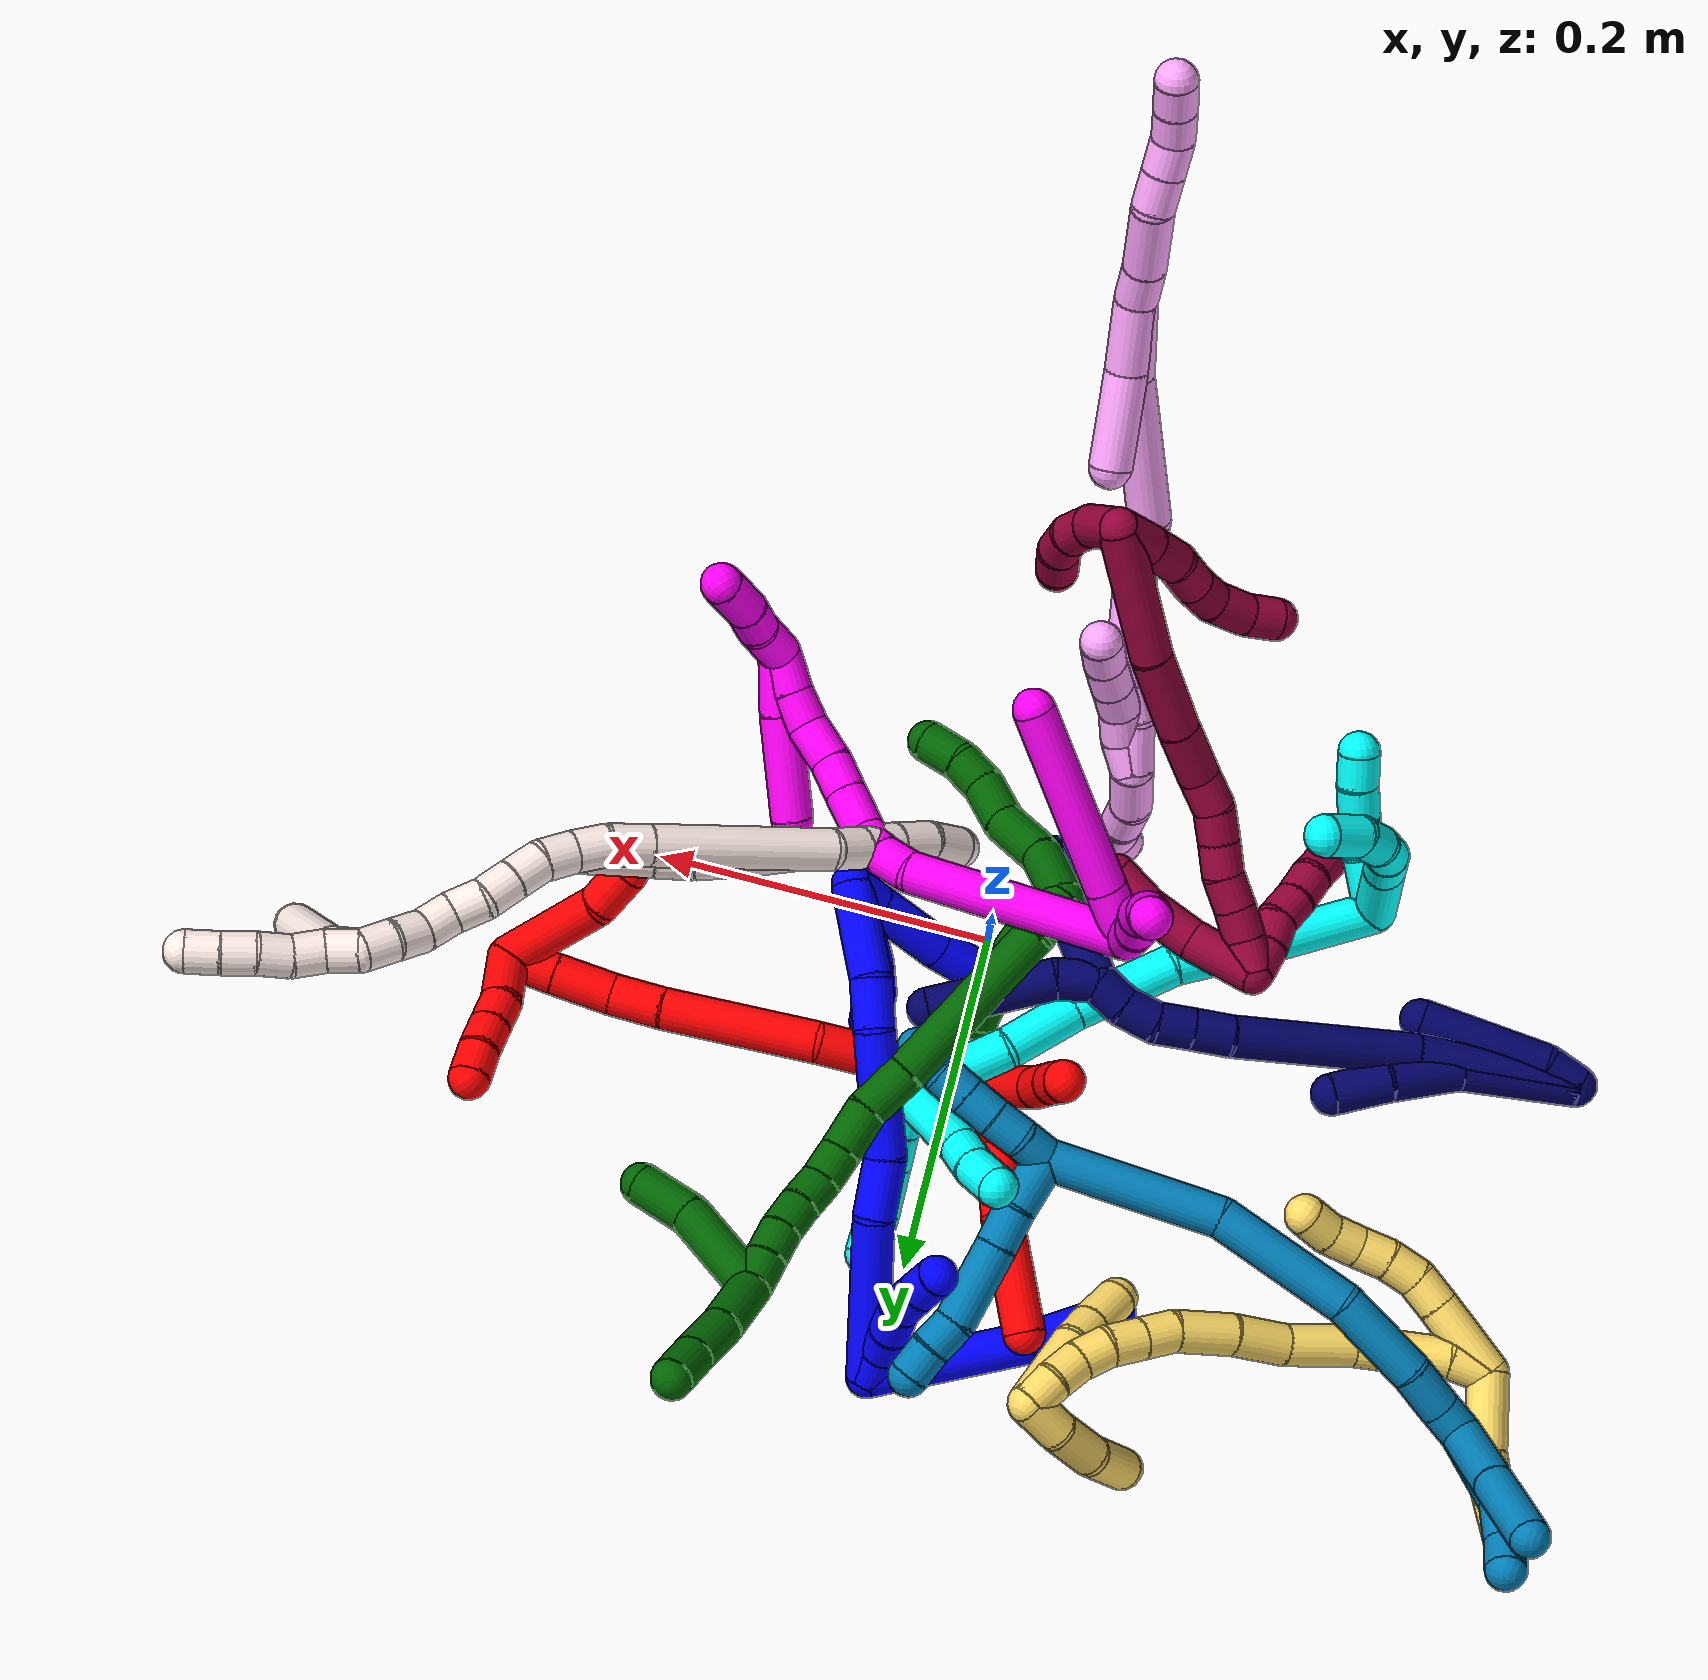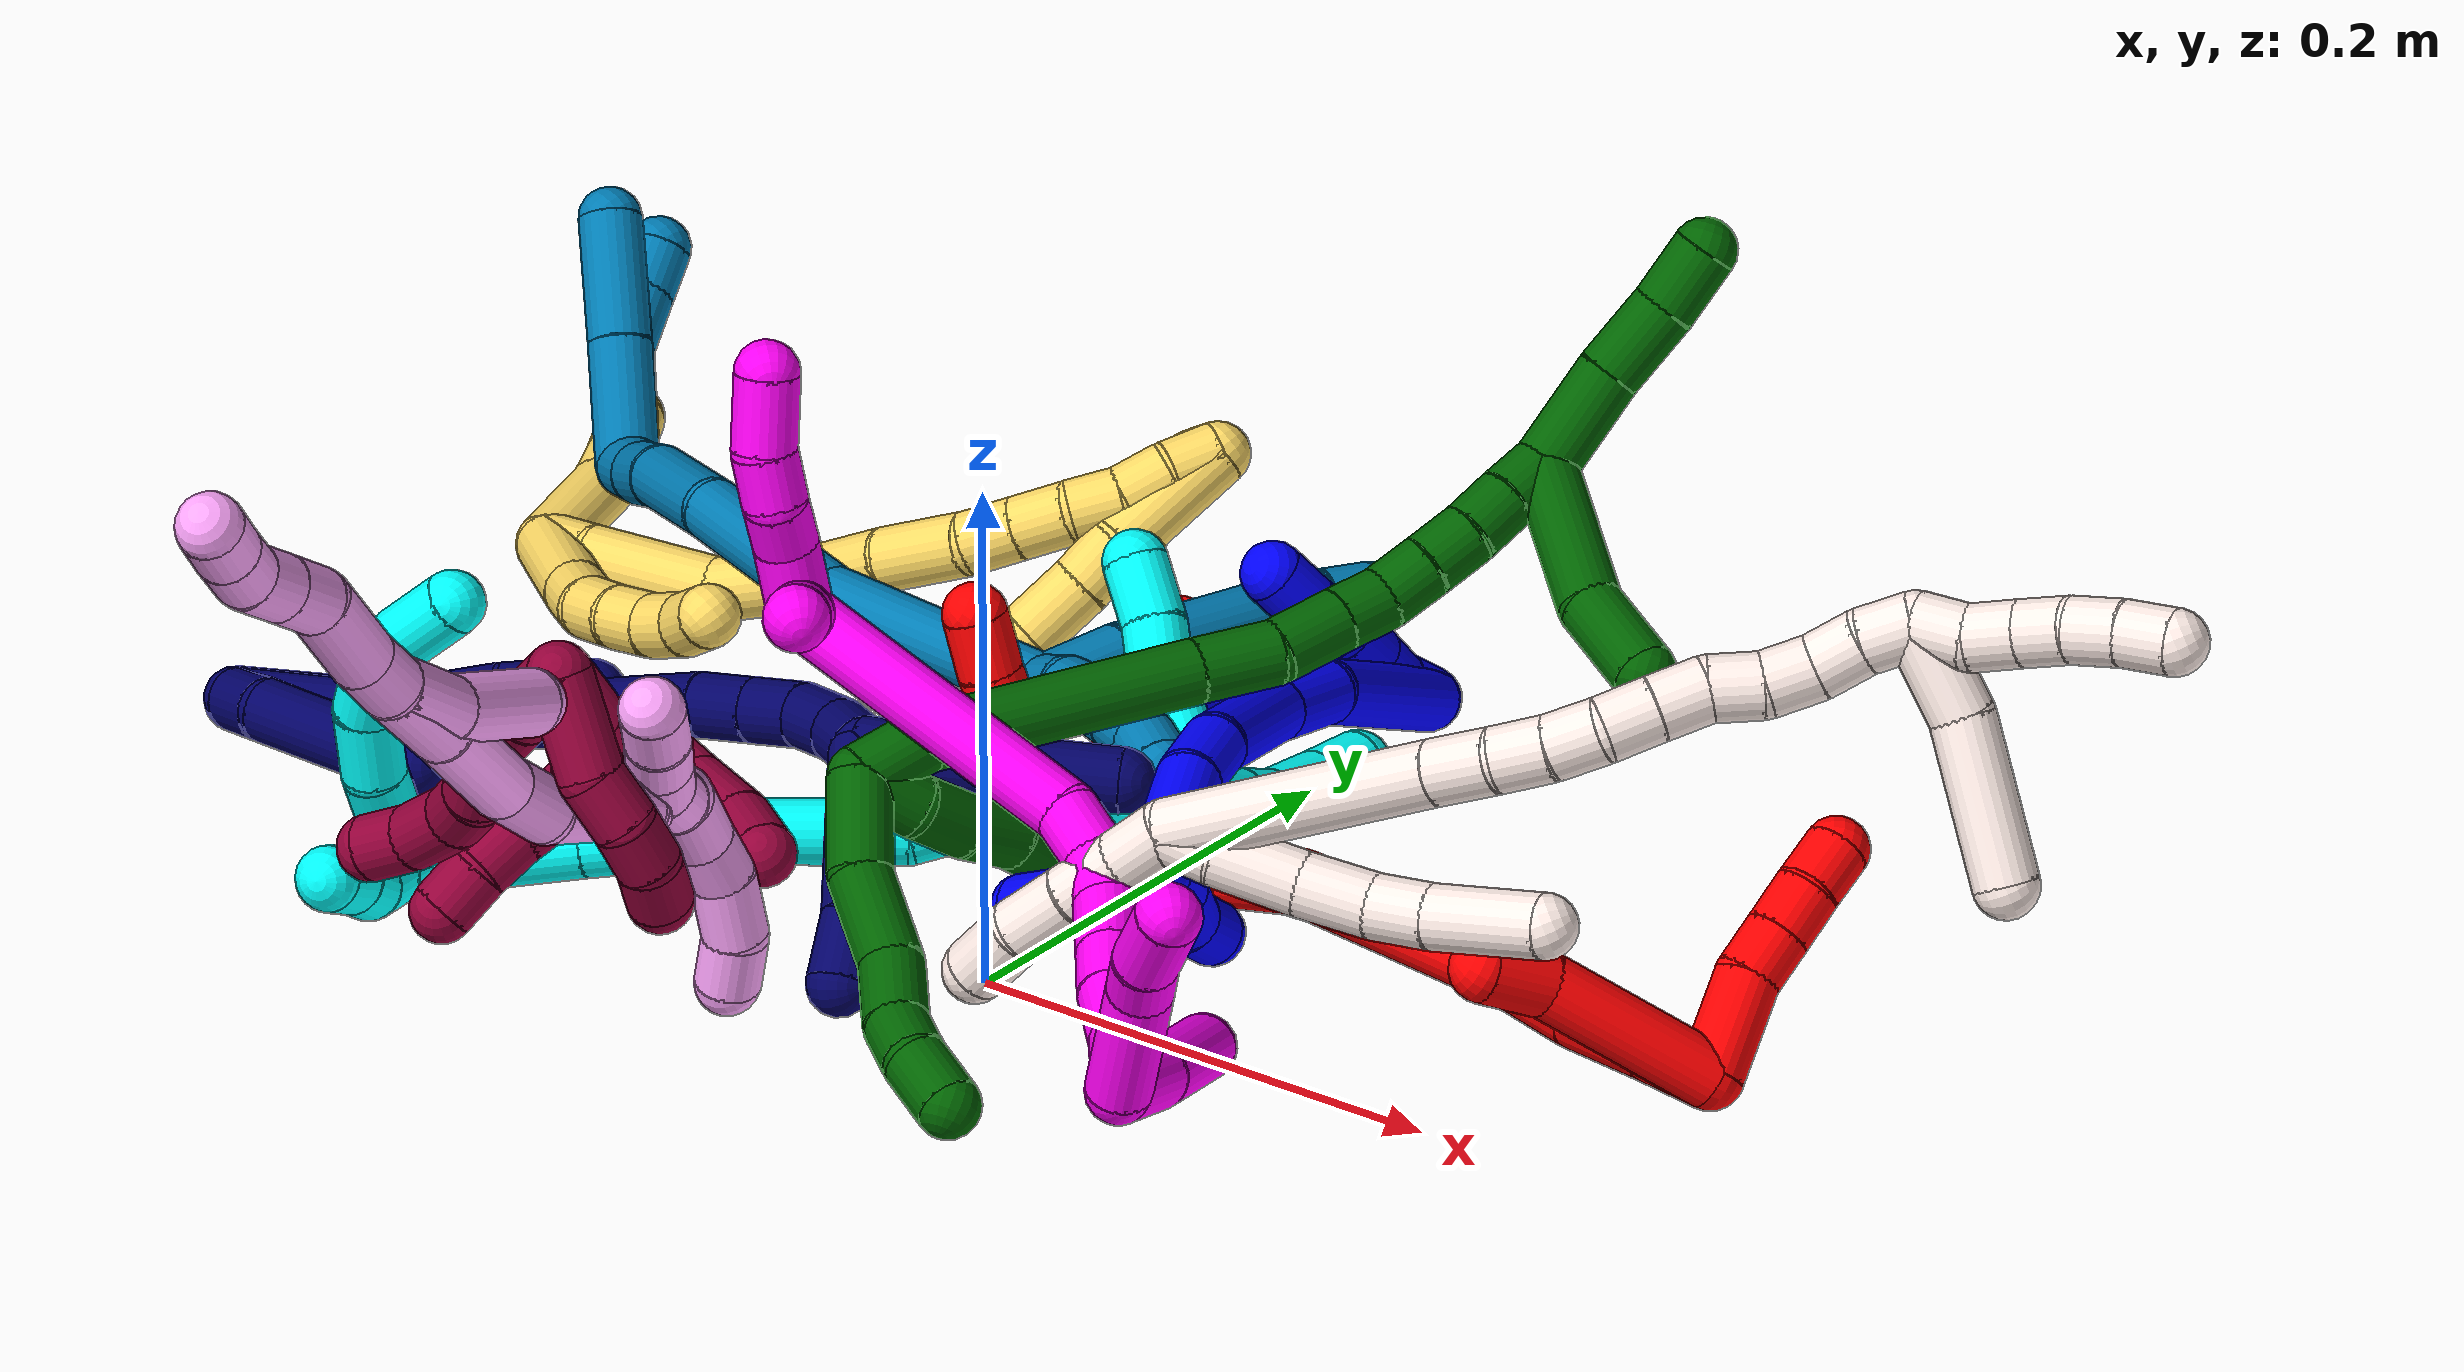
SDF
<sdf version="1.7">
 <world name="default">
  <plugin name="TubeGeneratorPlugin" filename="libtube_generator_plugin.so"/>
  <model name="photoneo_s_sensor">
   <static>1</static>
   <pose>0 0 2 1.57079 1.57079 3.14159</pose>
   <link name="link">
    <inertial><mass>0.1</mass></inertial>
    <sensor name="sensor" type="depth">
     <update_rate>30</update_rate>
     <camera>
      <horizontal_fov>1.22</horizontal_fov>
      <image><width>1920</width><height>1200</height><format>B8G8R8</format></image>
      <clip><near>0.1</near><far>4</far></clip>
      <depth_camera><output>points</output></depth_camera>
     </camera>
     <plugin name="camera_plugin" filename="libgazebo_ros_depth_camera.so">
      <baseline>0.2</baseline>
      <alwaysOn>1</alwaysOn>
      <updateRate>0.0</updateRate>
      <cameraName>camera_ir</cameraName>
      <imageTopicName>/camera/color/image_raw</imageTopicName>
      <cameraInfoTopicName>/camera/color/camera_info</cameraInfoTopicName>
      <depthImageTopicName>/camera/depth/image_raw</depthImageTopicName>
      <depthImageCameraInfoTopicName>/camera/depth/camera_info</depthImageCameraInfoTopicName>
      <pointCloudTopicName>/camera/depth/points</pointCloudTopicName>
      <frameName>fr_optical</frameName>
      <pointCloudCutoff>0.1</pointCloudCutoff>
      <pointCloudCutoffMax>2.0</pointCloudCutoffMax>
      <distortionK1>0</distortionK1>
      <distortionK2>0</distortionK2>
      <distortionK3>0</distortionK3>
      <distortionT1>0</distortionT1>
      <distortionT2>0</distortionT2>
      <CxPrime>0</CxPrime>
      <Cx>0</Cx>
      <Cy>0</Cy>
      <focalLength>0</focalLength>
      <hackBaseline>0</hackBaseline>
     </plugin>
    </sensor>
   </link>
  </model>
  <gravity>0 0 -9.8</gravity>
  <magnetic_field>6e-06 2.3e-05 -4.2e-05</magnetic_field>
  <atmosphere type="adiabatic"/>
  <physics name="default_physics" default="0" type="ode">
   <max_step_size>0.003</max_step_size>
   <real_time_factor>1</real_time_factor>
   <real_time_update_rate>1000</real_time_update_rate>
   <max_contacts>10000</max_contacts>
   <ode>
    <solver>
     <type>quick</type>
     <iters>100</iters>
     <sor>1.3</sor>
     <use_dynamic_moi_rescaling>0</use_dynamic_moi_rescaling>
    </solver>
    <constraints>
     <contact_max_correcting_vel>0</contact_max_correcting_vel>
     <contact_surface_layer>0.001</contact_surface_layer>
     <cfm>0</cfm>
     <erp>0.2</erp>
    </constraints>
   </ode>
  </physics>
  <scene><ambient>0.4 0.4 0.4 1</ambient><background>0.7 0.7 0.7 1</background><shadows>0</shadows></scene>
  <audio><device>default</device></audio>
  <spherical_coordinates>
   <surface_model>EARTH_WGS84</surface_model>
   <latitude_deg>0</latitude_deg>
   <longitude_deg>0</longitude_deg>
   <elevation>0</elevation>
   <heading_deg>0</heading_deg>
  </spherical_coordinates>
  <model name="bin">
   <static>1</static>
   <link name="bottom">
    <collision name="collision-bottom">
     <pose>0 0 -0.01 0 -0 0</pose>
     <geometry><box><size>0.8 0.6 0.02</size></box></geometry>
     <surface>
      <friction><ode><mu>100</mu><mu2>100</mu2></ode></friction>
      <contact><collide_bitmask>65535</collide_bitmask></contact>
     </surface>
    </collision>
   </link>
   <link name="west_wall">
    <collision name="collision-west_wall">
     <pose>-0.41 0 0.1 0 -0 0</pose>
     <geometry><box><size>0.02 0.6 0.2</size></box></geometry>
     <surface>
      <friction><ode><mu>100</mu><mu2>100</mu2></ode></friction>
      <contact><collide_bitmask>65535</collide_bitmask></contact>
     </surface>
    </collision>
   </link>
   <link name="east_wall">
    <collision name="collision-east_wall">
     <pose>0.41 0 0.1 0 -0 0</pose>
     <geometry><box><size>0.02 0.6 0.2</size></box></geometry>
     <surface>
      <friction><ode><mu>100</mu><mu2>100</mu2></ode></friction>
      <contact><collide_bitmask>65535</collide_bitmask></contact>
     </surface>
    </collision>
   </link>
   <link name="south_wall">
    <collision name="collision-south_wall">
     <pose>0 -0.31 0.1 0 -0 0</pose>
     <geometry><box><size>0.8 0.02 0.2</size></box></geometry>
     <surface>
      <friction><ode><mu>100</mu><mu2>100</mu2></ode></friction>
      <contact><collide_bitmask>65535</collide_bitmask></contact>
     </surface>
    </collision>
   </link>
   <link name="north_wall">
    <collision name="collision-north_wall">
     <pose>0 0.31 0.1 0 -0 0</pose>
     <geometry><box><size>0.8 0.02 0.2</size></box></geometry>
     <surface>
      <friction><ode><mu>100</mu><mu2>100</mu2></ode></friction>
      <contact><collide_bitmask>65535</collide_bitmask></contact>
     </surface>
    </collision>
   </link>
  </model>
  <model name="1">
   <static>0</static>
   <link name="1">
    <collision name="collision-cylinder-e_1_2_8">
     <pose>0.012439 0.0386 -0.027614 -2.19177 0.25633 -0.491173</pose>
     <geometry><cylinder><radius>0.0125</radius><length>0.098128</length></cylinder></geometry>
     <surface>
      <friction><ode><mu>1.16</mu><mu2>1.16</mu2><slip1>0</slip1><slip2>0</slip2></ode></friction>
      <contact><ode><kp>1e+06</kp><kd>1</kd><max_vel>0</max_vel><min_depth>0.001</min_depth></ode></contact>
     </surface>
    </collision>
    <visual name="visual-cylinder-e_1_2_8">
     <pose>0.012439 0.0386 -0.027614 -2.19177 0.25633 -0.491173</pose>
     <geometry><cylinder><radius>0.0125</radius><length>0.098128</length></cylinder></geometry>
     <material><ambient>0 0 1 1</ambient></material>
    </visual>
    <collision name="collision-cylinder-e_2_8_6">
     <pose>0.033835 0.095814 -0.070913 -2.27099 0.352582 -0.73162</pose>
     <geometry><cylinder><radius>0.0125</radius><length>0.051872</length></cylinder></geometry>
     <surface>
      <friction><ode><mu>1.16</mu><mu2>1.16</mu2><slip1>0</slip1><slip2>0</slip2></ode></friction>
      <contact><ode><kp>1e+06</kp><kd>1</kd><max_vel>0</max_vel><min_depth>0.001</min_depth></ode></contact>
     </surface>
    </collision>
    <visual name="visual-cylinder-e_2_8_6">
     <pose>0.033835 0.095814 -0.070913 -2.27099 0.352582 -0.73162</pose>
     <geometry><cylinder><radius>0.0125</radius><length>0.051872</length></cylinder></geometry>
     <material><ambient>0 0 1 1</ambient></material>
    </visual>
    <collision name="collision-cylinder-e_1_2_9">
     <pose>-0.000711 -0.000295 -0.00997 3.11203 -0.071195 -2.35459</pose>
     <geometry><cylinder><radius>0.0125</radius><length>0.02</length></cylinder></geometry>
     <surface>
      <friction><ode><mu>1.16</mu><mu2>1.16</mu2><slip1>0</slip1><slip2>0</slip2></ode></friction>
      <contact><ode><kp>1e+06</kp><kd>1</kd><max_vel>0</max_vel><min_depth>0.001</min_depth></ode></contact>
     </surface>
    </collision>
    <visual name="visual-cylinder-e_1_2_9">
     <pose>-0.000711 -0.000295 -0.00997 3.11203 -0.071195 -2.35459</pose>
     <geometry><cylinder><radius>0.0125</radius><length>0.02</length></cylinder></geometry>
     <material><ambient>0 0 1 1</ambient></material>
    </visual>
    <collision name="collision-cylinder-e_2_9_10">
     <pose>-0.004556 -0.001346 -0.029407 3.06184 -0.31871 -2.65494</pose>
     <geometry><cylinder><radius>0.0125</radius><length>0.02</length></cylinder></geometry>
     <surface>
      <friction><ode><mu>1.16</mu><mu2>1.16</mu2><slip1>0</slip1><slip2>0</slip2></ode></friction>
      <contact><ode><kp>1e+06</kp><kd>1</kd><max_vel>0</max_vel><min_depth>0.001</min_depth></ode></contact>
     </surface>
    </collision>
    <visual name="visual-cylinder-e_2_9_10">
     <pose>-0.004556 -0.001346 -0.029407 3.06184 -0.31871 -2.65494</pose>
     <geometry><cylinder><radius>0.0125</radius><length>0.02</length></cylinder></geometry>
     <material><ambient>0 0 1 1</ambient></material>
    </visual>
    <collision name="collision-cylinder-e_3_10_11">
     <pose>-0.010121 -0.00315 -0.048516 3.03339 -0.245626 -2.3147</pose>
     <geometry><cylinder><radius>0.0125</radius><length>0.02</length></cylinder></geometry>
     <surface>
      <friction><ode><mu>1.16</mu><mu2>1.16</mu2><slip1>0</slip1><slip2>0</slip2></ode></friction>
      <contact><ode><kp>1e+06</kp><kd>1</kd><max_vel>0</max_vel><min_depth>0.001</min_depth></ode></contact>
     </surface>
    </collision>
    <visual name="visual-cylinder-e_3_10_11">
     <pose>-0.010121 -0.00315 -0.048516 3.03339 -0.245626 -2.3147</pose>
     <geometry><cylinder><radius>0.0125</radius><length>0.02</length></cylinder></geometry>
     <material><ambient>0 0 1 1</ambient></material>
    </visual>
    <collision name="collision-cylinder-e_4_11_12">
     <pose>-0.014819 -0.002093 -0.067669 -2.92381 -0.22859 1.61962</pose>
     <geometry><cylinder><radius>0.0125</radius><length>0.02</length></cylinder></geometry>
     <surface>
      <friction><ode><mu>1.16</mu><mu2>1.16</mu2><slip1>0</slip1><slip2>0</slip2></ode></friction>
      <contact><ode><kp>1e+06</kp><kd>1</kd><max_vel>0</max_vel><min_depth>0.001</min_depth></ode></contact>
     </surface>
    </collision>
    <visual name="visual-cylinder-e_4_11_12">
     <pose>-0.014819 -0.002093 -0.067669 -2.92381 -0.22859 1.61962</pose>
     <geometry><cylinder><radius>0.0125</radius><length>0.02</length></cylinder></geometry>
     <material><ambient>0 0 1 1</ambient></material>
    </visual>
    <collision name="collision-cylinder-e_5_12_5">
     <pose>-0.020378 0.002133 -0.08638 -2.91495 -0.335564 1.95831</pose>
     <geometry><cylinder><radius>0.0125</radius><length>0.02</length></cylinder></geometry>
     <surface>
      <friction><ode><mu>1.16</mu><mu2>1.16</mu2><slip1>0</slip1><slip2>0</slip2></ode></friction>
      <contact><ode><kp>1e+06</kp><kd>1</kd><max_vel>0</max_vel><min_depth>0.001</min_depth></ode></contact>
     </surface>
    </collision>
    <visual name="visual-cylinder-e_5_12_5">
     <pose>-0.020378 0.002133 -0.08638 -2.91495 -0.335564 1.95831</pose>
     <geometry><cylinder><radius>0.0125</radius><length>0.02</length></cylinder></geometry>
     <material><ambient>0 0 1 1</ambient></material>
    </visual>
    <collision name="collision-cylinder-e_1_2_13">
     <pose>0.005664 -0.020322 -0.046081 2.72624 0.111985 0.519968</pose>
     <geometry><cylinder><radius>0.0125</radius><length>0.101361</length></cylinder></geometry>
     <surface>
      <friction><ode><mu>1.16</mu><mu2>1.16</mu2><slip1>0</slip1><slip2>0</slip2></ode></friction>
      <contact><ode><kp>1e+06</kp><kd>1</kd><max_vel>0</max_vel><min_depth>0.001</min_depth></ode></contact>
     </surface>
    </collision>
    <visual name="visual-cylinder-e_1_2_13">
     <pose>0.005664 -0.020322 -0.046081 2.72624 0.111985 0.519968</pose>
     <geometry><cylinder><radius>0.0125</radius><length>0.101361</length></cylinder></geometry>
     <material><ambient>0 0 1 1</ambient></material>
    </visual>
    <collision name="collision-cylinder-e_2_13_14">
     <pose>0.017963 -0.045576 -0.108173 2.84282 0.377139 1.806</pose>
     <geometry><cylinder><radius>0.0125</radius><length>0.036039</length></cylinder></geometry>
     <surface>
      <friction><ode><mu>1.16</mu><mu2>1.16</mu2><slip1>0</slip1><slip2>0</slip2></ode></friction>
      <contact><ode><kp>1e+06</kp><kd>1</kd><max_vel>0</max_vel><min_depth>0.001</min_depth></ode></contact>
     </surface>
    </collision>
    <visual name="visual-cylinder-e_2_13_14">
     <pose>0.017963 -0.045576 -0.108173 2.84282 0.377139 1.806</pose>
     <geometry><cylinder><radius>0.0125</radius><length>0.036039</length></cylinder></geometry>
     <material><ambient>0 0 1 1</ambient></material>
    </visual>
    <collision name="collision-cylinder-e_3_14_15">
     <pose>0.034724 -0.07014 -0.154916 2.57311 0.270821 0.872725</pose>
     <geometry><cylinder><radius>0.0125</radius><length>0.075694</length></cylinder></geometry>
     <surface>
      <friction><ode><mu>1.16</mu><mu2>1.16</mu2><slip1>0</slip1><slip2>0</slip2></ode></friction>
      <contact><ode><kp>1e+06</kp><kd>1</kd><max_vel>0</max_vel><min_depth>0.001</min_depth></ode></contact>
     </surface>
    </collision>
    <visual name="visual-cylinder-e_3_14_15">
     <pose>0.034724 -0.07014 -0.154916 2.57311 0.270821 0.872725</pose>
     <geometry><cylinder><radius>0.0125</radius><length>0.075694</length></cylinder></geometry>
     <material><ambient>0 0 1 1</ambient></material>
    </visual>
    <collision name="collision-cylinder-e_4_15_16">
     <pose>0.052449 -0.097173 -0.196078 2.5245 0.536188 1.42271</pose>
     <geometry><cylinder><radius>0.0125</radius><length>0.029754</length></cylinder></geometry>
     <surface>
      <friction><ode><mu>1.16</mu><mu2>1.16</mu2><slip1>0</slip1><slip2>0</slip2></ode></friction>
      <contact><ode><kp>1e+06</kp><kd>1</kd><max_vel>0</max_vel><min_depth>0.001</min_depth></ode></contact>
     </surface>
    </collision>
    <visual name="visual-cylinder-e_4_15_16">
     <pose>0.052449 -0.097173 -0.196078 2.5245 0.536188 1.42271</pose>
     <geometry><cylinder><radius>0.0125</radius><length>0.029754</length></cylinder></geometry>
     <material><ambient>0 0 1 1</ambient></material>
    </visual>
    <collision name="collision-cylinder-e_5_16_1">
     <pose>0.078103 -0.120719 -0.221672 2.32483 0.683879 1.37668</pose>
     <geometry><cylinder><radius>0.0125</radius><length>0.057151</length></cylinder></geometry>
     <surface>
      <friction><ode><mu>1.16</mu><mu2>1.16</mu2><slip1>0</slip1><slip2>0</slip2></ode></friction>
      <contact><ode><kp>1e+06</kp><kd>1</kd><max_vel>0</max_vel><min_depth>0.001</min_depth></ode></contact>
     </surface>
    </collision>
    <visual name="visual-cylinder-e_5_16_1">
     <pose>0.078103 -0.120719 -0.221672 2.32483 0.683879 1.37668</pose>
     <geometry><cylinder><radius>0.0125</radius><length>0.057151</length></cylinder></geometry>
     <material><ambient>0 0 1 1</ambient></material>
    </visual>
    <collision name="collision-cylinder-e_1_1_17">
     <pose>0.098093 -0.120582 -0.215387 -0.649346 0.071761 -0.024163</pose>
     <geometry><cylinder><radius>0.0125</radius><length>0.053996</length></cylinder></geometry>
     <surface>
      <friction><ode><mu>1.16</mu><mu2>1.16</mu2><slip1>0</slip1><slip2>0</slip2></ode></friction>
      <contact><ode><kp>1e+06</kp><kd>1</kd><max_vel>0</max_vel><min_depth>0.001</min_depth></ode></contact>
     </surface>
    </collision>
    <visual name="visual-cylinder-e_1_1_17">
     <pose>0.098093 -0.120582 -0.215387 -0.649346 0.071761 -0.024163</pose>
     <geometry><cylinder><radius>0.0125</radius><length>0.053996</length></cylinder></geometry>
     <material><ambient>0 0 1 1</ambient></material>
    </visual>
    <collision name="collision-cylinder-e_2_17_18">
     <pose>0.104501 -0.099105 -0.183127 -0.447874 0.35683 -0.082098</pose>
     <geometry><cylinder><radius>0.0125</radius><length>0.025603</length></cylinder></geometry>
     <surface>
      <friction><ode><mu>1.16</mu><mu2>1.16</mu2><slip1>0</slip1><slip2>0</slip2></ode></friction>
      <contact><ode><kp>1e+06</kp><kd>1</kd><max_vel>0</max_vel><min_depth>0.001</min_depth></ode></contact>
     </surface>
    </collision>
    <visual name="visual-cylinder-e_2_17_18">
     <pose>0.104501 -0.099105 -0.183127 -0.447874 0.35683 -0.082098</pose>
     <geometry><cylinder><radius>0.0125</radius><length>0.025603</length></cylinder></geometry>
     <material><ambient>0 0 1 1</ambient></material>
    </visual>
    <collision name="collision-cylinder-e_3_18_4">
     <pose>0.109619 -0.091149 -0.162517 -0.274705 0.063439 -0.008772</pose>
     <geometry><cylinder><radius>0.0125</radius><length>0.020401</length></cylinder></geometry>
     <surface>
      <friction><ode><mu>1.16</mu><mu2>1.16</mu2><slip1>0</slip1><slip2>0</slip2></ode></friction>
      <contact><ode><kp>1e+06</kp><kd>1</kd><max_vel>0</max_vel><min_depth>0.001</min_depth></ode></contact>
     </surface>
    </collision>
    <visual name="visual-cylinder-e_3_18_4">
     <pose>0.109619 -0.091149 -0.162517 -0.274705 0.063439 -0.008772</pose>
     <geometry><cylinder><radius>0.0125</radius><length>0.020401</length></cylinder></geometry>
     <material><ambient>0 0 1 1</ambient></material>
    </visual>
    <collision name="collision-cylinder-e_1_1_19">
     <pose>0.09989 -0.127739 -0.232849 -1.15898 0.358566 -0.236104</pose>
     <geometry><cylinder><radius>0.0125</radius><length>0.02127</length></cylinder></geometry>
     <surface>
      <friction><ode><mu>1.16</mu><mu2>1.16</mu2><slip1>0</slip1><slip2>0</slip2></ode></friction>
      <contact><ode><kp>1e+06</kp><kd>1</kd><max_vel>0</max_vel><min_depth>0.001</min_depth></ode></contact>
     </surface>
    </collision>
    <visual name="visual-cylinder-e_1_1_19">
     <pose>0.09989 -0.127739 -0.232849 -1.15898 0.358566 -0.236104</pose>
     <geometry><cylinder><radius>0.0125</radius><length>0.02127</length></cylinder></geometry>
     <material><ambient>0 0 1 1</ambient></material>
    </visual>
    <collision name="collision-cylinder-e_2_19_20">
     <pose>0.110003 -0.096627 -0.221203 -1.23555 0.267518 -0.190648</pose>
     <geometry><cylinder><radius>0.0125</radius><length>0.04828</length></cylinder></geometry>
     <surface>
      <friction><ode><mu>1.16</mu><mu2>1.16</mu2><slip1>0</slip1><slip2>0</slip2></ode></friction>
      <contact><ode><kp>1e+06</kp><kd>1</kd><max_vel>0</max_vel><min_depth>0.001</min_depth></ode></contact>
     </surface>
    </collision>
    <visual name="visual-cylinder-e_2_19_20">
     <pose>0.110003 -0.096627 -0.221203 -1.23555 0.267518 -0.190648</pose>
     <geometry><cylinder><radius>0.0125</radius><length>0.04828</length></cylinder></geometry>
     <material><ambient>0 0 1 1</ambient></material>
    </visual>
    <collision name="collision-cylinder-e_3_20_3">
     <pose>0.12053 -0.060346 -0.210345 -1.35066 0.275801 -0.221408</pose>
     <geometry><cylinder><radius>0.0125</radius><length>0.03045</length></cylinder></geometry>
     <surface>
      <friction><ode><mu>1.16</mu><mu2>1.16</mu2><slip1>0</slip1><slip2>0</slip2></ode></friction>
      <contact><ode><kp>1e+06</kp><kd>1</kd><max_vel>0</max_vel><min_depth>0.001</min_depth></ode></contact>
     </surface>
    </collision>
    <visual name="visual-cylinder-e_3_20_3">
     <pose>0.12053 -0.060346 -0.210345 -1.35066 0.275801 -0.221408</pose>
     <geometry><cylinder><radius>0.0125</radius><length>0.03045</length></cylinder></geometry>
     <material><ambient>0 0 1 1</ambient></material>
    </visual>
    <collision name="collision-sphere-3">
     <pose>0.124676 -0.04605 -0.207146 0 -0 0</pose>
     <geometry><sphere><radius>0.0125</radius></sphere></geometry>
     <surface>
      <friction><ode><mu>1.16</mu><mu2>1.16</mu2><slip1>0</slip1><slip2>0</slip2></ode></friction>
      <contact><ode><kp>1e+06</kp><kd>1</kd><max_vel>0</max_vel><min_depth>0.001</min_depth></ode></contact>
     </surface>
    </collision>
    <visual name="visual-sphere-3">
     <pose>0.124676 -0.04605 -0.207146 0 -0 0</pose>
     <geometry><sphere><radius>0.0125</radius></sphere></geometry>
     <material><ambient>0 0 1 1</ambient></material>
    </visual>
    <collision name="collision-sphere-20">
     <pose>0.116384 -0.074642 -0.213544 0 -0 0</pose>
     <geometry><sphere><radius>0.0125</radius></sphere></geometry>
     <surface>
      <friction><ode><mu>1.16</mu><mu2>1.16</mu2><slip1>0</slip1><slip2>0</slip2></ode></friction>
      <contact><ode><kp>1e+06</kp><kd>1</kd><max_vel>0</max_vel><min_depth>0.001</min_depth></ode></contact>
     </surface>
    </collision>
    <visual name="visual-sphere-20">
     <pose>0.116384 -0.074642 -0.213544 0 -0 0</pose>
     <geometry><sphere><radius>0.0125</radius></sphere></geometry>
     <material><ambient>0 0 1 1</ambient></material>
    </visual>
    <collision name="collision-sphere-19">
     <pose>0.103622 -0.118613 -0.228863 0 -0 0</pose>
     <geometry><sphere><radius>0.0125</radius></sphere></geometry>
     <surface>
      <friction><ode><mu>1.16</mu><mu2>1.16</mu2><slip1>0</slip1><slip2>0</slip2></ode></friction>
      <contact><ode><kp>1e+06</kp><kd>1</kd><max_vel>0</max_vel><min_depth>0.001</min_depth></ode></contact>
     </surface>
    </collision>
    <visual name="visual-sphere-19">
     <pose>0.103622 -0.118613 -0.228863 0 -0 0</pose>
     <geometry><sphere><radius>0.0125</radius></sphere></geometry>
     <material><ambient>0 0 1 1</ambient></material>
    </visual>
    <collision name="collision-sphere-11">
     <pose>-0.012553 -0.004198 -0.058159 0 -0 0</pose>
     <geometry><sphere><radius>0.0125</radius></sphere></geometry>
     <surface>
      <friction><ode><mu>1.16</mu><mu2>1.16</mu2><slip1>0</slip1><slip2>0</slip2></ode></friction>
      <contact><ode><kp>1e+06</kp><kd>1</kd><max_vel>0</max_vel><min_depth>0.001</min_depth></ode></contact>
     </surface>
    </collision>
    <visual name="visual-sphere-11">
     <pose>-0.012553 -0.004198 -0.058159 0 -0 0</pose>
     <geometry><sphere><radius>0.0125</radius></sphere></geometry>
     <material><ambient>0 0 1 1</ambient></material>
    </visual>
    <collision name="collision-sphere-10">
     <pose>-0.00769 -0.002103 -0.038873 0 -0 0</pose>
     <geometry><sphere><radius>0.0125</radius></sphere></geometry>
     <surface>
      <friction><ode><mu>1.16</mu><mu2>1.16</mu2><slip1>0</slip1><slip2>0</slip2></ode></friction>
      <contact><ode><kp>1e+06</kp><kd>1</kd><max_vel>0</max_vel><min_depth>0.001</min_depth></ode></contact>
     </surface>
    </collision>
    <visual name="visual-sphere-10">
     <pose>-0.00769 -0.002103 -0.038873 0 -0 0</pose>
     <geometry><sphere><radius>0.0125</radius></sphere></geometry>
     <material><ambient>0 0 1 1</ambient></material>
    </visual>
    <collision name="collision-sphere-6">
     <pose>0.042791 0.114428 -0.086597 0 -0 0</pose>
     <geometry><sphere><radius>0.0125</radius></sphere></geometry>
     <surface>
      <friction><ode><mu>1.16</mu><mu2>1.16</mu2><slip1>0</slip1><slip2>0</slip2></ode></friction>
      <contact><ode><kp>1e+06</kp><kd>1</kd><max_vel>0</max_vel><min_depth>0.001</min_depth></ode></contact>
     </surface>
    </collision>
    <visual name="visual-sphere-6">
     <pose>0.042791 0.114428 -0.086597 0 -0 0</pose>
     <geometry><sphere><radius>0.0125</radius></sphere></geometry>
     <material><ambient>0 0 1 1</ambient></material>
    </visual>
    <collision name="collision-sphere-9">
     <pose>-0.001423 -0.00059 -0.019941 0 -0 0</pose>
     <geometry><sphere><radius>0.0125</radius></sphere></geometry>
     <surface>
      <friction><ode><mu>1.16</mu><mu2>1.16</mu2><slip1>0</slip1><slip2>0</slip2></ode></friction>
      <contact><ode><kp>1e+06</kp><kd>1</kd><max_vel>0</max_vel><min_depth>0.001</min_depth></ode></contact>
     </surface>
    </collision>
    <visual name="visual-sphere-9">
     <pose>-0.001423 -0.00059 -0.019941 0 -0 0</pose>
     <geometry><sphere><radius>0.0125</radius></sphere></geometry>
     <material><ambient>0 0 1 1</ambient></material>
    </visual>
    <collision name="collision-sphere-2">
     <geometry><sphere><radius>0.0125</radius></sphere></geometry>
     <surface>
      <friction><ode><mu>1.16</mu><mu2>1.16</mu2><slip1>0</slip1><slip2>0</slip2></ode></friction>
      <contact><ode><kp>1e+06</kp><kd>1</kd><max_vel>0</max_vel><min_depth>0.001</min_depth></ode></contact>
     </surface>
    </collision>
    <visual name="visual-sphere-2">
     <geometry><sphere><radius>0.0125</radius></sphere></geometry>
     <material><ambient>0 0 1 1</ambient></material>
    </visual>
    <collision name="collision-sphere-8">
     <pose>0.024878 0.077201 -0.055228 0 -0 0</pose>
     <geometry><sphere><radius>0.0125</radius></sphere></geometry>
     <surface>
      <friction><ode><mu>1.16</mu><mu2>1.16</mu2><slip1>0</slip1><slip2>0</slip2></ode></friction>
      <contact><ode><kp>1e+06</kp><kd>1</kd><max_vel>0</max_vel><min_depth>0.001</min_depth></ode></contact>
     </surface>
    </collision>
    <visual name="visual-sphere-8">
     <pose>0.024878 0.077201 -0.055228 0 -0 0</pose>
     <geometry><sphere><radius>0.0125</radius></sphere></geometry>
     <material><ambient>0 0 1 1</ambient></material>
    </visual>
    <collision name="collision-sphere-12">
     <pose>-0.017085 1.1e-05 -0.077179 0 -0 0</pose>
     <geometry><sphere><radius>0.0125</radius></sphere></geometry>
     <surface>
      <friction><ode><mu>1.16</mu><mu2>1.16</mu2><slip1>0</slip1><slip2>0</slip2></ode></friction>
      <contact><ode><kp>1e+06</kp><kd>1</kd><max_vel>0</max_vel><min_depth>0.001</min_depth></ode></contact>
     </surface>
    </collision>
    <visual name="visual-sphere-12">
     <pose>-0.017085 1.1e-05 -0.077179 0 -0 0</pose>
     <geometry><sphere><radius>0.0125</radius></sphere></geometry>
     <material><ambient>0 0 1 1</ambient></material>
    </visual>
    <collision name="collision-sphere-5">
     <pose>-0.023671 0.004254 -0.09558 0 -0 0</pose>
     <geometry><sphere><radius>0.0125</radius></sphere></geometry>
     <surface>
      <friction><ode><mu>1.16</mu><mu2>1.16</mu2><slip1>0</slip1><slip2>0</slip2></ode></friction>
      <contact><ode><kp>1e+06</kp><kd>1</kd><max_vel>0</max_vel><min_depth>0.001</min_depth></ode></contact>
     </surface>
    </collision>
    <visual name="visual-sphere-5">
     <pose>-0.023671 0.004254 -0.09558 0 -0 0</pose>
     <geometry><sphere><radius>0.0125</radius></sphere></geometry>
     <material><ambient>0 0 1 1</ambient></material>
    </visual>
    <collision name="collision-sphere-13">
     <pose>0.011327 -0.040645 -0.092162 0 -0 0</pose>
     <geometry><sphere><radius>0.0125</radius></sphere></geometry>
     <surface>
      <friction><ode><mu>1.16</mu><mu2>1.16</mu2><slip1>0</slip1><slip2>0</slip2></ode></friction>
      <contact><ode><kp>1e+06</kp><kd>1</kd><max_vel>0</max_vel><min_depth>0.001</min_depth></ode></contact>
     </surface>
    </collision>
    <visual name="visual-sphere-13">
     <pose>0.011327 -0.040645 -0.092162 0 -0 0</pose>
     <geometry><sphere><radius>0.0125</radius></sphere></geometry>
     <material><ambient>0 0 1 1</ambient></material>
    </visual>
    <collision name="collision-sphere-14">
     <pose>0.024599 -0.050507 -0.124184 0 -0 0</pose>
     <geometry><sphere><radius>0.0125</radius></sphere></geometry>
     <surface>
      <friction><ode><mu>1.16</mu><mu2>1.16</mu2><slip1>0</slip1><slip2>0</slip2></ode></friction>
      <contact><ode><kp>1e+06</kp><kd>1</kd><max_vel>0</max_vel><min_depth>0.001</min_depth></ode></contact>
     </surface>
    </collision>
    <visual name="visual-sphere-14">
     <pose>0.024599 -0.050507 -0.124184 0 -0 0</pose>
     <geometry><sphere><radius>0.0125</radius></sphere></geometry>
     <material><ambient>0 0 1 1</ambient></material>
    </visual>
    <collision name="collision-sphere-15">
     <pose>0.044849 -0.089772 -0.185648 0 -0 0</pose>
     <geometry><sphere><radius>0.0125</radius></sphere></geometry>
     <surface>
      <friction><ode><mu>1.16</mu><mu2>1.16</mu2><slip1>0</slip1><slip2>0</slip2></ode></friction>
      <contact><ode><kp>1e+06</kp><kd>1</kd><max_vel>0</max_vel><min_depth>0.001</min_depth></ode></contact>
     </surface>
    </collision>
    <visual name="visual-sphere-15">
     <pose>0.044849 -0.089772 -0.185648 0 -0 0</pose>
     <geometry><sphere><radius>0.0125</radius></sphere></geometry>
     <material><ambient>0 0 1 1</ambient></material>
    </visual>
    <collision name="collision-sphere-16">
     <pose>0.060049 -0.104574 -0.206509 0 -0 0</pose>
     <geometry><sphere><radius>0.0125</radius></sphere></geometry>
     <surface>
      <friction><ode><mu>1.16</mu><mu2>1.16</mu2><slip1>0</slip1><slip2>0</slip2></ode></friction>
      <contact><ode><kp>1e+06</kp><kd>1</kd><max_vel>0</max_vel><min_depth>0.001</min_depth></ode></contact>
     </surface>
    </collision>
    <visual name="visual-sphere-16">
     <pose>0.060049 -0.104574 -0.206509 0 -0 0</pose>
     <geometry><sphere><radius>0.0125</radius></sphere></geometry>
     <material><ambient>0 0 1 1</ambient></material>
    </visual>
    <collision name="collision-sphere-1">
     <pose>0.096158 -0.136865 -0.236836 0 -0 0</pose>
     <geometry><sphere><radius>0.0125</radius></sphere></geometry>
     <surface>
      <friction><ode><mu>1.16</mu><mu2>1.16</mu2><slip1>0</slip1><slip2>0</slip2></ode></friction>
      <contact><ode><kp>1e+06</kp><kd>1</kd><max_vel>0</max_vel><min_depth>0.001</min_depth></ode></contact>
     </surface>
    </collision>
    <visual name="visual-sphere-1">
     <pose>0.096158 -0.136865 -0.236836 0 -0 0</pose>
     <geometry><sphere><radius>0.0125</radius></sphere></geometry>
     <material><ambient>0 0 1 1</ambient></material>
    </visual>
    <collision name="collision-sphere-18">
     <pose>0.108972 -0.093911 -0.172316 0 -0 0</pose>
     <geometry><sphere><radius>0.0125</radius></sphere></geometry>
     <surface>
      <friction><ode><mu>1.16</mu><mu2>1.16</mu2><slip1>0</slip1><slip2>0</slip2></ode></friction>
      <contact><ode><kp>1e+06</kp><kd>1</kd><max_vel>0</max_vel><min_depth>0.001</min_depth></ode></contact>
     </surface>
    </collision>
    <visual name="visual-sphere-18">
     <pose>0.108972 -0.093911 -0.172316 0 -0 0</pose>
     <geometry><sphere><radius>0.0125</radius></sphere></geometry>
     <material><ambient>0 0 1 1</ambient></material>
    </visual>
    <collision name="collision-sphere-17">
     <pose>0.100029 -0.104299 -0.193939 0 -0 0</pose>
     <geometry><sphere><radius>0.0125</radius></sphere></geometry>
     <surface>
      <friction><ode><mu>1.16</mu><mu2>1.16</mu2><slip1>0</slip1><slip2>0</slip2></ode></friction>
      <contact><ode><kp>1e+06</kp><kd>1</kd><max_vel>0</max_vel><min_depth>0.001</min_depth></ode></contact>
     </surface>
    </collision>
    <visual name="visual-sphere-17">
     <pose>0.100029 -0.104299 -0.193939 0 -0 0</pose>
     <geometry><sphere><radius>0.0125</radius></sphere></geometry>
     <material><ambient>0 0 1 1</ambient></material>
    </visual>
    <collision name="collision-sphere-4">
     <pose>0.110266 -0.088388 -0.152719 0 -0 0</pose>
     <geometry><sphere><radius>0.0125</radius></sphere></geometry>
     <surface>
      <friction><ode><mu>1.16</mu><mu2>1.16</mu2><slip1>0</slip1><slip2>0</slip2></ode></friction>
      <contact><ode><kp>1e+06</kp><kd>1</kd><max_vel>0</max_vel><min_depth>0.001</min_depth></ode></contact>
     </surface>
    </collision>
    <visual name="visual-sphere-4">
     <pose>0.110266 -0.088388 -0.152719 0 -0 0</pose>
     <geometry><sphere><radius>0.0125</radius></sphere></geometry>
     <material><ambient>0 0 1 1</ambient></material>
    </visual>
    <inertial>
     <pose>0.044203 -0.040356 -0.122263 0 -0 0</pose>
     <mass>0.75</mass>
     <inertia>
      <ixx>0.000272</ixx>
      <ixy>0</ixy>
      <ixz>0</ixz>
      <iyy>-3.7e-05</iyy>
      <iyz>0</iyz>
      <izz>-0.000121</izz>
     </inertia>
    </inertial>
   </link>
   <pose>0.005461 0.26664 0.01413 -2.94049 1.00103 -1.60041</pose>
  </model>
  <model name="2">
   <static>0</static>
   <link name="2">
    <collision name="collision-cylinder-e_1_2_8">
     <pose>-0.017384 -0.005471 0.004367 0.897174 -1.188 -0.628578</pose>
     <geometry><cylinder><radius>0.0125</radius><length>0.037481</length></cylinder></geometry>
     <surface>
      <friction><ode><mu>1.16</mu><mu2>1.16</mu2><slip1>0</slip1><slip2>0</slip2></ode></friction>
      <contact><ode><kp>1e+06</kp><kd>1</kd><max_vel>0</max_vel><min_depth>0.001</min_depth></ode></contact>
     </surface>
    </collision>
    <visual name="visual-cylinder-e_1_2_8">
     <pose>-0.017384 -0.005471 0.004367 0.897174 -1.188 -0.628578</pose>
     <geometry><cylinder><radius>0.0125</radius><length>0.037481</length></cylinder></geometry>
     <material><ambient>1 0 0 1</ambient></material>
    </visual>
    <collision name="collision-cylinder-e_2_8_9">
     <pose>-0.05523 -0.017222 0.013259 0.946388 -1.20913 -0.679958</pose>
     <geometry><cylinder><radius>0.0125</radius><length>0.043753</length></cylinder></geometry>
     <surface>
      <friction><ode><mu>1.16</mu><mu2>1.16</mu2><slip1>0</slip1><slip2>0</slip2></ode></friction>
      <contact><ode><kp>1e+06</kp><kd>1</kd><max_vel>0</max_vel><min_depth>0.001</min_depth></ode></contact>
     </surface>
    </collision>
    <visual name="visual-cylinder-e_2_8_9">
     <pose>-0.05523 -0.017222 0.013259 0.946388 -1.20913 -0.679958</pose>
     <geometry><cylinder><radius>0.0125</radius><length>0.043753</length></cylinder></geometry>
     <material><ambient>1 0 0 1</ambient></material>
    </visual>
    <collision name="collision-cylinder-e_3_9_6">
     <pose>-0.109149 -0.025378 0.025481 0.239112 -1.33829 -0.189442</pose>
     <geometry><cylinder><radius>0.0125</radius><length>0.068766</length></cylinder></geometry>
     <surface>
      <friction><ode><mu>1.16</mu><mu2>1.16</mu2><slip1>0</slip1><slip2>0</slip2></ode></friction>
      <contact><ode><kp>1e+06</kp><kd>1</kd><max_vel>0</max_vel><min_depth>0.001</min_depth></ode></contact>
     </surface>
    </collision>
    <visual name="visual-cylinder-e_3_9_6">
     <pose>-0.109149 -0.025378 0.025481 0.239112 -1.33829 -0.189442</pose>
     <geometry><cylinder><radius>0.0125</radius><length>0.068766</length></cylinder></geometry>
     <material><ambient>1 0 0 1</ambient></material>
    </visual>
    <collision name="collision-cylinder-e_1_2_10">
     <pose>-0.009085 -0.012 -0.019514 2.59027 -0.377548 -1.18806</pose>
     <geometry><cylinder><radius>0.0125</radius><length>0.049288</length></cylinder></geometry>
     <surface>
      <friction><ode><mu>1.16</mu><mu2>1.16</mu2><slip1>0</slip1><slip2>0</slip2></ode></friction>
      <contact><ode><kp>1e+06</kp><kd>1</kd><max_vel>0</max_vel><min_depth>0.001</min_depth></ode></contact>
     </surface>
    </collision>
    <visual name="visual-cylinder-e_1_2_10">
     <pose>-0.009085 -0.012 -0.019514 2.59027 -0.377548 -1.18806</pose>
     <geometry><cylinder><radius>0.0125</radius><length>0.049288</length></cylinder></geometry>
     <material><ambient>1 0 0 1</ambient></material>
    </visual>
    <collision name="collision-cylinder-e_2_10_11">
     <pose>-0.021403 -0.032529 -0.049478 2.45707 -0.235298 -0.640637</pose>
     <geometry><cylinder><radius>0.0125</radius><length>0.027742</length></cylinder></geometry>
     <surface>
      <friction><ode><mu>1.16</mu><mu2>1.16</mu2><slip1>0</slip1><slip2>0</slip2></ode></friction>
      <contact><ode><kp>1e+06</kp><kd>1</kd><max_vel>0</max_vel><min_depth>0.001</min_depth></ode></contact>
     </surface>
    </collision>
    <visual name="visual-cylinder-e_2_10_11">
     <pose>-0.021403 -0.032529 -0.049478 2.45707 -0.235298 -0.640637</pose>
     <geometry><cylinder><radius>0.0125</radius><length>0.027742</length></cylinder></geometry>
     <material><ambient>1 0 0 1</ambient></material>
    </visual>
    <collision name="collision-cylinder-e_3_11_5">
     <pose>-0.027494 -0.048702 -0.068009 2.38392 -0.2514 -0.61478</pose>
     <geometry><cylinder><radius>0.0125</radius><length>0.02297</length></cylinder></geometry>
     <surface>
      <friction><ode><mu>1.16</mu><mu2>1.16</mu2><slip1>0</slip1><slip2>0</slip2></ode></friction>
      <contact><ode><kp>1e+06</kp><kd>1</kd><max_vel>0</max_vel><min_depth>0.001</min_depth></ode></contact>
     </surface>
    </collision>
    <visual name="visual-cylinder-e_3_11_5">
     <pose>-0.027494 -0.048702 -0.068009 2.38392 -0.2514 -0.61478</pose>
     <geometry><cylinder><radius>0.0125</radius><length>0.02297</length></cylinder></geometry>
     <material><ambient>1 0 0 1</ambient></material>
    </visual>
    <collision name="collision-cylinder-e_1_2_12">
     <pose>0.030026 -0.035435 0.028433 0.894595 0.584001 0.28643</pose>
     <geometry><cylinder><radius>0.0125</radius><length>0.108914</length></cylinder></geometry>
     <surface>
      <friction><ode><mu>1.16</mu><mu2>1.16</mu2><slip1>0</slip1><slip2>0</slip2></ode></friction>
      <contact><ode><kp>1e+06</kp><kd>1</kd><max_vel>0</max_vel><min_depth>0.001</min_depth></ode></contact>
     </surface>
    </collision>
    <visual name="visual-cylinder-e_1_2_12">
     <pose>0.030026 -0.035435 0.028433 0.894595 0.584001 0.28643</pose>
     <geometry><cylinder><radius>0.0125</radius><length>0.108914</length></cylinder></geometry>
     <material><ambient>1 0 0 1</ambient></material>
    </visual>
    <collision name="collision-cylinder-e_2_12_13">
     <pose>0.087901 -0.089684 0.089253 0.526272 0.639336 0.177872</pose>
     <geometry><cylinder><radius>0.0125</radius><length>0.093349</length></cylinder></geometry>
     <surface>
      <friction><ode><mu>1.16</mu><mu2>1.16</mu2><slip1>0</slip1><slip2>0</slip2></ode></friction>
      <contact><ode><kp>1e+06</kp><kd>1</kd><max_vel>0</max_vel><min_depth>0.001</min_depth></ode></contact>
     </surface>
    </collision>
    <visual name="visual-cylinder-e_2_12_13">
     <pose>0.087901 -0.089684 0.089253 0.526272 0.639336 0.177872</pose>
     <geometry><cylinder><radius>0.0125</radius><length>0.093349</length></cylinder></geometry>
     <material><ambient>1 0 0 1</ambient></material>
    </visual>
    <collision name="collision-cylinder-e_3_13_14">
     <pose>0.126005 -0.113207 0.132789 0.399619 0.703021 0.148266</pose>
     <geometry><cylinder><radius>0.0125</radius><length>0.031726</length></cylinder></geometry>
     <surface>
      <friction><ode><mu>1.16</mu><mu2>1.16</mu2><slip1>0</slip1><slip2>0</slip2></ode></friction>
      <contact><ode><kp>1e+06</kp><kd>1</kd><max_vel>0</max_vel><min_depth>0.001</min_depth></ode></contact>
     </surface>
    </collision>
    <visual name="visual-cylinder-e_3_13_14">
     <pose>0.126005 -0.113207 0.132789 0.399619 0.703021 0.148266</pose>
     <geometry><cylinder><radius>0.0125</radius><length>0.031726</length></cylinder></geometry>
     <material><ambient>1 0 0 1</ambient></material>
    </visual>
    <collision name="collision-cylinder-e_4_14_15">
     <pose>0.148629 -0.126115 0.154595 0.655797 0.743629 0.263767</pose>
     <geometry><cylinder><radius>0.0125</radius><length>0.036541</length></cylinder></geometry>
     <surface>
      <friction><ode><mu>1.16</mu><mu2>1.16</mu2><slip1>0</slip1><slip2>0</slip2></ode></friction>
      <contact><ode><kp>1e+06</kp><kd>1</kd><max_vel>0</max_vel><min_depth>0.001</min_depth></ode></contact>
     </surface>
    </collision>
    <visual name="visual-cylinder-e_4_14_15">
     <pose>0.148629 -0.126115 0.154595 0.655797 0.743629 0.263767</pose>
     <geometry><cylinder><radius>0.0125</radius><length>0.036541</length></cylinder></geometry>
     <material><ambient>1 0 0 1</ambient></material>
    </visual>
    <collision name="collision-cylinder-e_5_15_1">
     <pose>0.171228 -0.140652 0.173756 0.640418 0.767415 0.26618</pose>
     <geometry><cylinder><radius>0.0125</radius><length>0.02947</length></cylinder></geometry>
     <surface>
      <friction><ode><mu>1.16</mu><mu2>1.16</mu2><slip1>0</slip1><slip2>0</slip2></ode></friction>
      <contact><ode><kp>1e+06</kp><kd>1</kd><max_vel>0</max_vel><min_depth>0.001</min_depth></ode></contact>
     </surface>
    </collision>
    <visual name="visual-cylinder-e_5_15_1">
     <pose>0.171228 -0.140652 0.173756 0.640418 0.767415 0.26618</pose>
     <geometry><cylinder><radius>0.0125</radius><length>0.02947</length></cylinder></geometry>
     <material><ambient>1 0 0 1</ambient></material>
    </visual>
    <collision name="collision-cylinder-e_1_1_16">
     <pose>0.180293 -0.147729 0.146057 3.12116 -0.032171 -2.00993</pose>
     <geometry><cylinder><radius>0.0125</radius><length>0.072458</length></cylinder></geometry>
     <surface>
      <friction><ode><mu>1.16</mu><mu2>1.16</mu2><slip1>0</slip1><slip2>0</slip2></ode></friction>
      <contact><ode><kp>1e+06</kp><kd>1</kd><max_vel>0</max_vel><min_depth>0.001</min_depth></ode></contact>
     </surface>
    </collision>
    <visual name="visual-cylinder-e_1_1_16">
     <pose>0.180293 -0.147729 0.146057 3.12116 -0.032171 -2.00993</pose>
     <geometry><cylinder><radius>0.0125</radius><length>0.072458</length></cylinder></geometry>
     <material><ambient>1 0 0 1</ambient></material>
    </visual>
    <collision name="collision-cylinder-e_2_16_4">
     <pose>0.183092 -0.147542 0.096699 -3.07124 0.292039 -2.67182</pose>
     <geometry><cylinder><radius>0.0125</radius><length>0.027542</length></cylinder></geometry>
     <surface>
      <friction><ode><mu>1.16</mu><mu2>1.16</mu2><slip1>0</slip1><slip2>0</slip2></ode></friction>
      <contact><ode><kp>1e+06</kp><kd>1</kd><max_vel>0</max_vel><min_depth>0.001</min_depth></ode></contact>
     </surface>
    </collision>
    <visual name="visual-cylinder-e_2_16_4">
     <pose>0.183092 -0.147542 0.096699 -3.07124 0.292039 -2.67182</pose>
     <geometry><cylinder><radius>0.0125</radius><length>0.027542</length></cylinder></geometry>
     <material><ambient>1 0 0 1</ambient></material>
    </visual>
    <collision name="collision-cylinder-e_1_1_17">
     <pose>0.166959 -0.160681 0.181867 1.59946 -0.81382 -0.834864</pose>
     <geometry><cylinder><radius>0.0125</radius><length>0.039893</length></cylinder></geometry>
     <surface>
      <friction><ode><mu>1.16</mu><mu2>1.16</mu2><slip1>0</slip1><slip2>0</slip2></ode></friction>
      <contact><ode><kp>1e+06</kp><kd>1</kd><max_vel>0</max_vel><min_depth>0.001</min_depth></ode></contact>
     </surface>
    </collision>
    <visual name="visual-cylinder-e_1_1_17">
     <pose>0.166959 -0.160681 0.181867 1.59946 -0.81382 -0.834864</pose>
     <geometry><cylinder><radius>0.0125</radius><length>0.039893</length></cylinder></geometry>
     <material><ambient>1 0 0 1</ambient></material>
    </visual>
    <collision name="collision-cylinder-e_2_17_18">
     <pose>0.145974 -0.181733 0.183472 1.30581 -0.704763 -0.548312</pose>
     <geometry><cylinder><radius>0.0125</radius><length>0.020023</length></cylinder></geometry>
     <surface>
      <friction><ode><mu>1.16</mu><mu2>1.16</mu2><slip1>0</slip1><slip2>0</slip2></ode></friction>
      <contact><ode><kp>1e+06</kp><kd>1</kd><max_vel>0</max_vel><min_depth>0.001</min_depth></ode></contact>
     </surface>
    </collision>
    <visual name="visual-cylinder-e_2_17_18">
     <pose>0.145974 -0.181733 0.183472 1.30581 -0.704763 -0.548312</pose>
     <geometry><cylinder><radius>0.0125</radius><length>0.020023</length></cylinder></geometry>
     <material><ambient>1 0 0 1</ambient></material>
    </visual>
    <collision name="collision-cylinder-e_3_18_19">
     <pose>0.132931 -0.196405 0.18745 1.30617 -0.713513 -0.555558</pose>
     <geometry><cylinder><radius>0.0125</radius><length>0.020037</length></cylinder></geometry>
     <surface>
      <friction><ode><mu>1.16</mu><mu2>1.16</mu2><slip1>0</slip1><slip2>0</slip2></ode></friction>
      <contact><ode><kp>1e+06</kp><kd>1</kd><max_vel>0</max_vel><min_depth>0.001</min_depth></ode></contact>
     </surface>
    </collision>
    <visual name="visual-cylinder-e_3_18_19">
     <pose>0.132931 -0.196405 0.18745 1.30617 -0.713513 -0.555558</pose>
     <geometry><cylinder><radius>0.0125</radius><length>0.020037</length></cylinder></geometry>
     <material><ambient>1 0 0 1</ambient></material>
    </visual>
    <collision name="collision-cylinder-e_4_19_3">
     <pose>0.118975 -0.209933 0.192092 1.16652 -0.830273 -0.566038</pose>
     <geometry><cylinder><radius>0.0125</radius><length>0.020047</length></cylinder></geometry>
     <surface>
      <friction><ode><mu>1.16</mu><mu2>1.16</mu2><slip1>0</slip1><slip2>0</slip2></ode></friction>
      <contact><ode><kp>1e+06</kp><kd>1</kd><max_vel>0</max_vel><min_depth>0.001</min_depth></ode></contact>
     </surface>
    </collision>
    <visual name="visual-cylinder-e_4_19_3">
     <pose>0.118975 -0.209933 0.192092 1.16652 -0.830273 -0.566038</pose>
     <geometry><cylinder><radius>0.0125</radius><length>0.020047</length></cylinder></geometry>
     <material><ambient>1 0 0 1</ambient></material>
    </visual>
    <collision name="collision-sphere-3">
     <pose>0.111576 -0.216151 0.194752 0 -0 0</pose>
     <geometry><sphere><radius>0.0125</radius></sphere></geometry>
     <surface>
      <friction><ode><mu>1.16</mu><mu2>1.16</mu2><slip1>0</slip1><slip2>0</slip2></ode></friction>
      <contact><ode><kp>1e+06</kp><kd>1</kd><max_vel>0</max_vel><min_depth>0.001</min_depth></ode></contact>
     </surface>
    </collision>
    <visual name="visual-sphere-3">
     <pose>0.111576 -0.216151 0.194752 0 -0 0</pose>
     <geometry><sphere><radius>0.0125</radius></sphere></geometry>
     <material><ambient>1 0 0 1</ambient></material>
    </visual>
    <collision name="collision-sphere-19">
     <pose>0.126374 -0.203715 0.189431 0 -0 0</pose>
     <geometry><sphere><radius>0.0125</radius></sphere></geometry>
     <surface>
      <friction><ode><mu>1.16</mu><mu2>1.16</mu2><slip1>0</slip1><slip2>0</slip2></ode></friction>
      <contact><ode><kp>1e+06</kp><kd>1</kd><max_vel>0</max_vel><min_depth>0.001</min_depth></ode></contact>
     </surface>
    </collision>
    <visual name="visual-sphere-19">
     <pose>0.126374 -0.203715 0.189431 0 -0 0</pose>
     <geometry><sphere><radius>0.0125</radius></sphere></geometry>
     <material><ambient>1 0 0 1</ambient></material>
    </visual>
    <collision name="collision-sphere-11">
     <pose>-0.024637 -0.041058 -0.059928 0 -0 0</pose>
     <geometry><sphere><radius>0.0125</radius></sphere></geometry>
     <surface>
      <friction><ode><mu>1.16</mu><mu2>1.16</mu2><slip1>0</slip1><slip2>0</slip2></ode></friction>
      <contact><ode><kp>1e+06</kp><kd>1</kd><max_vel>0</max_vel><min_depth>0.001</min_depth></ode></contact>
     </surface>
    </collision>
    <visual name="visual-sphere-11">
     <pose>-0.024637 -0.041058 -0.059928 0 -0 0</pose>
     <geometry><sphere><radius>0.0125</radius></sphere></geometry>
     <material><ambient>1 0 0 1</ambient></material>
    </visual>
    <collision name="collision-sphere-10">
     <pose>-0.01817 -0.024 -0.039028 0 -0 0</pose>
     <geometry><sphere><radius>0.0125</radius></sphere></geometry>
     <surface>
      <friction><ode><mu>1.16</mu><mu2>1.16</mu2><slip1>0</slip1><slip2>0</slip2></ode></friction>
      <contact><ode><kp>1e+06</kp><kd>1</kd><max_vel>0</max_vel><min_depth>0.001</min_depth></ode></contact>
     </surface>
    </collision>
    <visual name="visual-sphere-10">
     <pose>-0.01817 -0.024 -0.039028 0 -0 0</pose>
     <geometry><sphere><radius>0.0125</radius></sphere></geometry>
     <material><ambient>1 0 0 1</ambient></material>
    </visual>
    <collision name="collision-sphere-6">
     <pose>-0.142606 -0.027255 0.033178 0 -0 0</pose>
     <geometry><sphere><radius>0.0125</radius></sphere></geometry>
     <surface>
      <friction><ode><mu>1.16</mu><mu2>1.16</mu2><slip1>0</slip1><slip2>0</slip2></ode></friction>
      <contact><ode><kp>1e+06</kp><kd>1</kd><max_vel>0</max_vel><min_depth>0.001</min_depth></ode></contact>
     </surface>
    </collision>
    <visual name="visual-sphere-6">
     <pose>-0.142606 -0.027255 0.033178 0 -0 0</pose>
     <geometry><sphere><radius>0.0125</radius></sphere></geometry>
     <material><ambient>1 0 0 1</ambient></material>
    </visual>
    <collision name="collision-sphere-9">
     <pose>-0.075691 -0.023502 0.017784 0 -0 0</pose>
     <geometry><sphere><radius>0.0125</radius></sphere></geometry>
     <surface>
      <friction><ode><mu>1.16</mu><mu2>1.16</mu2><slip1>0</slip1><slip2>0</slip2></ode></friction>
      <contact><ode><kp>1e+06</kp><kd>1</kd><max_vel>0</max_vel><min_depth>0.001</min_depth></ode></contact>
     </surface>
    </collision>
    <visual name="visual-sphere-9">
     <pose>-0.075691 -0.023502 0.017784 0 -0 0</pose>
     <geometry><sphere><radius>0.0125</radius></sphere></geometry>
     <material><ambient>1 0 0 1</ambient></material>
    </visual>
    <collision name="collision-sphere-2">
     <geometry><sphere><radius>0.0125</radius></sphere></geometry>
     <surface>
      <friction><ode><mu>1.16</mu><mu2>1.16</mu2><slip1>0</slip1><slip2>0</slip2></ode></friction>
      <contact><ode><kp>1e+06</kp><kd>1</kd><max_vel>0</max_vel><min_depth>0.001</min_depth></ode></contact>
     </surface>
    </collision>
    <visual name="visual-sphere-2">
     <geometry><sphere><radius>0.0125</radius></sphere></geometry>
     <material><ambient>1 0 0 1</ambient></material>
    </visual>
    <collision name="collision-sphere-8">
     <pose>-0.034769 -0.010942 0.008733 0 -0 0</pose>
     <geometry><sphere><radius>0.0125</radius></sphere></geometry>
     <surface>
      <friction><ode><mu>1.16</mu><mu2>1.16</mu2><slip1>0</slip1><slip2>0</slip2></ode></friction>
      <contact><ode><kp>1e+06</kp><kd>1</kd><max_vel>0</max_vel><min_depth>0.001</min_depth></ode></contact>
     </surface>
    </collision>
    <visual name="visual-sphere-8">
     <pose>-0.034769 -0.010942 0.008733 0 -0 0</pose>
     <geometry><sphere><radius>0.0125</radius></sphere></geometry>
     <material><ambient>1 0 0 1</ambient></material>
    </visual>
    <collision name="collision-sphere-5">
     <pose>-0.030351 -0.056347 -0.07609 0 -0 0</pose>
     <geometry><sphere><radius>0.0125</radius></sphere></geometry>
     <surface>
      <friction><ode><mu>1.16</mu><mu2>1.16</mu2><slip1>0</slip1><slip2>0</slip2></ode></friction>
      <contact><ode><kp>1e+06</kp><kd>1</kd><max_vel>0</max_vel><min_depth>0.001</min_depth></ode></contact>
     </surface>
    </collision>
    <visual name="visual-sphere-5">
     <pose>-0.030351 -0.056347 -0.07609 0 -0 0</pose>
     <geometry><sphere><radius>0.0125</radius></sphere></geometry>
     <material><ambient>1 0 0 1</ambient></material>
    </visual>
    <collision name="collision-sphere-12">
     <pose>0.060052 -0.070869 0.056865 0 -0 0</pose>
     <geometry><sphere><radius>0.0125</radius></sphere></geometry>
     <surface>
      <friction><ode><mu>1.16</mu><mu2>1.16</mu2><slip1>0</slip1><slip2>0</slip2></ode></friction>
      <contact><ode><kp>1e+06</kp><kd>1</kd><max_vel>0</max_vel><min_depth>0.001</min_depth></ode></contact>
     </surface>
    </collision>
    <visual name="visual-sphere-12">
     <pose>0.060052 -0.070869 0.056865 0 -0 0</pose>
     <geometry><sphere><radius>0.0125</radius></sphere></geometry>
     <material><ambient>1 0 0 1</ambient></material>
    </visual>
    <collision name="collision-sphere-13">
     <pose>0.11575 -0.108499 0.121641 0 -0 0</pose>
     <geometry><sphere><radius>0.0125</radius></sphere></geometry>
     <surface>
      <friction><ode><mu>1.16</mu><mu2>1.16</mu2><slip1>0</slip1><slip2>0</slip2></ode></friction>
      <contact><ode><kp>1e+06</kp><kd>1</kd><max_vel>0</max_vel><min_depth>0.001</min_depth></ode></contact>
     </surface>
    </collision>
    <visual name="visual-sphere-13">
     <pose>0.11575 -0.108499 0.121641 0 -0 0</pose>
     <geometry><sphere><radius>0.0125</radius></sphere></geometry>
     <material><ambient>1 0 0 1</ambient></material>
    </visual>
    <collision name="collision-sphere-14">
     <pose>0.136261 -0.117915 0.143937 0 -0 0</pose>
     <geometry><sphere><radius>0.0125</radius></sphere></geometry>
     <surface>
      <friction><ode><mu>1.16</mu><mu2>1.16</mu2><slip1>0</slip1><slip2>0</slip2></ode></friction>
      <contact><ode><kp>1e+06</kp><kd>1</kd><max_vel>0</max_vel><min_depth>0.001</min_depth></ode></contact>
     </surface>
    </collision>
    <visual name="visual-sphere-14">
     <pose>0.136261 -0.117915 0.143937 0 -0 0</pose>
     <geometry><sphere><radius>0.0125</radius></sphere></geometry>
     <material><ambient>1 0 0 1</ambient></material>
    </visual>
    <collision name="collision-sphere-15">
     <pose>0.160998 -0.134315 0.165252 0 -0 0</pose>
     <geometry><sphere><radius>0.0125</radius></sphere></geometry>
     <surface>
      <friction><ode><mu>1.16</mu><mu2>1.16</mu2><slip1>0</slip1><slip2>0</slip2></ode></friction>
      <contact><ode><kp>1e+06</kp><kd>1</kd><max_vel>0</max_vel><min_depth>0.001</min_depth></ode></contact>
     </surface>
    </collision>
    <visual name="visual-sphere-15">
     <pose>0.160998 -0.134315 0.165252 0 -0 0</pose>
     <geometry><sphere><radius>0.0125</radius></sphere></geometry>
     <material><ambient>1 0 0 1</ambient></material>
    </visual>
    <collision name="collision-sphere-1">
     <pose>0.181458 -0.146989 0.18226 0 -0 0</pose>
     <geometry><sphere><radius>0.0125</radius></sphere></geometry>
     <surface>
      <friction><ode><mu>1.16</mu><mu2>1.16</mu2><slip1>0</slip1><slip2>0</slip2></ode></friction>
      <contact><ode><kp>1e+06</kp><kd>1</kd><max_vel>0</max_vel><min_depth>0.001</min_depth></ode></contact>
     </surface>
    </collision>
    <visual name="visual-sphere-1">
     <pose>0.181458 -0.146989 0.18226 0 -0 0</pose>
     <geometry><sphere><radius>0.0125</radius></sphere></geometry>
     <material><ambient>1 0 0 1</ambient></material>
    </visual>
    <collision name="collision-sphere-18">
     <pose>0.139487 -0.189094 0.185469 0 -0 0</pose>
     <geometry><sphere><radius>0.0125</radius></sphere></geometry>
     <surface>
      <friction><ode><mu>1.16</mu><mu2>1.16</mu2><slip1>0</slip1><slip2>0</slip2></ode></friction>
      <contact><ode><kp>1e+06</kp><kd>1</kd><max_vel>0</max_vel><min_depth>0.001</min_depth></ode></contact>
     </surface>
    </collision>
    <visual name="visual-sphere-18">
     <pose>0.139487 -0.189094 0.185469 0 -0 0</pose>
     <geometry><sphere><radius>0.0125</radius></sphere></geometry>
     <material><ambient>1 0 0 1</ambient></material>
    </visual>
    <collision name="collision-sphere-16">
     <pose>0.179128 -0.148469 0.109854 0 -0 0</pose>
     <geometry><sphere><radius>0.0125</radius></sphere></geometry>
     <surface>
      <friction><ode><mu>1.16</mu><mu2>1.16</mu2><slip1>0</slip1><slip2>0</slip2></ode></friction>
      <contact><ode><kp>1e+06</kp><kd>1</kd><max_vel>0</max_vel><min_depth>0.001</min_depth></ode></contact>
     </surface>
    </collision>
    <visual name="visual-sphere-16">
     <pose>0.179128 -0.148469 0.109854 0 -0 0</pose>
     <geometry><sphere><radius>0.0125</radius></sphere></geometry>
     <material><ambient>1 0 0 1</ambient></material>
    </visual>
    <collision name="collision-sphere-4">
     <pose>0.187057 -0.146614 0.083544 0 -0 0</pose>
     <geometry><sphere><radius>0.0125</radius></sphere></geometry>
     <surface>
      <friction><ode><mu>1.16</mu><mu2>1.16</mu2><slip1>0</slip1><slip2>0</slip2></ode></friction>
      <contact><ode><kp>1e+06</kp><kd>1</kd><max_vel>0</max_vel><min_depth>0.001</min_depth></ode></contact>
     </surface>
    </collision>
    <visual name="visual-sphere-4">
     <pose>0.187057 -0.146614 0.083544 0 -0 0</pose>
     <geometry><sphere><radius>0.0125</radius></sphere></geometry>
     <material><ambient>1 0 0 1</ambient></material>
    </visual>
    <collision name="collision-sphere-17">
     <pose>0.15246 -0.174373 0.181474 0 -0 0</pose>
     <geometry><sphere><radius>0.0125</radius></sphere></geometry>
     <surface>
      <friction><ode><mu>1.16</mu><mu2>1.16</mu2><slip1>0</slip1><slip2>0</slip2></ode></friction>
      <contact><ode><kp>1e+06</kp><kd>1</kd><max_vel>0</max_vel><min_depth>0.001</min_depth></ode></contact>
     </surface>
    </collision>
    <visual name="visual-sphere-17">
     <pose>0.15246 -0.174373 0.181474 0 -0 0</pose>
     <geometry><sphere><radius>0.0125</radius></sphere></geometry>
     <material><ambient>1 0 0 1</ambient></material>
    </visual>
    <inertial>
     <pose>0.061923 -0.083804 0.075723 0 -0 0</pose>
     <mass>0.75</mass>
     <inertia>
      <ixx>0.000142</ixx>
      <ixy>0</ixy>
      <ixz>0</ixz>
      <iyy>0.000179</iyy>
      <iyz>0</iyz>
      <izz>7.7e-05</izz>
     </inertia>
    </inertial>
   </link>
   <pose>-0.02498 0.083008 0.011422 -2.13187 0.145647 -0.91199</pose>
  </model>
  <model name="3">
   <static>0</static>
   <link name="3">
    <collision name="collision-cylinder-e_1_2_8">
     <pose>0.017712 -0.007027 -0.017531 2.76037 0.753314 2.23389</pose>
     <geometry><cylinder><radius>0.0125</radius><length>0.051785</length></cylinder></geometry>
     <surface>
      <friction><ode><mu>1.16</mu><mu2>1.16</mu2><slip1>0</slip1><slip2>0</slip2></ode></friction>
      <contact><ode><kp>1e+06</kp><kd>1</kd><max_vel>0</max_vel><min_depth>0.001</min_depth></ode></contact>
     </surface>
    </collision>
    <visual name="visual-cylinder-e_1_2_8">
     <pose>0.017712 -0.007027 -0.017531 2.76037 0.753314 2.23389</pose>
     <geometry><cylinder><radius>0.0125</radius><length>0.051785</length></cylinder></geometry>
     <material><ambient>0.003922 1 0.996078 1</ambient></material>
    </visual>
    <collision name="collision-cylinder-e_2_8_9">
     <pose>0.047126 -0.017711 -0.042239 2.67033 0.967938 2.28471</pose>
     <geometry><cylinder><radius>0.0125</radius><length>0.028412</length></cylinder></geometry>
     <surface>
      <friction><ode><mu>1.16</mu><mu2>1.16</mu2><slip1>0</slip1><slip2>0</slip2></ode></friction>
      <contact><ode><kp>1e+06</kp><kd>1</kd><max_vel>0</max_vel><min_depth>0.001</min_depth></ode></contact>
     </surface>
    </collision>
    <visual name="visual-cylinder-e_2_8_9">
     <pose>0.047126 -0.017711 -0.042239 2.67033 0.967938 2.28471</pose>
     <geometry><cylinder><radius>0.0125</radius><length>0.028412</length></cylinder></geometry>
     <material><ambient>0.003922 1 0.996078 1</ambient></material>
    </visual>
    <collision name="collision-cylinder-e_3_9_10">
     <pose>0.068001 -0.020752 -0.054767 -3.02702 1.03976 -2.94188</pose>
     <geometry><cylinder><radius>0.0125</radius><length>0.021275</length></cylinder></geometry>
     <surface>
      <friction><ode><mu>1.16</mu><mu2>1.16</mu2><slip1>0</slip1><slip2>0</slip2></ode></friction>
      <contact><ode><kp>1e+06</kp><kd>1</kd><max_vel>0</max_vel><min_depth>0.001</min_depth></ode></contact>
     </surface>
    </collision>
    <visual name="visual-cylinder-e_3_9_10">
     <pose>0.068001 -0.020752 -0.054767 -3.02702 1.03976 -2.94188</pose>
     <geometry><cylinder><radius>0.0125</radius><length>0.021275</length></cylinder></geometry>
     <material><ambient>0.003922 1 0.996078 1</ambient></material>
    </visual>
    <collision name="collision-cylinder-e_4_10_11">
     <pose>0.085385 -0.016444 -0.065021 -2.49602 0.929045 -1.96443</pose>
     <geometry><cylinder><radius>0.0125</radius><length>0.020503</length></cylinder></geometry>
     <surface>
      <friction><ode><mu>1.16</mu><mu2>1.16</mu2><slip1>0</slip1><slip2>0</slip2></ode></friction>
      <contact><ode><kp>1e+06</kp><kd>1</kd><max_vel>0</max_vel><min_depth>0.001</min_depth></ode></contact>
     </surface>
    </collision>
    <visual name="visual-cylinder-e_4_10_11">
     <pose>0.085385 -0.016444 -0.065021 -2.49602 0.929045 -1.96443</pose>
     <geometry><cylinder><radius>0.0125</radius><length>0.020503</length></cylinder></geometry>
     <material><ambient>0.003922 1 0.996078 1</ambient></material>
    </visual>
    <collision name="collision-cylinder-e_5_11_6">
     <pose>0.104946 -0.005016 -0.072698 -1.91528 0.944051 -1.25534</pose>
     <geometry><cylinder><radius>0.0125</radius><length>0.028024</length></cylinder></geometry>
     <surface>
      <friction><ode><mu>1.16</mu><mu2>1.16</mu2><slip1>0</slip1><slip2>0</slip2></ode></friction>
      <contact><ode><kp>1e+06</kp><kd>1</kd><max_vel>0</max_vel><min_depth>0.001</min_depth></ode></contact>
     </surface>
    </collision>
    <visual name="visual-cylinder-e_5_11_6">
     <pose>0.104946 -0.005016 -0.072698 -1.91528 0.944051 -1.25534</pose>
     <geometry><cylinder><radius>0.0125</radius><length>0.028024</length></cylinder></geometry>
     <material><ambient>0.003922 1 0.996078 1</ambient></material>
    </visual>
    <collision name="collision-cylinder-e_1_2_12">
     <pose>0.000857 0.002654 -0.01733 -2.98965 0.048864 -0.621301</pose>
     <geometry><cylinder><radius>0.0125</radius><length>0.035106</length></cylinder></geometry>
     <surface>
      <friction><ode><mu>1.16</mu><mu2>1.16</mu2><slip1>0</slip1><slip2>0</slip2></ode></friction>
      <contact><ode><kp>1e+06</kp><kd>1</kd><max_vel>0</max_vel><min_depth>0.001</min_depth></ode></contact>
     </surface>
    </collision>
    <visual name="visual-cylinder-e_1_2_12">
     <pose>0.000857 0.002654 -0.01733 -2.98965 0.048864 -0.621301</pose>
     <geometry><cylinder><radius>0.0125</radius><length>0.035106</length></cylinder></geometry>
     <material><ambient>0.003922 1 0.996078 1</ambient></material>
    </visual>
    <collision name="collision-cylinder-e_2_12_13">
     <pose>0.001203 0.006366 -0.045775 -3.04661 -0.045763 0.897503</pose>
     <geometry><cylinder><radius>0.0125</radius><length>0.022353</length></cylinder></geometry>
     <surface>
      <friction><ode><mu>1.16</mu><mu2>1.16</mu2><slip1>0</slip1><slip2>0</slip2></ode></friction>
      <contact><ode><kp>1e+06</kp><kd>1</kd><max_vel>0</max_vel><min_depth>0.001</min_depth></ode></contact>
     </surface>
    </collision>
    <visual name="visual-cylinder-e_2_12_13">
     <pose>0.001203 0.006366 -0.045775 -3.04661 -0.045763 0.897503</pose>
     <geometry><cylinder><radius>0.0125</radius><length>0.022353</length></cylinder></geometry>
     <material><ambient>0.003922 1 0.996078 1</ambient></material>
    </visual>
    <collision name="collision-cylinder-e_3_13_14">
     <pose>0.003135 0.007118 -0.06759 3.11293 0.224344 2.88852</pose>
     <geometry><cylinder><radius>0.0125</radius><length>0.021961</length></cylinder></geometry>
     <surface>
      <friction><ode><mu>1.16</mu><mu2>1.16</mu2><slip1>0</slip1><slip2>0</slip2></ode></friction>
      <contact><ode><kp>1e+06</kp><kd>1</kd><max_vel>0</max_vel><min_depth>0.001</min_depth></ode></contact>
     </surface>
    </collision>
    <visual name="visual-cylinder-e_3_13_14">
     <pose>0.003135 0.007118 -0.06759 3.11293 0.224344 2.88852</pose>
     <geometry><cylinder><radius>0.0125</radius><length>0.021961</length></cylinder></geometry>
     <material><ambient>0.003922 1 0.996078 1</ambient></material>
    </visual>
    <collision name="collision-cylinder-e_4_14_5">
     <pose>0.006778 0.005771 -0.088458 3.03963 0.11687 1.70707</pose>
     <geometry><cylinder><radius>0.0125</radius><length>0.020579</length></cylinder></geometry>
     <surface>
      <friction><ode><mu>1.16</mu><mu2>1.16</mu2><slip1>0</slip1><slip2>0</slip2></ode></friction>
      <contact><ode><kp>1e+06</kp><kd>1</kd><max_vel>0</max_vel><min_depth>0.001</min_depth></ode></contact>
     </surface>
    </collision>
    <visual name="visual-cylinder-e_4_14_5">
     <pose>0.006778 0.005771 -0.088458 3.03963 0.11687 1.70707</pose>
     <geometry><cylinder><radius>0.0125</radius><length>0.020579</length></cylinder></geometry>
     <material><ambient>0.003922 1 0.996078 1</ambient></material>
    </visual>
    <collision name="collision-cylinder-e_1_2_15">
     <pose>0.016853 0.028982 0.005405 -1.38643 0.519302 -0.434412</pose>
     <geometry><cylinder><radius>0.0125</radius><length>0.067916</length></cylinder></geometry>
     <surface>
      <friction><ode><mu>1.16</mu><mu2>1.16</mu2><slip1>0</slip1><slip2>0</slip2></ode></friction>
      <contact><ode><kp>1e+06</kp><kd>1</kd><max_vel>0</max_vel><min_depth>0.001</min_depth></ode></contact>
     </surface>
    </collision>
    <visual name="visual-cylinder-e_1_2_15">
     <pose>0.016853 0.028982 0.005405 -1.38643 0.519302 -0.434412</pose>
     <geometry><cylinder><radius>0.0125</radius><length>0.067916</length></cylinder></geometry>
     <material><ambient>0.003922 1 0.996078 1</ambient></material>
    </visual>
    <collision name="collision-cylinder-e_2_15_16">
     <pose>0.047646 0.08277 0.014538 -1.42161 0.507238 -0.43911</pose>
     <geometry><cylinder><radius>0.0125</radius><length>0.057398</length></cylinder></geometry>
     <surface>
      <friction><ode><mu>1.16</mu><mu2>1.16</mu2><slip1>0</slip1><slip2>0</slip2></ode></friction>
      <contact><ode><kp>1e+06</kp><kd>1</kd><max_vel>0</max_vel><min_depth>0.001</min_depth></ode></contact>
     </surface>
    </collision>
    <visual name="visual-cylinder-e_2_15_16">
     <pose>0.047646 0.08277 0.014538 -1.42161 0.507238 -0.43911</pose>
     <geometry><cylinder><radius>0.0125</radius><length>0.057398</length></cylinder></geometry>
     <material><ambient>0.003922 1 0.996078 1</ambient></material>
    </visual>
    <collision name="collision-cylinder-e_3_16_17">
     <pose>0.072792 0.135328 0.029714 -1.17956 0.357262 -0.240503</pose>
     <geometry><cylinder><radius>0.0125</radius><length>0.064085</length></cylinder></geometry>
     <surface>
      <friction><ode><mu>1.16</mu><mu2>1.16</mu2><slip1>0</slip1><slip2>0</slip2></ode></friction>
      <contact><ode><kp>1e+06</kp><kd>1</kd><max_vel>0</max_vel><min_depth>0.001</min_depth></ode></contact>
     </surface>
    </collision>
    <visual name="visual-cylinder-e_3_16_17">
     <pose>0.072792 0.135328 0.029714 -1.17956 0.357262 -0.240503</pose>
     <geometry><cylinder><radius>0.0125</radius><length>0.064085</length></cylinder></geometry>
     <material><ambient>0.003922 1 0.996078 1</ambient></material>
    </visual>
    <collision name="collision-cylinder-e_4_17_18">
     <pose>0.097692 0.180206 0.049548 -1.11547 0.62274 -0.396257</pose>
     <geometry><cylinder><radius>0.0125</radius><length>0.046955</length></cylinder></geometry>
     <surface>
      <friction><ode><mu>1.16</mu><mu2>1.16</mu2><slip1>0</slip1><slip2>0</slip2></ode></friction>
      <contact><ode><kp>1e+06</kp><kd>1</kd><max_vel>0</max_vel><min_depth>0.001</min_depth></ode></contact>
     </surface>
    </collision>
    <visual name="visual-cylinder-e_4_17_18">
     <pose>0.097692 0.180206 0.049548 -1.11547 0.62274 -0.396257</pose>
     <geometry><cylinder><radius>0.0125</radius><length>0.046955</length></cylinder></geometry>
     <material><ambient>0.003922 1 0.996078 1</ambient></material>
    </visual>
    <collision name="collision-cylinder-e_5_18_1">
     <pose>0.12271 0.22493 0.06902 -1.1888 0.363838 -0.247415</pose>
     <geometry><cylinder><radius>0.0125</radius><length>0.063646</length></cylinder></geometry>
     <surface>
      <friction><ode><mu>1.16</mu><mu2>1.16</mu2><slip1>0</slip1><slip2>0</slip2></ode></friction>
      <contact><ode><kp>1e+06</kp><kd>1</kd><max_vel>0</max_vel><min_depth>0.001</min_depth></ode></contact>
     </surface>
    </collision>
    <visual name="visual-cylinder-e_5_18_1">
     <pose>0.12271 0.22493 0.06902 -1.1888 0.363838 -0.247415</pose>
     <geometry><cylinder><radius>0.0125</radius><length>0.063646</length></cylinder></geometry>
     <material><ambient>0.003922 1 0.996078 1</ambient></material>
    </visual>
    <collision name="collision-cylinder-e_1_1_19">
     <pose>0.134114 0.255981 0.092003 -0.282616 0.006453 -0.000918</pose>
     <geometry><cylinder><radius>0.0125</radius><length>0.024777</length></cylinder></geometry>
     <surface>
      <friction><ode><mu>1.16</mu><mu2>1.16</mu2><slip1>0</slip1><slip2>0</slip2></ode></friction>
      <contact><ode><kp>1e+06</kp><kd>1</kd><max_vel>0</max_vel><min_depth>0.001</min_depth></ode></contact>
     </surface>
    </collision>
    <visual name="visual-cylinder-e_1_1_19">
     <pose>0.134114 0.255981 0.092003 -0.282616 0.006453 -0.000918</pose>
     <geometry><cylinder><radius>0.0125</radius><length>0.024777</length></cylinder></geometry>
     <material><ambient>0.003922 1 0.996078 1</ambient></material>
    </visual>
    <collision name="collision-cylinder-e_2_19_20">
     <pose>0.134205 0.262489 0.114518 -0.280007 0.000966 -0.000136</pose>
     <geometry><cylinder><radius>0.0125</radius><length>0.022097</length></cylinder></geometry>
     <surface>
      <friction><ode><mu>1.16</mu><mu2>1.16</mu2><slip1>0</slip1><slip2>0</slip2></ode></friction>
      <contact><ode><kp>1e+06</kp><kd>1</kd><max_vel>0</max_vel><min_depth>0.001</min_depth></ode></contact>
     </surface>
    </collision>
    <visual name="visual-cylinder-e_2_19_20">
     <pose>0.134205 0.262489 0.114518 -0.280007 0.000966 -0.000136</pose>
     <geometry><cylinder><radius>0.0125</radius><length>0.022097</length></cylinder></geometry>
     <material><ambient>0.003922 1 0.996078 1</ambient></material>
    </visual>
    <collision name="collision-cylinder-e_3_20_21">
     <pose>0.13812 0.268571 0.138598 -0.221296 0.275745 -0.030829</pose>
     <geometry><cylinder><radius>0.0125</radius><length>0.028681</length></cylinder></geometry>
     <surface>
      <friction><ode><mu>1.16</mu><mu2>1.16</mu2><slip1>0</slip1><slip2>0</slip2></ode></friction>
      <contact><ode><kp>1e+06</kp><kd>1</kd><max_vel>0</max_vel><min_depth>0.001</min_depth></ode></contact>
     </surface>
    </collision>
    <visual name="visual-cylinder-e_3_20_21">
     <pose>0.13812 0.268571 0.138598 -0.221296 0.275745 -0.030829</pose>
     <geometry><cylinder><radius>0.0125</radius><length>0.028681</length></cylinder></geometry>
     <material><ambient>0.003922 1 0.996078 1</ambient></material>
    </visual>
    <collision name="collision-cylinder-e_4_21_4">
     <pose>0.146258 0.274606 0.163126 -0.26532 0.353676 -0.047685</pose>
     <geometry><cylinder><radius>0.0125</radius><length>0.024445</length></cylinder></geometry>
     <surface>
      <friction><ode><mu>1.16</mu><mu2>1.16</mu2><slip1>0</slip1><slip2>0</slip2></ode></friction>
      <contact><ode><kp>1e+06</kp><kd>1</kd><max_vel>0</max_vel><min_depth>0.001</min_depth></ode></contact>
     </surface>
    </collision>
    <visual name="visual-cylinder-e_4_21_4">
     <pose>0.146258 0.274606 0.163126 -0.26532 0.353676 -0.047685</pose>
     <geometry><cylinder><radius>0.0125</radius><length>0.024445</length></cylinder></geometry>
     <material><ambient>0.003922 1 0.996078 1</ambient></material>
    </visual>
    <collision name="collision-cylinder-e_1_1_22">
     <pose>0.149217 0.233332 0.091259 1.04444 0.599861 0.352278</pose>
     <geometry><cylinder><radius>0.0125</radius><length>0.053787</length></cylinder></geometry>
     <surface>
      <friction><ode><mu>1.16</mu><mu2>1.16</mu2><slip1>0</slip1><slip2>0</slip2></ode></friction>
      <contact><ode><kp>1e+06</kp><kd>1</kd><max_vel>0</max_vel><min_depth>0.001</min_depth></ode></contact>
     </surface>
    </collision>
    <visual name="visual-cylinder-e_1_1_22">
     <pose>0.149217 0.233332 0.091259 1.04444 0.599861 0.352278</pose>
     <geometry><cylinder><radius>0.0125</radius><length>0.053787</length></cylinder></geometry>
     <material><ambient>0.003922 1 0.996078 1</ambient></material>
    </visual>
    <collision name="collision-cylinder-e_2_22_23">
     <pose>0.172094 0.208013 0.106204 1.01633 0.818271 0.473921</pose>
     <geometry><cylinder><radius>0.0125</radius><length>0.021083</length></cylinder></geometry>
     <surface>
      <friction><ode><mu>1.16</mu><mu2>1.16</mu2><slip1>0</slip1><slip2>0</slip2></ode></friction>
      <contact><ode><kp>1e+06</kp><kd>1</kd><max_vel>0</max_vel><min_depth>0.001</min_depth></ode></contact>
     </surface>
    </collision>
    <visual name="visual-cylinder-e_2_22_23">
     <pose>0.172094 0.208013 0.106204 1.01633 0.818271 0.473921</pose>
     <geometry><cylinder><radius>0.0125</radius><length>0.021083</length></cylinder></geometry>
     <material><ambient>0.003922 1 0.996078 1</ambient></material>
    </visual>
    <collision name="collision-cylinder-e_3_23_3">
     <pose>0.188208 0.193099 0.113119 1.22954 0.73432 0.530297</pose>
     <geometry><cylinder><radius>0.0125</radius><length>0.02513</length></cylinder></geometry>
     <surface>
      <friction><ode><mu>1.16</mu><mu2>1.16</mu2><slip1>0</slip1><slip2>0</slip2></ode></friction>
      <contact><ode><kp>1e+06</kp><kd>1</kd><max_vel>0</max_vel><min_depth>0.001</min_depth></ode></contact>
     </surface>
    </collision>
    <visual name="visual-cylinder-e_3_23_3">
     <pose>0.188208 0.193099 0.113119 1.22954 0.73432 0.530297</pose>
     <geometry><cylinder><radius>0.0125</radius><length>0.02513</length></cylinder></geometry>
     <material><ambient>0.003922 1 0.996078 1</ambient></material>
    </visual>
    <collision name="collision-sphere-3">
     <pose>0.196628 0.18431 0.11624 0 -0 0</pose>
     <geometry><sphere><radius>0.0125</radius></sphere></geometry>
     <surface>
      <friction><ode><mu>1.16</mu><mu2>1.16</mu2><slip1>0</slip1><slip2>0</slip2></ode></friction>
      <contact><ode><kp>1e+06</kp><kd>1</kd><max_vel>0</max_vel><min_depth>0.001</min_depth></ode></contact>
     </surface>
    </collision>
    <visual name="visual-sphere-3">
     <pose>0.196628 0.18431 0.11624 0 -0 0</pose>
     <geometry><sphere><radius>0.0125</radius></sphere></geometry>
     <material><ambient>0.003922 1 0.996078 1</ambient></material>
    </visual>
    <collision name="collision-sphere-23">
     <pose>0.179789 0.201887 0.109997 0 -0 0</pose>
     <geometry><sphere><radius>0.0125</radius></sphere></geometry>
     <surface>
      <friction><ode><mu>1.16</mu><mu2>1.16</mu2><slip1>0</slip1><slip2>0</slip2></ode></friction>
      <contact><ode><kp>1e+06</kp><kd>1</kd><max_vel>0</max_vel><min_depth>0.001</min_depth></ode></contact>
     </surface>
    </collision>
    <visual name="visual-sphere-23">
     <pose>0.179789 0.201887 0.109997 0 -0 0</pose>
     <geometry><sphere><radius>0.0125</radius></sphere></geometry>
     <material><ambient>0.003922 1 0.996078 1</ambient></material>
    </visual>
    <collision name="collision-sphere-22">
     <pose>0.164399 0.214138 0.102411 0 -0 0</pose>
     <geometry><sphere><radius>0.0125</radius></sphere></geometry>
     <surface>
      <friction><ode><mu>1.16</mu><mu2>1.16</mu2><slip1>0</slip1><slip2>0</slip2></ode></friction>
      <contact><ode><kp>1e+06</kp><kd>1</kd><max_vel>0</max_vel><min_depth>0.001</min_depth></ode></contact>
     </surface>
    </collision>
    <visual name="visual-sphere-22">
     <pose>0.164399 0.214138 0.102411 0 -0 0</pose>
     <geometry><sphere><radius>0.0125</radius></sphere></geometry>
     <material><ambient>0.003922 1 0.996078 1</ambient></material>
    </visual>
    <collision name="collision-sphere-4">
     <pose>0.150491 0.277613 0.174191 0 -0 0</pose>
     <geometry><sphere><radius>0.0125</radius></sphere></geometry>
     <surface>
      <friction><ode><mu>1.16</mu><mu2>1.16</mu2><slip1>0</slip1><slip2>0</slip2></ode></friction>
      <contact><ode><kp>1e+06</kp><kd>1</kd><max_vel>0</max_vel><min_depth>0.001</min_depth></ode></contact>
     </surface>
    </collision>
    <visual name="visual-sphere-4">
     <pose>0.150491 0.277613 0.174191 0 -0 0</pose>
     <geometry><sphere><radius>0.0125</radius></sphere></geometry>
     <material><ambient>0.003922 1 0.996078 1</ambient></material>
    </visual>
    <collision name="collision-sphere-21">
     <pose>0.142024 0.2716 0.152061 0 -0 0</pose>
     <geometry><sphere><radius>0.0125</radius></sphere></geometry>
     <surface>
      <friction><ode><mu>1.16</mu><mu2>1.16</mu2><slip1>0</slip1><slip2>0</slip2></ode></friction>
      <contact><ode><kp>1e+06</kp><kd>1</kd><max_vel>0</max_vel><min_depth>0.001</min_depth></ode></contact>
     </surface>
    </collision>
    <visual name="visual-sphere-21">
     <pose>0.142024 0.2716 0.152061 0 -0 0</pose>
     <geometry><sphere><radius>0.0125</radius></sphere></geometry>
     <material><ambient>0.003922 1 0.996078 1</ambient></material>
    </visual>
    <collision name="collision-sphere-20">
     <pose>0.134216 0.265542 0.125136 0 -0 0</pose>
     <geometry><sphere><radius>0.0125</radius></sphere></geometry>
     <surface>
      <friction><ode><mu>1.16</mu><mu2>1.16</mu2><slip1>0</slip1><slip2>0</slip2></ode></friction>
      <contact><ode><kp>1e+06</kp><kd>1</kd><max_vel>0</max_vel><min_depth>0.001</min_depth></ode></contact>
     </surface>
    </collision>
    <visual name="visual-sphere-20">
     <pose>0.134216 0.265542 0.125136 0 -0 0</pose>
     <geometry><sphere><radius>0.0125</radius></sphere></geometry>
     <material><ambient>0.003922 1 0.996078 1</ambient></material>
    </visual>
    <collision name="collision-sphere-6">
     <pose>0.116295 0.002719 -0.075473 0 -0 0</pose>
     <geometry><sphere><radius>0.0125</radius></sphere></geometry>
     <surface>
      <friction><ode><mu>1.16</mu><mu2>1.16</mu2><slip1>0</slip1><slip2>0</slip2></ode></friction>
      <contact><ode><kp>1e+06</kp><kd>1</kd><max_vel>0</max_vel><min_depth>0.001</min_depth></ode></contact>
     </surface>
    </collision>
    <visual name="visual-sphere-6">
     <pose>0.116295 0.002719 -0.075473 0 -0 0</pose>
     <geometry><sphere><radius>0.0125</radius></sphere></geometry>
     <material><ambient>0.003922 1 0.996078 1</ambient></material>
    </visual>
    <collision name="collision-sphere-11">
     <pose>0.093597 -0.012752 -0.069922 0 -0 0</pose>
     <geometry><sphere><radius>0.0125</radius></sphere></geometry>
     <surface>
      <friction><ode><mu>1.16</mu><mu2>1.16</mu2><slip1>0</slip1><slip2>0</slip2></ode></friction>
      <contact><ode><kp>1e+06</kp><kd>1</kd><max_vel>0</max_vel><min_depth>0.001</min_depth></ode></contact>
     </surface>
    </collision>
    <visual name="visual-sphere-11">
     <pose>0.093597 -0.012752 -0.069922 0 -0 0</pose>
     <geometry><sphere><radius>0.0125</radius></sphere></geometry>
     <material><ambient>0.003922 1 0.996078 1</ambient></material>
    </visual>
    <collision name="collision-sphere-10">
     <pose>0.077173 -0.020136 -0.060119 0 -0 0</pose>
     <geometry><sphere><radius>0.0125</radius></sphere></geometry>
     <surface>
      <friction><ode><mu>1.16</mu><mu2>1.16</mu2><slip1>0</slip1><slip2>0</slip2></ode></friction>
      <contact><ode><kp>1e+06</kp><kd>1</kd><max_vel>0</max_vel><min_depth>0.001</min_depth></ode></contact>
     </surface>
    </collision>
    <visual name="visual-sphere-10">
     <pose>0.077173 -0.020136 -0.060119 0 -0 0</pose>
     <geometry><sphere><radius>0.0125</radius></sphere></geometry>
     <material><ambient>0.003922 1 0.996078 1</ambient></material>
    </visual>
    <collision name="collision-sphere-9">
     <pose>0.058828 -0.021368 -0.049416 0 -0 0</pose>
     <geometry><sphere><radius>0.0125</radius></sphere></geometry>
     <surface>
      <friction><ode><mu>1.16</mu><mu2>1.16</mu2><slip1>0</slip1><slip2>0</slip2></ode></friction>
      <contact><ode><kp>1e+06</kp><kd>1</kd><max_vel>0</max_vel><min_depth>0.001</min_depth></ode></contact>
     </surface>
    </collision>
    <visual name="visual-sphere-9">
     <pose>0.058828 -0.021368 -0.049416 0 -0 0</pose>
     <geometry><sphere><radius>0.0125</radius></sphere></geometry>
     <material><ambient>0.003922 1 0.996078 1</ambient></material>
    </visual>
    <collision name="collision-sphere-2">
     <geometry><sphere><radius>0.0125</radius></sphere></geometry>
     <surface>
      <friction><ode><mu>1.16</mu><mu2>1.16</mu2><slip1>0</slip1><slip2>0</slip2></ode></friction>
      <contact><ode><kp>1e+06</kp><kd>1</kd><max_vel>0</max_vel><min_depth>0.001</min_depth></ode></contact>
     </surface>
    </collision>
    <visual name="visual-sphere-2">
     <geometry><sphere><radius>0.0125</radius></sphere></geometry>
     <material><ambient>0.003922 1 0.996078 1</ambient></material>
    </visual>
    <collision name="collision-sphere-19">
     <pose>0.134194 0.259435 0.1039 0 -0 0</pose>
     <geometry><sphere><radius>0.0125</radius></sphere></geometry>
     <surface>
      <friction><ode><mu>1.16</mu><mu2>1.16</mu2><slip1>0</slip1><slip2>0</slip2></ode></friction>
      <contact><ode><kp>1e+06</kp><kd>1</kd><max_vel>0</max_vel><min_depth>0.001</min_depth></ode></contact>
     </surface>
    </collision>
    <visual name="visual-sphere-19">
     <pose>0.134194 0.259435 0.1039 0 -0 0</pose>
     <geometry><sphere><radius>0.0125</radius></sphere></geometry>
     <material><ambient>0.003922 1 0.996078 1</ambient></material>
    </visual>
    <collision name="collision-sphere-8">
     <pose>0.035424 -0.014054 -0.035062 0 -0 0</pose>
     <geometry><sphere><radius>0.0125</radius></sphere></geometry>
     <surface>
      <friction><ode><mu>1.16</mu><mu2>1.16</mu2><slip1>0</slip1><slip2>0</slip2></ode></friction>
      <contact><ode><kp>1e+06</kp><kd>1</kd><max_vel>0</max_vel><min_depth>0.001</min_depth></ode></contact>
     </surface>
    </collision>
    <visual name="visual-sphere-8">
     <pose>0.035424 -0.014054 -0.035062 0 -0 0</pose>
     <geometry><sphere><radius>0.0125</radius></sphere></geometry>
     <material><ambient>0.003922 1 0.996078 1</ambient></material>
    </visual>
    <collision name="collision-sphere-12">
     <pose>0.001715 0.005307 -0.034661 0 -0 0</pose>
     <geometry><sphere><radius>0.0125</radius></sphere></geometry>
     <surface>
      <friction><ode><mu>1.16</mu><mu2>1.16</mu2><slip1>0</slip1><slip2>0</slip2></ode></friction>
      <contact><ode><kp>1e+06</kp><kd>1</kd><max_vel>0</max_vel><min_depth>0.001</min_depth></ode></contact>
     </surface>
    </collision>
    <visual name="visual-sphere-12">
     <pose>0.001715 0.005307 -0.034661 0 -0 0</pose>
     <geometry><sphere><radius>0.0125</radius></sphere></geometry>
     <material><ambient>0.003922 1 0.996078 1</ambient></material>
    </visual>
    <collision name="collision-sphere-13">
     <pose>0.000692 0.007425 -0.056889 0 -0 0</pose>
     <geometry><sphere><radius>0.0125</radius></sphere></geometry>
     <surface>
      <friction><ode><mu>1.16</mu><mu2>1.16</mu2><slip1>0</slip1><slip2>0</slip2></ode></friction>
      <contact><ode><kp>1e+06</kp><kd>1</kd><max_vel>0</max_vel><min_depth>0.001</min_depth></ode></contact>
     </surface>
    </collision>
    <visual name="visual-sphere-13">
     <pose>0.000692 0.007425 -0.056889 0 -0 0</pose>
     <geometry><sphere><radius>0.0125</radius></sphere></geometry>
     <material><ambient>0.003922 1 0.996078 1</ambient></material>
    </visual>
    <collision name="collision-sphere-14">
     <pose>0.005578 0.006811 -0.078292 0 -0 0</pose>
     <geometry><sphere><radius>0.0125</radius></sphere></geometry>
     <surface>
      <friction><ode><mu>1.16</mu><mu2>1.16</mu2><slip1>0</slip1><slip2>0</slip2></ode></friction>
      <contact><ode><kp>1e+06</kp><kd>1</kd><max_vel>0</max_vel><min_depth>0.001</min_depth></ode></contact>
     </surface>
    </collision>
    <visual name="visual-sphere-14">
     <pose>0.005578 0.006811 -0.078292 0 -0 0</pose>
     <geometry><sphere><radius>0.0125</radius></sphere></geometry>
     <material><ambient>0.003922 1 0.996078 1</ambient></material>
    </visual>
    <collision name="collision-sphere-5">
     <pose>0.007978 0.004731 -0.098624 0 -0 0</pose>
     <geometry><sphere><radius>0.0125</radius></sphere></geometry>
     <surface>
      <friction><ode><mu>1.16</mu><mu2>1.16</mu2><slip1>0</slip1><slip2>0</slip2></ode></friction>
      <contact><ode><kp>1e+06</kp><kd>1</kd><max_vel>0</max_vel><min_depth>0.001</min_depth></ode></contact>
     </surface>
    </collision>
    <visual name="visual-sphere-5">
     <pose>0.007978 0.004731 -0.098624 0 -0 0</pose>
     <geometry><sphere><radius>0.0125</radius></sphere></geometry>
     <material><ambient>0.003922 1 0.996078 1</ambient></material>
    </visual>
    <collision name="collision-sphere-15">
     <pose>0.033705 0.057963 0.010809 0 -0 0</pose>
     <geometry><sphere><radius>0.0125</radius></sphere></geometry>
     <surface>
      <friction><ode><mu>1.16</mu><mu2>1.16</mu2><slip1>0</slip1><slip2>0</slip2></ode></friction>
      <contact><ode><kp>1e+06</kp><kd>1</kd><max_vel>0</max_vel><min_depth>0.001</min_depth></ode></contact>
     </surface>
    </collision>
    <visual name="visual-sphere-15">
     <pose>0.033705 0.057963 0.010809 0 -0 0</pose>
     <geometry><sphere><radius>0.0125</radius></sphere></geometry>
     <material><ambient>0.003922 1 0.996078 1</ambient></material>
    </visual>
    <collision name="collision-sphere-16">
     <pose>0.061587 0.107577 0.018267 0 -0 0</pose>
     <geometry><sphere><radius>0.0125</radius></sphere></geometry>
     <surface>
      <friction><ode><mu>1.16</mu><mu2>1.16</mu2><slip1>0</slip1><slip2>0</slip2></ode></friction>
      <contact><ode><kp>1e+06</kp><kd>1</kd><max_vel>0</max_vel><min_depth>0.001</min_depth></ode></contact>
     </surface>
    </collision>
    <visual name="visual-sphere-16">
     <pose>0.061587 0.107577 0.018267 0 -0 0</pose>
     <geometry><sphere><radius>0.0125</radius></sphere></geometry>
     <material><ambient>0.003922 1 0.996078 1</ambient></material>
    </visual>
    <collision name="collision-sphere-17">
     <pose>0.083998 0.163078 0.041161 0 -0 0</pose>
     <geometry><sphere><radius>0.0125</radius></sphere></geometry>
     <surface>
      <friction><ode><mu>1.16</mu><mu2>1.16</mu2><slip1>0</slip1><slip2>0</slip2></ode></friction>
      <contact><ode><kp>1e+06</kp><kd>1</kd><max_vel>0</max_vel><min_depth>0.001</min_depth></ode></contact>
     </surface>
    </collision>
    <visual name="visual-sphere-17">
     <pose>0.083998 0.163078 0.041161 0 -0 0</pose>
     <geometry><sphere><radius>0.0125</radius></sphere></geometry>
     <material><ambient>0.003922 1 0.996078 1</ambient></material>
    </visual>
    <collision name="collision-sphere-18">
     <pose>0.111385 0.197333 0.057934 0 -0 0</pose>
     <geometry><sphere><radius>0.0125</radius></sphere></geometry>
     <surface>
      <friction><ode><mu>1.16</mu><mu2>1.16</mu2><slip1>0</slip1><slip2>0</slip2></ode></friction>
      <contact><ode><kp>1e+06</kp><kd>1</kd><max_vel>0</max_vel><min_depth>0.001</min_depth></ode></contact>
     </surface>
    </collision>
    <visual name="visual-sphere-18">
     <pose>0.111385 0.197333 0.057934 0 -0 0</pose>
     <geometry><sphere><radius>0.0125</radius></sphere></geometry>
     <material><ambient>0.003922 1 0.996078 1</ambient></material>
    </visual>
    <collision name="collision-sphere-1">
     <pose>0.134035 0.252526 0.080106 0 -0 0</pose>
     <geometry><sphere><radius>0.0125</radius></sphere></geometry>
     <surface>
      <friction><ode><mu>1.16</mu><mu2>1.16</mu2><slip1>0</slip1><slip2>0</slip2></ode></friction>
      <contact><ode><kp>1e+06</kp><kd>1</kd><max_vel>0</max_vel><min_depth>0.001</min_depth></ode></contact>
     </surface>
    </collision>
    <visual name="visual-sphere-1">
     <pose>0.134035 0.252526 0.080106 0 -0 0</pose>
     <geometry><sphere><radius>0.0125</radius></sphere></geometry>
     <material><ambient>0.003922 1 0.996078 1</ambient></material>
    </visual>
    <inertial>
     <pose>0.079747 0.113653 0.028011 0 -0 0</pose>
     <mass>0.75</mass>
     <inertia>
      <ixx>0.000115</ixx>
      <ixy>0</ixy>
      <ixz>0</ixz>
      <iyy>7.8e-05</iyy>
      <iyz>0</iyz>
      <izz>-0.000151</izz>
     </inertia>
    </inertial>
   </link>
   <pose>-0.215927 -0.072077 0.0122 -2.46609 -1.14079 1.14694</pose>
  </model>
  <model name="4">
   <static>0</static>
   <link name="4">
    <collision name="collision-cylinder-e_1_2_8">
     <pose>-0.001698 0.001047 0.011693 -0.089297 -0.143676 0.00643</pose>
     <geometry><cylinder><radius>0.0125</radius><length>0.023724</length></cylinder></geometry>
     <surface>
      <friction><ode><mu>1.16</mu><mu2>1.16</mu2><slip1>0</slip1><slip2>0</slip2></ode></friction>
      <contact><ode><kp>1e+06</kp><kd>1</kd><max_vel>0</max_vel><min_depth>0.001</min_depth></ode></contact>
     </surface>
    </collision>
    <visual name="visual-cylinder-e_1_2_8">
     <pose>-0.001698 0.001047 0.011693 -0.089297 -0.143676 0.00643</pose>
     <geometry><cylinder><radius>0.0125</radius><length>0.023724</length></cylinder></geometry>
     <material><ambient>1 0.65098 0.996078 1</ambient></material>
    </visual>
    <collision name="collision-cylinder-e_2_8_9">
     <pose>-0.004299 0.004067 0.044768 -0.092031 -0.042004 0.001934</pose>
     <geometry><cylinder><radius>0.0125</radius><length>0.042984</length></cylinder></geometry>
     <surface>
      <friction><ode><mu>1.16</mu><mu2>1.16</mu2><slip1>0</slip1><slip2>0</slip2></ode></friction>
      <contact><ode><kp>1e+06</kp><kd>1</kd><max_vel>0</max_vel><min_depth>0.001</min_depth></ode></contact>
     </surface>
    </collision>
    <visual name="visual-cylinder-e_2_8_9">
     <pose>-0.004299 0.004067 0.044768 -0.092031 -0.042004 0.001934</pose>
     <geometry><cylinder><radius>0.0125</radius><length>0.042984</length></cylinder></geometry>
     <material><ambient>1 0.65098 0.996078 1</ambient></material>
    </visual>
    <collision name="collision-cylinder-e_3_9_10">
     <pose>-0.008385 0.004676 0.076805 0.127356 -0.288066 -0.018496</pose>
     <geometry><cylinder><radius>0.0125</radius><length>0.022407</length></cylinder></geometry>
     <surface>
      <friction><ode><mu>1.16</mu><mu2>1.16</mu2><slip1>0</slip1><slip2>0</slip2></ode></friction>
      <contact><ode><kp>1e+06</kp><kd>1</kd><max_vel>0</max_vel><min_depth>0.001</min_depth></ode></contact>
     </surface>
    </collision>
    <visual name="visual-cylinder-e_3_9_10">
     <pose>-0.008385 0.004676 0.076805 0.127356 -0.288066 -0.018496</pose>
     <geometry><cylinder><radius>0.0125</radius><length>0.022407</length></cylinder></geometry>
     <material><ambient>1 0.65098 0.996078 1</ambient></material>
    </visual>
    <collision name="collision-cylinder-e_4_10_11">
     <pose>-0.014545 0.001975 0.097346 0.134415 -0.290054 -0.019661</pose>
     <geometry><cylinder><radius>0.0125</radius><length>0.020822</length></cylinder></geometry>
     <surface>
      <friction><ode><mu>1.16</mu><mu2>1.16</mu2><slip1>0</slip1><slip2>0</slip2></ode></friction>
      <contact><ode><kp>1e+06</kp><kd>1</kd><max_vel>0</max_vel><min_depth>0.001</min_depth></ode></contact>
     </surface>
    </collision>
    <visual name="visual-cylinder-e_4_10_11">
     <pose>-0.014545 0.001975 0.097346 0.134415 -0.290054 -0.019661</pose>
     <geometry><cylinder><radius>0.0125</radius><length>0.020822</length></cylinder></geometry>
     <material><ambient>1 0.65098 0.996078 1</ambient></material>
    </visual>
    <collision name="collision-cylinder-e_5_11_12">
     <pose>-0.017587 0.00105 0.117244 -0.04112 -0.006419 0.000132</pose>
     <geometry><cylinder><radius>0.0125</radius><length>0.020042</length></cylinder></geometry>
     <surface>
      <friction><ode><mu>1.16</mu><mu2>1.16</mu2><slip1>0</slip1><slip2>0</slip2></ode></friction>
      <contact><ode><kp>1e+06</kp><kd>1</kd><max_vel>0</max_vel><min_depth>0.001</min_depth></ode></contact>
     </surface>
    </collision>
    <visual name="visual-cylinder-e_5_11_12">
     <pose>-0.017587 0.00105 0.117244 -0.04112 -0.006419 0.000132</pose>
     <geometry><cylinder><radius>0.0125</radius><length>0.020042</length></cylinder></geometry>
     <material><ambient>1 0.65098 0.996078 1</ambient></material>
    </visual>
    <collision name="collision-cylinder-e_6_12_6">
     <pose>-0.017338 0.001938 0.137251 -0.047574 0.031334 -0.000746</pose>
     <geometry><cylinder><radius>0.0125</radius><length>0.020021</length></cylinder></geometry>
     <surface>
      <friction><ode><mu>1.16</mu><mu2>1.16</mu2><slip1>0</slip1><slip2>0</slip2></ode></friction>
      <contact><ode><kp>1e+06</kp><kd>1</kd><max_vel>0</max_vel><min_depth>0.001</min_depth></ode></contact>
     </surface>
    </collision>
    <visual name="visual-cylinder-e_6_12_6">
     <pose>-0.017338 0.001938 0.137251 -0.047574 0.031334 -0.000746</pose>
     <geometry><cylinder><radius>0.0125</radius><length>0.020021</length></cylinder></geometry>
     <material><ambient>1 0.65098 0.996078 1</ambient></material>
    </visual>
    <collision name="collision-cylinder-e_1_2_13">
     <pose>0.003449 0.003808 -0.021308 -2.96474 0.158018 -1.45789</pose>
     <geometry><cylinder><radius>0.0125</radius><length>0.043836</length></cylinder></geometry>
     <surface>
      <friction><ode><mu>1.16</mu><mu2>1.16</mu2><slip1>0</slip1><slip2>0</slip2></ode></friction>
      <contact><ode><kp>1e+06</kp><kd>1</kd><max_vel>0</max_vel><min_depth>0.001</min_depth></ode></contact>
     </surface>
    </collision>
    <visual name="visual-cylinder-e_1_2_13">
     <pose>0.003449 0.003808 -0.021308 -2.96474 0.158018 -1.45789</pose>
     <geometry><cylinder><radius>0.0125</radius><length>0.043836</length></cylinder></geometry>
     <material><ambient>1 0.65098 0.996078 1</ambient></material>
    </visual>
    <collision name="collision-cylinder-e_2_13_5">
     <pose>0.014555 0.017877 -0.067609 -2.75205 0.276145 -1.22734</pose>
     <geometry><cylinder><radius>0.0125</radius><length>0.056164</length></cylinder></geometry>
     <surface>
      <friction><ode><mu>1.16</mu><mu2>1.16</mu2><slip1>0</slip1><slip2>0</slip2></ode></friction>
      <contact><ode><kp>1e+06</kp><kd>1</kd><max_vel>0</max_vel><min_depth>0.001</min_depth></ode></contact>
     </surface>
    </collision>
    <visual name="visual-cylinder-e_2_13_5">
     <pose>0.014555 0.017877 -0.067609 -2.75205 0.276145 -1.22734</pose>
     <geometry><cylinder><radius>0.0125</radius><length>0.056164</length></cylinder></geometry>
     <material><ambient>1 0.65098 0.996078 1</ambient></material>
    </visual>
    <collision name="collision-cylinder-e_1_2_14">
     <pose>0.000791 0.00196 -0.025116 -3.06372 0.031371 -0.76565</pose>
     <geometry><cylinder><radius>0.0125</radius><length>0.05041</length></cylinder></geometry>
     <surface>
      <friction><ode><mu>1.16</mu><mu2>1.16</mu2><slip1>0</slip1><slip2>0</slip2></ode></friction>
      <contact><ode><kp>1e+06</kp><kd>1</kd><max_vel>0</max_vel><min_depth>0.001</min_depth></ode></contact>
     </surface>
    </collision>
    <visual name="visual-cylinder-e_1_2_14">
     <pose>0.000791 0.00196 -0.025116 -3.06372 0.031371 -0.76565</pose>
     <geometry><cylinder><radius>0.0125</radius><length>0.05041</length></cylinder></geometry>
     <material><ambient>1 0.65098 0.996078 1</ambient></material>
    </visual>
    <collision name="collision-cylinder-e_2_14_15">
     <pose>-0.002221 0.012434 -0.096997 -2.96149 -0.079825 0.832777</pose>
     <geometry><cylinder><radius>0.0125</radius><length>0.095371</length></cylinder></geometry>
     <surface>
      <friction><ode><mu>1.16</mu><mu2>1.16</mu2><slip1>0</slip1><slip2>0</slip2></ode></friction>
      <contact><ode><kp>1e+06</kp><kd>1</kd><max_vel>0</max_vel><min_depth>0.001</min_depth></ode></contact>
     </surface>
    </collision>
    <visual name="visual-cylinder-e_2_14_15">
     <pose>-0.002221 0.012434 -0.096997 -2.96149 -0.079825 0.832777</pose>
     <geometry><cylinder><radius>0.0125</radius><length>0.095371</length></cylinder></geometry>
     <material><ambient>1 0.65098 0.996078 1</ambient></material>
    </visual>
    <collision name="collision-cylinder-e_3_15_16">
     <pose>-0.002489 0.021437 -0.158601 -3.10875 0.233729 -2.86366</pose>
     <geometry><cylinder><radius>0.0125</radius><length>0.030525</length></cylinder></geometry>
     <surface>
      <friction><ode><mu>1.16</mu><mu2>1.16</mu2><slip1>0</slip1><slip2>0</slip2></ode></friction>
      <contact><ode><kp>1e+06</kp><kd>1</kd><max_vel>0</max_vel><min_depth>0.001</min_depth></ode></contact>
     </surface>
    </collision>
    <visual name="visual-cylinder-e_3_15_16">
     <pose>-0.002489 0.021437 -0.158601 -3.10875 0.233729 -2.86366</pose>
     <geometry><cylinder><radius>0.0125</radius><length>0.030525</length></cylinder></geometry>
     <material><ambient>1 0.65098 0.996078 1</ambient></material>
    </visual>
    <collision name="collision-cylinder-e_4_16_17">
     <pose>0.006106 0.030911 -0.195718 -2.75815 0.207587 -0.985088</pose>
     <geometry><cylinder><radius>0.0125</radius><length>0.049098</length></cylinder></geometry>
     <surface>
      <friction><ode><mu>1.16</mu><mu2>1.16</mu2><slip1>0</slip1><slip2>0</slip2></ode></friction>
      <contact><ode><kp>1e+06</kp><kd>1</kd><max_vel>0</max_vel><min_depth>0.001</min_depth></ode></contact>
     </surface>
    </collision>
    <visual name="visual-cylinder-e_4_16_17">
     <pose>0.006106 0.030911 -0.195718 -2.75815 0.207587 -0.985088</pose>
     <geometry><cylinder><radius>0.0125</radius><length>0.049098</length></cylinder></geometry>
     <material><ambient>1 0.65098 0.996078 1</ambient></material>
    </visual>
    <collision name="collision-cylinder-e_5_17_18">
     <pose>0.013099 0.043536 -0.228325 -2.80292 0.174814 -0.947255</pose>
     <geometry><cylinder><radius>0.0125</radius><length>0.022241</length></cylinder></geometry>
     <surface>
      <friction><ode><mu>1.16</mu><mu2>1.16</mu2><slip1>0</slip1><slip2>0</slip2></ode></friction>
      <contact><ode><kp>1e+06</kp><kd>1</kd><max_vel>0</max_vel><min_depth>0.001</min_depth></ode></contact>
     </surface>
    </collision>
    <visual name="visual-cylinder-e_5_17_18">
     <pose>0.013099 0.043536 -0.228325 -2.80292 0.174814 -0.947255</pose>
     <geometry><cylinder><radius>0.0125</radius><length>0.022241</length></cylinder></geometry>
     <material><ambient>1 0.65098 0.996078 1</ambient></material>
    </visual>
    <collision name="collision-cylinder-e_6_18_19">
     <pose>0.014482 0.053188 -0.248637 -2.59944 -0.047265 0.169689</pose>
     <geometry><cylinder><radius>0.0125</radius><length>0.023336</length></cylinder></geometry>
     <surface>
      <friction><ode><mu>1.16</mu><mu2>1.16</mu2><slip1>0</slip1><slip2>0</slip2></ode></friction>
      <contact><ode><kp>1e+06</kp><kd>1</kd><max_vel>0</max_vel><min_depth>0.001</min_depth></ode></contact>
     </surface>
    </collision>
    <visual name="visual-cylinder-e_6_18_19">
     <pose>0.014482 0.053188 -0.248637 -2.59944 -0.047265 0.169689</pose>
     <geometry><cylinder><radius>0.0125</radius><length>0.023336</length></cylinder></geometry>
     <material><ambient>1 0.65098 0.996078 1</ambient></material>
    </visual>
    <collision name="collision-cylinder-e_7_19_1">
     <pose>0.015682 0.064519 -0.272007 -2.76355 0.121022 -0.613397</pose>
     <geometry><cylinder><radius>0.0125</radius><length>0.02902</length></cylinder></geometry>
     <surface>
      <friction><ode><mu>1.16</mu><mu2>1.16</mu2><slip1>0</slip1><slip2>0</slip2></ode></friction>
      <contact><ode><kp>1e+06</kp><kd>1</kd><max_vel>0</max_vel><min_depth>0.001</min_depth></ode></contact>
     </surface>
    </collision>
    <visual name="visual-cylinder-e_7_19_1">
     <pose>0.015682 0.064519 -0.272007 -2.76355 0.121022 -0.613397</pose>
     <geometry><cylinder><radius>0.0125</radius><length>0.02902</length></cylinder></geometry>
     <material><ambient>1 0.65098 0.996078 1</ambient></material>
    </visual>
    <collision name="collision-cylinder-e_1_1_20">
     <pose>0.016539 0.067956 -0.300688 3.01934 -0.058014 -0.885389</pose>
     <geometry><cylinder><radius>0.0125</radius><length>0.030869</length></cylinder></geometry>
     <surface>
      <friction><ode><mu>1.16</mu><mu2>1.16</mu2><slip1>0</slip1><slip2>0</slip2></ode></friction>
      <contact><ode><kp>1e+06</kp><kd>1</kd><max_vel>0</max_vel><min_depth>0.001</min_depth></ode></contact>
     </surface>
    </collision>
    <visual name="visual-cylinder-e_1_1_20">
     <pose>0.016539 0.067956 -0.300688 3.01934 -0.058014 -0.885389</pose>
     <geometry><cylinder><radius>0.0125</radius><length>0.030869</length></cylinder></geometry>
     <material><ambient>1 0.65098 0.996078 1</ambient></material>
    </visual>
    <collision name="collision-cylinder-e_2_20_21">
     <pose>0.01662 0.062188 -0.325687 2.76046 0.093025 0.473523</pose>
     <geometry><cylinder><radius>0.0125</radius><length>0.021003</length></cylinder></geometry>
     <surface>
      <friction><ode><mu>1.16</mu><mu2>1.16</mu2><slip1>0</slip1><slip2>0</slip2></ode></friction>
      <contact><ode><kp>1e+06</kp><kd>1</kd><max_vel>0</max_vel><min_depth>0.001</min_depth></ode></contact>
     </surface>
    </collision>
    <visual name="visual-cylinder-e_2_20_21">
     <pose>0.01662 0.062188 -0.325687 2.76046 0.093025 0.473523</pose>
     <geometry><cylinder><radius>0.0125</radius><length>0.021003</length></cylinder></geometry>
     <material><ambient>1 0.65098 0.996078 1</ambient></material>
    </visual>
    <collision name="collision-cylinder-e_3_21_22">
     <pose>0.016471 0.051131 -0.346262 2.55862 -0.086183 -0.285469</pose>
     <geometry><cylinder><radius>0.0125</radius><length>0.026135</length></cylinder></geometry>
     <surface>
      <friction><ode><mu>1.16</mu><mu2>1.16</mu2><slip1>0</slip1><slip2>0</slip2></ode></friction>
      <contact><ode><kp>1e+06</kp><kd>1</kd><max_vel>0</max_vel><min_depth>0.001</min_depth></ode></contact>
     </surface>
    </collision>
    <visual name="visual-cylinder-e_3_21_22">
     <pose>0.016471 0.051131 -0.346262 2.55862 -0.086183 -0.285469</pose>
     <geometry><cylinder><radius>0.0125</radius><length>0.026135</length></cylinder></geometry>
     <material><ambient>1 0.65098 0.996078 1</ambient></material>
    </visual>
    <collision name="collision-cylinder-e_4_22_4">
     <pose>0.011018 0.038483 -0.365624 2.56854 -0.404539 -1.21611</pose>
     <geometry><cylinder><radius>0.0125</radius><length>0.021993</length></cylinder></geometry>
     <surface>
      <friction><ode><mu>1.16</mu><mu2>1.16</mu2><slip1>0</slip1><slip2>0</slip2></ode></friction>
      <contact><ode><kp>1e+06</kp><kd>1</kd><max_vel>0</max_vel><min_depth>0.001</min_depth></ode></contact>
     </surface>
    </collision>
    <visual name="visual-cylinder-e_4_22_4">
     <pose>0.011018 0.038483 -0.365624 2.56854 -0.404539 -1.21611</pose>
     <geometry><cylinder><radius>0.0125</radius><length>0.021993</length></cylinder></geometry>
     <material><ambient>1 0.65098 0.996078 1</ambient></material>
    </visual>
    <collision name="collision-cylinder-e_1_1_23">
     <pose>0.019137 0.065311 -0.27664 0.476985 0.171163 0.041709</pose>
     <geometry><cylinder><radius>0.0125</radius><length>0.02</length></cylinder></geometry>
     <surface>
      <friction><ode><mu>1.16</mu><mu2>1.16</mu2><slip1>0</slip1><slip2>0</slip2></ode></friction>
      <contact><ode><kp>1e+06</kp><kd>1</kd><max_vel>0</max_vel><min_depth>0.001</min_depth></ode></contact>
     </surface>
    </collision>
    <visual name="visual-cylinder-e_1_1_23">
     <pose>0.019137 0.065311 -0.27664 0.476985 0.171163 0.041709</pose>
     <geometry><cylinder><radius>0.0125</radius><length>0.02</length></cylinder></geometry>
     <material><ambient>1 0.65098 0.996078 1</ambient></material>
    </visual>
    <collision name="collision-cylinder-e_2_23_24">
     <pose>0.021338 0.059294 -0.258011 0.15011 0.049715 0.003739</pose>
     <geometry><cylinder><radius>0.0125</radius><length>0.02</length></cylinder></geometry>
     <surface>
      <friction><ode><mu>1.16</mu><mu2>1.16</mu2><slip1>0</slip1><slip2>0</slip2></ode></friction>
      <contact><ode><kp>1e+06</kp><kd>1</kd><max_vel>0</max_vel><min_depth>0.001</min_depth></ode></contact>
     </surface>
    </collision>
    <visual name="visual-cylinder-e_2_23_24">
     <pose>0.021338 0.059294 -0.258011 0.15011 0.049715 0.003739</pose>
     <geometry><cylinder><radius>0.0125</radius><length>0.02</length></cylinder></geometry>
     <material><ambient>1 0.65098 0.996078 1</ambient></material>
    </visual>
    <collision name="collision-cylinder-e_3_24_25">
     <pose>0.024543 0.058141 -0.238515 -0.035384 0.27424 -0.004883</pose>
     <geometry><cylinder><radius>0.0125</radius><length>0.02</length></cylinder></geometry>
     <surface>
      <friction><ode><mu>1.16</mu><mu2>1.16</mu2><slip1>0</slip1><slip2>0</slip2></ode></friction>
      <contact><ode><kp>1e+06</kp><kd>1</kd><max_vel>0</max_vel><min_depth>0.001</min_depth></ode></contact>
     </surface>
    </collision>
    <visual name="visual-cylinder-e_3_24_25">
     <pose>0.024543 0.058141 -0.238515 -0.035384 0.27424 -0.004883</pose>
     <geometry><cylinder><radius>0.0125</radius><length>0.02</length></cylinder></geometry>
     <material><ambient>1 0.65098 0.996078 1</ambient></material>
    </visual>
    <collision name="collision-cylinder-e_4_25_26">
     <pose>0.029962 0.058819 -0.219275 -0.035105 0.274487 -0.004849</pose>
     <geometry><cylinder><radius>0.0125</radius><length>0.02</length></cylinder></geometry>
     <surface>
      <friction><ode><mu>1.16</mu><mu2>1.16</mu2><slip1>0</slip1><slip2>0</slip2></ode></friction>
      <contact><ode><kp>1e+06</kp><kd>1</kd><max_vel>0</max_vel><min_depth>0.001</min_depth></ode></contact>
     </surface>
    </collision>
    <visual name="visual-cylinder-e_4_25_26">
     <pose>0.029962 0.058819 -0.219275 -0.035105 0.274487 -0.004849</pose>
     <geometry><cylinder><radius>0.0125</radius><length>0.02</length></cylinder></geometry>
     <material><ambient>1 0.65098 0.996078 1</ambient></material>
    </visual>
    <collision name="collision-cylinder-e_5_26_3">
     <pose>0.034744 0.060816 -0.200014 -0.170403 0.208725 -0.017891</pose>
     <geometry><cylinder><radius>0.0125</radius><length>0.02</length></cylinder></geometry>
     <surface>
      <friction><ode><mu>1.16</mu><mu2>1.16</mu2><slip1>0</slip1><slip2>0</slip2></ode></friction>
      <contact><ode><kp>1e+06</kp><kd>1</kd><max_vel>0</max_vel><min_depth>0.001</min_depth></ode></contact>
     </surface>
    </collision>
    <visual name="visual-cylinder-e_5_26_3">
     <pose>0.034744 0.060816 -0.200014 -0.170403 0.208725 -0.017891</pose>
     <geometry><cylinder><radius>0.0125</radius><length>0.02</length></cylinder></geometry>
     <material><ambient>1 0.65098 0.996078 1</ambient></material>
    </visual>
    <collision name="collision-sphere-3">
     <pose>0.036816 0.062475 -0.190373 0 -0 0</pose>
     <geometry><sphere><radius>0.0125</radius></sphere></geometry>
     <surface>
      <friction><ode><mu>1.16</mu><mu2>1.16</mu2><slip1>0</slip1><slip2>0</slip2></ode></friction>
      <contact><ode><kp>1e+06</kp><kd>1</kd><max_vel>0</max_vel><min_depth>0.001</min_depth></ode></contact>
     </surface>
    </collision>
    <visual name="visual-sphere-3">
     <pose>0.036816 0.062475 -0.190373 0 -0 0</pose>
     <geometry><sphere><radius>0.0125</radius></sphere></geometry>
     <material><ambient>1 0.65098 0.996078 1</ambient></material>
    </visual>
    <collision name="collision-sphere-26">
     <pose>0.032672 0.059157 -0.209655 0 -0 0</pose>
     <geometry><sphere><radius>0.0125</radius></sphere></geometry>
     <surface>
      <friction><ode><mu>1.16</mu><mu2>1.16</mu2><slip1>0</slip1><slip2>0</slip2></ode></friction>
      <contact><ode><kp>1e+06</kp><kd>1</kd><max_vel>0</max_vel><min_depth>0.001</min_depth></ode></contact>
     </surface>
    </collision>
    <visual name="visual-sphere-26">
     <pose>0.032672 0.059157 -0.209655 0 -0 0</pose>
     <geometry><sphere><radius>0.0125</radius></sphere></geometry>
     <material><ambient>1 0.65098 0.996078 1</ambient></material>
    </visual>
    <collision name="collision-sphere-25">
     <pose>0.027251 0.058481 -0.228895 0 -0 0</pose>
     <geometry><sphere><radius>0.0125</radius></sphere></geometry>
     <surface>
      <friction><ode><mu>1.16</mu><mu2>1.16</mu2><slip1>0</slip1><slip2>0</slip2></ode></friction>
      <contact><ode><kp>1e+06</kp><kd>1</kd><max_vel>0</max_vel><min_depth>0.001</min_depth></ode></contact>
     </surface>
    </collision>
    <visual name="visual-sphere-25">
     <pose>0.027251 0.058481 -0.228895 0 -0 0</pose>
     <geometry><sphere><radius>0.0125</radius></sphere></geometry>
     <material><ambient>1 0.65098 0.996078 1</ambient></material>
    </visual>
    <collision name="collision-sphere-24">
     <pose>0.021835 0.0578 -0.248135 0 -0 0</pose>
     <geometry><sphere><radius>0.0125</radius></sphere></geometry>
     <surface>
      <friction><ode><mu>1.16</mu><mu2>1.16</mu2><slip1>0</slip1><slip2>0</slip2></ode></friction>
      <contact><ode><kp>1e+06</kp><kd>1</kd><max_vel>0</max_vel><min_depth>0.001</min_depth></ode></contact>
     </surface>
    </collision>
    <visual name="visual-sphere-24">
     <pose>0.021835 0.0578 -0.248135 0 -0 0</pose>
     <geometry><sphere><radius>0.0125</radius></sphere></geometry>
     <material><ambient>1 0.65098 0.996078 1</ambient></material>
    </visual>
    <collision name="collision-sphere-23">
     <pose>0.020841 0.060787 -0.267886 0 -0 0</pose>
     <geometry><sphere><radius>0.0125</radius></sphere></geometry>
     <surface>
      <friction><ode><mu>1.16</mu><mu2>1.16</mu2><slip1>0</slip1><slip2>0</slip2></ode></friction>
      <contact><ode><kp>1e+06</kp><kd>1</kd><max_vel>0</max_vel><min_depth>0.001</min_depth></ode></contact>
     </surface>
    </collision>
    <visual name="visual-sphere-23">
     <pose>0.020841 0.060787 -0.267886 0 -0 0</pose>
     <geometry><sphere><radius>0.0125</radius></sphere></geometry>
     <material><ambient>1 0.65098 0.996078 1</ambient></material>
    </visual>
    <collision name="collision-sphere-4">
     <pose>0.006689 0.033002 -0.374118 0 -0 0</pose>
     <geometry><sphere><radius>0.0125</radius></sphere></geometry>
     <surface>
      <friction><ode><mu>1.16</mu><mu2>1.16</mu2><slip1>0</slip1><slip2>0</slip2></ode></friction>
      <contact><ode><kp>1e+06</kp><kd>1</kd><max_vel>0</max_vel><min_depth>0.001</min_depth></ode></contact>
     </surface>
    </collision>
    <visual name="visual-sphere-4">
     <pose>0.006689 0.033002 -0.374118 0 -0 0</pose>
     <geometry><sphere><radius>0.0125</radius></sphere></geometry>
     <material><ambient>1 0.65098 0.996078 1</ambient></material>
    </visual>
    <collision name="collision-sphere-22">
     <pose>0.015346 0.043964 -0.35713 0 -0 0</pose>
     <geometry><sphere><radius>0.0125</radius></sphere></geometry>
     <surface>
      <friction><ode><mu>1.16</mu><mu2>1.16</mu2><slip1>0</slip1><slip2>0</slip2></ode></friction>
      <contact><ode><kp>1e+06</kp><kd>1</kd><max_vel>0</max_vel><min_depth>0.001</min_depth></ode></contact>
     </surface>
    </collision>
    <visual name="visual-sphere-22">
     <pose>0.015346 0.043964 -0.35713 0 -0 0</pose>
     <geometry><sphere><radius>0.0125</radius></sphere></geometry>
     <material><ambient>1 0.65098 0.996078 1</ambient></material>
    </visual>
    <collision name="collision-sphere-21">
     <pose>0.017595 0.058298 -0.335393 0 -0 0</pose>
     <geometry><sphere><radius>0.0125</radius></sphere></geometry>
     <surface>
      <friction><ode><mu>1.16</mu><mu2>1.16</mu2><slip1>0</slip1><slip2>0</slip2></ode></friction>
      <contact><ode><kp>1e+06</kp><kd>1</kd><max_vel>0</max_vel><min_depth>0.001</min_depth></ode></contact>
     </surface>
    </collision>
    <visual name="visual-sphere-21">
     <pose>0.017595 0.058298 -0.335393 0 -0 0</pose>
     <geometry><sphere><radius>0.0125</radius></sphere></geometry>
     <material><ambient>1 0.65098 0.996078 1</ambient></material>
    </visual>
    <collision name="collision-sphere-20">
     <pose>0.015644 0.066077 -0.315981 0 -0 0</pose>
     <geometry><sphere><radius>0.0125</radius></sphere></geometry>
     <surface>
      <friction><ode><mu>1.16</mu><mu2>1.16</mu2><slip1>0</slip1><slip2>0</slip2></ode></friction>
      <contact><ode><kp>1e+06</kp><kd>1</kd><max_vel>0</max_vel><min_depth>0.001</min_depth></ode></contact>
     </surface>
    </collision>
    <visual name="visual-sphere-20">
     <pose>0.015644 0.066077 -0.315981 0 -0 0</pose>
     <geometry><sphere><radius>0.0125</radius></sphere></geometry>
     <material><ambient>1 0.65098 0.996078 1</ambient></material>
    </visual>
    <collision name="collision-sphere-12">
     <pose>-0.017651 0.001462 0.127257 0 -0 0</pose>
     <geometry><sphere><radius>0.0125</radius></sphere></geometry>
     <surface>
      <friction><ode><mu>1.16</mu><mu2>1.16</mu2><slip1>0</slip1><slip2>0</slip2></ode></friction>
      <contact><ode><kp>1e+06</kp><kd>1</kd><max_vel>0</max_vel><min_depth>0.001</min_depth></ode></contact>
     </surface>
    </collision>
    <visual name="visual-sphere-12">
     <pose>-0.017651 0.001462 0.127257 0 -0 0</pose>
     <geometry><sphere><radius>0.0125</radius></sphere></geometry>
     <material><ambient>1 0.65098 0.996078 1</ambient></material>
    </visual>
    <collision name="collision-sphere-11">
     <pose>-0.017523 0.000638 0.107232 0 -0 0</pose>
     <geometry><sphere><radius>0.0125</radius></sphere></geometry>
     <surface>
      <friction><ode><mu>1.16</mu><mu2>1.16</mu2><slip1>0</slip1><slip2>0</slip2></ode></friction>
      <contact><ode><kp>1e+06</kp><kd>1</kd><max_vel>0</max_vel><min_depth>0.001</min_depth></ode></contact>
     </surface>
    </collision>
    <visual name="visual-sphere-11">
     <pose>-0.017523 0.000638 0.107232 0 -0 0</pose>
     <geometry><sphere><radius>0.0125</radius></sphere></geometry>
     <material><ambient>1 0.65098 0.996078 1</ambient></material>
    </visual>
    <collision name="collision-sphere-10">
     <pose>-0.011568 0.003312 0.08746 0 -0 0</pose>
     <geometry><sphere><radius>0.0125</radius></sphere></geometry>
     <surface>
      <friction><ode><mu>1.16</mu><mu2>1.16</mu2><slip1>0</slip1><slip2>0</slip2></ode></friction>
      <contact><ode><kp>1e+06</kp><kd>1</kd><max_vel>0</max_vel><min_depth>0.001</min_depth></ode></contact>
     </surface>
    </collision>
    <visual name="visual-sphere-10">
     <pose>-0.011568 0.003312 0.08746 0 -0 0</pose>
     <geometry><sphere><radius>0.0125</radius></sphere></geometry>
     <material><ambient>1 0.65098 0.996078 1</ambient></material>
    </visual>
    <collision name="collision-sphere-9">
     <pose>-0.005202 0.006041 0.06615 0 -0 0</pose>
     <geometry><sphere><radius>0.0125</radius></sphere></geometry>
     <surface>
      <friction><ode><mu>1.16</mu><mu2>1.16</mu2><slip1>0</slip1><slip2>0</slip2></ode></friction>
      <contact><ode><kp>1e+06</kp><kd>1</kd><max_vel>0</max_vel><min_depth>0.001</min_depth></ode></contact>
     </surface>
    </collision>
    <visual name="visual-sphere-9">
     <pose>-0.005202 0.006041 0.06615 0 -0 0</pose>
     <geometry><sphere><radius>0.0125</radius></sphere></geometry>
     <material><ambient>1 0.65098 0.996078 1</ambient></material>
    </visual>
    <collision name="collision-sphere-2">
     <geometry><sphere><radius>0.0125</radius></sphere></geometry>
     <surface>
      <friction><ode><mu>1.16</mu><mu2>1.16</mu2><slip1>0</slip1><slip2>0</slip2></ode></friction>
      <contact><ode><kp>1e+06</kp><kd>1</kd><max_vel>0</max_vel><min_depth>0.001</min_depth></ode></contact>
     </surface>
    </collision>
    <visual name="visual-sphere-2">
     <geometry><sphere><radius>0.0125</radius></sphere></geometry>
     <material><ambient>1 0.65098 0.996078 1</ambient></material>
    </visual>
    <collision name="collision-sphere-19">
     <pose>0.013931 0.059202 -0.25862 0 -0 0</pose>
     <geometry><sphere><radius>0.0125</radius></sphere></geometry>
     <surface>
      <friction><ode><mu>1.16</mu><mu2>1.16</mu2><slip1>0</slip1><slip2>0</slip2></ode></friction>
      <contact><ode><kp>1e+06</kp><kd>1</kd><max_vel>0</max_vel><min_depth>0.001</min_depth></ode></contact>
     </surface>
    </collision>
    <visual name="visual-sphere-19">
     <pose>0.013931 0.059202 -0.25862 0 -0 0</pose>
     <geometry><sphere><radius>0.0125</radius></sphere></geometry>
     <material><ambient>1 0.65098 0.996078 1</ambient></material>
    </visual>
    <collision name="collision-sphere-8">
     <pose>-0.003397 0.002094 0.023386 0 -0 0</pose>
     <geometry><sphere><radius>0.0125</radius></sphere></geometry>
     <surface>
      <friction><ode><mu>1.16</mu><mu2>1.16</mu2><slip1>0</slip1><slip2>0</slip2></ode></friction>
      <contact><ode><kp>1e+06</kp><kd>1</kd><max_vel>0</max_vel><min_depth>0.001</min_depth></ode></contact>
     </surface>
    </collision>
    <visual name="visual-sphere-8">
     <pose>-0.003397 0.002094 0.023386 0 -0 0</pose>
     <geometry><sphere><radius>0.0125</radius></sphere></geometry>
     <material><ambient>1 0.65098 0.996078 1</ambient></material>
    </visual>
    <collision name="collision-sphere-6">
     <pose>-0.017024 0.002414 0.147246 0 -0 0</pose>
     <geometry><sphere><radius>0.0125</radius></sphere></geometry>
     <surface>
      <friction><ode><mu>1.16</mu><mu2>1.16</mu2><slip1>0</slip1><slip2>0</slip2></ode></friction>
      <contact><ode><kp>1e+06</kp><kd>1</kd><max_vel>0</max_vel><min_depth>0.001</min_depth></ode></contact>
     </surface>
    </collision>
    <visual name="visual-sphere-6">
     <pose>-0.017024 0.002414 0.147246 0 -0 0</pose>
     <geometry><sphere><radius>0.0125</radius></sphere></geometry>
     <material><ambient>1 0.65098 0.996078 1</ambient></material>
    </visual>
    <collision name="collision-sphere-13">
     <pose>0.006898 0.007616 -0.042615 0 -0 0</pose>
     <geometry><sphere><radius>0.0125</radius></sphere></geometry>
     <surface>
      <friction><ode><mu>1.16</mu><mu2>1.16</mu2><slip1>0</slip1><slip2>0</slip2></ode></friction>
      <contact><ode><kp>1e+06</kp><kd>1</kd><max_vel>0</max_vel><min_depth>0.001</min_depth></ode></contact>
     </surface>
    </collision>
    <visual name="visual-sphere-13">
     <pose>0.006898 0.007616 -0.042615 0 -0 0</pose>
     <geometry><sphere><radius>0.0125</radius></sphere></geometry>
     <material><ambient>1 0.65098 0.996078 1</ambient></material>
    </visual>
    <collision name="collision-sphere-5">
     <pose>0.022211 0.028137 -0.092603 0 -0 0</pose>
     <geometry><sphere><radius>0.0125</radius></sphere></geometry>
     <surface>
      <friction><ode><mu>1.16</mu><mu2>1.16</mu2><slip1>0</slip1><slip2>0</slip2></ode></friction>
      <contact><ode><kp>1e+06</kp><kd>1</kd><max_vel>0</max_vel><min_depth>0.001</min_depth></ode></contact>
     </surface>
    </collision>
    <visual name="visual-sphere-5">
     <pose>0.022211 0.028137 -0.092603 0 -0 0</pose>
     <geometry><sphere><radius>0.0125</radius></sphere></geometry>
     <material><ambient>1 0.65098 0.996078 1</ambient></material>
    </visual>
    <collision name="collision-sphere-14">
     <pose>0.001581 0.00392 -0.050232 0 -0 0</pose>
     <geometry><sphere><radius>0.0125</radius></sphere></geometry>
     <surface>
      <friction><ode><mu>1.16</mu><mu2>1.16</mu2><slip1>0</slip1><slip2>0</slip2></ode></friction>
      <contact><ode><kp>1e+06</kp><kd>1</kd><max_vel>0</max_vel><min_depth>0.001</min_depth></ode></contact>
     </surface>
    </collision>
    <visual name="visual-sphere-14">
     <pose>0.001581 0.00392 -0.050232 0 -0 0</pose>
     <geometry><sphere><radius>0.0125</radius></sphere></geometry>
     <material><ambient>1 0.65098 0.996078 1</ambient></material>
    </visual>
    <collision name="collision-sphere-15">
     <pose>-0.006024 0.020949 -0.143762 0 -0 0</pose>
     <geometry><sphere><radius>0.0125</radius></sphere></geometry>
     <surface>
      <friction><ode><mu>1.16</mu><mu2>1.16</mu2><slip1>0</slip1><slip2>0</slip2></ode></friction>
      <contact><ode><kp>1e+06</kp><kd>1</kd><max_vel>0</max_vel><min_depth>0.001</min_depth></ode></contact>
     </surface>
    </collision>
    <visual name="visual-sphere-15">
     <pose>-0.006024 0.020949 -0.143762 0 -0 0</pose>
     <geometry><sphere><radius>0.0125</radius></sphere></geometry>
     <material><ambient>1 0.65098 0.996078 1</ambient></material>
    </visual>
    <collision name="collision-sphere-16">
     <pose>0.001046 0.021924 -0.173441 0 -0 0</pose>
     <geometry><sphere><radius>0.0125</radius></sphere></geometry>
     <surface>
      <friction><ode><mu>1.16</mu><mu2>1.16</mu2><slip1>0</slip1><slip2>0</slip2></ode></friction>
      <contact><ode><kp>1e+06</kp><kd>1</kd><max_vel>0</max_vel><min_depth>0.001</min_depth></ode></contact>
     </surface>
    </collision>
    <visual name="visual-sphere-16">
     <pose>0.001046 0.021924 -0.173441 0 -0 0</pose>
     <geometry><sphere><radius>0.0125</radius></sphere></geometry>
     <material><ambient>1 0.65098 0.996078 1</ambient></material>
    </visual>
    <collision name="collision-sphere-17">
     <pose>0.011165 0.039898 -0.217996 0 -0 0</pose>
     <geometry><sphere><radius>0.0125</radius></sphere></geometry>
     <surface>
      <friction><ode><mu>1.16</mu><mu2>1.16</mu2><slip1>0</slip1><slip2>0</slip2></ode></friction>
      <contact><ode><kp>1e+06</kp><kd>1</kd><max_vel>0</max_vel><min_depth>0.001</min_depth></ode></contact>
     </surface>
    </collision>
    <visual name="visual-sphere-17">
     <pose>0.011165 0.039898 -0.217996 0 -0 0</pose>
     <geometry><sphere><radius>0.0125</radius></sphere></geometry>
     <material><ambient>1 0.65098 0.996078 1</ambient></material>
    </visual>
    <collision name="collision-sphere-18">
     <pose>0.015033 0.047175 -0.238653 0 -0 0</pose>
     <geometry><sphere><radius>0.0125</radius></sphere></geometry>
     <surface>
      <friction><ode><mu>1.16</mu><mu2>1.16</mu2><slip1>0</slip1><slip2>0</slip2></ode></friction>
      <contact><ode><kp>1e+06</kp><kd>1</kd><max_vel>0</max_vel><min_depth>0.001</min_depth></ode></contact>
     </surface>
    </collision>
    <visual name="visual-sphere-18">
     <pose>0.015033 0.047175 -0.238653 0 -0 0</pose>
     <geometry><sphere><radius>0.0125</radius></sphere></geometry>
     <material><ambient>1 0.65098 0.996078 1</ambient></material>
    </visual>
    <collision name="collision-sphere-1">
     <pose>0.017434 0.069835 -0.285394 0 -0 0</pose>
     <geometry><sphere><radius>0.0125</radius></sphere></geometry>
     <surface>
      <friction><ode><mu>1.16</mu><mu2>1.16</mu2><slip1>0</slip1><slip2>0</slip2></ode></friction>
      <contact><ode><kp>1e+06</kp><kd>1</kd><max_vel>0</max_vel><min_depth>0.001</min_depth></ode></contact>
     </surface>
    </collision>
    <visual name="visual-sphere-1">
     <pose>0.017434 0.069835 -0.285394 0 -0 0</pose>
     <geometry><sphere><radius>0.0125</radius></sphere></geometry>
     <material><ambient>1 0.65098 0.996078 1</ambient></material>
    </visual>
    <inertial>
     <pose>0.006422 0.027665 -0.125983 0 -0 0</pose>
     <mass>0.75</mass>
     <inertia>
      <ixx>0.000113</ixx>
      <ixy>0</ixy>
      <ixz>0</ixz>
      <iyy>-4.2e-05</iyy>
      <iyz>0</iyz>
      <izz>-4.7e-05</izz>
     </inertia>
    </inertial>
   </link>
   <pose>0.007722 -0.348841 0.259583 0.730626 -0.236268 0.48623</pose>
  </model>
  <model name="5">
   <static>0</static>
   <link name="5">
    <collision name="collision-cylinder-e_1_2_8">
     <pose>0.0235 0.00216 0.006096 -0.340552 1.30223 -0.260543</pose>
     <geometry><cylinder><radius>0.0125</radius><length>0.048747</length></cylinder></geometry>
     <surface>
      <friction><ode><mu>1.16</mu><mu2>1.16</mu2><slip1>0</slip1><slip2>0</slip2></ode></friction>
      <contact><ode><kp>1e+06</kp><kd>1</kd><max_vel>0</max_vel><min_depth>0.001</min_depth></ode></contact>
     </surface>
    </collision>
    <visual name="visual-cylinder-e_1_2_8">
     <pose>0.0235 0.00216 0.006096 -0.340552 1.30223 -0.260543</pose>
     <geometry><cylinder><radius>0.0125</radius><length>0.048747</length></cylinder></geometry>
     <material><ambient>1 0.858824 0.4 1</ambient></material>
    </visual>
    <collision name="collision-cylinder-e_2_8_9">
     <pose>0.057043 0.005664 0.014252 -0.578149 1.33066 -0.458529</pose>
     <geometry><cylinder><radius>0.0125</radius><length>0.02068</length></cylinder></geometry>
     <surface>
      <friction><ode><mu>1.16</mu><mu2>1.16</mu2><slip1>0</slip1><slip2>0</slip2></ode></friction>
      <contact><ode><kp>1e+06</kp><kd>1</kd><max_vel>0</max_vel><min_depth>0.001</min_depth></ode></contact>
     </surface>
    </collision>
    <visual name="visual-cylinder-e_2_8_9">
     <pose>0.057043 0.005664 0.014252 -0.578149 1.33066 -0.458529</pose>
     <geometry><cylinder><radius>0.0125</radius><length>0.02068</length></cylinder></geometry>
     <material><ambient>1 0.858824 0.4 1</ambient></material>
    </visual>
    <collision name="collision-cylinder-e_3_9_10">
     <pose>0.077269 0.007605 0.015095 -2.68532 1.43848 -2.62327</pose>
     <geometry><cylinder><radius>0.0125</radius><length>0.020544</length></cylinder></geometry>
     <surface>
      <friction><ode><mu>1.16</mu><mu2>1.16</mu2><slip1>0</slip1><slip2>0</slip2></ode></friction>
      <contact><ode><kp>1e+06</kp><kd>1</kd><max_vel>0</max_vel><min_depth>0.001</min_depth></ode></contact>
     </surface>
    </collision>
    <visual name="visual-cylinder-e_3_9_10">
     <pose>0.077269 0.007605 0.015095 -2.68532 1.43848 -2.62327</pose>
     <geometry><cylinder><radius>0.0125</radius><length>0.020544</length></cylinder></geometry>
     <material><ambient>1 0.858824 0.4 1</ambient></material>
    </visual>
    <collision name="collision-cylinder-e_4_10_11">
     <pose>0.097095 0.007687 0.011256 2.94752 1.30048 2.88701</pose>
     <geometry><cylinder><radius>0.0125</radius><length>0.020014</length></cylinder></geometry>
     <surface>
      <friction><ode><mu>1.16</mu><mu2>1.16</mu2><slip1>0</slip1><slip2>0</slip2></ode></friction>
      <contact><ode><kp>1e+06</kp><kd>1</kd><max_vel>0</max_vel><min_depth>0.001</min_depth></ode></contact>
     </surface>
    </collision>
    <visual name="visual-cylinder-e_4_10_11">
     <pose>0.097095 0.007687 0.011256 2.94752 1.30048 2.88701</pose>
     <geometry><cylinder><radius>0.0125</radius><length>0.020014</length></cylinder></geometry>
     <material><ambient>1 0.858824 0.4 1</ambient></material>
    </visual>
    <collision name="collision-cylinder-e_5_11_12">
     <pose>0.116105 0.00859 0.005414 -2.72671 1.21147 -2.55156</pose>
     <geometry><cylinder><radius>0.0125</radius><length>0.020011</length></cylinder></geometry>
     <surface>
      <friction><ode><mu>1.16</mu><mu2>1.16</mu2><slip1>0</slip1><slip2>0</slip2></ode></friction>
      <contact><ode><kp>1e+06</kp><kd>1</kd><max_vel>0</max_vel><min_depth>0.001</min_depth></ode></contact>
     </surface>
    </collision>
    <visual name="visual-cylinder-e_5_11_12">
     <pose>0.116105 0.00859 0.005414 -2.72671 1.21147 -2.55156</pose>
     <geometry><cylinder><radius>0.0125</radius><length>0.020011</length></cylinder></geometry>
     <material><ambient>1 0.858824 0.4 1</ambient></material>
    </visual>
    <collision name="collision-cylinder-e_6_12_6">
     <pose>0.134416 0.013952 8.1e-05 -2.06275 1.10697 -1.60247</pose>
     <geometry><cylinder><radius>0.0125</radius><length>0.020004</length></cylinder></geometry>
     <surface>
      <friction><ode><mu>1.16</mu><mu2>1.16</mu2><slip1>0</slip1><slip2>0</slip2></ode></friction>
      <contact><ode><kp>1e+06</kp><kd>1</kd><max_vel>0</max_vel><min_depth>0.001</min_depth></ode></contact>
     </surface>
    </collision>
    <visual name="visual-cylinder-e_6_12_6">
     <pose>0.134416 0.013952 8.1e-05 -2.06275 1.10697 -1.60247</pose>
     <geometry><cylinder><radius>0.0125</radius><length>0.020004</length></cylinder></geometry>
     <material><ambient>1 0.858824 0.4 1</ambient></material>
    </visual>
    <collision name="collision-cylinder-e_1_2_13">
     <pose>-0.013311 -0.005514 -0.018741 2.85544 -0.598109 -2.26734</pose>
     <geometry><cylinder><radius>0.0125</radius><length>0.047279</length></cylinder></geometry>
     <surface>
      <friction><ode><mu>1.16</mu><mu2>1.16</mu2><slip1>0</slip1><slip2>0</slip2></ode></friction>
      <contact><ode><kp>1e+06</kp><kd>1</kd><max_vel>0</max_vel><min_depth>0.001</min_depth></ode></contact>
     </surface>
    </collision>
    <visual name="visual-cylinder-e_1_2_13">
     <pose>-0.013311 -0.005514 -0.018741 2.85544 -0.598109 -2.26734</pose>
     <geometry><cylinder><radius>0.0125</radius><length>0.047279</length></cylinder></geometry>
     <material><ambient>1 0.858824 0.4 1</ambient></material>
    </visual>
    <collision name="collision-cylinder-e_2_13_14">
     <pose>-0.033801 -0.012205 -0.044861 2.98348 -0.765425 -2.75297</pose>
     <geometry><cylinder><radius>0.0125</radius><length>0.020723</length></cylinder></geometry>
     <surface>
      <friction><ode><mu>1.16</mu><mu2>1.16</mu2><slip1>0</slip1><slip2>0</slip2></ode></friction>
      <contact><ode><kp>1e+06</kp><kd>1</kd><max_vel>0</max_vel><min_depth>0.001</min_depth></ode></contact>
     </surface>
    </collision>
    <visual name="visual-cylinder-e_2_13_14">
     <pose>-0.033801 -0.012205 -0.044861 2.98348 -0.765425 -2.75297</pose>
     <geometry><cylinder><radius>0.0125</radius><length>0.020723</length></cylinder></geometry>
     <material><ambient>1 0.858824 0.4 1</ambient></material>
    </visual>
    <collision name="collision-cylinder-e_3_14_5">
     <pose>-0.053258 -0.015795 -0.062209 2.90403 -0.87481 -2.64184</pose>
     <geometry><cylinder><radius>0.0125</radius><length>0.031998</length></cylinder></geometry>
     <surface>
      <friction><ode><mu>1.16</mu><mu2>1.16</mu2><slip1>0</slip1><slip2>0</slip2></ode></friction>
      <contact><ode><kp>1e+06</kp><kd>1</kd><max_vel>0</max_vel><min_depth>0.001</min_depth></ode></contact>
     </surface>
    </collision>
    <visual name="visual-cylinder-e_3_14_5">
     <pose>-0.053258 -0.015795 -0.062209 2.90403 -0.87481 -2.64184</pose>
     <geometry><cylinder><radius>0.0125</radius><length>0.031998</length></cylinder></geometry>
     <material><ambient>1 0.858824 0.4 1</ambient></material>
    </visual>
    <collision name="collision-cylinder-e_1_2_15">
     <pose>0.011527 -0.001344 -0.00333 2.758 1.26881 2.6256</pose>
     <geometry><cylinder><radius>0.0125</radius><length>0.024147</length></cylinder></geometry>
     <surface>
      <friction><ode><mu>1.16</mu><mu2>1.16</mu2><slip1>0</slip1><slip2>0</slip2></ode></friction>
      <contact><ode><kp>1e+06</kp><kd>1</kd><max_vel>0</max_vel><min_depth>0.001</min_depth></ode></contact>
     </surface>
    </collision>
    <visual name="visual-cylinder-e_1_2_15">
     <pose>0.011527 -0.001344 -0.00333 2.758 1.26881 2.6256</pose>
     <geometry><cylinder><radius>0.0125</radius><length>0.024147</length></cylinder></geometry>
     <material><ambient>1 0.858824 0.4 1</ambient></material>
    </visual>
    <collision name="collision-cylinder-e_2_15_16">
     <pose>0.047251 -0.011118 -0.018296 2.51459 1.03491 2.10611</pose>
     <geometry><cylinder><radius>0.0125</radius><length>0.056283</length></cylinder></geometry>
     <surface>
      <friction><ode><mu>1.16</mu><mu2>1.16</mu2><slip1>0</slip1><slip2>0</slip2></ode></friction>
      <contact><ode><kp>1e+06</kp><kd>1</kd><max_vel>0</max_vel><min_depth>0.001</min_depth></ode></contact>
     </surface>
    </collision>
    <visual name="visual-cylinder-e_2_15_16">
     <pose>0.047251 -0.011118 -0.018296 2.51459 1.03491 2.10611</pose>
     <geometry><cylinder><radius>0.0125</radius><length>0.056283</length></cylinder></geometry>
     <material><ambient>1 0.858824 0.4 1</ambient></material>
    </visual>
    <collision name="collision-cylinder-e_3_16_17">
     <pose>0.088755 -0.020545 -0.043527 3.06845 0.903693 2.99111</pose>
     <geometry><cylinder><radius>0.0125</radius><length>0.044062</length></cylinder></geometry>
     <surface>
      <friction><ode><mu>1.16</mu><mu2>1.16</mu2><slip1>0</slip1><slip2>0</slip2></ode></friction>
      <contact><ode><kp>1e+06</kp><kd>1</kd><max_vel>0</max_vel><min_depth>0.001</min_depth></ode></contact>
     </surface>
    </collision>
    <visual name="visual-cylinder-e_3_16_17">
     <pose>0.088755 -0.020545 -0.043527 3.06845 0.903693 2.99111</pose>
     <geometry><cylinder><radius>0.0125</radius><length>0.044062</length></cylinder></geometry>
     <material><ambient>1 0.858824 0.4 1</ambient></material>
    </visual>
    <collision name="collision-cylinder-e_4_17_18">
     <pose>0.120677 -0.018808 -0.066512 -2.85831 0.980989 -2.61973</pose>
     <geometry><cylinder><radius>0.0125</radius><length>0.035169</length></cylinder></geometry>
     <surface>
      <friction><ode><mu>1.16</mu><mu2>1.16</mu2><slip1>0</slip1><slip2>0</slip2></ode></friction>
      <contact><ode><kp>1e+06</kp><kd>1</kd><max_vel>0</max_vel><min_depth>0.001</min_depth></ode></contact>
     </surface>
    </collision>
    <visual name="visual-cylinder-e_4_17_18">
     <pose>0.120677 -0.018808 -0.066512 -2.85831 0.980989 -2.61973</pose>
     <geometry><cylinder><radius>0.0125</radius><length>0.035169</length></cylinder></geometry>
     <material><ambient>1 0.858824 0.4 1</ambient></material>
    </visual>
    <collision name="collision-cylinder-e_5_18_19">
     <pose>0.149901 -0.01538 -0.087042 -3.07939 0.918433 -3.01592</pose>
     <geometry><cylinder><radius>0.0125</radius><length>0.036772</length></cylinder></geometry>
     <surface>
      <friction><ode><mu>1.16</mu><mu2>1.16</mu2><slip1>0</slip1><slip2>0</slip2></ode></friction>
      <contact><ode><kp>1e+06</kp><kd>1</kd><max_vel>0</max_vel><min_depth>0.001</min_depth></ode></contact>
     </surface>
    </collision>
    <visual name="visual-cylinder-e_5_18_19">
     <pose>0.149901 -0.01538 -0.087042 -3.07939 0.918433 -3.01592</pose>
     <geometry><cylinder><radius>0.0125</radius><length>0.036772</length></cylinder></geometry>
     <material><ambient>1 0.858824 0.4 1</ambient></material>
    </visual>
    <collision name="collision-cylinder-e_6_19_20">
     <pose>0.17115 -0.014973 -0.106716 3.108 0.660929 3.04373</pose>
     <geometry><cylinder><radius>0.0125</radius><length>0.021631</length></cylinder></geometry>
     <surface>
      <friction><ode><mu>1.16</mu><mu2>1.16</mu2><slip1>0</slip1><slip2>0</slip2></ode></friction>
      <contact><ode><kp>1e+06</kp><kd>1</kd><max_vel>0</max_vel><min_depth>0.001</min_depth></ode></contact>
     </surface>
    </collision>
    <visual name="visual-cylinder-e_6_19_20">
     <pose>0.17115 -0.014973 -0.106716 3.108 0.660929 3.04373</pose>
     <geometry><cylinder><radius>0.0125</radius><length>0.021631</length></cylinder></geometry>
     <material><ambient>1 0.858824 0.4 1</ambient></material>
    </visual>
    <collision name="collision-cylinder-e_7_20_21">
     <pose>0.184458 -0.015559 -0.123763 3.10638 0.66418 3.03958</pose>
     <geometry><cylinder><radius>0.0125</radius><length>0.021637</length></cylinder></geometry>
     <surface>
      <friction><ode><mu>1.16</mu><mu2>1.16</mu2><slip1>0</slip1><slip2>0</slip2></ode></friction>
      <contact><ode><kp>1e+06</kp><kd>1</kd><max_vel>0</max_vel><min_depth>0.001</min_depth></ode></contact>
     </surface>
    </collision>
    <visual name="visual-cylinder-e_7_20_21">
     <pose>0.184458 -0.015559 -0.123763 3.10638 0.66418 3.03958</pose>
     <geometry><cylinder><radius>0.0125</radius><length>0.021637</length></cylinder></geometry>
     <material><ambient>1 0.858824 0.4 1</ambient></material>
    </visual>
    <collision name="collision-cylinder-e_8_21_22">
     <pose>0.19562 -0.017677 -0.141051 2.9373 0.464719 2.32404</pose>
     <geometry><cylinder><radius>0.0125</radius><length>0.020048</length></cylinder></geometry>
     <surface>
      <friction><ode><mu>1.16</mu><mu2>1.16</mu2><slip1>0</slip1><slip2>0</slip2></ode></friction>
      <contact><ode><kp>1e+06</kp><kd>1</kd><max_vel>0</max_vel><min_depth>0.001</min_depth></ode></contact>
     </surface>
    </collision>
    <visual name="visual-cylinder-e_8_21_22">
     <pose>0.19562 -0.017677 -0.141051 2.9373 0.464719 2.32404</pose>
     <geometry><cylinder><radius>0.0125</radius><length>0.020048</length></cylinder></geometry>
     <material><ambient>1 0.858824 0.4 1</ambient></material>
    </visual>
    <collision name="collision-cylinder-e_9_22_23">
     <pose>0.202651 -0.019855 -0.159492 3.10435 0.256666 2.85493</pose>
     <geometry><cylinder><radius>0.0125</radius><length>0.020003</length></cylinder></geometry>
     <surface>
      <friction><ode><mu>1.16</mu><mu2>1.16</mu2><slip1>0</slip1><slip2>0</slip2></ode></friction>
      <contact><ode><kp>1e+06</kp><kd>1</kd><max_vel>0</max_vel><min_depth>0.001</min_depth></ode></contact>
     </surface>
    </collision>
    <visual name="visual-cylinder-e_9_22_23">
     <pose>0.202651 -0.019855 -0.159492 3.10435 0.256666 2.85493</pose>
     <geometry><cylinder><radius>0.0125</radius><length>0.020003</length></cylinder></geometry>
     <material><ambient>1 0.858824 0.4 1</ambient></material>
    </visual>
    <collision name="collision-cylinder-e_10_23_1">
     <pose>0.207063 -0.022396 -0.178867 2.92062 0.186045 1.3984</pose>
     <geometry><cylinder><radius>0.0125</radius><length>0.020247</length></cylinder></geometry>
     <surface>
      <friction><ode><mu>1.16</mu><mu2>1.16</mu2><slip1>0</slip1><slip2>0</slip2></ode></friction>
      <contact><ode><kp>1e+06</kp><kd>1</kd><max_vel>0</max_vel><min_depth>0.001</min_depth></ode></contact>
     </surface>
    </collision>
    <visual name="visual-cylinder-e_10_23_1">
     <pose>0.207063 -0.022396 -0.178867 2.92062 0.186045 1.3984</pose>
     <geometry><cylinder><radius>0.0125</radius><length>0.020247</length></cylinder></geometry>
     <material><ambient>1 0.858824 0.4 1</ambient></material>
    </visual>
    <collision name="collision-cylinder-e_1_1_24">
     <pose>0.196911 -0.030145 -0.186996 1.29475 -1.12223 -0.887213</pose>
     <geometry><cylinder><radius>0.0125</radius><length>0.026689</length></cylinder></geometry>
     <surface>
      <friction><ode><mu>1.16</mu><mu2>1.16</mu2><slip1>0</slip1><slip2>0</slip2></ode></friction>
      <contact><ode><kp>1e+06</kp><kd>1</kd><max_vel>0</max_vel><min_depth>0.001</min_depth></ode></contact>
     </surface>
    </collision>
    <visual name="visual-cylinder-e_1_1_24">
     <pose>0.196911 -0.030145 -0.186996 1.29475 -1.12223 -0.887213</pose>
     <geometry><cylinder><radius>0.0125</radius><length>0.026689</length></cylinder></geometry>
     <material><ambient>1 0.858824 0.4 1</ambient></material>
    </visual>
    <collision name="collision-cylinder-e_2_24_25">
     <pose>0.172078 -0.044295 -0.180804 1.07744 -0.920435 -0.576094</pose>
     <geometry><cylinder><radius>0.0125</radius><length>0.032188</length></cylinder></geometry>
     <surface>
      <friction><ode><mu>1.16</mu><mu2>1.16</mu2><slip1>0</slip1><slip2>0</slip2></ode></friction>
      <contact><ode><kp>1e+06</kp><kd>1</kd><max_vel>0</max_vel><min_depth>0.001</min_depth></ode></contact>
     </surface>
    </collision>
    <visual name="visual-cylinder-e_2_24_25">
     <pose>0.172078 -0.044295 -0.180804 1.07744 -0.920435 -0.576094</pose>
     <geometry><cylinder><radius>0.0125</radius><length>0.032188</length></cylinder></geometry>
     <material><ambient>1 0.858824 0.4 1</ambient></material>
    </visual>
    <collision name="collision-cylinder-e_3_25_4">
     <pose>0.147706 -0.066657 -0.16623 0.944945 -0.597255 -0.312097</pose>
     <geometry><cylinder><radius>0.0125</radius><length>0.041123</length></cylinder></geometry>
     <surface>
      <friction><ode><mu>1.16</mu><mu2>1.16</mu2><slip1>0</slip1><slip2>0</slip2></ode></friction>
      <contact><ode><kp>1e+06</kp><kd>1</kd><max_vel>0</max_vel><min_depth>0.001</min_depth></ode></contact>
     </surface>
    </collision>
    <visual name="visual-cylinder-e_3_25_4">
     <pose>0.147706 -0.066657 -0.16623 0.944945 -0.597255 -0.312097</pose>
     <geometry><cylinder><radius>0.0125</radius><length>0.041123</length></cylinder></geometry>
     <material><ambient>1 0.858824 0.4 1</ambient></material>
    </visual>
    <collision name="collision-cylinder-e_1_1_26">
     <pose>0.208199 -0.02703 -0.163071 0.095915 -0.028716 -0.001378</pose>
     <geometry><cylinder><radius>0.0125</radius><length>0.051263</length></cylinder></geometry>
     <surface>
      <friction><ode><mu>1.16</mu><mu2>1.16</mu2><slip1>0</slip1><slip2>0</slip2></ode></friction>
      <contact><ode><kp>1e+06</kp><kd>1</kd><max_vel>0</max_vel><min_depth>0.001</min_depth></ode></contact>
     </surface>
    </collision>
    <visual name="visual-cylinder-e_1_1_26">
     <pose>0.208199 -0.02703 -0.163071 0.095915 -0.028716 -0.001378</pose>
     <geometry><cylinder><radius>0.0125</radius><length>0.051263</length></cylinder></geometry>
     <material><ambient>1 0.858824 0.4 1</ambient></material>
    </visual>
    <collision name="collision-cylinder-e_2_26_27">
     <pose>0.206046 -0.032415 -0.127573 0.285264 -0.135279 -0.019456</pose>
     <geometry><cylinder><radius>0.0125</radius><length>0.021024</length></cylinder></geometry>
     <surface>
      <friction><ode><mu>1.16</mu><mu2>1.16</mu2><slip1>0</slip1><slip2>0</slip2></ode></friction>
      <contact><ode><kp>1e+06</kp><kd>1</kd><max_vel>0</max_vel><min_depth>0.001</min_depth></ode></contact>
     </surface>
    </collision>
    <visual name="visual-cylinder-e_2_26_27">
     <pose>0.206046 -0.032415 -0.127573 0.285264 -0.135279 -0.019456</pose>
     <geometry><cylinder><radius>0.0125</radius><length>0.021024</length></cylinder></geometry>
     <material><ambient>1 0.858824 0.4 1</ambient></material>
    </visual>
    <collision name="collision-cylinder-e_3_27_3">
     <pose>0.202264 -0.038153 -0.104216 0.207066 -0.171399 -0.017852</pose>
     <geometry><cylinder><radius>0.0125</radius><length>0.027714</length></cylinder></geometry>
     <surface>
      <friction><ode><mu>1.16</mu><mu2>1.16</mu2><slip1>0</slip1><slip2>0</slip2></ode></friction>
      <contact><ode><kp>1e+06</kp><kd>1</kd><max_vel>0</max_vel><min_depth>0.001</min_depth></ode></contact>
     </surface>
    </collision>
    <visual name="visual-cylinder-e_3_27_3">
     <pose>0.202264 -0.038153 -0.104216 0.207066 -0.171399 -0.017852</pose>
     <geometry><cylinder><radius>0.0125</radius><length>0.027714</length></cylinder></geometry>
     <material><ambient>1 0.858824 0.4 1</ambient></material>
    </visual>
    <collision name="collision-sphere-3">
     <pose>0.199901 -0.040961 -0.090854 0 -0 0</pose>
     <geometry><sphere><radius>0.0125</radius></sphere></geometry>
     <surface>
      <friction><ode><mu>1.16</mu><mu2>1.16</mu2><slip1>0</slip1><slip2>0</slip2></ode></friction>
      <contact><ode><kp>1e+06</kp><kd>1</kd><max_vel>0</max_vel><min_depth>0.001</min_depth></ode></contact>
     </surface>
    </collision>
    <visual name="visual-sphere-3">
     <pose>0.199901 -0.040961 -0.090854 0 -0 0</pose>
     <geometry><sphere><radius>0.0125</radius></sphere></geometry>
     <material><ambient>1 0.858824 0.4 1</ambient></material>
    </visual>
    <collision name="collision-sphere-27">
     <pose>0.204628 -0.035346 -0.117578 0 -0 0</pose>
     <geometry><sphere><radius>0.0125</radius></sphere></geometry>
     <surface>
      <friction><ode><mu>1.16</mu><mu2>1.16</mu2><slip1>0</slip1><slip2>0</slip2></ode></friction>
      <contact><ode><kp>1e+06</kp><kd>1</kd><max_vel>0</max_vel><min_depth>0.001</min_depth></ode></contact>
     </surface>
    </collision>
    <visual name="visual-sphere-27">
     <pose>0.204628 -0.035346 -0.117578 0 -0 0</pose>
     <geometry><sphere><radius>0.0125</radius></sphere></geometry>
     <material><ambient>1 0.858824 0.4 1</ambient></material>
    </visual>
    <collision name="collision-sphere-26">
     <pose>0.207463 -0.029484 -0.137568 0 -0 0</pose>
     <geometry><sphere><radius>0.0125</radius></sphere></geometry>
     <surface>
      <friction><ode><mu>1.16</mu><mu2>1.16</mu2><slip1>0</slip1><slip2>0</slip2></ode></friction>
      <contact><ode><kp>1e+06</kp><kd>1</kd><max_vel>0</max_vel><min_depth>0.001</min_depth></ode></contact>
     </surface>
    </collision>
    <visual name="visual-sphere-26">
     <pose>0.207463 -0.029484 -0.137568 0 -0 0</pose>
     <geometry><sphere><radius>0.0125</radius></sphere></geometry>
     <material><ambient>1 0.858824 0.4 1</ambient></material>
    </visual>
    <collision name="collision-sphere-4">
     <pose>0.136143 -0.080437 -0.15627 0 -0 0</pose>
     <geometry><sphere><radius>0.0125</radius></sphere></geometry>
     <surface>
      <friction><ode><mu>1.16</mu><mu2>1.16</mu2><slip1>0</slip1><slip2>0</slip2></ode></friction>
      <contact><ode><kp>1e+06</kp><kd>1</kd><max_vel>0</max_vel><min_depth>0.001</min_depth></ode></contact>
     </surface>
    </collision>
    <visual name="visual-sphere-4">
     <pose>0.136143 -0.080437 -0.15627 0 -0 0</pose>
     <geometry><sphere><radius>0.0125</radius></sphere></geometry>
     <material><ambient>1 0.858824 0.4 1</ambient></material>
    </visual>
    <collision name="collision-sphere-25">
     <pose>0.15927 -0.052878 -0.176189 0 -0 0</pose>
     <geometry><sphere><radius>0.0125</radius></sphere></geometry>
     <surface>
      <friction><ode><mu>1.16</mu><mu2>1.16</mu2><slip1>0</slip1><slip2>0</slip2></ode></friction>
      <contact><ode><kp>1e+06</kp><kd>1</kd><max_vel>0</max_vel><min_depth>0.001</min_depth></ode></contact>
     </surface>
    </collision>
    <visual name="visual-sphere-25">
     <pose>0.15927 -0.052878 -0.176189 0 -0 0</pose>
     <geometry><sphere><radius>0.0125</radius></sphere></geometry>
     <material><ambient>1 0.858824 0.4 1</ambient></material>
    </visual>
    <collision name="collision-sphere-24">
     <pose>0.184887 -0.035713 -0.185419 0 -0 0</pose>
     <geometry><sphere><radius>0.0125</radius></sphere></geometry>
     <surface>
      <friction><ode><mu>1.16</mu><mu2>1.16</mu2><slip1>0</slip1><slip2>0</slip2></ode></friction>
      <contact><ode><kp>1e+06</kp><kd>1</kd><max_vel>0</max_vel><min_depth>0.001</min_depth></ode></contact>
     </surface>
    </collision>
    <visual name="visual-sphere-24">
     <pose>0.184887 -0.035713 -0.185419 0 -0 0</pose>
     <geometry><sphere><radius>0.0125</radius></sphere></geometry>
     <material><ambient>1 0.858824 0.4 1</ambient></material>
    </visual>
    <collision name="collision-sphere-1">
     <pose>0.208935 -0.024577 -0.188574 0 -0 0</pose>
     <geometry><sphere><radius>0.0125</radius></sphere></geometry>
     <surface>
      <friction><ode><mu>1.16</mu><mu2>1.16</mu2><slip1>0</slip1><slip2>0</slip2></ode></friction>
      <contact><ode><kp>1e+06</kp><kd>1</kd><max_vel>0</max_vel><min_depth>0.001</min_depth></ode></contact>
     </surface>
    </collision>
    <visual name="visual-sphere-1">
     <pose>0.208935 -0.024577 -0.188574 0 -0 0</pose>
     <geometry><sphere><radius>0.0125</radius></sphere></geometry>
     <material><ambient>1 0.858824 0.4 1</ambient></material>
    </visual>
    <collision name="collision-sphere-23">
     <pose>0.20519 -0.020216 -0.169159 0 -0 0</pose>
     <geometry><sphere><radius>0.0125</radius></sphere></geometry>
     <surface>
      <friction><ode><mu>1.16</mu><mu2>1.16</mu2><slip1>0</slip1><slip2>0</slip2></ode></friction>
      <contact><ode><kp>1e+06</kp><kd>1</kd><max_vel>0</max_vel><min_depth>0.001</min_depth></ode></contact>
     </surface>
    </collision>
    <visual name="visual-sphere-23">
     <pose>0.20519 -0.020216 -0.169159 0 -0 0</pose>
     <geometry><sphere><radius>0.0125</radius></sphere></geometry>
     <material><ambient>1 0.858824 0.4 1</ambient></material>
    </visual>
    <collision name="collision-sphere-22">
     <pose>0.200112 -0.019495 -0.149825 0 -0 0</pose>
     <geometry><sphere><radius>0.0125</radius></sphere></geometry>
     <surface>
      <friction><ode><mu>1.16</mu><mu2>1.16</mu2><slip1>0</slip1><slip2>0</slip2></ode></friction>
      <contact><ode><kp>1e+06</kp><kd>1</kd><max_vel>0</max_vel><min_depth>0.001</min_depth></ode></contact>
     </surface>
    </collision>
    <visual name="visual-sphere-22">
     <pose>0.200112 -0.019495 -0.149825 0 -0 0</pose>
     <geometry><sphere><radius>0.0125</radius></sphere></geometry>
     <material><ambient>1 0.858824 0.4 1</ambient></material>
    </visual>
    <collision name="collision-sphere-21">
     <pose>0.191127 -0.015859 -0.132276 0 -0 0</pose>
     <geometry><sphere><radius>0.0125</radius></sphere></geometry>
     <surface>
      <friction><ode><mu>1.16</mu><mu2>1.16</mu2><slip1>0</slip1><slip2>0</slip2></ode></friction>
      <contact><ode><kp>1e+06</kp><kd>1</kd><max_vel>0</max_vel><min_depth>0.001</min_depth></ode></contact>
     </surface>
    </collision>
    <visual name="visual-sphere-21">
     <pose>0.191127 -0.015859 -0.132276 0 -0 0</pose>
     <geometry><sphere><radius>0.0125</radius></sphere></geometry>
     <material><ambient>1 0.858824 0.4 1</ambient></material>
    </visual>
    <collision name="collision-sphere-12">
     <pose>0.125471 0.010008 0.002194 0 -0 0</pose>
     <geometry><sphere><radius>0.0125</radius></sphere></geometry>
     <surface>
      <friction><ode><mu>1.16</mu><mu2>1.16</mu2><slip1>0</slip1><slip2>0</slip2></ode></friction>
      <contact><ode><kp>1e+06</kp><kd>1</kd><max_vel>0</max_vel><min_depth>0.001</min_depth></ode></contact>
     </surface>
    </collision>
    <visual name="visual-sphere-12">
     <pose>0.125471 0.010008 0.002194 0 -0 0</pose>
     <geometry><sphere><radius>0.0125</radius></sphere></geometry>
     <material><ambient>1 0.858824 0.4 1</ambient></material>
    </visual>
    <collision name="collision-sphere-11">
     <pose>0.106738 0.007172 0.008634 0 -0 0</pose>
     <geometry><sphere><radius>0.0125</radius></sphere></geometry>
     <surface>
      <friction><ode><mu>1.16</mu><mu2>1.16</mu2><slip1>0</slip1><slip2>0</slip2></ode></friction>
      <contact><ode><kp>1e+06</kp><kd>1</kd><max_vel>0</max_vel><min_depth>0.001</min_depth></ode></contact>
     </surface>
    </collision>
    <visual name="visual-sphere-11">
     <pose>0.106738 0.007172 0.008634 0 -0 0</pose>
     <geometry><sphere><radius>0.0125</radius></sphere></geometry>
     <material><ambient>1 0.858824 0.4 1</ambient></material>
    </visual>
    <collision name="collision-sphere-10">
     <pose>0.087451 0.008202 0.013878 0 -0 0</pose>
     <geometry><sphere><radius>0.0125</radius></sphere></geometry>
     <surface>
      <friction><ode><mu>1.16</mu><mu2>1.16</mu2><slip1>0</slip1><slip2>0</slip2></ode></friction>
      <contact><ode><kp>1e+06</kp><kd>1</kd><max_vel>0</max_vel><min_depth>0.001</min_depth></ode></contact>
     </surface>
    </collision>
    <visual name="visual-sphere-10">
     <pose>0.087451 0.008202 0.013878 0 -0 0</pose>
     <geometry><sphere><radius>0.0125</radius></sphere></geometry>
     <material><ambient>1 0.858824 0.4 1</ambient></material>
    </visual>
    <collision name="collision-sphere-9">
     <pose>0.067086 0.007008 0.016311 0 -0 0</pose>
     <geometry><sphere><radius>0.0125</radius></sphere></geometry>
     <surface>
      <friction><ode><mu>1.16</mu><mu2>1.16</mu2><slip1>0</slip1><slip2>0</slip2></ode></friction>
      <contact><ode><kp>1e+06</kp><kd>1</kd><max_vel>0</max_vel><min_depth>0.001</min_depth></ode></contact>
     </surface>
    </collision>
    <visual name="visual-sphere-9">
     <pose>0.067086 0.007008 0.016311 0 -0 0</pose>
     <geometry><sphere><radius>0.0125</radius></sphere></geometry>
     <material><ambient>1 0.858824 0.4 1</ambient></material>
    </visual>
    <collision name="collision-sphere-2">
     <geometry><sphere><radius>0.0125</radius></sphere></geometry>
     <surface>
      <friction><ode><mu>1.16</mu><mu2>1.16</mu2><slip1>0</slip1><slip2>0</slip2></ode></friction>
      <contact><ode><kp>1e+06</kp><kd>1</kd><max_vel>0</max_vel><min_depth>0.001</min_depth></ode></contact>
     </surface>
    </collision>
    <visual name="visual-sphere-2">
     <geometry><sphere><radius>0.0125</radius></sphere></geometry>
     <material><ambient>1 0.858824 0.4 1</ambient></material>
    </visual>
    <collision name="collision-sphere-19">
     <pose>0.164511 -0.014686 -0.098182 0 -0 0</pose>
     <geometry><sphere><radius>0.0125</radius></sphere></geometry>
     <surface>
      <friction><ode><mu>1.16</mu><mu2>1.16</mu2><slip1>0</slip1><slip2>0</slip2></ode></friction>
      <contact><ode><kp>1e+06</kp><kd>1</kd><max_vel>0</max_vel><min_depth>0.001</min_depth></ode></contact>
     </surface>
    </collision>
    <visual name="visual-sphere-19">
     <pose>0.164511 -0.014686 -0.098182 0 -0 0</pose>
     <geometry><sphere><radius>0.0125</radius></sphere></geometry>
     <material><ambient>1 0.858824 0.4 1</ambient></material>
    </visual>
    <collision name="collision-sphere-8">
     <pose>0.046999 0.00432 0.012192 0 -0 0</pose>
     <geometry><sphere><radius>0.0125</radius></sphere></geometry>
     <surface>
      <friction><ode><mu>1.16</mu><mu2>1.16</mu2><slip1>0</slip1><slip2>0</slip2></ode></friction>
      <contact><ode><kp>1e+06</kp><kd>1</kd><max_vel>0</max_vel><min_depth>0.001</min_depth></ode></contact>
     </surface>
    </collision>
    <visual name="visual-sphere-8">
     <pose>0.046999 0.00432 0.012192 0 -0 0</pose>
     <geometry><sphere><radius>0.0125</radius></sphere></geometry>
     <material><ambient>1 0.858824 0.4 1</ambient></material>
    </visual>
    <collision name="collision-sphere-6">
     <pose>0.143361 0.017896 -0.002033 0 -0 0</pose>
     <geometry><sphere><radius>0.0125</radius></sphere></geometry>
     <surface>
      <friction><ode><mu>1.16</mu><mu2>1.16</mu2><slip1>0</slip1><slip2>0</slip2></ode></friction>
      <contact><ode><kp>1e+06</kp><kd>1</kd><max_vel>0</max_vel><min_depth>0.001</min_depth></ode></contact>
     </surface>
    </collision>
    <visual name="visual-sphere-6">
     <pose>0.143361 0.017896 -0.002033 0 -0 0</pose>
     <geometry><sphere><radius>0.0125</radius></sphere></geometry>
     <material><ambient>1 0.858824 0.4 1</ambient></material>
    </visual>
    <collision name="collision-sphere-13">
     <pose>-0.026622 -0.011028 -0.037483 0 -0 0</pose>
     <geometry><sphere><radius>0.0125</radius></sphere></geometry>
     <surface>
      <friction><ode><mu>1.16</mu><mu2>1.16</mu2><slip1>0</slip1><slip2>0</slip2></ode></friction>
      <contact><ode><kp>1e+06</kp><kd>1</kd><max_vel>0</max_vel><min_depth>0.001</min_depth></ode></contact>
     </surface>
    </collision>
    <visual name="visual-sphere-13">
     <pose>-0.026622 -0.011028 -0.037483 0 -0 0</pose>
     <geometry><sphere><radius>0.0125</radius></sphere></geometry>
     <material><ambient>1 0.858824 0.4 1</ambient></material>
    </visual>
    <collision name="collision-sphere-14">
     <pose>-0.04098 -0.013381 -0.052239 0 -0 0</pose>
     <geometry><sphere><radius>0.0125</radius></sphere></geometry>
     <surface>
      <friction><ode><mu>1.16</mu><mu2>1.16</mu2><slip1>0</slip1><slip2>0</slip2></ode></friction>
      <contact><ode><kp>1e+06</kp><kd>1</kd><max_vel>0</max_vel><min_depth>0.001</min_depth></ode></contact>
     </surface>
    </collision>
    <visual name="visual-sphere-14">
     <pose>-0.04098 -0.013381 -0.052239 0 -0 0</pose>
     <geometry><sphere><radius>0.0125</radius></sphere></geometry>
     <material><ambient>1 0.858824 0.4 1</ambient></material>
    </visual>
    <collision name="collision-sphere-5">
     <pose>-0.065536 -0.018209 -0.072179 0 -0 0</pose>
     <geometry><sphere><radius>0.0125</radius></sphere></geometry>
     <surface>
      <friction><ode><mu>1.16</mu><mu2>1.16</mu2><slip1>0</slip1><slip2>0</slip2></ode></friction>
      <contact><ode><kp>1e+06</kp><kd>1</kd><max_vel>0</max_vel><min_depth>0.001</min_depth></ode></contact>
     </surface>
    </collision>
    <visual name="visual-sphere-5">
     <pose>-0.065536 -0.018209 -0.072179 0 -0 0</pose>
     <geometry><sphere><radius>0.0125</radius></sphere></geometry>
     <material><ambient>1 0.858824 0.4 1</ambient></material>
    </visual>
    <collision name="collision-sphere-15">
     <pose>0.023054 -0.002688 -0.00666 0 -0 0</pose>
     <geometry><sphere><radius>0.0125</radius></sphere></geometry>
     <surface>
      <friction><ode><mu>1.16</mu><mu2>1.16</mu2><slip1>0</slip1><slip2>0</slip2></ode></friction>
      <contact><ode><kp>1e+06</kp><kd>1</kd><max_vel>0</max_vel><min_depth>0.001</min_depth></ode></contact>
     </surface>
    </collision>
    <visual name="visual-sphere-15">
     <pose>0.023054 -0.002688 -0.00666 0 -0 0</pose>
     <geometry><sphere><radius>0.0125</radius></sphere></geometry>
     <material><ambient>1 0.858824 0.4 1</ambient></material>
    </visual>
    <collision name="collision-sphere-16">
     <pose>0.071447 -0.019549 -0.029932 0 -0 0</pose>
     <geometry><sphere><radius>0.0125</radius></sphere></geometry>
     <surface>
      <friction><ode><mu>1.16</mu><mu2>1.16</mu2><slip1>0</slip1><slip2>0</slip2></ode></friction>
      <contact><ode><kp>1e+06</kp><kd>1</kd><max_vel>0</max_vel><min_depth>0.001</min_depth></ode></contact>
     </surface>
    </collision>
    <visual name="visual-sphere-16">
     <pose>0.071447 -0.019549 -0.029932 0 -0 0</pose>
     <geometry><sphere><radius>0.0125</radius></sphere></geometry>
     <material><ambient>1 0.858824 0.4 1</ambient></material>
    </visual>
    <collision name="collision-sphere-17">
     <pose>0.106063 -0.021541 -0.057121 0 -0 0</pose>
     <geometry><sphere><radius>0.0125</radius></sphere></geometry>
     <surface>
      <friction><ode><mu>1.16</mu><mu2>1.16</mu2><slip1>0</slip1><slip2>0</slip2></ode></friction>
      <contact><ode><kp>1e+06</kp><kd>1</kd><max_vel>0</max_vel><min_depth>0.001</min_depth></ode></contact>
     </surface>
    </collision>
    <visual name="visual-sphere-17">
     <pose>0.106063 -0.021541 -0.057121 0 -0 0</pose>
     <geometry><sphere><radius>0.0125</radius></sphere></geometry>
     <material><ambient>1 0.858824 0.4 1</ambient></material>
    </visual>
    <collision name="collision-sphere-18">
     <pose>0.13529 -0.016074 -0.075902 0 -0 0</pose>
     <geometry><sphere><radius>0.0125</radius></sphere></geometry>
     <surface>
      <friction><ode><mu>1.16</mu><mu2>1.16</mu2><slip1>0</slip1><slip2>0</slip2></ode></friction>
      <contact><ode><kp>1e+06</kp><kd>1</kd><max_vel>0</max_vel><min_depth>0.001</min_depth></ode></contact>
     </surface>
    </collision>
    <visual name="visual-sphere-18">
     <pose>0.13529 -0.016074 -0.075902 0 -0 0</pose>
     <geometry><sphere><radius>0.0125</radius></sphere></geometry>
     <material><ambient>1 0.858824 0.4 1</ambient></material>
    </visual>
    <collision name="collision-sphere-20">
     <pose>0.17779 -0.01526 -0.115249 0 -0 0</pose>
     <geometry><sphere><radius>0.0125</radius></sphere></geometry>
     <surface>
      <friction><ode><mu>1.16</mu><mu2>1.16</mu2><slip1>0</slip1><slip2>0</slip2></ode></friction>
      <contact><ode><kp>1e+06</kp><kd>1</kd><max_vel>0</max_vel><min_depth>0.001</min_depth></ode></contact>
     </surface>
    </collision>
    <visual name="visual-sphere-20">
     <pose>0.17779 -0.01526 -0.115249 0 -0 0</pose>
     <geometry><sphere><radius>0.0125</radius></sphere></geometry>
     <material><ambient>1 0.858824 0.4 1</ambient></material>
    </visual>
    <inertial>
     <pose>0.109038 -0.01705 -0.076452 0 -0 0</pose>
     <mass>0.75</mass>
     <inertia><ixx>1e-05</ixx><ixy>0</ixy><ixz>0</ixz><iyy>8.9e-05</iyy><iyz>0</iyz><izz>-2.6e-05</izz></inertia>
    </inertial>
   </link>
   <pose>-0.346117 0.173649 0.012456 2.02425 -0.092737 -0.4052</pose>
  </model>
  <model name="6">
   <static>0</static>
   <link name="6">
    <collision name="collision-cylinder-e_1_2_8">
     <pose>0.005325 0.004337 -0.018304 -2.90895 0.275843 -1.74212</pose>
     <geometry><cylinder><radius>0.0125</radius><length>0.0391</length></cylinder></geometry>
     <surface>
      <friction><ode><mu>1.16</mu><mu2>1.16</mu2><slip1>0</slip1><slip2>0</slip2></ode></friction>
      <contact><ode><kp>1e+06</kp><kd>1</kd><max_vel>0</max_vel><min_depth>0.001</min_depth></ode></contact>
     </surface>
    </collision>
    <visual name="visual-cylinder-e_1_2_8">
     <pose>0.005325 0.004337 -0.018304 -2.90895 0.275843 -1.74212</pose>
     <geometry><cylinder><radius>0.0125</radius><length>0.0391</length></cylinder></geometry>
     <material><ambient>0 0.392157 0.003922 1</ambient></material>
    </visual>
    <collision name="collision-cylinder-e_2_8_9">
     <pose>0.018654 0.017086 -0.051414 -2.6249 0.43943 -1.40329</pose>
     <geometry><cylinder><radius>0.0125</radius><length>0.037633</length></cylinder></geometry>
     <surface>
      <friction><ode><mu>1.16</mu><mu2>1.16</mu2><slip1>0</slip1><slip2>0</slip2></ode></friction>
      <contact><ode><kp>1e+06</kp><kd>1</kd><max_vel>0</max_vel><min_depth>0.001</min_depth></ode></contact>
     </surface>
    </collision>
    <visual name="visual-cylinder-e_2_8_9">
     <pose>0.018654 0.017086 -0.051414 -2.6249 0.43943 -1.40329</pose>
     <geometry><cylinder><radius>0.0125</radius><length>0.037633</length></cylinder></geometry>
     <material><ambient>0 0.392157 0.003922 1</ambient></material>
    </visual>
    <collision name="collision-cylinder-e_3_9_10">
     <pose>0.033966 0.027417 -0.078231 -2.98317 0.540932 -2.58391</pose>
     <geometry><cylinder><radius>0.0125</radius><length>0.028379</length></cylinder></geometry>
     <surface>
      <friction><ode><mu>1.16</mu><mu2>1.16</mu2><slip1>0</slip1><slip2>0</slip2></ode></friction>
      <contact><ode><kp>1e+06</kp><kd>1</kd><max_vel>0</max_vel><min_depth>0.001</min_depth></ode></contact>
     </surface>
    </collision>
    <visual name="visual-cylinder-e_3_9_10">
     <pose>0.033966 0.027417 -0.078231 -2.98317 0.540932 -2.58391</pose>
     <geometry><cylinder><radius>0.0125</radius><length>0.028379</length></cylinder></geometry>
     <material><ambient>0 0.392157 0.003922 1</ambient></material>
    </visual>
    <collision name="collision-cylinder-e_4_10_11">
     <pose>0.048925 0.031942 -0.096827 -2.76479 0.82413 -2.31894</pose>
     <geometry><cylinder><radius>0.0125</radius><length>0.020852</length></cylinder></geometry>
     <surface>
      <friction><ode><mu>1.16</mu><mu2>1.16</mu2><slip1>0</slip1><slip2>0</slip2></ode></friction>
      <contact><ode><kp>1e+06</kp><kd>1</kd><max_vel>0</max_vel><min_depth>0.001</min_depth></ode></contact>
     </surface>
    </collision>
    <visual name="visual-cylinder-e_4_10_11">
     <pose>0.048925 0.031942 -0.096827 -2.76479 0.82413 -2.31894</pose>
     <geometry><cylinder><radius>0.0125</radius><length>0.020852</length></cylinder></geometry>
     <material><ambient>0 0.392157 0.003922 1</ambient></material>
    </visual>
    <collision name="collision-cylinder-e_5_11_6">
     <pose>0.064146 0.04064 -0.110485 -2.43061 0.681256 -1.52445</pose>
     <geometry><cylinder><radius>0.0125</radius><length>0.024036</length></cylinder></geometry>
     <surface>
      <friction><ode><mu>1.16</mu><mu2>1.16</mu2><slip1>0</slip1><slip2>0</slip2></ode></friction>
      <contact><ode><kp>1e+06</kp><kd>1</kd><max_vel>0</max_vel><min_depth>0.001</min_depth></ode></contact>
     </surface>
    </collision>
    <visual name="visual-cylinder-e_5_11_6">
     <pose>0.064146 0.04064 -0.110485 -2.43061 0.681256 -1.52445</pose>
     <geometry><cylinder><radius>0.0125</radius><length>0.024036</length></cylinder></geometry>
     <material><ambient>0 0.392157 0.003922 1</ambient></material>
    </visual>
    <collision name="collision-cylinder-e_1_2_12">
     <pose>-0.000823 0.012654 -0.000222 -1.58834 -0.064932 0.06608</pose>
     <geometry><cylinder><radius>0.0125</radius><length>0.025365</length></cylinder></geometry>
     <surface>
      <friction><ode><mu>1.16</mu><mu2>1.16</mu2><slip1>0</slip1><slip2>0</slip2></ode></friction>
      <contact><ode><kp>1e+06</kp><kd>1</kd><max_vel>0</max_vel><min_depth>0.001</min_depth></ode></contact>
     </surface>
    </collision>
    <visual name="visual-cylinder-e_1_2_12">
     <pose>-0.000823 0.012654 -0.000222 -1.58834 -0.064932 0.06608</pose>
     <geometry><cylinder><radius>0.0125</radius><length>0.025365</length></cylinder></geometry>
     <material><ambient>0 0.392157 0.003922 1</ambient></material>
    </visual>
    <collision name="collision-cylinder-e_2_12_13">
     <pose>-0.005264 0.037212 0.001059 -1.44524 -0.292852 0.258621</pose>
     <geometry><cylinder><radius>0.0125</radius><length>0.025064</length></cylinder></geometry>
     <surface>
      <friction><ode><mu>1.16</mu><mu2>1.16</mu2><slip1>0</slip1><slip2>0</slip2></ode></friction>
      <contact><ode><kp>1e+06</kp><kd>1</kd><max_vel>0</max_vel><min_depth>0.001</min_depth></ode></contact>
     </surface>
    </collision>
    <visual name="visual-cylinder-e_2_12_13">
     <pose>-0.005264 0.037212 0.001059 -1.44524 -0.292852 0.258621</pose>
     <geometry><cylinder><radius>0.0125</radius><length>0.025064</length></cylinder></geometry>
     <material><ambient>0 0.392157 0.003922 1</ambient></material>
    </visual>
    <collision name="collision-cylinder-e_3_13_14">
     <pose>-0.012517 0.060146 0.005608 -1.30131 -0.307647 0.23497</pose>
     <geometry><cylinder><radius>0.0125</radius><length>0.024013</length></cylinder></geometry>
     <surface>
      <friction><ode><mu>1.16</mu><mu2>1.16</mu2><slip1>0</slip1><slip2>0</slip2></ode></friction>
      <contact><ode><kp>1e+06</kp><kd>1</kd><max_vel>0</max_vel><min_depth>0.001</min_depth></ode></contact>
     </surface>
    </collision>
    <visual name="visual-cylinder-e_3_13_14">
     <pose>-0.012517 0.060146 0.005608 -1.30131 -0.307647 0.23497</pose>
     <geometry><cylinder><radius>0.0125</radius><length>0.024013</length></cylinder></geometry>
     <material><ambient>0 0.392157 0.003922 1</ambient></material>
    </visual>
    <collision name="collision-cylinder-e_4_14_5">
     <pose>-0.021589 0.082697 0.009665 -1.48326 -0.439363 0.403527</pose>
     <geometry><cylinder><radius>0.0125</radius><length>0.025557</length></cylinder></geometry>
     <surface>
      <friction><ode><mu>1.16</mu><mu2>1.16</mu2><slip1>0</slip1><slip2>0</slip2></ode></friction>
      <contact><ode><kp>1e+06</kp><kd>1</kd><max_vel>0</max_vel><min_depth>0.001</min_depth></ode></contact>
     </surface>
    </collision>
    <visual name="visual-cylinder-e_4_14_5">
     <pose>-0.021589 0.082697 0.009665 -1.48326 -0.439363 0.403527</pose>
     <geometry><cylinder><radius>0.0125</radius><length>0.025557</length></cylinder></geometry>
     <material><ambient>0 0.392157 0.003922 1</ambient></material>
    </visual>
    <collision name="collision-cylinder-e_1_2_15">
     <pose>0.002022 0.00901 0.011284 -0.673784 0.139126 -0.048797</pose>
     <geometry><cylinder><radius>0.0125</radius><length>0.029162</length></cylinder></geometry>
     <surface>
      <friction><ode><mu>1.16</mu><mu2>1.16</mu2><slip1>0</slip1><slip2>0</slip2></ode></friction>
      <contact><ode><kp>1e+06</kp><kd>1</kd><max_vel>0</max_vel><min_depth>0.001</min_depth></ode></contact>
     </surface>
    </collision>
    <visual name="visual-cylinder-e_1_2_15">
     <pose>0.002022 0.00901 0.011284 -0.673784 0.139126 -0.048797</pose>
     <geometry><cylinder><radius>0.0125</radius><length>0.029162</length></cylinder></geometry>
     <material><ambient>0 0.392157 0.003922 1</ambient></material>
    </visual>
    <collision name="collision-cylinder-e_2_15_16">
     <pose>0.01017 0.06155 0.05458 -0.936721 0.112893 -0.057159</pose>
     <geometry><cylinder><radius>0.0125</radius><length>0.108758</length></cylinder></geometry>
     <surface>
      <friction><ode><mu>1.16</mu><mu2>1.16</mu2><slip1>0</slip1><slip2>0</slip2></ode></friction>
      <contact><ode><kp>1e+06</kp><kd>1</kd><max_vel>0</max_vel><min_depth>0.001</min_depth></ode></contact>
     </surface>
    </collision>
    <visual name="visual-cylinder-e_2_15_16">
     <pose>0.01017 0.06155 0.05458 -0.936721 0.112893 -0.057159</pose>
     <geometry><cylinder><radius>0.0125</radius><length>0.108758</length></cylinder></geometry>
     <material><ambient>0 0.392157 0.003922 1</ambient></material>
    </visual>
    <collision name="collision-cylinder-e_3_16_17">
     <pose>0.018979 0.117934 0.09573 -0.952747 0.168471 -0.087084</pose>
     <geometry><cylinder><radius>0.0125</radius><length>0.031998</length></cylinder></geometry>
     <surface>
      <friction><ode><mu>1.16</mu><mu2>1.16</mu2><slip1>0</slip1><slip2>0</slip2></ode></friction>
      <contact><ode><kp>1e+06</kp><kd>1</kd><max_vel>0</max_vel><min_depth>0.001</min_depth></ode></contact>
     </surface>
    </collision>
    <visual name="visual-cylinder-e_3_16_17">
     <pose>0.018979 0.117934 0.09573 -0.952747 0.168471 -0.087084</pose>
     <geometry><cylinder><radius>0.0125</radius><length>0.031998</length></cylinder></geometry>
     <material><ambient>0 0.392157 0.003922 1</ambient></material>
    </visual>
    <collision name="collision-cylinder-e_4_17_18">
     <pose>0.021766 0.140318 0.11547 -0.732223 0.007355 -0.00282</pose>
     <geometry><cylinder><radius>0.0125</radius><length>0.028509</length></cylinder></geometry>
     <surface>
      <friction><ode><mu>1.16</mu><mu2>1.16</mu2><slip1>0</slip1><slip2>0</slip2></ode></friction>
      <contact><ode><kp>1e+06</kp><kd>1</kd><max_vel>0</max_vel><min_depth>0.001</min_depth></ode></contact>
     </surface>
    </collision>
    <visual name="visual-cylinder-e_4_17_18">
     <pose>0.021766 0.140318 0.11547 -0.732223 0.007355 -0.00282</pose>
     <geometry><cylinder><radius>0.0125</radius><length>0.028509</length></cylinder></geometry>
     <material><ambient>0 0.392157 0.003922 1</ambient></material>
    </visual>
    <collision name="collision-cylinder-e_5_18_19">
     <pose>0.022246 0.156866 0.133623 -0.748752 0.036305 -0.014266</pose>
     <geometry><cylinder><radius>0.0125</radius><length>0.020634</length></cylinder></geometry>
     <surface>
      <friction><ode><mu>1.16</mu><mu2>1.16</mu2><slip1>0</slip1><slip2>0</slip2></ode></friction>
      <contact><ode><kp>1e+06</kp><kd>1</kd><max_vel>0</max_vel><min_depth>0.001</min_depth></ode></contact>
     </surface>
    </collision>
    <visual name="visual-cylinder-e_5_18_19">
     <pose>0.022246 0.156866 0.133623 -0.748752 0.036305 -0.014266</pose>
     <geometry><cylinder><radius>0.0125</radius><length>0.020634</length></cylinder></geometry>
     <material><ambient>0 0.392157 0.003922 1</ambient></material>
    </visual>
    <collision name="collision-cylinder-e_6_19_20">
     <pose>0.025237 0.16898 0.149752 -0.536105 0.256528 -0.070818</pose>
     <geometry><cylinder><radius>0.0125</radius><length>0.020626</length></cylinder></geometry>
     <surface>
      <friction><ode><mu>1.16</mu><mu2>1.16</mu2><slip1>0</slip1><slip2>0</slip2></ode></friction>
      <contact><ode><kp>1e+06</kp><kd>1</kd><max_vel>0</max_vel><min_depth>0.001</min_depth></ode></contact>
     </surface>
    </collision>
    <visual name="visual-cylinder-e_6_19_20">
     <pose>0.025237 0.16898 0.149752 -0.536105 0.256528 -0.070818</pose>
     <geometry><cylinder><radius>0.0125</radius><length>0.020626</length></cylinder></geometry>
     <material><ambient>0 0.392157 0.003922 1</ambient></material>
    </visual>
    <collision name="collision-cylinder-e_7_20_21">
     <pose>0.029734 0.179137 0.166895 -0.533634 0.186791 -0.051194</pose>
     <geometry><cylinder><radius>0.0125</radius><length>0.020253</length></cylinder></geometry>
     <surface>
      <friction><ode><mu>1.16</mu><mu2>1.16</mu2><slip1>0</slip1><slip2>0</slip2></ode></friction>
      <contact><ode><kp>1e+06</kp><kd>1</kd><max_vel>0</max_vel><min_depth>0.001</min_depth></ode></contact>
     </surface>
    </collision>
    <visual name="visual-cylinder-e_7_20_21">
     <pose>0.029734 0.179137 0.166895 -0.533634 0.186791 -0.051194</pose>
     <geometry><cylinder><radius>0.0125</radius><length>0.020253</length></cylinder></geometry>
     <material><ambient>0 0.392157 0.003922 1</ambient></material>
    </visual>
    <collision name="collision-cylinder-e_8_21_22">
     <pose>0.032331 0.188674 0.184382 -0.46505 0.071642 -0.016972</pose>
     <geometry><cylinder><radius>0.0125</radius><length>0.020011</length></cylinder></geometry>
     <surface>
      <friction><ode><mu>1.16</mu><mu2>1.16</mu2><slip1>0</slip1><slip2>0</slip2></ode></friction>
      <contact><ode><kp>1e+06</kp><kd>1</kd><max_vel>0</max_vel><min_depth>0.001</min_depth></ode></contact>
     </surface>
    </collision>
    <visual name="visual-cylinder-e_8_21_22">
     <pose>0.032331 0.188674 0.184382 -0.46505 0.071642 -0.016972</pose>
     <geometry><cylinder><radius>0.0125</radius><length>0.020011</length></cylinder></geometry>
     <material><ambient>0 0.392157 0.003922 1</ambient></material>
    </visual>
    <collision name="collision-cylinder-e_9_22_1">
     <pose>0.033445 0.198019 0.202055 -0.507714 0.039772 -0.01032</pose>
     <geometry><cylinder><radius>0.0125</radius><length>0.020048</length></cylinder></geometry>
     <surface>
      <friction><ode><mu>1.16</mu><mu2>1.16</mu2><slip1>0</slip1><slip2>0</slip2></ode></friction>
      <contact><ode><kp>1e+06</kp><kd>1</kd><max_vel>0</max_vel><min_depth>0.001</min_depth></ode></contact>
     </surface>
    </collision>
    <visual name="visual-cylinder-e_9_22_1">
     <pose>0.033445 0.198019 0.202055 -0.507714 0.039772 -0.01032</pose>
     <geometry><cylinder><radius>0.0125</radius><length>0.020048</length></cylinder></geometry>
     <material><ambient>0 0.392157 0.003922 1</ambient></material>
    </visual>
    <collision name="collision-cylinder-e_1_1_23">
     <pose>0.049666 0.214059 0.185531 -2.72548 0.519977 -1.79992</pose>
     <geometry><cylinder><radius>0.0125</radius><length>0.063688</length></cylinder></geometry>
     <surface>
      <friction><ode><mu>1.16</mu><mu2>1.16</mu2><slip1>0</slip1><slip2>0</slip2></ode></friction>
      <contact><ode><kp>1e+06</kp><kd>1</kd><max_vel>0</max_vel><min_depth>0.001</min_depth></ode></contact>
     </surface>
    </collision>
    <visual name="visual-cylinder-e_1_1_23">
     <pose>0.049666 0.214059 0.185531 -2.72548 0.519977 -1.79992</pose>
     <geometry><cylinder><radius>0.0125</radius><length>0.063688</length></cylinder></geometry>
     <material><ambient>0 0.392157 0.003922 1</ambient></material>
    </visual>
    <collision name="collision-cylinder-e_2_23_4">
     <pose>0.076988 0.234548 0.149739 -2.41646 0.685931 -1.51036</pose>
     <geometry><cylinder><radius>0.0125</radius><length>0.036312</length></cylinder></geometry>
     <surface>
      <friction><ode><mu>1.16</mu><mu2>1.16</mu2><slip1>0</slip1><slip2>0</slip2></ode></friction>
      <contact><ode><kp>1e+06</kp><kd>1</kd><max_vel>0</max_vel><min_depth>0.001</min_depth></ode></contact>
     </surface>
    </collision>
    <visual name="visual-cylinder-e_2_23_4">
     <pose>0.076988 0.234548 0.149739 -2.41646 0.685931 -1.51036</pose>
     <geometry><cylinder><radius>0.0125</radius><length>0.036312</length></cylinder></geometry>
     <material><ambient>0 0.392157 0.003922 1</ambient></material>
    </visual>
    <collision name="collision-cylinder-e_1_1_24">
     <pose>0.040539 0.206228 0.230286 -0.169751 0.326623 -0.028037</pose>
     <geometry><cylinder><radius>0.0125</radius><length>0.041731</length></cylinder></geometry>
     <surface>
      <friction><ode><mu>1.16</mu><mu2>1.16</mu2><slip1>0</slip1><slip2>0</slip2></ode></friction>
      <contact><ode><kp>1e+06</kp><kd>1</kd><max_vel>0</max_vel><min_depth>0.001</min_depth></ode></contact>
     </surface>
    </collision>
    <visual name="visual-cylinder-e_1_1_24">
     <pose>0.040539 0.206228 0.230286 -0.169751 0.326623 -0.028037</pose>
     <geometry><cylinder><radius>0.0125</radius><length>0.041731</length></cylinder></geometry>
     <material><ambient>0 0.392157 0.003922 1</ambient></material>
    </visual>
    <collision name="collision-cylinder-e_2_24_25">
     <pose>0.053531 0.213059 0.263886 -0.242486 0.408528 -0.050469</pose>
     <geometry><cylinder><radius>0.0125</radius><length>0.031705</length></cylinder></geometry>
     <surface>
      <friction><ode><mu>1.16</mu><mu2>1.16</mu2><slip1>0</slip1><slip2>0</slip2></ode></friction>
      <contact><ode><kp>1e+06</kp><kd>1</kd><max_vel>0</max_vel><min_depth>0.001</min_depth></ode></contact>
     </surface>
    </collision>
    <visual name="visual-cylinder-e_2_24_25">
     <pose>0.053531 0.213059 0.263886 -0.242486 0.408528 -0.050469</pose>
     <geometry><cylinder><radius>0.0125</radius><length>0.031705</length></cylinder></geometry>
     <material><ambient>0 0.392157 0.003922 1</ambient></material>
    </visual>
    <collision name="collision-cylinder-e_3_25_3">
     <pose>0.065088 0.218334 0.290074 -0.146587 0.407146 -0.030312</pose>
     <geometry><cylinder><radius>0.0125</radius><length>0.026564</length></cylinder></geometry>
     <surface>
      <friction><ode><mu>1.16</mu><mu2>1.16</mu2><slip1>0</slip1><slip2>0</slip2></ode></friction>
      <contact><ode><kp>1e+06</kp><kd>1</kd><max_vel>0</max_vel><min_depth>0.001</min_depth></ode></contact>
     </surface>
    </collision>
    <visual name="visual-cylinder-e_3_25_3">
     <pose>0.065088 0.218334 0.290074 -0.146587 0.407146 -0.030312</pose>
     <geometry><cylinder><radius>0.0125</radius><length>0.026564</length></cylinder></geometry>
     <material><ambient>0 0.392157 0.003922 1</ambient></material>
    </visual>
    <collision name="collision-sphere-3">
     <pose>0.070347 0.220115 0.30214 0 -0 0</pose>
     <geometry><sphere><radius>0.0125</radius></sphere></geometry>
     <surface>
      <friction><ode><mu>1.16</mu><mu2>1.16</mu2><slip1>0</slip1><slip2>0</slip2></ode></friction>
      <contact><ode><kp>1e+06</kp><kd>1</kd><max_vel>0</max_vel><min_depth>0.001</min_depth></ode></contact>
     </surface>
    </collision>
    <visual name="visual-sphere-3">
     <pose>0.070347 0.220115 0.30214 0 -0 0</pose>
     <geometry><sphere><radius>0.0125</radius></sphere></geometry>
     <material><ambient>0 0.392157 0.003922 1</ambient></material>
    </visual>
    <collision name="collision-sphere-25">
     <pose>0.059828 0.216553 0.278009 0 -0 0</pose>
     <geometry><sphere><radius>0.0125</radius></sphere></geometry>
     <surface>
      <friction><ode><mu>1.16</mu><mu2>1.16</mu2><slip1>0</slip1><slip2>0</slip2></ode></friction>
      <contact><ode><kp>1e+06</kp><kd>1</kd><max_vel>0</max_vel><min_depth>0.001</min_depth></ode></contact>
     </surface>
    </collision>
    <visual name="visual-sphere-25">
     <pose>0.059828 0.216553 0.278009 0 -0 0</pose>
     <geometry><sphere><radius>0.0125</radius></sphere></geometry>
     <material><ambient>0 0.392157 0.003922 1</ambient></material>
    </visual>
    <collision name="collision-sphere-24">
     <pose>0.047233 0.209566 0.249764 0 -0 0</pose>
     <geometry><sphere><radius>0.0125</radius></sphere></geometry>
     <surface>
      <friction><ode><mu>1.16</mu><mu2>1.16</mu2><slip1>0</slip1><slip2>0</slip2></ode></friction>
      <contact><ode><kp>1e+06</kp><kd>1</kd><max_vel>0</max_vel><min_depth>0.001</min_depth></ode></contact>
     </surface>
    </collision>
    <visual name="visual-sphere-24">
     <pose>0.047233 0.209566 0.249764 0 -0 0</pose>
     <geometry><sphere><radius>0.0125</radius></sphere></geometry>
     <material><ambient>0 0.392157 0.003922 1</ambient></material>
    </visual>
    <collision name="collision-sphere-4">
     <pose>0.088488 0.243866 0.139224 0 -0 0</pose>
     <geometry><sphere><radius>0.0125</radius></sphere></geometry>
     <surface>
      <friction><ode><mu>1.16</mu><mu2>1.16</mu2><slip1>0</slip1><slip2>0</slip2></ode></friction>
      <contact><ode><kp>1e+06</kp><kd>1</kd><max_vel>0</max_vel><min_depth>0.001</min_depth></ode></contact>
     </surface>
    </collision>
    <visual name="visual-sphere-4">
     <pose>0.088488 0.243866 0.139224 0 -0 0</pose>
     <geometry><sphere><radius>0.0125</radius></sphere></geometry>
     <material><ambient>0 0.392157 0.003922 1</ambient></material>
    </visual>
    <collision name="collision-sphere-23">
     <pose>0.065488 0.225229 0.160254 0 -0 0</pose>
     <geometry><sphere><radius>0.0125</radius></sphere></geometry>
     <surface>
      <friction><ode><mu>1.16</mu><mu2>1.16</mu2><slip1>0</slip1><slip2>0</slip2></ode></friction>
      <contact><ode><kp>1e+06</kp><kd>1</kd><max_vel>0</max_vel><min_depth>0.001</min_depth></ode></contact>
     </surface>
    </collision>
    <visual name="visual-sphere-23">
     <pose>0.065488 0.225229 0.160254 0 -0 0</pose>
     <geometry><sphere><radius>0.0125</radius></sphere></geometry>
     <material><ambient>0 0.392157 0.003922 1</ambient></material>
    </visual>
    <collision name="collision-sphere-1">
     <pose>0.033844 0.202889 0.210808 0 -0 0</pose>
     <geometry><sphere><radius>0.0125</radius></sphere></geometry>
     <surface>
      <friction><ode><mu>1.16</mu><mu2>1.16</mu2><slip1>0</slip1><slip2>0</slip2></ode></friction>
      <contact><ode><kp>1e+06</kp><kd>1</kd><max_vel>0</max_vel><min_depth>0.001</min_depth></ode></contact>
     </surface>
    </collision>
    <visual name="visual-sphere-1">
     <pose>0.033844 0.202889 0.210808 0 -0 0</pose>
     <geometry><sphere><radius>0.0125</radius></sphere></geometry>
     <material><ambient>0 0.392157 0.003922 1</ambient></material>
    </visual>
    <collision name="collision-sphere-22">
     <pose>0.033047 0.19315 0.193302 0 -0 0</pose>
     <geometry><sphere><radius>0.0125</radius></sphere></geometry>
     <surface>
      <friction><ode><mu>1.16</mu><mu2>1.16</mu2><slip1>0</slip1><slip2>0</slip2></ode></friction>
      <contact><ode><kp>1e+06</kp><kd>1</kd><max_vel>0</max_vel><min_depth>0.001</min_depth></ode></contact>
     </surface>
    </collision>
    <visual name="visual-sphere-22">
     <pose>0.033047 0.19315 0.193302 0 -0 0</pose>
     <geometry><sphere><radius>0.0125</radius></sphere></geometry>
     <material><ambient>0 0.392157 0.003922 1</ambient></material>
    </visual>
    <collision name="collision-sphere-21">
     <pose>0.031614 0.184198 0.175462 0 -0 0</pose>
     <geometry><sphere><radius>0.0125</radius></sphere></geometry>
     <surface>
      <friction><ode><mu>1.16</mu><mu2>1.16</mu2><slip1>0</slip1><slip2>0</slip2></ode></friction>
      <contact><ode><kp>1e+06</kp><kd>1</kd><max_vel>0</max_vel><min_depth>0.001</min_depth></ode></contact>
     </surface>
    </collision>
    <visual name="visual-sphere-21">
     <pose>0.031614 0.184198 0.175462 0 -0 0</pose>
     <geometry><sphere><radius>0.0125</radius></sphere></geometry>
     <material><ambient>0 0.392157 0.003922 1</ambient></material>
    </visual>
    <collision name="collision-sphere-6">
     <pose>0.071714 0.046732 -0.117559 0 -0 0</pose>
     <geometry><sphere><radius>0.0125</radius></sphere></geometry>
     <surface>
      <friction><ode><mu>1.16</mu><mu2>1.16</mu2><slip1>0</slip1><slip2>0</slip2></ode></friction>
      <contact><ode><kp>1e+06</kp><kd>1</kd><max_vel>0</max_vel><min_depth>0.001</min_depth></ode></contact>
     </surface>
    </collision>
    <visual name="visual-sphere-6">
     <pose>0.071714 0.046732 -0.117559 0 -0 0</pose>
     <geometry><sphere><radius>0.0125</radius></sphere></geometry>
     <material><ambient>0 0.392157 0.003922 1</ambient></material>
    </visual>
    <collision name="collision-sphere-11">
     <pose>0.056577 0.034548 -0.103412 0 -0 0</pose>
     <geometry><sphere><radius>0.0125</radius></sphere></geometry>
     <surface>
      <friction><ode><mu>1.16</mu><mu2>1.16</mu2><slip1>0</slip1><slip2>0</slip2></ode></friction>
      <contact><ode><kp>1e+06</kp><kd>1</kd><max_vel>0</max_vel><min_depth>0.001</min_depth></ode></contact>
     </surface>
    </collision>
    <visual name="visual-sphere-11">
     <pose>0.056577 0.034548 -0.103412 0 -0 0</pose>
     <geometry><sphere><radius>0.0125</radius></sphere></geometry>
     <material><ambient>0 0.392157 0.003922 1</ambient></material>
    </visual>
    <collision name="collision-sphere-10">
     <pose>0.041272 0.029336 -0.090242 0 -0 0</pose>
     <geometry><sphere><radius>0.0125</radius></sphere></geometry>
     <surface>
      <friction><ode><mu>1.16</mu><mu2>1.16</mu2><slip1>0</slip1><slip2>0</slip2></ode></friction>
      <contact><ode><kp>1e+06</kp><kd>1</kd><max_vel>0</max_vel><min_depth>0.001</min_depth></ode></contact>
     </surface>
    </collision>
    <visual name="visual-sphere-10">
     <pose>0.041272 0.029336 -0.090242 0 -0 0</pose>
     <geometry><sphere><radius>0.0125</radius></sphere></geometry>
     <material><ambient>0 0.392157 0.003922 1</ambient></material>
    </visual>
    <collision name="collision-sphere-9">
     <pose>0.026659 0.025498 -0.06622 0 -0 0</pose>
     <geometry><sphere><radius>0.0125</radius></sphere></geometry>
     <surface>
      <friction><ode><mu>1.16</mu><mu2>1.16</mu2><slip1>0</slip1><slip2>0</slip2></ode></friction>
      <contact><ode><kp>1e+06</kp><kd>1</kd><max_vel>0</max_vel><min_depth>0.001</min_depth></ode></contact>
     </surface>
    </collision>
    <visual name="visual-sphere-9">
     <pose>0.026659 0.025498 -0.06622 0 -0 0</pose>
     <geometry><sphere><radius>0.0125</radius></sphere></geometry>
     <material><ambient>0 0.392157 0.003922 1</ambient></material>
    </visual>
    <collision name="collision-sphere-2">
     <geometry><sphere><radius>0.0125</radius></sphere></geometry>
     <surface>
      <friction><ode><mu>1.16</mu><mu2>1.16</mu2><slip1>0</slip1><slip2>0</slip2></ode></friction>
      <contact><ode><kp>1e+06</kp><kd>1</kd><max_vel>0</max_vel><min_depth>0.001</min_depth></ode></contact>
     </surface>
    </collision>
    <visual name="visual-sphere-2">
     <geometry><sphere><radius>0.0125</radius></sphere></geometry>
     <material><ambient>0 0.392157 0.003922 1</ambient></material>
    </visual>
    <collision name="collision-sphere-19">
     <pose>0.02262 0.163884 0.141176 0 -0 0</pose>
     <geometry><sphere><radius>0.0125</radius></sphere></geometry>
     <surface>
      <friction><ode><mu>1.16</mu><mu2>1.16</mu2><slip1>0</slip1><slip2>0</slip2></ode></friction>
      <contact><ode><kp>1e+06</kp><kd>1</kd><max_vel>0</max_vel><min_depth>0.001</min_depth></ode></contact>
     </surface>
    </collision>
    <visual name="visual-sphere-19">
     <pose>0.02262 0.163884 0.141176 0 -0 0</pose>
     <geometry><sphere><radius>0.0125</radius></sphere></geometry>
     <material><ambient>0 0.392157 0.003922 1</ambient></material>
    </visual>
    <collision name="collision-sphere-8">
     <pose>0.010649 0.008674 -0.036608 0 -0 0</pose>
     <geometry><sphere><radius>0.0125</radius></sphere></geometry>
     <surface>
      <friction><ode><mu>1.16</mu><mu2>1.16</mu2><slip1>0</slip1><slip2>0</slip2></ode></friction>
      <contact><ode><kp>1e+06</kp><kd>1</kd><max_vel>0</max_vel><min_depth>0.001</min_depth></ode></contact>
     </surface>
    </collision>
    <visual name="visual-sphere-8">
     <pose>0.010649 0.008674 -0.036608 0 -0 0</pose>
     <geometry><sphere><radius>0.0125</radius></sphere></geometry>
     <material><ambient>0 0.392157 0.003922 1</ambient></material>
    </visual>
    <collision name="collision-sphere-12">
     <pose>-0.001646 0.025308 -0.000444 0 -0 0</pose>
     <geometry><sphere><radius>0.0125</radius></sphere></geometry>
     <surface>
      <friction><ode><mu>1.16</mu><mu2>1.16</mu2><slip1>0</slip1><slip2>0</slip2></ode></friction>
      <contact><ode><kp>1e+06</kp><kd>1</kd><max_vel>0</max_vel><min_depth>0.001</min_depth></ode></contact>
     </surface>
    </collision>
    <visual name="visual-sphere-12">
     <pose>-0.001646 0.025308 -0.000444 0 -0 0</pose>
     <geometry><sphere><radius>0.0125</radius></sphere></geometry>
     <material><ambient>0 0.392157 0.003922 1</ambient></material>
    </visual>
    <collision name="collision-sphere-13">
     <pose>-0.008882 0.049116 0.002561 0 -0 0</pose>
     <geometry><sphere><radius>0.0125</radius></sphere></geometry>
     <surface>
      <friction><ode><mu>1.16</mu><mu2>1.16</mu2><slip1>0</slip1><slip2>0</slip2></ode></friction>
      <contact><ode><kp>1e+06</kp><kd>1</kd><max_vel>0</max_vel><min_depth>0.001</min_depth></ode></contact>
     </surface>
    </collision>
    <visual name="visual-sphere-13">
     <pose>-0.008882 0.049116 0.002561 0 -0 0</pose>
     <geometry><sphere><radius>0.0125</radius></sphere></geometry>
     <material><ambient>0 0.392157 0.003922 1</ambient></material>
    </visual>
    <collision name="collision-sphere-14">
     <pose>-0.016153 0.071176 0.008654 0 -0 0</pose>
     <geometry><sphere><radius>0.0125</radius></sphere></geometry>
     <surface>
      <friction><ode><mu>1.16</mu><mu2>1.16</mu2><slip1>0</slip1><slip2>0</slip2></ode></friction>
      <contact><ode><kp>1e+06</kp><kd>1</kd><max_vel>0</max_vel><min_depth>0.001</min_depth></ode></contact>
     </surface>
    </collision>
    <visual name="visual-sphere-14">
     <pose>-0.016153 0.071176 0.008654 0 -0 0</pose>
     <geometry><sphere><radius>0.0125</radius></sphere></geometry>
     <material><ambient>0 0.392157 0.003922 1</ambient></material>
    </visual>
    <collision name="collision-sphere-5">
     <pose>-0.027024 0.094217 0.010676 0 -0 0</pose>
     <geometry><sphere><radius>0.0125</radius></sphere></geometry>
     <surface>
      <friction><ode><mu>1.16</mu><mu2>1.16</mu2><slip1>0</slip1><slip2>0</slip2></ode></friction>
      <contact><ode><kp>1e+06</kp><kd>1</kd><max_vel>0</max_vel><min_depth>0.001</min_depth></ode></contact>
     </surface>
    </collision>
    <visual name="visual-sphere-5">
     <pose>-0.027024 0.094217 0.010676 0 -0 0</pose>
     <geometry><sphere><radius>0.0125</radius></sphere></geometry>
     <material><ambient>0 0.392157 0.003922 1</ambient></material>
    </visual>
    <collision name="collision-sphere-15">
     <pose>0.004044 0.01802 0.022569 0 -0 0</pose>
     <geometry><sphere><radius>0.0125</radius></sphere></geometry>
     <surface>
      <friction><ode><mu>1.16</mu><mu2>1.16</mu2><slip1>0</slip1><slip2>0</slip2></ode></friction>
      <contact><ode><kp>1e+06</kp><kd>1</kd><max_vel>0</max_vel><min_depth>0.001</min_depth></ode></contact>
     </surface>
    </collision>
    <visual name="visual-sphere-15">
     <pose>0.004044 0.01802 0.022569 0 -0 0</pose>
     <geometry><sphere><radius>0.0125</radius></sphere></geometry>
     <material><ambient>0 0.392157 0.003922 1</ambient></material>
    </visual>
    <collision name="collision-sphere-16">
     <pose>0.016296 0.10508 0.08659 0 -0 0</pose>
     <geometry><sphere><radius>0.0125</radius></sphere></geometry>
     <surface>
      <friction><ode><mu>1.16</mu><mu2>1.16</mu2><slip1>0</slip1><slip2>0</slip2></ode></friction>
      <contact><ode><kp>1e+06</kp><kd>1</kd><max_vel>0</max_vel><min_depth>0.001</min_depth></ode></contact>
     </surface>
    </collision>
    <visual name="visual-sphere-16">
     <pose>0.016296 0.10508 0.08659 0 -0 0</pose>
     <geometry><sphere><radius>0.0125</radius></sphere></geometry>
     <material><ambient>0 0.392157 0.003922 1</ambient></material>
    </visual>
    <collision name="collision-sphere-17">
     <pose>0.021661 0.130789 0.104869 0 -0 0</pose>
     <geometry><sphere><radius>0.0125</radius></sphere></geometry>
     <surface>
      <friction><ode><mu>1.16</mu><mu2>1.16</mu2><slip1>0</slip1><slip2>0</slip2></ode></friction>
      <contact><ode><kp>1e+06</kp><kd>1</kd><max_vel>0</max_vel><min_depth>0.001</min_depth></ode></contact>
     </surface>
    </collision>
    <visual name="visual-sphere-17">
     <pose>0.021661 0.130789 0.104869 0 -0 0</pose>
     <geometry><sphere><radius>0.0125</radius></sphere></geometry>
     <material><ambient>0 0.392157 0.003922 1</ambient></material>
    </visual>
    <collision name="collision-sphere-18">
     <pose>0.021871 0.149848 0.126071 0 -0 0</pose>
     <geometry><sphere><radius>0.0125</radius></sphere></geometry>
     <surface>
      <friction><ode><mu>1.16</mu><mu2>1.16</mu2><slip1>0</slip1><slip2>0</slip2></ode></friction>
      <contact><ode><kp>1e+06</kp><kd>1</kd><max_vel>0</max_vel><min_depth>0.001</min_depth></ode></contact>
     </surface>
    </collision>
    <visual name="visual-sphere-18">
     <pose>0.021871 0.149848 0.126071 0 -0 0</pose>
     <geometry><sphere><radius>0.0125</radius></sphere></geometry>
     <material><ambient>0 0.392157 0.003922 1</ambient></material>
    </visual>
    <collision name="collision-sphere-20">
     <pose>0.027853 0.174075 0.158328 0 -0 0</pose>
     <geometry><sphere><radius>0.0125</radius></sphere></geometry>
     <surface>
      <friction><ode><mu>1.16</mu><mu2>1.16</mu2><slip1>0</slip1><slip2>0</slip2></ode></friction>
      <contact><ode><kp>1e+06</kp><kd>1</kd><max_vel>0</max_vel><min_depth>0.001</min_depth></ode></contact>
     </surface>
    </collision>
    <visual name="visual-sphere-20">
     <pose>0.027853 0.174075 0.158328 0 -0 0</pose>
     <geometry><sphere><radius>0.0125</radius></sphere></geometry>
     <material><ambient>0 0.392157 0.003922 1</ambient></material>
    </visual>
    <inertial>
     <pose>0.0264 0.112243 0.084506 0 -0 0</pose>
     <mass>0.75</mass>
     <inertia><ixx>0.00011</ixx><ixy>0</ixy><ixz>0</ixz><iyy>0.0001</iyy><iyz>0</iyz><izz>-0.00016</izz></inertia>
    </inertial>
   </link>
   <pose>-0.03621 -0.027955 0.084628 -0.632695 -0.500741 -0.398684</pose>
  </model>
  <model name="7">
   <static>0</static>
   <link name="7">
    <collision name="collision-cylinder-e_1_2_8">
     <pose>0.004215 0.001929 -0.034962 -3.08649 0.119792 -2.27999</pose>
     <geometry><cylinder><radius>0.0125</radius><length>0.070535</length></cylinder></geometry>
     <surface>
      <friction><ode><mu>1.16</mu><mu2>1.16</mu2><slip1>0</slip1><slip2>0</slip2></ode></friction>
      <contact><ode><kp>1e+06</kp><kd>1</kd><max_vel>0</max_vel><min_depth>0.001</min_depth></ode></contact>
     </surface>
    </collision>
    <visual name="visual-cylinder-e_1_2_8">
     <pose>0.004215 0.001929 -0.034962 -3.08649 0.119792 -2.27999</pose>
     <geometry><cylinder><radius>0.0125</radius><length>0.070535</length></cylinder></geometry>
     <material><ambient>0.003922 0 0.403922 1</ambient></material>
    </visual>
    <collision name="collision-cylinder-e_2_8_9">
     <pose>0.017588 0.002914 -0.090334 3.09543 0.421384 2.92652</pose>
     <geometry><cylinder><radius>0.0125</radius><length>0.044782</length></cylinder></geometry>
     <surface>
      <friction><ode><mu>1.16</mu><mu2>1.16</mu2><slip1>0</slip1><slip2>0</slip2></ode></friction>
      <contact><ode><kp>1e+06</kp><kd>1</kd><max_vel>0</max_vel><min_depth>0.001</min_depth></ode></contact>
     </surface>
    </collision>
    <visual name="visual-cylinder-e_2_8_9">
     <pose>0.017588 0.002914 -0.090334 3.09543 0.421384 2.92652</pose>
     <geometry><cylinder><radius>0.0125</radius><length>0.044782</length></cylinder></geometry>
     <material><ambient>0.003922 0 0.403922 1</ambient></material>
    </visual>
    <collision name="collision-cylinder-e_3_9_6">
     <pose>0.034594 0.003999 -0.126074 -3.01006 0.469644 -2.60431</pose>
     <geometry><cylinder><radius>0.0125</radius><length>0.034683</length></cylinder></geometry>
     <surface>
      <friction><ode><mu>1.16</mu><mu2>1.16</mu2><slip1>0</slip1><slip2>0</slip2></ode></friction>
      <contact><ode><kp>1e+06</kp><kd>1</kd><max_vel>0</max_vel><min_depth>0.001</min_depth></ode></contact>
     </surface>
    </collision>
    <visual name="visual-cylinder-e_3_9_6">
     <pose>0.034594 0.003999 -0.126074 -3.01006 0.469644 -2.60431</pose>
     <geometry><cylinder><radius>0.0125</radius><length>0.034683</length></cylinder></geometry>
     <material><ambient>0.003922 0 0.403922 1</ambient></material>
    </visual>
    <collision name="collision-cylinder-e_1_2_10">
     <pose>-0.003509 -0.000524 -0.010418 3.09136 -0.324531 -2.83706</pose>
     <geometry><cylinder><radius>0.0125</radius><length>0.022011</length></cylinder></geometry>
     <surface>
      <friction><ode><mu>1.16</mu><mu2>1.16</mu2><slip1>0</slip1><slip2>0</slip2></ode></friction>
      <contact><ode><kp>1e+06</kp><kd>1</kd><max_vel>0</max_vel><min_depth>0.001</min_depth></ode></contact>
     </surface>
    </collision>
    <visual name="visual-cylinder-e_1_2_10">
     <pose>-0.003509 -0.000524 -0.010418 3.09136 -0.324531 -2.83706</pose>
     <geometry><cylinder><radius>0.0125</radius><length>0.022011</length></cylinder></geometry>
     <material><ambient>0.003922 0 0.403922 1</ambient></material>
    </visual>
    <collision name="collision-cylinder-e_2_10_5">
     <pose>-0.011336 0.00482 -0.059144 -2.9896 -0.110941 1.26019</pose>
     <geometry><cylinder><radius>0.0125</radius><length>0.077989</length></cylinder></geometry>
     <surface>
      <friction><ode><mu>1.16</mu><mu2>1.16</mu2><slip1>0</slip1><slip2>0</slip2></ode></friction>
      <contact><ode><kp>1e+06</kp><kd>1</kd><max_vel>0</max_vel><min_depth>0.001</min_depth></ode></contact>
     </surface>
    </collision>
    <visual name="visual-cylinder-e_2_10_5">
     <pose>-0.011336 0.00482 -0.059144 -2.9896 -0.110941 1.26019</pose>
     <geometry><cylinder><radius>0.0125</radius><length>0.077989</length></cylinder></geometry>
     <material><ambient>0.003922 0 0.403922 1</ambient></material>
    </visual>
    <collision name="collision-cylinder-e_1_2_11">
     <pose>0.003193 0.001871 -0.04864 -3.10314 0.065497 -2.08005</pose>
     <geometry><cylinder><radius>0.0125</radius><length>0.09756</length></cylinder></geometry>
     <surface>
      <friction><ode><mu>1.16</mu><mu2>1.16</mu2><slip1>0</slip1><slip2>0</slip2></ode></friction>
      <contact><ode><kp>1e+06</kp><kd>1</kd><max_vel>0</max_vel><min_depth>0.001</min_depth></ode></contact>
     </surface>
    </collision>
    <visual name="visual-cylinder-e_1_2_11">
     <pose>0.003193 0.001871 -0.04864 -3.10314 0.065497 -2.08005</pose>
     <geometry><cylinder><radius>0.0125</radius><length>0.09756</length></cylinder></geometry>
     <material><ambient>0.003922 0 0.403922 1</ambient></material>
    </visual>
    <collision name="collision-cylinder-e_2_11_12">
     <pose>0.016607 0.000204 -0.153598 3.07884 0.17919 2.46933</pose>
     <geometry><cylinder><radius>0.0125</radius><length>0.114696</length></cylinder></geometry>
     <surface>
      <friction><ode><mu>1.16</mu><mu2>1.16</mu2><slip1>0</slip1><slip2>0</slip2></ode></friction>
      <contact><ode><kp>1e+06</kp><kd>1</kd><max_vel>0</max_vel><min_depth>0.001</min_depth></ode></contact>
     </surface>
    </collision>
    <visual name="visual-cylinder-e_2_11_12">
     <pose>0.016607 0.000204 -0.153598 3.07884 0.17919 2.46933</pose>
     <geometry><cylinder><radius>0.0125</radius><length>0.114696</length></cylinder></geometry>
     <material><ambient>0.003922 0 0.403922 1</ambient></material>
    </visual>
    <collision name="collision-cylinder-e_3_12_13">
     <pose>0.027739 -0.002871 -0.22172 -3.10229 0.077008 -2.19814</pose>
     <geometry><cylinder><radius>0.0125</radius><length>0.023695</length></cylinder></geometry>
     <surface>
      <friction><ode><mu>1.16</mu><mu2>1.16</mu2><slip1>0</slip1><slip2>0</slip2></ode></friction>
      <contact><ode><kp>1e+06</kp><kd>1</kd><max_vel>0</max_vel><min_depth>0.001</min_depth></ode></contact>
     </surface>
    </collision>
    <visual name="visual-cylinder-e_3_12_13">
     <pose>0.027739 -0.002871 -0.22172 -3.10229 0.077008 -2.19814</pose>
     <geometry><cylinder><radius>0.0125</radius><length>0.023695</length></cylinder></geometry>
     <material><ambient>0.003922 0 0.403922 1</ambient></material>
    </visual>
    <collision name="collision-cylinder-e_4_13_14">
     <pose>0.029634 -0.001941 -0.24432 -3.09843 0.090737 -2.25401</pose>
     <geometry><cylinder><radius>0.0125</radius><length>0.021703</length></cylinder></geometry>
     <surface>
      <friction><ode><mu>1.16</mu><mu2>1.16</mu2><slip1>0</slip1><slip2>0</slip2></ode></friction>
      <contact><ode><kp>1e+06</kp><kd>1</kd><max_vel>0</max_vel><min_depth>0.001</min_depth></ode></contact>
     </surface>
    </collision>
    <visual name="visual-cylinder-e_4_13_14">
     <pose>0.029634 -0.001941 -0.24432 -3.09843 0.090737 -2.25401</pose>
     <geometry><cylinder><radius>0.0125</radius><length>0.021703</length></cylinder></geometry>
     <material><ambient>0.003922 0 0.403922 1</ambient></material>
    </visual>
    <collision name="collision-cylinder-e_5_14_15">
     <pose>0.028129 -0.00062 -0.265585 -3.06015 -0.232618 2.4705</pose>
     <geometry><cylinder><radius>0.0125</radius><length>0.021588</length></cylinder></geometry>
     <surface>
      <friction><ode><mu>1.16</mu><mu2>1.16</mu2><slip1>0</slip1><slip2>0</slip2></ode></friction>
      <contact><ode><kp>1e+06</kp><kd>1</kd><max_vel>0</max_vel><min_depth>0.001</min_depth></ode></contact>
     </surface>
    </collision>
    <visual name="visual-cylinder-e_5_14_15">
     <pose>0.028129 -0.00062 -0.265585 -3.06015 -0.232618 2.4705</pose>
     <geometry><cylinder><radius>0.0125</radius><length>0.021588</length></cylinder></geometry>
     <material><ambient>0.003922 0 0.403922 1</ambient></material>
    </visual>
    <collision name="collision-cylinder-e_6_15_1">
     <pose>0.020625 0.000434 -0.285138 -3.11965 -0.504357 3.05647</pose>
     <geometry><cylinder><radius>0.0125</radius><length>0.020758</length></cylinder></geometry>
     <surface>
      <friction><ode><mu>1.16</mu><mu2>1.16</mu2><slip1>0</slip1><slip2>0</slip2></ode></friction>
      <contact><ode><kp>1e+06</kp><kd>1</kd><max_vel>0</max_vel><min_depth>0.001</min_depth></ode></contact>
     </surface>
    </collision>
    <visual name="visual-cylinder-e_6_15_1">
     <pose>0.020625 0.000434 -0.285138 -3.11965 -0.504357 3.05647</pose>
     <geometry><cylinder><radius>0.0125</radius><length>0.020758</length></cylinder></geometry>
     <material><ambient>0.003922 0 0.403922 1</ambient></material>
    </visual>
    <collision name="collision-cylinder-e_1_1_16">
     <pose>-0.012955 0.019176 -0.308536 -2.22819 -0.883935 1.53315</pose>
     <geometry><cylinder><radius>0.0125</radius><length>0.073883</length></cylinder></geometry>
     <surface>
      <friction><ode><mu>1.16</mu><mu2>1.16</mu2><slip1>0</slip1><slip2>0</slip2></ode></friction>
      <contact><ode><kp>1e+06</kp><kd>1</kd><max_vel>0</max_vel><min_depth>0.001</min_depth></ode></contact>
     </surface>
    </collision>
    <visual name="visual-cylinder-e_1_1_16">
     <pose>-0.012955 0.019176 -0.308536 -2.22819 -0.883935 1.53315</pose>
     <geometry><cylinder><radius>0.0125</radius><length>0.073883</length></cylinder></geometry>
     <material><ambient>0.003922 0 0.403922 1</ambient></material>
    </visual>
    <collision name="collision-cylinder-e_2_16_4">
     <pose>-0.051381 0.04618 -0.324154 -1.72361 -0.855875 0.97746</pose>
     <geometry><cylinder><radius>0.0125</radius><length>0.026117</length></cylinder></geometry>
     <surface>
      <friction><ode><mu>1.16</mu><mu2>1.16</mu2><slip1>0</slip1><slip2>0</slip2></ode></friction>
      <contact><ode><kp>1e+06</kp><kd>1</kd><max_vel>0</max_vel><min_depth>0.001</min_depth></ode></contact>
     </surface>
    </collision>
    <visual name="visual-cylinder-e_2_16_4">
     <pose>-0.051381 0.04618 -0.324154 -1.72361 -0.855875 0.97746</pose>
     <geometry><cylinder><radius>0.0125</radius><length>0.026117</length></cylinder></geometry>
     <material><ambient>0.003922 0 0.403922 1</ambient></material>
    </visual>
    <collision name="collision-cylinder-e_1_1_17">
     <pose>0.017669 0.00282 -0.305678 -2.953 0.174734 -1.49412</pose>
     <geometry><cylinder><radius>0.0125</radius><length>0.023687</length></cylinder></geometry>
     <surface>
      <friction><ode><mu>1.16</mu><mu2>1.16</mu2><slip1>0</slip1><slip2>0</slip2></ode></friction>
      <contact><ode><kp>1e+06</kp><kd>1</kd><max_vel>0</max_vel><min_depth>0.001</min_depth></ode></contact>
     </surface>
    </collision>
    <visual name="visual-cylinder-e_1_1_17">
     <pose>0.017669 0.00282 -0.305678 -2.953 0.174734 -1.49412</pose>
     <geometry><cylinder><radius>0.0125</radius><length>0.023687</length></cylinder></geometry>
     <material><ambient>0.003922 0 0.403922 1</ambient></material>
    </visual>
    <collision name="collision-cylinder-e_2_17_3">
     <pose>0.036115 0.015166 -0.350061 -2.84232 0.443916 -1.96367</pose>
     <geometry><cylinder><radius>0.0125</radius><length>0.076313</length></cylinder></geometry>
     <surface>
      <friction><ode><mu>1.16</mu><mu2>1.16</mu2><slip1>0</slip1><slip2>0</slip2></ode></friction>
      <contact><ode><kp>1e+06</kp><kd>1</kd><max_vel>0</max_vel><min_depth>0.001</min_depth></ode></contact>
     </surface>
    </collision>
    <visual name="visual-cylinder-e_2_17_3">
     <pose>0.036115 0.015166 -0.350061 -2.84232 0.443916 -1.96367</pose>
     <geometry><cylinder><radius>0.0125</radius><length>0.076313</length></cylinder></geometry>
     <material><ambient>0.003922 0 0.403922 1</ambient></material>
    </visual>
    <collision name="collision-sphere-3">
     <pose>0.052503 0.025325 -0.382988 0 -0 0</pose>
     <geometry><sphere><radius>0.0125</radius></sphere></geometry>
     <surface>
      <friction><ode><mu>1.16</mu><mu2>1.16</mu2><slip1>0</slip1><slip2>0</slip2></ode></friction>
      <contact><ode><kp>1e+06</kp><kd>1</kd><max_vel>0</max_vel><min_depth>0.001</min_depth></ode></contact>
     </surface>
    </collision>
    <visual name="visual-sphere-3">
     <pose>0.052503 0.025325 -0.382988 0 -0 0</pose>
     <geometry><sphere><radius>0.0125</radius></sphere></geometry>
     <material><ambient>0.003922 0 0.403922 1</ambient></material>
    </visual>
    <collision name="collision-sphere-17">
     <pose>0.019728 0.005006 -0.317135 0 -0 0</pose>
     <geometry><sphere><radius>0.0125</radius></sphere></geometry>
     <surface>
      <friction><ode><mu>1.16</mu><mu2>1.16</mu2><slip1>0</slip1><slip2>0</slip2></ode></friction>
      <contact><ode><kp>1e+06</kp><kd>1</kd><max_vel>0</max_vel><min_depth>0.001</min_depth></ode></contact>
     </surface>
    </collision>
    <visual name="visual-sphere-17">
     <pose>0.019728 0.005006 -0.317135 0 -0 0</pose>
     <geometry><sphere><radius>0.0125</radius></sphere></geometry>
     <material><ambient>0.003922 0 0.403922 1</ambient></material>
    </visual>
    <collision name="collision-sphere-4">
     <pose>-0.061242 0.054641 -0.325457 0 -0 0</pose>
     <geometry><sphere><radius>0.0125</radius></sphere></geometry>
     <surface>
      <friction><ode><mu>1.16</mu><mu2>1.16</mu2><slip1>0</slip1><slip2>0</slip2></ode></friction>
      <contact><ode><kp>1e+06</kp><kd>1</kd><max_vel>0</max_vel><min_depth>0.001</min_depth></ode></contact>
     </surface>
    </collision>
    <visual name="visual-sphere-4">
     <pose>-0.061242 0.054641 -0.325457 0 -0 0</pose>
     <geometry><sphere><radius>0.0125</radius></sphere></geometry>
     <material><ambient>0.003922 0 0.403922 1</ambient></material>
    </visual>
    <collision name="collision-sphere-16">
     <pose>-0.04152 0.037719 -0.322851 0 -0 0</pose>
     <geometry><sphere><radius>0.0125</radius></sphere></geometry>
     <surface>
      <friction><ode><mu>1.16</mu><mu2>1.16</mu2><slip1>0</slip1><slip2>0</slip2></ode></friction>
      <contact><ode><kp>1e+06</kp><kd>1</kd><max_vel>0</max_vel><min_depth>0.001</min_depth></ode></contact>
     </surface>
    </collision>
    <visual name="visual-sphere-16">
     <pose>-0.04152 0.037719 -0.322851 0 -0 0</pose>
     <geometry><sphere><radius>0.0125</radius></sphere></geometry>
     <material><ambient>0.003922 0 0.403922 1</ambient></material>
    </visual>
    <collision name="collision-sphere-1">
     <pose>0.01561 0.000633 -0.294222 0 -0 0</pose>
     <geometry><sphere><radius>0.0125</radius></sphere></geometry>
     <surface>
      <friction><ode><mu>1.16</mu><mu2>1.16</mu2><slip1>0</slip1><slip2>0</slip2></ode></friction>
      <contact><ode><kp>1e+06</kp><kd>1</kd><max_vel>0</max_vel><min_depth>0.001</min_depth></ode></contact>
     </surface>
    </collision>
    <visual name="visual-sphere-1">
     <pose>0.01561 0.000633 -0.294222 0 -0 0</pose>
     <geometry><sphere><radius>0.0125</radius></sphere></geometry>
     <material><ambient>0.003922 0 0.403922 1</ambient></material>
    </visual>
    <collision name="collision-sphere-15">
     <pose>0.025641 0.000234 -0.276054 0 -0 0</pose>
     <geometry><sphere><radius>0.0125</radius></sphere></geometry>
     <surface>
      <friction><ode><mu>1.16</mu><mu2>1.16</mu2><slip1>0</slip1><slip2>0</slip2></ode></friction>
      <contact><ode><kp>1e+06</kp><kd>1</kd><max_vel>0</max_vel><min_depth>0.001</min_depth></ode></contact>
     </surface>
    </collision>
    <visual name="visual-sphere-15">
     <pose>0.025641 0.000234 -0.276054 0 -0 0</pose>
     <geometry><sphere><radius>0.0125</radius></sphere></geometry>
     <material><ambient>0.003922 0 0.403922 1</ambient></material>
    </visual>
    <collision name="collision-sphere-14">
     <pose>0.030617 -0.001474 -0.255117 0 -0 0</pose>
     <geometry><sphere><radius>0.0125</radius></sphere></geometry>
     <surface>
      <friction><ode><mu>1.16</mu><mu2>1.16</mu2><slip1>0</slip1><slip2>0</slip2></ode></friction>
      <contact><ode><kp>1e+06</kp><kd>1</kd><max_vel>0</max_vel><min_depth>0.001</min_depth></ode></contact>
     </surface>
    </collision>
    <visual name="visual-sphere-14">
     <pose>0.030617 -0.001474 -0.255117 0 -0 0</pose>
     <geometry><sphere><radius>0.0125</radius></sphere></geometry>
     <material><ambient>0.003922 0 0.403922 1</ambient></material>
    </visual>
    <collision name="collision-sphere-13">
     <pose>0.028651 -0.002407 -0.233523 0 -0 0</pose>
     <geometry><sphere><radius>0.0125</radius></sphere></geometry>
     <surface>
      <friction><ode><mu>1.16</mu><mu2>1.16</mu2><slip1>0</slip1><slip2>0</slip2></ode></friction>
      <contact><ode><kp>1e+06</kp><kd>1</kd><max_vel>0</max_vel><min_depth>0.001</min_depth></ode></contact>
     </surface>
    </collision>
    <visual name="visual-sphere-13">
     <pose>0.028651 -0.002407 -0.233523 0 -0 0</pose>
     <geometry><sphere><radius>0.0125</radius></sphere></geometry>
     <material><ambient>0.003922 0 0.403922 1</ambient></material>
    </visual>
    <collision name="collision-sphere-12">
     <pose>0.026828 -0.003335 -0.209917 0 -0 0</pose>
     <geometry><sphere><radius>0.0125</radius></sphere></geometry>
     <surface>
      <friction><ode><mu>1.16</mu><mu2>1.16</mu2><slip1>0</slip1><slip2>0</slip2></ode></friction>
      <contact><ode><kp>1e+06</kp><kd>1</kd><max_vel>0</max_vel><min_depth>0.001</min_depth></ode></contact>
     </surface>
    </collision>
    <visual name="visual-sphere-12">
     <pose>0.026828 -0.003335 -0.209917 0 -0 0</pose>
     <geometry><sphere><radius>0.0125</radius></sphere></geometry>
     <material><ambient>0.003922 0 0.403922 1</ambient></material>
    </visual>
    <collision name="collision-sphere-11">
     <pose>0.006385 0.003743 -0.097279 0 -0 0</pose>
     <geometry><sphere><radius>0.0125</radius></sphere></geometry>
     <surface>
      <friction><ode><mu>1.16</mu><mu2>1.16</mu2><slip1>0</slip1><slip2>0</slip2></ode></friction>
      <contact><ode><kp>1e+06</kp><kd>1</kd><max_vel>0</max_vel><min_depth>0.001</min_depth></ode></contact>
     </surface>
    </collision>
    <visual name="visual-sphere-11">
     <pose>0.006385 0.003743 -0.097279 0 -0 0</pose>
     <geometry><sphere><radius>0.0125</radius></sphere></geometry>
     <material><ambient>0.003922 0 0.403922 1</ambient></material>
    </visual>
    <collision name="collision-sphere-8">
     <pose>0.008429 0.003857 -0.069923 0 -0 0</pose>
     <geometry><sphere><radius>0.0125</radius></sphere></geometry>
     <surface>
      <friction><ode><mu>1.16</mu><mu2>1.16</mu2><slip1>0</slip1><slip2>0</slip2></ode></friction>
      <contact><ode><kp>1e+06</kp><kd>1</kd><max_vel>0</max_vel><min_depth>0.001</min_depth></ode></contact>
     </surface>
    </collision>
    <visual name="visual-sphere-8">
     <pose>0.008429 0.003857 -0.069923 0 -0 0</pose>
     <geometry><sphere><radius>0.0125</radius></sphere></geometry>
     <material><ambient>0.003922 0 0.403922 1</ambient></material>
    </visual>
    <collision name="collision-sphere-2">
     <geometry><sphere><radius>0.0125</radius></sphere></geometry>
     <surface>
      <friction><ode><mu>1.16</mu><mu2>1.16</mu2><slip1>0</slip1><slip2>0</slip2></ode></friction>
      <contact><ode><kp>1e+06</kp><kd>1</kd><max_vel>0</max_vel><min_depth>0.001</min_depth></ode></contact>
     </surface>
    </collision>
    <visual name="visual-sphere-2">
     <geometry><sphere><radius>0.0125</radius></sphere></geometry>
     <material><ambient>0.003922 0 0.403922 1</ambient></material>
    </visual>
    <collision name="collision-sphere-9">
     <pose>0.026746 0.001971 -0.110744 0 -0 0</pose>
     <geometry><sphere><radius>0.0125</radius></sphere></geometry>
     <surface>
      <friction><ode><mu>1.16</mu><mu2>1.16</mu2><slip1>0</slip1><slip2>0</slip2></ode></friction>
      <contact><ode><kp>1e+06</kp><kd>1</kd><max_vel>0</max_vel><min_depth>0.001</min_depth></ode></contact>
     </surface>
    </collision>
    <visual name="visual-sphere-9">
     <pose>0.026746 0.001971 -0.110744 0 -0 0</pose>
     <geometry><sphere><radius>0.0125</radius></sphere></geometry>
     <material><ambient>0.003922 0 0.403922 1</ambient></material>
    </visual>
    <collision name="collision-sphere-6">
     <pose>0.042443 0.006028 -0.141405 0 -0 0</pose>
     <geometry><sphere><radius>0.0125</radius></sphere></geometry>
     <surface>
      <friction><ode><mu>1.16</mu><mu2>1.16</mu2><slip1>0</slip1><slip2>0</slip2></ode></friction>
      <contact><ode><kp>1e+06</kp><kd>1</kd><max_vel>0</max_vel><min_depth>0.001</min_depth></ode></contact>
     </surface>
    </collision>
    <visual name="visual-sphere-6">
     <pose>0.042443 0.006028 -0.141405 0 -0 0</pose>
     <geometry><sphere><radius>0.0125</radius></sphere></geometry>
     <material><ambient>0.003922 0 0.403922 1</ambient></material>
    </visual>
    <collision name="collision-sphere-10">
     <pose>-0.007019 -0.001048 -0.020836 0 -0 0</pose>
     <geometry><sphere><radius>0.0125</radius></sphere></geometry>
     <surface>
      <friction><ode><mu>1.16</mu><mu2>1.16</mu2><slip1>0</slip1><slip2>0</slip2></ode></friction>
      <contact><ode><kp>1e+06</kp><kd>1</kd><max_vel>0</max_vel><min_depth>0.001</min_depth></ode></contact>
     </surface>
    </collision>
    <visual name="visual-sphere-10">
     <pose>-0.007019 -0.001048 -0.020836 0 -0 0</pose>
     <geometry><sphere><radius>0.0125</radius></sphere></geometry>
     <material><ambient>0.003922 0 0.403922 1</ambient></material>
    </visual>
    <collision name="collision-sphere-5">
     <pose>-0.015653 0.010688 -0.097452 0 -0 0</pose>
     <geometry><sphere><radius>0.0125</radius></sphere></geometry>
     <surface>
      <friction><ode><mu>1.16</mu><mu2>1.16</mu2><slip1>0</slip1><slip2>0</slip2></ode></friction>
      <contact><ode><kp>1e+06</kp><kd>1</kd><max_vel>0</max_vel><min_depth>0.001</min_depth></ode></contact>
     </surface>
    </collision>
    <visual name="visual-sphere-5">
     <pose>-0.015653 0.010688 -0.097452 0 -0 0</pose>
     <geometry><sphere><radius>0.0125</radius></sphere></geometry>
     <material><ambient>0.003922 0 0.403922 1</ambient></material>
    </visual>
    <inertial>
     <pose>0.009001 0.006277 -0.167351 0 -0 0</pose>
     <mass>0.75</mass>
     <inertia>
      <ixx>-0.000166</ixx>
      <ixy>0</ixy>
      <ixz>0</ixz>
      <iyy>0.000232</iyy>
      <iyz>0</iyz>
      <izz>-0.000105</izz>
     </inertia>
    </inertial>
   </link>
   <pose>-0.35536 -0.002401 0.012326 -1.76982 -0.131141 1.59507</pose>
  </model>
  <model name="8">
   <static>0</static>
   <link name="8">
    <collision name="collision-cylinder-e_1_2_8">
     <pose>-0.001712 -0.009309 -0.011027 2.44048 -0.118094 -0.320566</pose>
     <geometry><cylinder><radius>0.0125</radius><length>0.029064</length></cylinder></geometry>
     <surface>
      <friction><ode><mu>1.16</mu><mu2>1.16</mu2><slip1>0</slip1><slip2>0</slip2></ode></friction>
      <contact><ode><kp>1e+06</kp><kd>1</kd><max_vel>0</max_vel><min_depth>0.001</min_depth></ode></contact>
     </surface>
    </collision>
    <visual name="visual-cylinder-e_1_2_8">
     <pose>-0.001712 -0.009309 -0.011027 2.44048 -0.118094 -0.320566</pose>
     <geometry><cylinder><radius>0.0125</radius><length>0.029064</length></cylinder></geometry>
     <material><ambient>0.584314 0 0.227451 1</ambient></material>
    </visual>
    <collision name="collision-cylinder-e_2_8_9">
     <pose>-0.005247 -0.026234 -0.031879 2.48214 -0.145553 -0.419795</pose>
     <geometry><cylinder><radius>0.0125</radius><length>0.025129</length></cylinder></geometry>
     <surface>
      <friction><ode><mu>1.16</mu><mu2>1.16</mu2><slip1>0</slip1><slip2>0</slip2></ode></friction>
      <contact><ode><kp>1e+06</kp><kd>1</kd><max_vel>0</max_vel><min_depth>0.001</min_depth></ode></contact>
     </surface>
    </collision>
    <visual name="visual-cylinder-e_2_8_9">
     <pose>-0.005247 -0.026234 -0.031879 2.48214 -0.145553 -0.419795</pose>
     <geometry><cylinder><radius>0.0125</radius><length>0.025129</length></cylinder></geometry>
     <material><ambient>0.584314 0 0.227451 1</ambient></material>
    </visual>
    <collision name="collision-cylinder-e_3_9_10">
     <pose>-0.005472 -0.04087 -0.054678 2.64569 0.107854 0.420154</pose>
     <geometry><cylinder><radius>0.0125</radius><length>0.029674</length></cylinder></geometry>
     <surface>
      <friction><ode><mu>1.16</mu><mu2>1.16</mu2><slip1>0</slip1><slip2>0</slip2></ode></friction>
      <contact><ode><kp>1e+06</kp><kd>1</kd><max_vel>0</max_vel><min_depth>0.001</min_depth></ode></contact>
     </surface>
    </collision>
    <visual name="visual-cylinder-e_3_9_10">
     <pose>-0.005472 -0.04087 -0.054678 2.64569 0.107854 0.420154</pose>
     <geometry><cylinder><radius>0.0125</radius><length>0.029674</length></cylinder></geometry>
     <material><ambient>0.584314 0 0.227451 1</ambient></material>
    </visual>
    <collision name="collision-cylinder-e_4_10_11">
     <pose>-0.005858 -0.052975 -0.076326 2.61127 -0.194762 -0.690656</pose>
     <geometry><cylinder><radius>0.0125</radius><length>0.020499</length></cylinder></geometry>
     <surface>
      <friction><ode><mu>1.16</mu><mu2>1.16</mu2><slip1>0</slip1><slip2>0</slip2></ode></friction>
      <contact><ode><kp>1e+06</kp><kd>1</kd><max_vel>0</max_vel><min_depth>0.001</min_depth></ode></contact>
     </surface>
    </collision>
    <visual name="visual-cylinder-e_4_10_11">
     <pose>-0.005858 -0.052975 -0.076326 2.61127 -0.194762 -0.690656</pose>
     <geometry><cylinder><radius>0.0125</radius><length>0.020499</length></cylinder></geometry>
     <material><ambient>0.584314 0 0.227451 1</ambient></material>
    </visual>
    <collision name="collision-cylinder-e_5_11_12">
     <pose>-0.011685 -0.066807 -0.093378 2.33469 -0.307247 -0.695969</pose>
     <geometry><cylinder><radius>0.0125</radius><length>0.025411</length></cylinder></geometry>
     <surface>
      <friction><ode><mu>1.16</mu><mu2>1.16</mu2><slip1>0</slip1><slip2>0</slip2></ode></friction>
      <contact><ode><kp>1e+06</kp><kd>1</kd><max_vel>0</max_vel><min_depth>0.001</min_depth></ode></contact>
     </surface>
    </collision>
    <visual name="visual-cylinder-e_5_11_12">
     <pose>-0.011685 -0.066807 -0.093378 2.33469 -0.307247 -0.695969</pose>
     <geometry><cylinder><radius>0.0125</radius><length>0.025411</length></cylinder></geometry>
     <material><ambient>0.584314 0 0.227451 1</ambient></material>
    </visual>
    <collision name="collision-cylinder-e_6_12_6">
     <pose>-0.01969 -0.083565 -0.106306 2.08724 -0.424344 -0.708841</pose>
     <geometry><cylinder><radius>0.0125</radius><length>0.020223</length></cylinder></geometry>
     <surface>
      <friction><ode><mu>1.16</mu><mu2>1.16</mu2><slip1>0</slip1><slip2>0</slip2></ode></friction>
      <contact><ode><kp>1e+06</kp><kd>1</kd><max_vel>0</max_vel><min_depth>0.001</min_depth></ode></contact>
     </surface>
    </collision>
    <visual name="visual-cylinder-e_6_12_6">
     <pose>-0.01969 -0.083565 -0.106306 2.08724 -0.424344 -0.708841</pose>
     <geometry><cylinder><radius>0.0125</radius><length>0.020223</length></cylinder></geometry>
     <material><ambient>0.584314 0 0.227451 1</ambient></material>
    </visual>
    <collision name="collision-cylinder-e_1_2_13">
     <pose>0.016148 -0.003551 -0.009348 2.77862 1.01632 2.50502</pose>
     <geometry><cylinder><radius>0.0125</radius><length>0.037987</length></cylinder></geometry>
     <surface>
      <friction><ode><mu>1.16</mu><mu2>1.16</mu2><slip1>0</slip1><slip2>0</slip2></ode></friction>
      <contact><ode><kp>1e+06</kp><kd>1</kd><max_vel>0</max_vel><min_depth>0.001</min_depth></ode></contact>
     </surface>
    </collision>
    <visual name="visual-cylinder-e_1_2_13">
     <pose>0.016148 -0.003551 -0.009348 2.77862 1.01632 2.50502</pose>
     <geometry><cylinder><radius>0.0125</radius><length>0.037987</length></cylinder></geometry>
     <material><ambient>0.584314 0 0.227451 1</ambient></material>
    </visual>
    <collision name="collision-cylinder-e_2_13_14">
     <pose>0.040471 -0.00588 -0.025592 -2.96627 0.862521 -2.76416</pose>
     <geometry><cylinder><radius>0.0125</radius><length>0.021529</length></cylinder></geometry>
     <surface>
      <friction><ode><mu>1.16</mu><mu2>1.16</mu2><slip1>0</slip1><slip2>0</slip2></ode></friction>
      <contact><ode><kp>1e+06</kp><kd>1</kd><max_vel>0</max_vel><min_depth>0.001</min_depth></ode></contact>
     </surface>
    </collision>
    <visual name="visual-cylinder-e_2_13_14">
     <pose>0.040471 -0.00588 -0.025592 -2.96627 0.862521 -2.76416</pose>
     <geometry><cylinder><radius>0.0125</radius><length>0.021529</length></cylinder></geometry>
     <material><ambient>0.584314 0 0.227451 1</ambient></material>
    </visual>
    <collision name="collision-cylinder-e_3_14_15">
     <pose>0.054157 -0.004328 -0.040894 -3.10228 0.579844 -3.00997</pose>
     <geometry><cylinder><radius>0.0125</radius><length>0.020113</length></cylinder></geometry>
     <surface>
      <friction><ode><mu>1.16</mu><mu2>1.16</mu2><slip1>0</slip1><slip2>0</slip2></ode></friction>
      <contact><ode><kp>1e+06</kp><kd>1</kd><max_vel>0</max_vel><min_depth>0.001</min_depth></ode></contact>
     </surface>
    </collision>
    <visual name="visual-cylinder-e_3_14_15">
     <pose>0.054157 -0.004328 -0.040894 -3.10228 0.579844 -3.00997</pose>
     <geometry><cylinder><radius>0.0125</radius><length>0.020113</length></cylinder></geometry>
     <material><ambient>0.584314 0 0.227451 1</ambient></material>
    </visual>
    <collision name="collision-cylinder-e_4_15_5">
     <pose>0.062912 -0.005382 -0.058855 2.99764 0.324241 2.31119</pose>
     <geometry><cylinder><radius>0.0125</radius><length>0.02037</length></cylinder></geometry>
     <surface>
      <friction><ode><mu>1.16</mu><mu2>1.16</mu2><slip1>0</slip1><slip2>0</slip2></ode></friction>
      <contact><ode><kp>1e+06</kp><kd>1</kd><max_vel>0</max_vel><min_depth>0.001</min_depth></ode></contact>
     </surface>
    </collision>
    <visual name="visual-cylinder-e_4_15_5">
     <pose>0.062912 -0.005382 -0.058855 2.99764 0.324241 2.31119</pose>
     <geometry><cylinder><radius>0.0125</radius><length>0.02037</length></cylinder></geometry>
     <material><ambient>0.584314 0 0.227451 1</ambient></material>
    </visual>
    <collision name="collision-cylinder-e_1_2_16">
     <pose>-0.009141 0.000651 -0.041354 -3.12586 -0.217527 2.99773</pose>
     <geometry><cylinder><radius>0.0125</radius><length>0.084714</length></cylinder></geometry>
     <surface>
      <friction><ode><mu>1.16</mu><mu2>1.16</mu2><slip1>0</slip1><slip2>0</slip2></ode></friction>
      <contact><ode><kp>1e+06</kp><kd>1</kd><max_vel>0</max_vel><min_depth>0.001</min_depth></ode></contact>
     </surface>
    </collision>
    <visual name="visual-cylinder-e_1_2_16">
     <pose>-0.009141 0.000651 -0.041354 -3.12586 -0.217527 2.99773</pose>
     <geometry><cylinder><radius>0.0125</radius><length>0.084714</length></cylinder></geometry>
     <material><ambient>0.584314 0 0.227451 1</ambient></material>
    </visual>
    <collision name="collision-cylinder-e_2_16_17">
     <pose>-0.023208 -0.001921 -0.108893 3.01915 -0.184571 -1.97162</pose>
     <geometry><cylinder><radius>0.0125</radius><length>0.053677</length></cylinder></geometry>
     <surface>
      <friction><ode><mu>1.16</mu><mu2>1.16</mu2><slip1>0</slip1><slip2>0</slip2></ode></friction>
      <contact><ode><kp>1e+06</kp><kd>1</kd><max_vel>0</max_vel><min_depth>0.001</min_depth></ode></contact>
     </surface>
    </collision>
    <visual name="visual-cylinder-e_2_16_17">
     <pose>-0.023208 -0.001921 -0.108893 3.01915 -0.184571 -1.97162</pose>
     <geometry><cylinder><radius>0.0125</radius><length>0.053677</length></cylinder></geometry>
     <material><ambient>0.584314 0 0.227451 1</ambient></material>
    </visual>
    <collision name="collision-cylinder-e_3_17_18">
     <pose>-0.031337 -0.008345 -0.153261 2.96729 -0.171787 -1.55617</pose>
     <geometry><cylinder><radius>0.0125</radius><length>0.037478</length></cylinder></geometry>
     <surface>
      <friction><ode><mu>1.16</mu><mu2>1.16</mu2><slip1>0</slip1><slip2>0</slip2></ode></friction>
      <contact><ode><kp>1e+06</kp><kd>1</kd><max_vel>0</max_vel><min_depth>0.001</min_depth></ode></contact>
     </surface>
    </collision>
    <visual name="visual-cylinder-e_3_17_18">
     <pose>-0.031337 -0.008345 -0.153261 2.96729 -0.171787 -1.55617</pose>
     <geometry><cylinder><radius>0.0125</radius><length>0.037478</length></cylinder></geometry>
     <material><ambient>0.584314 0 0.227451 1</ambient></material>
    </visual>
    <collision name="collision-cylinder-e_4_18_19">
     <pose>-0.039256 -0.012063 -0.181635 3.09103 -0.432949 -2.91263</pose>
     <geometry><cylinder><radius>0.0125</radius><length>0.022481</length></cylinder></geometry>
     <surface>
      <friction><ode><mu>1.16</mu><mu2>1.16</mu2><slip1>0</slip1><slip2>0</slip2></ode></friction>
      <contact><ode><kp>1e+06</kp><kd>1</kd><max_vel>0</max_vel><min_depth>0.001</min_depth></ode></contact>
     </surface>
    </collision>
    <visual name="visual-cylinder-e_4_18_19">
     <pose>-0.039256 -0.012063 -0.181635 3.09103 -0.432949 -2.91263</pose>
     <geometry><cylinder><radius>0.0125</radius><length>0.022481</length></cylinder></geometry>
     <material><ambient>0.584314 0 0.227451 1</ambient></material>
    </visual>
    <collision name="collision-cylinder-e_5_19_20">
     <pose>-0.046997 -0.010633 -0.201406 -2.94126 -0.300017 1.96797</pose>
     <geometry><cylinder><radius>0.0125</radius><length>0.020467</length></cylinder></geometry>
     <surface>
      <friction><ode><mu>1.16</mu><mu2>1.16</mu2><slip1>0</slip1><slip2>0</slip2></ode></friction>
      <contact><ode><kp>1e+06</kp><kd>1</kd><max_vel>0</max_vel><min_depth>0.001</min_depth></ode></contact>
     </surface>
    </collision>
    <visual name="visual-cylinder-e_5_19_20">
     <pose>-0.046997 -0.010633 -0.201406 -2.94126 -0.300017 1.96797</pose>
     <geometry><cylinder><radius>0.0125</radius><length>0.020467</length></cylinder></geometry>
     <material><ambient>0.584314 0 0.227451 1</ambient></material>
    </visual>
    <collision name="collision-cylinder-e_6_20_21">
     <pose>-0.053809 -0.005735 -0.220061 -2.82702 -0.377877 1.75676</pose>
     <geometry><cylinder><radius>0.0125</radius><length>0.020533</length></cylinder></geometry>
     <surface>
      <friction><ode><mu>1.16</mu><mu2>1.16</mu2><slip1>0</slip1><slip2>0</slip2></ode></friction>
      <contact><ode><kp>1e+06</kp><kd>1</kd><max_vel>0</max_vel><min_depth>0.001</min_depth></ode></contact>
     </surface>
    </collision>
    <visual name="visual-cylinder-e_6_20_21">
     <pose>-0.053809 -0.005735 -0.220061 -2.82702 -0.377877 1.75676</pose>
     <geometry><cylinder><radius>0.0125</radius><length>0.020533</length></cylinder></geometry>
     <material><ambient>0.584314 0 0.227451 1</ambient></material>
    </visual>
    <collision name="collision-cylinder-e_7_21_22">
     <pose>-0.062642 -0.001658 -0.237971 -3.01501 -0.515397 2.66963</pose>
     <geometry><cylinder><radius>0.0125</radius><length>0.020475</length></cylinder></geometry>
     <surface>
      <friction><ode><mu>1.16</mu><mu2>1.16</mu2><slip1>0</slip1><slip2>0</slip2></ode></friction>
      <contact><ode><kp>1e+06</kp><kd>1</kd><max_vel>0</max_vel><min_depth>0.001</min_depth></ode></contact>
     </surface>
    </collision>
    <visual name="visual-cylinder-e_7_21_22">
     <pose>-0.062642 -0.001658 -0.237971 -3.01501 -0.515397 2.66963</pose>
     <geometry><cylinder><radius>0.0125</radius><length>0.020475</length></cylinder></geometry>
     <material><ambient>0.584314 0 0.227451 1</ambient></material>
    </visual>
    <collision name="collision-cylinder-e_8_22_23">
     <pose>-0.072522 0.001094 -0.25547 -2.95589 -0.50165 2.44441</pose>
     <geometry><cylinder><radius>0.0125</radius><length>0.020106</length></cylinder></geometry>
     <surface>
      <friction><ode><mu>1.16</mu><mu2>1.16</mu2><slip1>0</slip1><slip2>0</slip2></ode></friction>
      <contact><ode><kp>1e+06</kp><kd>1</kd><max_vel>0</max_vel><min_depth>0.001</min_depth></ode></contact>
     </surface>
    </collision>
    <visual name="visual-cylinder-e_8_22_23">
     <pose>-0.072522 0.001094 -0.25547 -2.95589 -0.50165 2.44441</pose>
     <geometry><cylinder><radius>0.0125</radius><length>0.020106</length></cylinder></geometry>
     <material><ambient>0.584314 0 0.227451 1</ambient></material>
    </visual>
    <collision name="collision-cylinder-e_9_23_1">
     <pose>-0.08343 0.006033 -0.271403 -2.71419 -0.650084 1.99735</pose>
     <geometry><cylinder><radius>0.0125</radius><length>0.020069</length></cylinder></geometry>
     <surface>
      <friction><ode><mu>1.16</mu><mu2>1.16</mu2><slip1>0</slip1><slip2>0</slip2></ode></friction>
      <contact><ode><kp>1e+06</kp><kd>1</kd><max_vel>0</max_vel><min_depth>0.001</min_depth></ode></contact>
     </surface>
    </collision>
    <visual name="visual-cylinder-e_9_23_1">
     <pose>-0.08343 0.006033 -0.271403 -2.71419 -0.650084 1.99735</pose>
     <geometry><cylinder><radius>0.0125</radius><length>0.020069</length></cylinder></geometry>
     <material><ambient>0.584314 0 0.227451 1</ambient></material>
    </visual>
    <collision name="collision-cylinder-e_1_1_24">
     <pose>-0.07059 0.015053 -0.272934 -0.782919 1.16643 -0.531761</pose>
     <geometry><cylinder><radius>0.0125</radius><length>0.041145</length></cylinder></geometry>
     <surface>
      <friction><ode><mu>1.16</mu><mu2>1.16</mu2><slip1>0</slip1><slip2>0</slip2></ode></friction>
      <contact><ode><kp>1e+06</kp><kd>1</kd><max_vel>0</max_vel><min_depth>0.001</min_depth></ode></contact>
     </surface>
    </collision>
    <visual name="visual-cylinder-e_1_1_24">
     <pose>-0.07059 0.015053 -0.272934 -0.782919 1.16643 -0.531761</pose>
     <geometry><cylinder><radius>0.0125</radius><length>0.041145</length></cylinder></geometry>
     <material><ambient>0.584314 0 0.227451 1</ambient></material>
    </visual>
    <collision name="collision-cylinder-e_2_24_25">
     <pose>-0.037771 0.024935 -0.259505 -0.497085 1.00911 -0.278488</pose>
     <geometry><cylinder><radius>0.0125</radius><length>0.032861</length></cylinder></geometry>
     <surface>
      <friction><ode><mu>1.16</mu><mu2>1.16</mu2><slip1>0</slip1><slip2>0</slip2></ode></friction>
      <contact><ode><kp>1e+06</kp><kd>1</kd><max_vel>0</max_vel><min_depth>0.001</min_depth></ode></contact>
     </surface>
    </collision>
    <visual name="visual-cylinder-e_2_24_25">
     <pose>-0.037771 0.024935 -0.259505 -0.497085 1.00911 -0.278488</pose>
     <geometry><cylinder><radius>0.0125</radius><length>0.032861</length></cylinder></geometry>
     <material><ambient>0.584314 0 0.227451 1</ambient></material>
    </visual>
    <collision name="collision-cylinder-e_3_25_4">
     <pose>-0.01301 0.030165 -0.244743 -0.148386 0.988441 -0.080058</pose>
     <geometry><cylinder><radius>0.0125</radius><length>0.025994</length></cylinder></geometry>
     <surface>
      <friction><ode><mu>1.16</mu><mu2>1.16</mu2><slip1>0</slip1><slip2>0</slip2></ode></friction>
      <contact><ode><kp>1e+06</kp><kd>1</kd><max_vel>0</max_vel><min_depth>0.001</min_depth></ode></contact>
     </surface>
    </collision>
    <visual name="visual-cylinder-e_3_25_4">
     <pose>-0.01301 0.030165 -0.244743 -0.148386 0.988441 -0.080058</pose>
     <geometry><cylinder><radius>0.0125</radius><length>0.025994</length></cylinder></geometry>
     <material><ambient>0.584314 0 0.227451 1</ambient></material>
    </visual>
    <collision name="collision-cylinder-e_1_1_26">
     <pose>-0.08599 8.9e-05 -0.277252 1.41858 0.359048 0.30904</pose>
     <geometry><cylinder><radius>0.0125</radius><length>0.02</length></cylinder></geometry>
     <surface>
      <friction><ode><mu>1.16</mu><mu2>1.16</mu2><slip1>0</slip1><slip2>0</slip2></ode></friction>
      <contact><ode><kp>1e+06</kp><kd>1</kd><max_vel>0</max_vel><min_depth>0.001</min_depth></ode></contact>
     </surface>
    </collision>
    <visual name="visual-cylinder-e_1_1_26">
     <pose>-0.08599 8.9e-05 -0.277252 1.41858 0.359048 0.30904</pose>
     <geometry><cylinder><radius>0.0125</radius><length>0.02</length></cylinder></geometry>
     <material><ambient>0.584314 0 0.227451 1</ambient></material>
    </visual>
    <collision name="collision-cylinder-e_2_26_27">
     <pose>-0.078107 -0.017893 -0.273658 1.32662 0.452115 0.355642</pose>
     <geometry><cylinder><radius>0.0125</radius><length>0.02</length></cylinder></geometry>
     <surface>
      <friction><ode><mu>1.16</mu><mu2>1.16</mu2><slip1>0</slip1><slip2>0</slip2></ode></friction>
      <contact><ode><kp>1e+06</kp><kd>1</kd><max_vel>0</max_vel><min_depth>0.001</min_depth></ode></contact>
     </surface>
    </collision>
    <visual name="visual-cylinder-e_2_26_27">
     <pose>-0.078107 -0.017893 -0.273658 1.32662 0.452115 0.355642</pose>
     <geometry><cylinder><radius>0.0125</radius><length>0.02</length></cylinder></geometry>
     <material><ambient>0.584314 0 0.227451 1</ambient></material>
    </visual>
    <collision name="collision-cylinder-e_3_27_28">
     <pose>-0.071853 -0.036423 -0.270871 1.50842 0.189637 0.178224</pose>
     <geometry><cylinder><radius>0.0125</radius><length>0.02</length></cylinder></geometry>
     <surface>
      <friction><ode><mu>1.16</mu><mu2>1.16</mu2><slip1>0</slip1><slip2>0</slip2></ode></friction>
      <contact><ode><kp>1e+06</kp><kd>1</kd><max_vel>0</max_vel><min_depth>0.001</min_depth></ode></contact>
     </surface>
    </collision>
    <visual name="visual-cylinder-e_3_27_28">
     <pose>-0.071853 -0.036423 -0.270871 1.50842 0.189637 0.178224</pose>
     <geometry><cylinder><radius>0.0125</radius><length>0.02</length></cylinder></geometry>
     <material><ambient>0.584314 0 0.227451 1</ambient></material>
    </visual>
    <collision name="collision-cylinder-e_4_28_29">
     <pose>-0.06698 -0.055744 -0.269585 1.50013 0.303424 0.282991</pose>
     <geometry><cylinder><radius>0.0125</radius><length>0.02</length></cylinder></geometry>
     <surface>
      <friction><ode><mu>1.16</mu><mu2>1.16</mu2><slip1>0</slip1><slip2>0</slip2></ode></friction>
      <contact><ode><kp>1e+06</kp><kd>1</kd><max_vel>0</max_vel><min_depth>0.001</min_depth></ode></contact>
     </surface>
    </collision>
    <visual name="visual-cylinder-e_4_28_29">
     <pose>-0.06698 -0.055744 -0.269585 1.50013 0.303424 0.282991</pose>
     <geometry><cylinder><radius>0.0125</radius><length>0.02</length></cylinder></geometry>
     <material><ambient>0.584314 0 0.227451 1</ambient></material>
    </visual>
    <collision name="collision-cylinder-e_5_29_3">
     <pose>-0.060934 -0.07466 -0.270445 1.73257 0.310844 0.364566</pose>
     <geometry><cylinder><radius>0.0125</radius><length>0.02</length></cylinder></geometry>
     <surface>
      <friction><ode><mu>1.16</mu><mu2>1.16</mu2><slip1>0</slip1><slip2>0</slip2></ode></friction>
      <contact><ode><kp>1e+06</kp><kd>1</kd><max_vel>0</max_vel><min_depth>0.001</min_depth></ode></contact>
     </surface>
    </collision>
    <visual name="visual-cylinder-e_5_29_3">
     <pose>-0.060934 -0.07466 -0.270445 1.73257 0.310844 0.364566</pose>
     <geometry><cylinder><radius>0.0125</radius><length>0.02</length></cylinder></geometry>
     <material><ambient>0.584314 0 0.227451 1</ambient></material>
    </visual>
    <collision name="collision-sphere-3">
     <pose>-0.057875 -0.084056 -0.271978 0 -0 0</pose>
     <geometry><sphere><radius>0.0125</radius></sphere></geometry>
     <surface>
      <friction><ode><mu>1.16</mu><mu2>1.16</mu2><slip1>0</slip1><slip2>0</slip2></ode></friction>
      <contact><ode><kp>1e+06</kp><kd>1</kd><max_vel>0</max_vel><min_depth>0.001</min_depth></ode></contact>
     </surface>
    </collision>
    <visual name="visual-sphere-3">
     <pose>-0.057875 -0.084056 -0.271978 0 -0 0</pose>
     <geometry><sphere><radius>0.0125</radius></sphere></geometry>
     <material><ambient>0.584314 0 0.227451 1</ambient></material>
    </visual>
    <collision name="collision-sphere-29">
     <pose>-0.063992 -0.065263 -0.268911 0 -0 0</pose>
     <geometry><sphere><radius>0.0125</radius></sphere></geometry>
     <surface>
      <friction><ode><mu>1.16</mu><mu2>1.16</mu2><slip1>0</slip1><slip2>0</slip2></ode></friction>
      <contact><ode><kp>1e+06</kp><kd>1</kd><max_vel>0</max_vel><min_depth>0.001</min_depth></ode></contact>
     </surface>
    </collision>
    <visual name="visual-sphere-29">
     <pose>-0.063992 -0.065263 -0.268911 0 -0 0</pose>
     <geometry><sphere><radius>0.0125</radius></sphere></geometry>
     <material><ambient>0.584314 0 0.227451 1</ambient></material>
    </visual>
    <collision name="collision-sphere-28">
     <pose>-0.069968 -0.046225 -0.270259 0 -0 0</pose>
     <geometry><sphere><radius>0.0125</radius></sphere></geometry>
     <surface>
      <friction><ode><mu>1.16</mu><mu2>1.16</mu2><slip1>0</slip1><slip2>0</slip2></ode></friction>
      <contact><ode><kp>1e+06</kp><kd>1</kd><max_vel>0</max_vel><min_depth>0.001</min_depth></ode></contact>
     </surface>
    </collision>
    <visual name="visual-sphere-28">
     <pose>-0.069968 -0.046225 -0.270259 0 -0 0</pose>
     <geometry><sphere><radius>0.0125</radius></sphere></geometry>
     <material><ambient>0.584314 0 0.227451 1</ambient></material>
    </visual>
    <collision name="collision-sphere-27">
     <pose>-0.073738 -0.026621 -0.271483 0 -0 0</pose>
     <geometry><sphere><radius>0.0125</radius></sphere></geometry>
     <surface>
      <friction><ode><mu>1.16</mu><mu2>1.16</mu2><slip1>0</slip1><slip2>0</slip2></ode></friction>
      <contact><ode><kp>1e+06</kp><kd>1</kd><max_vel>0</max_vel><min_depth>0.001</min_depth></ode></contact>
     </surface>
    </collision>
    <visual name="visual-sphere-27">
     <pose>-0.073738 -0.026621 -0.271483 0 -0 0</pose>
     <geometry><sphere><radius>0.0125</radius></sphere></geometry>
     <material><ambient>0.584314 0 0.227451 1</ambient></material>
    </visual>
    <collision name="collision-sphere-26">
     <pose>-0.082476 -0.009165 -0.275833 0 -0 0</pose>
     <geometry><sphere><radius>0.0125</radius></sphere></geometry>
     <surface>
      <friction><ode><mu>1.16</mu><mu2>1.16</mu2><slip1>0</slip1><slip2>0</slip2></ode></friction>
      <contact><ode><kp>1e+06</kp><kd>1</kd><max_vel>0</max_vel><min_depth>0.001</min_depth></ode></contact>
     </surface>
    </collision>
    <visual name="visual-sphere-26">
     <pose>-0.082476 -0.009165 -0.275833 0 -0 0</pose>
     <geometry><sphere><radius>0.0125</radius></sphere></geometry>
     <material><ambient>0.584314 0 0.227451 1</ambient></material>
    </visual>
    <collision name="collision-sphere-4">
     <pose>-0.002155 0.031222 -0.237673 0 -0 0</pose>
     <geometry><sphere><radius>0.0125</radius></sphere></geometry>
     <surface>
      <friction><ode><mu>1.16</mu><mu2>1.16</mu2><slip1>0</slip1><slip2>0</slip2></ode></friction>
      <contact><ode><kp>1e+06</kp><kd>1</kd><max_vel>0</max_vel><min_depth>0.001</min_depth></ode></contact>
     </surface>
    </collision>
    <visual name="visual-sphere-4">
     <pose>-0.002155 0.031222 -0.237673 0 -0 0</pose>
     <geometry><sphere><radius>0.0125</radius></sphere></geometry>
     <material><ambient>0.584314 0 0.227451 1</ambient></material>
    </visual>
    <collision name="collision-sphere-25">
     <pose>-0.023865 0.029108 -0.251813 0 -0 0</pose>
     <geometry><sphere><radius>0.0125</radius></sphere></geometry>
     <surface>
      <friction><ode><mu>1.16</mu><mu2>1.16</mu2><slip1>0</slip1><slip2>0</slip2></ode></friction>
      <contact><ode><kp>1e+06</kp><kd>1</kd><max_vel>0</max_vel><min_depth>0.001</min_depth></ode></contact>
     </surface>
    </collision>
    <visual name="visual-sphere-25">
     <pose>-0.023865 0.029108 -0.251813 0 -0 0</pose>
     <geometry><sphere><radius>0.0125</radius></sphere></geometry>
     <material><ambient>0.584314 0 0.227451 1</ambient></material>
    </visual>
    <collision name="collision-sphere-24">
     <pose>-0.051676 0.020762 -0.267197 0 -0 0</pose>
     <geometry><sphere><radius>0.0125</radius></sphere></geometry>
     <surface>
      <friction><ode><mu>1.16</mu><mu2>1.16</mu2><slip1>0</slip1><slip2>0</slip2></ode></friction>
      <contact><ode><kp>1e+06</kp><kd>1</kd><max_vel>0</max_vel><min_depth>0.001</min_depth></ode></contact>
     </surface>
    </collision>
    <visual name="visual-sphere-24">
     <pose>-0.051676 0.020762 -0.267197 0 -0 0</pose>
     <geometry><sphere><radius>0.0125</radius></sphere></geometry>
     <material><ambient>0.584314 0 0.227451 1</ambient></material>
    </visual>
    <collision name="collision-sphere-1">
     <pose>-0.089503 0.009344 -0.278672 0 -0 0</pose>
     <geometry><sphere><radius>0.0125</radius></sphere></geometry>
     <surface>
      <friction><ode><mu>1.16</mu><mu2>1.16</mu2><slip1>0</slip1><slip2>0</slip2></ode></friction>
      <contact><ode><kp>1e+06</kp><kd>1</kd><max_vel>0</max_vel><min_depth>0.001</min_depth></ode></contact>
     </surface>
    </collision>
    <visual name="visual-sphere-1">
     <pose>-0.089503 0.009344 -0.278672 0 -0 0</pose>
     <geometry><sphere><radius>0.0125</radius></sphere></geometry>
     <material><ambient>0.584314 0 0.227451 1</ambient></material>
    </visual>
    <collision name="collision-sphere-23">
     <pose>-0.077357 0.002722 -0.264133 0 -0 0</pose>
     <geometry><sphere><radius>0.0125</radius></sphere></geometry>
     <surface>
      <friction><ode><mu>1.16</mu><mu2>1.16</mu2><slip1>0</slip1><slip2>0</slip2></ode></friction>
      <contact><ode><kp>1e+06</kp><kd>1</kd><max_vel>0</max_vel><min_depth>0.001</min_depth></ode></contact>
     </surface>
    </collision>
    <visual name="visual-sphere-23">
     <pose>-0.077357 0.002722 -0.264133 0 -0 0</pose>
     <geometry><sphere><radius>0.0125</radius></sphere></geometry>
     <material><ambient>0.584314 0 0.227451 1</ambient></material>
    </visual>
    <collision name="collision-sphere-22">
     <pose>-0.067688 -0.000533 -0.246807 0 -0 0</pose>
     <geometry><sphere><radius>0.0125</radius></sphere></geometry>
     <surface>
      <friction><ode><mu>1.16</mu><mu2>1.16</mu2><slip1>0</slip1><slip2>0</slip2></ode></friction>
      <contact><ode><kp>1e+06</kp><kd>1</kd><max_vel>0</max_vel><min_depth>0.001</min_depth></ode></contact>
     </surface>
    </collision>
    <visual name="visual-sphere-22">
     <pose>-0.067688 -0.000533 -0.246807 0 -0 0</pose>
     <geometry><sphere><radius>0.0125</radius></sphere></geometry>
     <material><ambient>0.584314 0 0.227451 1</ambient></material>
    </visual>
    <collision name="collision-sphere-21">
     <pose>-0.057596 -0.002782 -0.229135 0 -0 0</pose>
     <geometry><sphere><radius>0.0125</radius></sphere></geometry>
     <surface>
      <friction><ode><mu>1.16</mu><mu2>1.16</mu2><slip1>0</slip1><slip2>0</slip2></ode></friction>
      <contact><ode><kp>1e+06</kp><kd>1</kd><max_vel>0</max_vel><min_depth>0.001</min_depth></ode></contact>
     </surface>
    </collision>
    <visual name="visual-sphere-21">
     <pose>-0.057596 -0.002782 -0.229135 0 -0 0</pose>
     <geometry><sphere><radius>0.0125</radius></sphere></geometry>
     <material><ambient>0.584314 0 0.227451 1</ambient></material>
    </visual>
    <collision name="collision-sphere-12">
     <pose>-0.015527 -0.075552 -0.101755 0 -0 0</pose>
     <geometry><sphere><radius>0.0125</radius></sphere></geometry>
     <surface>
      <friction><ode><mu>1.16</mu><mu2>1.16</mu2><slip1>0</slip1><slip2>0</slip2></ode></friction>
      <contact><ode><kp>1e+06</kp><kd>1</kd><max_vel>0</max_vel><min_depth>0.001</min_depth></ode></contact>
     </surface>
    </collision>
    <visual name="visual-sphere-12">
     <pose>-0.015527 -0.075552 -0.101755 0 -0 0</pose>
     <geometry><sphere><radius>0.0125</radius></sphere></geometry>
     <material><ambient>0.584314 0 0.227451 1</ambient></material>
    </visual>
    <collision name="collision-sphere-11">
     <pose>-0.007842 -0.058061 -0.085001 0 -0 0</pose>
     <geometry><sphere><radius>0.0125</radius></sphere></geometry>
     <surface>
      <friction><ode><mu>1.16</mu><mu2>1.16</mu2><slip1>0</slip1><slip2>0</slip2></ode></friction>
      <contact><ode><kp>1e+06</kp><kd>1</kd><max_vel>0</max_vel><min_depth>0.001</min_depth></ode></contact>
     </surface>
    </collision>
    <visual name="visual-sphere-11">
     <pose>-0.007842 -0.058061 -0.085001 0 -0 0</pose>
     <geometry><sphere><radius>0.0125</radius></sphere></geometry>
     <material><ambient>0.584314 0 0.227451 1</ambient></material>
    </visual>
    <collision name="collision-sphere-10">
     <pose>-0.003875 -0.047889 -0.067652 0 -0 0</pose>
     <geometry><sphere><radius>0.0125</radius></sphere></geometry>
     <surface>
      <friction><ode><mu>1.16</mu><mu2>1.16</mu2><slip1>0</slip1><slip2>0</slip2></ode></friction>
      <contact><ode><kp>1e+06</kp><kd>1</kd><max_vel>0</max_vel><min_depth>0.001</min_depth></ode></contact>
     </surface>
    </collision>
    <visual name="visual-sphere-10">
     <pose>-0.003875 -0.047889 -0.067652 0 -0 0</pose>
     <geometry><sphere><radius>0.0125</radius></sphere></geometry>
     <material><ambient>0.584314 0 0.227451 1</ambient></material>
    </visual>
    <collision name="collision-sphere-9">
     <pose>-0.007069 -0.033851 -0.041704 0 -0 0</pose>
     <geometry><sphere><radius>0.0125</radius></sphere></geometry>
     <surface>
      <friction><ode><mu>1.16</mu><mu2>1.16</mu2><slip1>0</slip1><slip2>0</slip2></ode></friction>
      <contact><ode><kp>1e+06</kp><kd>1</kd><max_vel>0</max_vel><min_depth>0.001</min_depth></ode></contact>
     </surface>
    </collision>
    <visual name="visual-sphere-9">
     <pose>-0.007069 -0.033851 -0.041704 0 -0 0</pose>
     <geometry><sphere><radius>0.0125</radius></sphere></geometry>
     <material><ambient>0.584314 0 0.227451 1</ambient></material>
    </visual>
    <collision name="collision-sphere-2">
     <geometry><sphere><radius>0.0125</radius></sphere></geometry>
     <surface>
      <friction><ode><mu>1.16</mu><mu2>1.16</mu2><slip1>0</slip1><slip2>0</slip2></ode></friction>
      <contact><ode><kp>1e+06</kp><kd>1</kd><max_vel>0</max_vel><min_depth>0.001</min_depth></ode></contact>
     </surface>
    </collision>
    <visual name="visual-sphere-2">
     <geometry><sphere><radius>0.0125</radius></sphere></geometry>
     <material><ambient>0.584314 0 0.227451 1</ambient></material>
    </visual>
    <collision name="collision-sphere-19">
     <pose>-0.043972 -0.012578 -0.191825 0 -0 0</pose>
     <geometry><sphere><radius>0.0125</radius></sphere></geometry>
     <surface>
      <friction><ode><mu>1.16</mu><mu2>1.16</mu2><slip1>0</slip1><slip2>0</slip2></ode></friction>
      <contact><ode><kp>1e+06</kp><kd>1</kd><max_vel>0</max_vel><min_depth>0.001</min_depth></ode></contact>
     </surface>
    </collision>
    <visual name="visual-sphere-19">
     <pose>-0.043972 -0.012578 -0.191825 0 -0 0</pose>
     <geometry><sphere><radius>0.0125</radius></sphere></geometry>
     <material><ambient>0.584314 0 0.227451 1</ambient></material>
    </visual>
    <collision name="collision-sphere-8">
     <pose>-0.003424 -0.018618 -0.022054 0 -0 0</pose>
     <geometry><sphere><radius>0.0125</radius></sphere></geometry>
     <surface>
      <friction><ode><mu>1.16</mu><mu2>1.16</mu2><slip1>0</slip1><slip2>0</slip2></ode></friction>
      <contact><ode><kp>1e+06</kp><kd>1</kd><max_vel>0</max_vel><min_depth>0.001</min_depth></ode></contact>
     </surface>
    </collision>
    <visual name="visual-sphere-8">
     <pose>-0.003424 -0.018618 -0.022054 0 -0 0</pose>
     <geometry><sphere><radius>0.0125</radius></sphere></geometry>
     <material><ambient>0.584314 0 0.227451 1</ambient></material>
    </visual>
    <collision name="collision-sphere-6">
     <pose>-0.023854 -0.091578 -0.110856 0 -0 0</pose>
     <geometry><sphere><radius>0.0125</radius></sphere></geometry>
     <surface>
      <friction><ode><mu>1.16</mu><mu2>1.16</mu2><slip1>0</slip1><slip2>0</slip2></ode></friction>
      <contact><ode><kp>1e+06</kp><kd>1</kd><max_vel>0</max_vel><min_depth>0.001</min_depth></ode></contact>
     </surface>
    </collision>
    <visual name="visual-sphere-6">
     <pose>-0.023854 -0.091578 -0.110856 0 -0 0</pose>
     <geometry><sphere><radius>0.0125</radius></sphere></geometry>
     <material><ambient>0.584314 0 0.227451 1</ambient></material>
    </visual>
    <collision name="collision-sphere-13">
     <pose>0.032296 -0.007101 -0.018697 0 -0 0</pose>
     <geometry><sphere><radius>0.0125</radius></sphere></geometry>
     <surface>
      <friction><ode><mu>1.16</mu><mu2>1.16</mu2><slip1>0</slip1><slip2>0</slip2></ode></friction>
      <contact><ode><kp>1e+06</kp><kd>1</kd><max_vel>0</max_vel><min_depth>0.001</min_depth></ode></contact>
     </surface>
    </collision>
    <visual name="visual-sphere-13">
     <pose>0.032296 -0.007101 -0.018697 0 -0 0</pose>
     <geometry><sphere><radius>0.0125</radius></sphere></geometry>
     <material><ambient>0.584314 0 0.227451 1</ambient></material>
    </visual>
    <collision name="collision-sphere-14">
     <pose>0.048647 -0.004658 -0.032487 0 -0 0</pose>
     <geometry><sphere><radius>0.0125</radius></sphere></geometry>
     <surface>
      <friction><ode><mu>1.16</mu><mu2>1.16</mu2><slip1>0</slip1><slip2>0</slip2></ode></friction>
      <contact><ode><kp>1e+06</kp><kd>1</kd><max_vel>0</max_vel><min_depth>0.001</min_depth></ode></contact>
     </surface>
    </collision>
    <visual name="visual-sphere-14">
     <pose>0.048647 -0.004658 -0.032487 0 -0 0</pose>
     <geometry><sphere><radius>0.0125</radius></sphere></geometry>
     <material><ambient>0.584314 0 0.227451 1</ambient></material>
    </visual>
    <collision name="collision-sphere-15">
     <pose>0.059667 -0.003997 -0.0493 0 -0 0</pose>
     <geometry><sphere><radius>0.0125</radius></sphere></geometry>
     <surface>
      <friction><ode><mu>1.16</mu><mu2>1.16</mu2><slip1>0</slip1><slip2>0</slip2></ode></friction>
      <contact><ode><kp>1e+06</kp><kd>1</kd><max_vel>0</max_vel><min_depth>0.001</min_depth></ode></contact>
     </surface>
    </collision>
    <visual name="visual-sphere-15">
     <pose>0.059667 -0.003997 -0.0493 0 -0 0</pose>
     <geometry><sphere><radius>0.0125</radius></sphere></geometry>
     <material><ambient>0.584314 0 0.227451 1</ambient></material>
    </visual>
    <collision name="collision-sphere-5">
     <pose>0.066157 -0.006767 -0.06841 0 -0 0</pose>
     <geometry><sphere><radius>0.0125</radius></sphere></geometry>
     <surface>
      <friction><ode><mu>1.16</mu><mu2>1.16</mu2><slip1>0</slip1><slip2>0</slip2></ode></friction>
      <contact><ode><kp>1e+06</kp><kd>1</kd><max_vel>0</max_vel><min_depth>0.001</min_depth></ode></contact>
     </surface>
    </collision>
    <visual name="visual-sphere-5">
     <pose>0.066157 -0.006767 -0.06841 0 -0 0</pose>
     <geometry><sphere><radius>0.0125</radius></sphere></geometry>
     <material><ambient>0.584314 0 0.227451 1</ambient></material>
    </visual>
    <collision name="collision-sphere-16">
     <pose>-0.018283 0.001302 -0.082707 0 -0 0</pose>
     <geometry><sphere><radius>0.0125</radius></sphere></geometry>
     <surface>
      <friction><ode><mu>1.16</mu><mu2>1.16</mu2><slip1>0</slip1><slip2>0</slip2></ode></friction>
      <contact><ode><kp>1e+06</kp><kd>1</kd><max_vel>0</max_vel><min_depth>0.001</min_depth></ode></contact>
     </surface>
    </collision>
    <visual name="visual-sphere-16">
     <pose>-0.018283 0.001302 -0.082707 0 -0 0</pose>
     <geometry><sphere><radius>0.0125</radius></sphere></geometry>
     <material><ambient>0.584314 0 0.227451 1</ambient></material>
    </visual>
    <collision name="collision-sphere-17">
     <pose>-0.028134 -0.005143 -0.135078 0 -0 0</pose>
     <geometry><sphere><radius>0.0125</radius></sphere></geometry>
     <surface>
      <friction><ode><mu>1.16</mu><mu2>1.16</mu2><slip1>0</slip1><slip2>0</slip2></ode></friction>
      <contact><ode><kp>1e+06</kp><kd>1</kd><max_vel>0</max_vel><min_depth>0.001</min_depth></ode></contact>
     </surface>
    </collision>
    <visual name="visual-sphere-17">
     <pose>-0.028134 -0.005143 -0.135078 0 -0 0</pose>
     <geometry><sphere><radius>0.0125</radius></sphere></geometry>
     <material><ambient>0.584314 0 0.227451 1</ambient></material>
    </visual>
    <collision name="collision-sphere-18">
     <pose>-0.03454 -0.011547 -0.171445 0 -0 0</pose>
     <geometry><sphere><radius>0.0125</radius></sphere></geometry>
     <surface>
      <friction><ode><mu>1.16</mu><mu2>1.16</mu2><slip1>0</slip1><slip2>0</slip2></ode></friction>
      <contact><ode><kp>1e+06</kp><kd>1</kd><max_vel>0</max_vel><min_depth>0.001</min_depth></ode></contact>
     </surface>
    </collision>
    <visual name="visual-sphere-18">
     <pose>-0.03454 -0.011547 -0.171445 0 -0 0</pose>
     <geometry><sphere><radius>0.0125</radius></sphere></geometry>
     <material><ambient>0.584314 0 0.227451 1</ambient></material>
    </visual>
    <collision name="collision-sphere-20">
     <pose>-0.050021 -0.008687 -0.210987 0 -0 0</pose>
     <geometry><sphere><radius>0.0125</radius></sphere></geometry>
     <surface>
      <friction><ode><mu>1.16</mu><mu2>1.16</mu2><slip1>0</slip1><slip2>0</slip2></ode></friction>
      <contact><ode><kp>1e+06</kp><kd>1</kd><max_vel>0</max_vel><min_depth>0.001</min_depth></ode></contact>
     </surface>
    </collision>
    <visual name="visual-sphere-20">
     <pose>-0.050021 -0.008687 -0.210987 0 -0 0</pose>
     <geometry><sphere><radius>0.0125</radius></sphere></geometry>
     <material><ambient>0.584314 0 0.227451 1</ambient></material>
    </visual>
    <inertial>
     <pose>-0.026165 -0.012536 -0.144515 0 -0 0</pose>
     <mass>0.75</mass>
     <inertia><ixx>-4.7e-05</ixx><ixy>0</ixy><ixz>0</ixz><iyy>6.1e-05</iyy><iyz>0</iyz><izz>-2e-05</izz></inertia>
    </inertial>
   </link>
   <pose>-0.014935 -0.228115 0.210294 0.533972 0.59163 -0.362593</pose>
  </model>
  <model name="9">
   <static>0</static>
   <link name="9">
    <collision name="collision-cylinder-e_1_2_8">
     <pose>0.001437 0.017019 -0.002415 -1.71177 0.083404 -0.096058</pose>
     <geometry><cylinder><radius>0.0125</radius><length>0.034499</length></cylinder></geometry>
     <surface>
      <friction><ode><mu>1.16</mu><mu2>1.16</mu2><slip1>0</slip1><slip2>0</slip2></ode></friction>
      <contact><ode><kp>1e+06</kp><kd>1</kd><max_vel>0</max_vel><min_depth>0.001</min_depth></ode></contact>
     </surface>
    </collision>
    <visual name="visual-cylinder-e_1_2_8">
     <pose>0.001437 0.017019 -0.002415 -1.71177 0.083404 -0.096058</pose>
     <geometry><cylinder><radius>0.0125</radius><length>0.034499</length></cylinder></geometry>
     <material><ambient>0 0.490196 0.709804 1</ambient></material>
    </visual>
    <collision name="collision-cylinder-e_2_8_9">
     <pose>0.001735 0.045959 -0.006475 -1.70789 -0.094375 0.108263</pose>
     <geometry><cylinder><radius>0.0125</radius><length>0.024175</length></cylinder></geometry>
     <surface>
      <friction><ode><mu>1.16</mu><mu2>1.16</mu2><slip1>0</slip1><slip2>0</slip2></ode></friction>
      <contact><ode><kp>1e+06</kp><kd>1</kd><max_vel>0</max_vel><min_depth>0.001</min_depth></ode></contact>
     </surface>
    </collision>
    <visual name="visual-cylinder-e_2_8_9">
     <pose>0.001735 0.045959 -0.006475 -1.70789 -0.094375 0.108263</pose>
     <geometry><cylinder><radius>0.0125</radius><length>0.024175</length></cylinder></geometry>
     <material><ambient>0 0.490196 0.709804 1</ambient></material>
    </visual>
    <collision name="collision-cylinder-e_3_9_10">
     <pose>-0.001356 0.082723 -0.012271 -1.73637 -0.077333 0.09131</pose>
     <geometry><cylinder><radius>0.0125</radius><length>0.050526</length></cylinder></geometry>
     <surface>
      <friction><ode><mu>1.16</mu><mu2>1.16</mu2><slip1>0</slip1><slip2>0</slip2></ode></friction>
      <contact><ode><kp>1e+06</kp><kd>1</kd><max_vel>0</max_vel><min_depth>0.001</min_depth></ode></contact>
     </surface>
    </collision>
    <visual name="visual-cylinder-e_3_9_10">
     <pose>-0.001356 0.082723 -0.012271 -1.73637 -0.077333 0.09131</pose>
     <geometry><cylinder><radius>0.0125</radius><length>0.050526</length></cylinder></geometry>
     <material><ambient>0 0.490196 0.709804 1</ambient></material>
    </visual>
    <collision name="collision-cylinder-e_4_10_11">
     <pose>-0.002556 0.117081 -0.020275 -1.95551 0.07306 -0.108345</pose>
     <geometry><cylinder><radius>0.0125</radius><length>0.020584</length></cylinder></geometry>
     <surface>
      <friction><ode><mu>1.16</mu><mu2>1.16</mu2><slip1>0</slip1><slip2>0</slip2></ode></friction>
      <contact><ode><kp>1e+06</kp><kd>1</kd><max_vel>0</max_vel><min_depth>0.001</min_depth></ode></contact>
     </surface>
    </collision>
    <visual name="visual-cylinder-e_4_10_11">
     <pose>-0.002556 0.117081 -0.020275 -1.95551 0.07306 -0.108345</pose>
     <geometry><cylinder><radius>0.0125</radius><length>0.020584</length></cylinder></geometry>
     <material><ambient>0 0.490196 0.709804 1</ambient></material>
    </visual>
    <collision name="collision-cylinder-e_5_11_6">
     <pose>-0.00214 0.136156 -0.027389 -1.89966 -0.03315 0.046336</pose>
     <geometry><cylinder><radius>0.0125</radius><length>0.020215</length></cylinder></geometry>
     <surface>
      <friction><ode><mu>1.16</mu><mu2>1.16</mu2><slip1>0</slip1><slip2>0</slip2></ode></friction>
      <contact><ode><kp>1e+06</kp><kd>1</kd><max_vel>0</max_vel><min_depth>0.001</min_depth></ode></contact>
     </surface>
    </collision>
    <visual name="visual-cylinder-e_5_11_6">
     <pose>-0.00214 0.136156 -0.027389 -1.89966 -0.03315 0.046336</pose>
     <geometry><cylinder><radius>0.0125</radius><length>0.020215</length></cylinder></geometry>
     <material><ambient>0 0.490196 0.709804 1</ambient></material>
    </visual>
    <collision name="collision-cylinder-e_1_2_12">
     <pose>0.007545 -0.002115 -0.006213 2.81348 0.854902 2.44447</pose>
     <geometry><cylinder><radius>0.0125</radius><length>0.02</length></cylinder></geometry>
     <surface>
      <friction><ode><mu>1.16</mu><mu2>1.16</mu2><slip1>0</slip1><slip2>0</slip2></ode></friction>
      <contact><ode><kp>1e+06</kp><kd>1</kd><max_vel>0</max_vel><min_depth>0.001</min_depth></ode></contact>
     </surface>
    </collision>
    <visual name="visual-cylinder-e_1_2_12">
     <pose>0.007545 -0.002115 -0.006213 2.81348 0.854902 2.44447</pose>
     <geometry><cylinder><radius>0.0125</radius><length>0.02</length></cylinder></geometry>
     <material><ambient>0 0.490196 0.709804 1</ambient></material>
    </visual>
    <collision name="collision-cylinder-e_2_12_13">
     <pose>0.020674 -0.006603 -0.020375 2.85151 0.592455 2.24887</pose>
     <geometry><cylinder><radius>0.0125</radius><length>0.02</length></cylinder></geometry>
     <surface>
      <friction><ode><mu>1.16</mu><mu2>1.16</mu2><slip1>0</slip1><slip2>0</slip2></ode></friction>
      <contact><ode><kp>1e+06</kp><kd>1</kd><max_vel>0</max_vel><min_depth>0.001</min_depth></ode></contact>
     </surface>
    </collision>
    <visual name="visual-cylinder-e_2_12_13">
     <pose>0.020674 -0.006603 -0.020375 2.85151 0.592455 2.24887</pose>
     <geometry><cylinder><radius>0.0125</radius><length>0.02</length></cylinder></geometry>
     <material><ambient>0 0.490196 0.709804 1</ambient></material>
    </visual>
    <collision name="collision-cylinder-e_3_13_14">
     <pose>0.031204 -0.011905 -0.036507 2.79777 0.517357 1.98021</pose>
     <geometry><cylinder><radius>0.0125</radius><length>0.02</length></cylinder></geometry>
     <surface>
      <friction><ode><mu>1.16</mu><mu2>1.16</mu2><slip1>0</slip1><slip2>0</slip2></ode></friction>
      <contact><ode><kp>1e+06</kp><kd>1</kd><max_vel>0</max_vel><min_depth>0.001</min_depth></ode></contact>
     </surface>
    </collision>
    <visual name="visual-cylinder-e_3_13_14">
     <pose>0.031204 -0.011905 -0.036507 2.79777 0.517357 1.98021</pose>
     <geometry><cylinder><radius>0.0125</radius><length>0.02</length></cylinder></geometry>
     <material><ambient>0 0.490196 0.709804 1</ambient></material>
    </visual>
    <collision name="collision-cylinder-e_4_14_15">
     <pose>0.040976 -0.017958 -0.052872 2.77703 0.503636 1.89823</pose>
     <geometry><cylinder><radius>0.0125</radius><length>0.02</length></cylinder></geometry>
     <surface>
      <friction><ode><mu>1.16</mu><mu2>1.16</mu2><slip1>0</slip1><slip2>0</slip2></ode></friction>
      <contact><ode><kp>1e+06</kp><kd>1</kd><max_vel>0</max_vel><min_depth>0.001</min_depth></ode></contact>
     </surface>
    </collision>
    <visual name="visual-cylinder-e_4_14_15">
     <pose>0.040976 -0.017958 -0.052872 2.77703 0.503636 1.89823</pose>
     <geometry><cylinder><radius>0.0125</radius><length>0.02</length></cylinder></geometry>
     <material><ambient>0 0.490196 0.709804 1</ambient></material>
    </visual>
    <collision name="collision-cylinder-e_5_15_5">
     <pose>0.048926 -0.02541 -0.06951 2.66834 0.317692 1.17276</pose>
     <geometry><cylinder><radius>0.0125</radius><length>0.02</length></cylinder></geometry>
     <surface>
      <friction><ode><mu>1.16</mu><mu2>1.16</mu2><slip1>0</slip1><slip2>0</slip2></ode></friction>
      <contact><ode><kp>1e+06</kp><kd>1</kd><max_vel>0</max_vel><min_depth>0.001</min_depth></ode></contact>
     </surface>
    </collision>
    <visual name="visual-cylinder-e_5_15_5">
     <pose>0.048926 -0.02541 -0.06951 2.66834 0.317692 1.17276</pose>
     <geometry><cylinder><radius>0.0125</radius><length>0.02</length></cylinder></geometry>
     <material><ambient>0 0.490196 0.709804 1</ambient></material>
    </visual>
    <collision name="collision-cylinder-e_1_2_16">
     <pose>-0.021876 -0.003157 0.048774 0.064639 -0.420843 -0.01381</pose>
     <geometry><cylinder><radius>0.0125</radius><length>0.107098</length></cylinder></geometry>
     <surface>
      <friction><ode><mu>1.16</mu><mu2>1.16</mu2><slip1>0</slip1><slip2>0</slip2></ode></friction>
      <contact><ode><kp>1e+06</kp><kd>1</kd><max_vel>0</max_vel><min_depth>0.001</min_depth></ode></contact>
     </surface>
    </collision>
    <visual name="visual-cylinder-e_1_2_16">
     <pose>-0.021876 -0.003157 0.048774 0.064639 -0.420843 -0.01381</pose>
     <geometry><cylinder><radius>0.0125</radius><length>0.107098</length></cylinder></geometry>
     <material><ambient>0 0.490196 0.709804 1</ambient></material>
    </visual>
    <collision name="collision-cylinder-e_2_16_17">
     <pose>-0.062446 0.003367 0.135425 -0.250232 -0.446024 0.057031</pose>
     <geometry><cylinder><radius>0.0125</radius><length>0.086667</length></cylinder></geometry>
     <surface>
      <friction><ode><mu>1.16</mu><mu2>1.16</mu2><slip1>0</slip1><slip2>0</slip2></ode></friction>
      <contact><ode><kp>1e+06</kp><kd>1</kd><max_vel>0</max_vel><min_depth>0.001</min_depth></ode></contact>
     </surface>
    </collision>
    <visual name="visual-cylinder-e_2_16_17">
     <pose>-0.062446 0.003367 0.135425 -0.250232 -0.446024 0.057031</pose>
     <geometry><cylinder><radius>0.0125</radius><length>0.086667</length></cylinder></geometry>
     <material><ambient>0 0.490196 0.709804 1</ambient></material>
    </visual>
    <collision name="collision-cylinder-e_3_17_18">
     <pose>-0.098189 0.023415 0.193467 -0.474892 -0.644757 0.161328</pose>
     <geometry><cylinder><radius>0.0125</radius><length>0.056739</length></cylinder></geometry>
     <surface>
      <friction><ode><mu>1.16</mu><mu2>1.16</mu2><slip1>0</slip1><slip2>0</slip2></ode></friction>
      <contact><ode><kp>1e+06</kp><kd>1</kd><max_vel>0</max_vel><min_depth>0.001</min_depth></ode></contact>
     </surface>
    </collision>
    <visual name="visual-cylinder-e_3_17_18">
     <pose>-0.098189 0.023415 0.193467 -0.474892 -0.644757 0.161328</pose>
     <geometry><cylinder><radius>0.0125</radius><length>0.056739</length></cylinder></geometry>
     <material><ambient>0 0.490196 0.709804 1</ambient></material>
    </visual>
    <collision name="collision-cylinder-e_4_18_19">
     <pose>-0.125821 0.039584 0.221662 -0.625679 -0.818346 0.278718</pose>
     <geometry><cylinder><radius>0.0125</radius><length>0.02899</length></cylinder></geometry>
     <surface>
      <friction><ode><mu>1.16</mu><mu2>1.16</mu2><slip1>0</slip1><slip2>0</slip2></ode></friction>
      <contact><ode><kp>1e+06</kp><kd>1</kd><max_vel>0</max_vel><min_depth>0.001</min_depth></ode></contact>
     </surface>
    </collision>
    <visual name="visual-cylinder-e_4_18_19">
     <pose>-0.125821 0.039584 0.221662 -0.625679 -0.818346 0.278718</pose>
     <geometry><cylinder><radius>0.0125</radius><length>0.02899</length></cylinder></geometry>
     <material><ambient>0 0.490196 0.709804 1</ambient></material>
    </visual>
    <collision name="collision-cylinder-e_5_19_1">
     <pose>-0.143124 0.049593 0.236192 -0.574457 -0.714883 0.219764</pose>
     <geometry><cylinder><radius>0.0125</radius><length>0.020506</length></cylinder></geometry>
     <surface>
      <friction><ode><mu>1.16</mu><mu2>1.16</mu2><slip1>0</slip1><slip2>0</slip2></ode></friction>
      <contact><ode><kp>1e+06</kp><kd>1</kd><max_vel>0</max_vel><min_depth>0.001</min_depth></ode></contact>
     </surface>
    </collision>
    <visual name="visual-cylinder-e_5_19_1">
     <pose>-0.143124 0.049593 0.236192 -0.574457 -0.714883 0.219764</pose>
     <geometry><cylinder><radius>0.0125</radius><length>0.020506</length></cylinder></geometry>
     <material><ambient>0 0.490196 0.709804 1</ambient></material>
    </visual>
    <collision name="collision-cylinder-e_1_1_20">
     <pose>-0.139953 0.065738 0.261655 -0.561863 0.415724 -0.121571</pose>
     <geometry><cylinder><radius>0.0125</radius><length>0.048988</length></cylinder></geometry>
     <surface>
      <friction><ode><mu>1.16</mu><mu2>1.16</mu2><slip1>0</slip1><slip2>0</slip2></ode></friction>
      <contact><ode><kp>1e+06</kp><kd>1</kd><max_vel>0</max_vel><min_depth>0.001</min_depth></ode></contact>
     </surface>
    </collision>
    <visual name="visual-cylinder-e_1_1_20">
     <pose>-0.139953 0.065738 0.261655 -0.561863 0.415724 -0.121571</pose>
     <geometry><cylinder><radius>0.0125</radius><length>0.048988</length></cylinder></geometry>
     <material><ambient>0 0.490196 0.709804 1</ambient></material>
    </visual>
    <collision name="collision-cylinder-e_2_20_4">
     <pose>-0.12075 0.090342 0.300704 -0.562572 0.373685 -0.109141</pose>
     <geometry><cylinder><radius>0.0125</radius><length>0.051012</length></cylinder></geometry>
     <surface>
      <friction><ode><mu>1.16</mu><mu2>1.16</mu2><slip1>0</slip1><slip2>0</slip2></ode></friction>
      <contact><ode><kp>1e+06</kp><kd>1</kd><max_vel>0</max_vel><min_depth>0.001</min_depth></ode></contact>
     </surface>
    </collision>
    <visual name="visual-cylinder-e_2_20_4">
     <pose>-0.12075 0.090342 0.300704 -0.562572 0.373685 -0.109141</pose>
     <geometry><cylinder><radius>0.0125</radius><length>0.051012</length></cylinder></geometry>
     <material><ambient>0 0.490196 0.709804 1</ambient></material>
    </visual>
    <collision name="collision-cylinder-e_1_1_21">
     <pose>-0.145786 0.069623 0.263303 -0.654721 0.15495 -0.052711</pose>
     <geometry><cylinder><radius>0.0125</radius><length>0.052598</length></cylinder></geometry>
     <surface>
      <friction><ode><mu>1.16</mu><mu2>1.16</mu2><slip1>0</slip1><slip2>0</slip2></ode></friction>
      <contact><ode><kp>1e+06</kp><kd>1</kd><max_vel>0</max_vel><min_depth>0.001</min_depth></ode></contact>
     </surface>
    </collision>
    <visual name="visual-cylinder-e_1_1_21">
     <pose>-0.145786 0.069623 0.263303 -0.654721 0.15495 -0.052711</pose>
     <geometry><cylinder><radius>0.0125</radius><length>0.052598</length></cylinder></geometry>
     <material><ambient>0 0.490196 0.709804 1</ambient></material>
    </visual>
    <collision name="collision-cylinder-e_2_21_22">
     <pose>-0.139126 0.096488 0.291069 -0.995817 0.195244 -0.106371</pose>
     <geometry><cylinder><radius>0.0125</radius><length>0.026826</length></cylinder></geometry>
     <surface>
      <friction><ode><mu>1.16</mu><mu2>1.16</mu2><slip1>0</slip1><slip2>0</slip2></ode></friction>
      <contact><ode><kp>1e+06</kp><kd>1</kd><max_vel>0</max_vel><min_depth>0.001</min_depth></ode></contact>
     </surface>
    </collision>
    <visual name="visual-cylinder-e_2_21_22">
     <pose>-0.139126 0.096488 0.291069 -0.995817 0.195244 -0.106371</pose>
     <geometry><cylinder><radius>0.0125</radius><length>0.026826</length></cylinder></geometry>
     <material><ambient>0 0.490196 0.709804 1</ambient></material>
    </visual>
    <collision name="collision-cylinder-e_3_22_3">
     <pose>-0.132189 0.115395 0.303245 -1.0026 0.434922 -0.240991</pose>
     <geometry><cylinder><radius>0.0125</radius><length>0.020576</length></cylinder></geometry>
     <surface>
      <friction><ode><mu>1.16</mu><mu2>1.16</mu2><slip1>0</slip1><slip2>0</slip2></ode></friction>
      <contact><ode><kp>1e+06</kp><kd>1</kd><max_vel>0</max_vel><min_depth>0.001</min_depth></ode></contact>
     </surface>
    </collision>
    <visual name="visual-cylinder-e_3_22_3">
     <pose>-0.132189 0.115395 0.303245 -1.0026 0.434922 -0.240991</pose>
     <geometry><cylinder><radius>0.0125</radius><length>0.020576</length></cylinder></geometry>
     <material><ambient>0 0.490196 0.709804 1</ambient></material>
    </visual>
    <collision name="collision-sphere-3">
     <pose>-0.127854 0.123259 0.308266 0 -0 0</pose>
     <geometry><sphere><radius>0.0125</radius></sphere></geometry>
     <surface>
      <friction><ode><mu>1.16</mu><mu2>1.16</mu2><slip1>0</slip1><slip2>0</slip2></ode></friction>
      <contact><ode><kp>1e+06</kp><kd>1</kd><max_vel>0</max_vel><min_depth>0.001</min_depth></ode></contact>
     </surface>
    </collision>
    <visual name="visual-sphere-3">
     <pose>-0.127854 0.123259 0.308266 0 -0 0</pose>
     <geometry><sphere><radius>0.0125</radius></sphere></geometry>
     <material><ambient>0 0.490196 0.709804 1</ambient></material>
    </visual>
    <collision name="collision-sphere-22">
     <pose>-0.136523 0.10753 0.298225 0 -0 0</pose>
     <geometry><sphere><radius>0.0125</radius></sphere></geometry>
     <surface>
      <friction><ode><mu>1.16</mu><mu2>1.16</mu2><slip1>0</slip1><slip2>0</slip2></ode></friction>
      <contact><ode><kp>1e+06</kp><kd>1</kd><max_vel>0</max_vel><min_depth>0.001</min_depth></ode></contact>
     </surface>
    </collision>
    <visual name="visual-sphere-22">
     <pose>-0.136523 0.10753 0.298225 0 -0 0</pose>
     <geometry><sphere><radius>0.0125</radius></sphere></geometry>
     <material><ambient>0 0.490196 0.709804 1</ambient></material>
    </visual>
    <collision name="collision-sphere-21">
     <pose>-0.141728 0.085446 0.283913 0 -0 0</pose>
     <geometry><sphere><radius>0.0125</radius></sphere></geometry>
     <surface>
      <friction><ode><mu>1.16</mu><mu2>1.16</mu2><slip1>0</slip1><slip2>0</slip2></ode></friction>
      <contact><ode><kp>1e+06</kp><kd>1</kd><max_vel>0</max_vel><min_depth>0.001</min_depth></ode></contact>
     </surface>
    </collision>
    <visual name="visual-sphere-21">
     <pose>-0.141728 0.085446 0.283913 0 -0 0</pose>
     <geometry><sphere><radius>0.0125</radius></sphere></geometry>
     <material><ambient>0 0.490196 0.709804 1</ambient></material>
    </visual>
    <collision name="collision-sphere-4">
     <pose>-0.111439 0.103007 0.32079 0 -0 0</pose>
     <geometry><sphere><radius>0.0125</radius></sphere></geometry>
     <surface>
      <friction><ode><mu>1.16</mu><mu2>1.16</mu2><slip1>0</slip1><slip2>0</slip2></ode></friction>
      <contact><ode><kp>1e+06</kp><kd>1</kd><max_vel>0</max_vel><min_depth>0.001</min_depth></ode></contact>
     </surface>
    </collision>
    <visual name="visual-sphere-4">
     <pose>-0.111439 0.103007 0.32079 0 -0 0</pose>
     <geometry><sphere><radius>0.0125</radius></sphere></geometry>
     <material><ambient>0 0.490196 0.709804 1</ambient></material>
    </visual>
    <collision name="collision-sphere-20">
     <pose>-0.130061 0.077677 0.280618 0 -0 0</pose>
     <geometry><sphere><radius>0.0125</radius></sphere></geometry>
     <surface>
      <friction><ode><mu>1.16</mu><mu2>1.16</mu2><slip1>0</slip1><slip2>0</slip2></ode></friction>
      <contact><ode><kp>1e+06</kp><kd>1</kd><max_vel>0</max_vel><min_depth>0.001</min_depth></ode></contact>
     </surface>
    </collision>
    <visual name="visual-sphere-20">
     <pose>-0.130061 0.077677 0.280618 0 -0 0</pose>
     <geometry><sphere><radius>0.0125</radius></sphere></geometry>
     <material><ambient>0 0.490196 0.709804 1</ambient></material>
    </visual>
    <collision name="collision-sphere-6">
     <pose>-0.002475 0.145716 -0.030652 0 -0 0</pose>
     <geometry><sphere><radius>0.0125</radius></sphere></geometry>
     <surface>
      <friction><ode><mu>1.16</mu><mu2>1.16</mu2><slip1>0</slip1><slip2>0</slip2></ode></friction>
      <contact><ode><kp>1e+06</kp><kd>1</kd><max_vel>0</max_vel><min_depth>0.001</min_depth></ode></contact>
     </surface>
    </collision>
    <visual name="visual-sphere-6">
     <pose>-0.002475 0.145716 -0.030652 0 -0 0</pose>
     <geometry><sphere><radius>0.0125</radius></sphere></geometry>
     <material><ambient>0 0.490196 0.709804 1</ambient></material>
    </visual>
    <collision name="collision-sphere-11">
     <pose>-0.001805 0.126595 -0.024127 0 -0 0</pose>
     <geometry><sphere><radius>0.0125</radius></sphere></geometry>
     <surface>
      <friction><ode><mu>1.16</mu><mu2>1.16</mu2><slip1>0</slip1><slip2>0</slip2></ode></friction>
      <contact><ode><kp>1e+06</kp><kd>1</kd><max_vel>0</max_vel><min_depth>0.001</min_depth></ode></contact>
     </surface>
    </collision>
    <visual name="visual-sphere-11">
     <pose>-0.001805 0.126595 -0.024127 0 -0 0</pose>
     <geometry><sphere><radius>0.0125</radius></sphere></geometry>
     <material><ambient>0 0.490196 0.709804 1</ambient></material>
    </visual>
    <collision name="collision-sphere-10">
     <pose>-0.003308 0.107566 -0.016422 0 -0 0</pose>
     <geometry><sphere><radius>0.0125</radius></sphere></geometry>
     <surface>
      <friction><ode><mu>1.16</mu><mu2>1.16</mu2><slip1>0</slip1><slip2>0</slip2></ode></friction>
      <contact><ode><kp>1e+06</kp><kd>1</kd><max_vel>0</max_vel><min_depth>0.001</min_depth></ode></contact>
     </surface>
    </collision>
    <visual name="visual-sphere-10">
     <pose>-0.003308 0.107566 -0.016422 0 -0 0</pose>
     <geometry><sphere><radius>0.0125</radius></sphere></geometry>
     <material><ambient>0 0.490196 0.709804 1</ambient></material>
    </visual>
    <collision name="collision-sphere-9">
     <pose>0.000596 0.05788 -0.00812 0 -0 0</pose>
     <geometry><sphere><radius>0.0125</radius></sphere></geometry>
     <surface>
      <friction><ode><mu>1.16</mu><mu2>1.16</mu2><slip1>0</slip1><slip2>0</slip2></ode></friction>
      <contact><ode><kp>1e+06</kp><kd>1</kd><max_vel>0</max_vel><min_depth>0.001</min_depth></ode></contact>
     </surface>
    </collision>
    <visual name="visual-sphere-9">
     <pose>0.000596 0.05788 -0.00812 0 -0 0</pose>
     <geometry><sphere><radius>0.0125</radius></sphere></geometry>
     <material><ambient>0 0.490196 0.709804 1</ambient></material>
    </visual>
    <collision name="collision-sphere-2">
     <geometry><sphere><radius>0.0125</radius></sphere></geometry>
     <surface>
      <friction><ode><mu>1.16</mu><mu2>1.16</mu2><slip1>0</slip1><slip2>0</slip2></ode></friction>
      <contact><ode><kp>1e+06</kp><kd>1</kd><max_vel>0</max_vel><min_depth>0.001</min_depth></ode></contact>
     </surface>
    </collision>
    <visual name="visual-sphere-2">
     <geometry><sphere><radius>0.0125</radius></sphere></geometry>
     <material><ambient>0 0.490196 0.709804 1</ambient></material>
    </visual>
    <collision name="collision-sphere-19">
     <pose>-0.136403 0.045386 0.229692 0 -0 0</pose>
     <geometry><sphere><radius>0.0125</radius></sphere></geometry>
     <surface>
      <friction><ode><mu>1.16</mu><mu2>1.16</mu2><slip1>0</slip1><slip2>0</slip2></ode></friction>
      <contact><ode><kp>1e+06</kp><kd>1</kd><max_vel>0</max_vel><min_depth>0.001</min_depth></ode></contact>
     </surface>
    </collision>
    <visual name="visual-sphere-19">
     <pose>-0.136403 0.045386 0.229692 0 -0 0</pose>
     <geometry><sphere><radius>0.0125</radius></sphere></geometry>
     <material><ambient>0 0.490196 0.709804 1</ambient></material>
    </visual>
    <collision name="collision-sphere-8">
     <pose>0.002874 0.034038 -0.00483 0 -0 0</pose>
     <geometry><sphere><radius>0.0125</radius></sphere></geometry>
     <surface>
      <friction><ode><mu>1.16</mu><mu2>1.16</mu2><slip1>0</slip1><slip2>0</slip2></ode></friction>
      <contact><ode><kp>1e+06</kp><kd>1</kd><max_vel>0</max_vel><min_depth>0.001</min_depth></ode></contact>
     </surface>
    </collision>
    <visual name="visual-sphere-8">
     <pose>0.002874 0.034038 -0.00483 0 -0 0</pose>
     <geometry><sphere><radius>0.0125</radius></sphere></geometry>
     <material><ambient>0 0.490196 0.709804 1</ambient></material>
    </visual>
    <collision name="collision-sphere-12">
     <pose>0.01509 -0.00423 -0.012426 0 -0 0</pose>
     <geometry><sphere><radius>0.0125</radius></sphere></geometry>
     <surface>
      <friction><ode><mu>1.16</mu><mu2>1.16</mu2><slip1>0</slip1><slip2>0</slip2></ode></friction>
      <contact><ode><kp>1e+06</kp><kd>1</kd><max_vel>0</max_vel><min_depth>0.001</min_depth></ode></contact>
     </surface>
    </collision>
    <visual name="visual-sphere-12">
     <pose>0.01509 -0.00423 -0.012426 0 -0 0</pose>
     <geometry><sphere><radius>0.0125</radius></sphere></geometry>
     <material><ambient>0 0.490196 0.709804 1</ambient></material>
    </visual>
    <collision name="collision-sphere-13">
     <pose>0.026258 -0.008976 -0.028324 0 -0 0</pose>
     <geometry><sphere><radius>0.0125</radius></sphere></geometry>
     <surface>
      <friction><ode><mu>1.16</mu><mu2>1.16</mu2><slip1>0</slip1><slip2>0</slip2></ode></friction>
      <contact><ode><kp>1e+06</kp><kd>1</kd><max_vel>0</max_vel><min_depth>0.001</min_depth></ode></contact>
     </surface>
    </collision>
    <visual name="visual-sphere-13">
     <pose>0.026258 -0.008976 -0.028324 0 -0 0</pose>
     <geometry><sphere><radius>0.0125</radius></sphere></geometry>
     <material><ambient>0 0.490196 0.709804 1</ambient></material>
    </visual>
    <collision name="collision-sphere-14">
     <pose>0.03615 -0.014835 -0.044689 0 -0 0</pose>
     <geometry><sphere><radius>0.0125</radius></sphere></geometry>
     <surface>
      <friction><ode><mu>1.16</mu><mu2>1.16</mu2><slip1>0</slip1><slip2>0</slip2></ode></friction>
      <contact><ode><kp>1e+06</kp><kd>1</kd><max_vel>0</max_vel><min_depth>0.001</min_depth></ode></contact>
     </surface>
    </collision>
    <visual name="visual-sphere-14">
     <pose>0.03615 -0.014835 -0.044689 0 -0 0</pose>
     <geometry><sphere><radius>0.0125</radius></sphere></geometry>
     <material><ambient>0 0.490196 0.709804 1</ambient></material>
    </visual>
    <collision name="collision-sphere-15">
     <pose>0.045802 -0.02108 -0.061055 0 -0 0</pose>
     <geometry><sphere><radius>0.0125</radius></sphere></geometry>
     <surface>
      <friction><ode><mu>1.16</mu><mu2>1.16</mu2><slip1>0</slip1><slip2>0</slip2></ode></friction>
      <contact><ode><kp>1e+06</kp><kd>1</kd><max_vel>0</max_vel><min_depth>0.001</min_depth></ode></contact>
     </surface>
    </collision>
    <visual name="visual-sphere-15">
     <pose>0.045802 -0.02108 -0.061055 0 -0 0</pose>
     <geometry><sphere><radius>0.0125</radius></sphere></geometry>
     <material><ambient>0 0.490196 0.709804 1</ambient></material>
    </visual>
    <collision name="collision-sphere-5">
     <pose>0.05205 -0.02974 -0.077966 0 -0 0</pose>
     <geometry><sphere><radius>0.0125</radius></sphere></geometry>
     <surface>
      <friction><ode><mu>1.16</mu><mu2>1.16</mu2><slip1>0</slip1><slip2>0</slip2></ode></friction>
      <contact><ode><kp>1e+06</kp><kd>1</kd><max_vel>0</max_vel><min_depth>0.001</min_depth></ode></contact>
     </surface>
    </collision>
    <visual name="visual-sphere-5">
     <pose>0.05205 -0.02974 -0.077966 0 -0 0</pose>
     <geometry><sphere><radius>0.0125</radius></sphere></geometry>
     <material><ambient>0 0.490196 0.709804 1</ambient></material>
    </visual>
    <collision name="collision-sphere-16">
     <pose>-0.043753 -0.006314 0.097549 0 -0 0</pose>
     <geometry><sphere><radius>0.0125</radius></sphere></geometry>
     <surface>
      <friction><ode><mu>1.16</mu><mu2>1.16</mu2><slip1>0</slip1><slip2>0</slip2></ode></friction>
      <contact><ode><kp>1e+06</kp><kd>1</kd><max_vel>0</max_vel><min_depth>0.001</min_depth></ode></contact>
     </surface>
    </collision>
    <visual name="visual-sphere-16">
     <pose>-0.043753 -0.006314 0.097549 0 -0 0</pose>
     <geometry><sphere><radius>0.0125</radius></sphere></geometry>
     <material><ambient>0 0.490196 0.709804 1</ambient></material>
    </visual>
    <collision name="collision-sphere-17">
     <pose>-0.081139 0.013047 0.173302 0 -0 0</pose>
     <geometry><sphere><radius>0.0125</radius></sphere></geometry>
     <surface>
      <friction><ode><mu>1.16</mu><mu2>1.16</mu2><slip1>0</slip1><slip2>0</slip2></ode></friction>
      <contact><ode><kp>1e+06</kp><kd>1</kd><max_vel>0</max_vel><min_depth>0.001</min_depth></ode></contact>
     </surface>
    </collision>
    <visual name="visual-sphere-17">
     <pose>-0.081139 0.013047 0.173302 0 -0 0</pose>
     <geometry><sphere><radius>0.0125</radius></sphere></geometry>
     <material><ambient>0 0.490196 0.709804 1</ambient></material>
    </visual>
    <collision name="collision-sphere-18">
     <pose>-0.11524 0.033783 0.213632 0 -0 0</pose>
     <geometry><sphere><radius>0.0125</radius></sphere></geometry>
     <surface>
      <friction><ode><mu>1.16</mu><mu2>1.16</mu2><slip1>0</slip1><slip2>0</slip2></ode></friction>
      <contact><ode><kp>1e+06</kp><kd>1</kd><max_vel>0</max_vel><min_depth>0.001</min_depth></ode></contact>
     </surface>
    </collision>
    <visual name="visual-sphere-18">
     <pose>-0.11524 0.033783 0.213632 0 -0 0</pose>
     <geometry><sphere><radius>0.0125</radius></sphere></geometry>
     <material><ambient>0 0.490196 0.709804 1</ambient></material>
    </visual>
    <collision name="collision-sphere-1">
     <pose>-0.149845 0.0538 0.242692 0 -0 0</pose>
     <geometry><sphere><radius>0.0125</radius></sphere></geometry>
     <surface>
      <friction><ode><mu>1.16</mu><mu2>1.16</mu2><slip1>0</slip1><slip2>0</slip2></ode></friction>
      <contact><ode><kp>1e+06</kp><kd>1</kd><max_vel>0</max_vel><min_depth>0.001</min_depth></ode></contact>
     </surface>
    </collision>
    <visual name="visual-sphere-1">
     <pose>-0.149845 0.0538 0.242692 0 -0 0</pose>
     <geometry><sphere><radius>0.0125</radius></sphere></geometry>
     <material><ambient>0 0.490196 0.709804 1</ambient></material>
    </visual>
    <inertial>
     <pose>-0.058841 0.039548 0.119628 0 -0 0</pose>
     <mass>0.75</mass>
     <inertia>
      <ixx>0.000231</ixx>
      <ixy>0</ixy>
      <ixz>0</ixz>
      <iyy>0.000247</iyy>
      <iyz>0</iyz>
      <izz>2.9e-05</izz>
     </inertia>
    </inertial>
   </link>
   <pose>-0.064136 0.118975 0.055843 0.20277 -1.10551 -0.316618</pose>
  </model>
  <model name="10">
   <static>0</static>
   <link name="10">
    <collision name="collision-cylinder-e_1_2_8">
     <pose>0.010435 -0.000621 0.013447 0.046112 0.659453 0.015783</pose>
     <geometry><cylinder><radius>0.0125</radius><length>0.034064</length></cylinder></geometry>
     <surface>
      <friction><ode><mu>1.16</mu><mu2>1.16</mu2><slip1>0</slip1><slip2>0</slip2></ode></friction>
      <contact><ode><kp>1e+06</kp><kd>1</kd><max_vel>0</max_vel><min_depth>0.001</min_depth></ode></contact>
     </surface>
    </collision>
    <visual name="visual-cylinder-e_1_2_8">
     <pose>0.010435 -0.000621 0.013447 0.046112 0.659453 0.015783</pose>
     <geometry><cylinder><radius>0.0125</radius><length>0.034064</length></cylinder></geometry>
     <material><ambient>1 0 0.964706 1</ambient></material>
    </visual>
    <collision name="collision-cylinder-e_2_8_6">
     <pose>0.056279 -0.003113 0.072752 0.040793 0.657104 0.013908</pose>
     <geometry><cylinder><radius>0.0125</radius><length>0.115936</length></cylinder></geometry>
     <surface>
      <friction><ode><mu>1.16</mu><mu2>1.16</mu2><slip1>0</slip1><slip2>0</slip2></ode></friction>
      <contact><ode><kp>1e+06</kp><kd>1</kd><max_vel>0</max_vel><min_depth>0.001</min_depth></ode></contact>
     </surface>
    </collision>
    <visual name="visual-cylinder-e_2_8_6">
     <pose>0.056279 -0.003113 0.072752 0.040793 0.657104 0.013908</pose>
     <geometry><cylinder><radius>0.0125</radius><length>0.115936</length></cylinder></geometry>
     <material><ambient>1 0 0.964706 1</ambient></material>
    </visual>
    <collision name="collision-cylinder-e_1_2_9">
     <pose>0.014275 -0.002274 -0.002956 2.48587 1.31522 2.31185</pose>
     <geometry><cylinder><radius>0.0125</radius><length>0.029508</length></cylinder></geometry>
     <surface>
      <friction><ode><mu>1.16</mu><mu2>1.16</mu2><slip1>0</slip1><slip2>0</slip2></ode></friction>
      <contact><ode><kp>1e+06</kp><kd>1</kd><max_vel>0</max_vel><min_depth>0.001</min_depth></ode></contact>
     </surface>
    </collision>
    <visual name="visual-cylinder-e_1_2_9">
     <pose>0.014275 -0.002274 -0.002956 2.48587 1.31522 2.31185</pose>
     <geometry><cylinder><radius>0.0125</radius><length>0.029508</length></cylinder></geometry>
     <material><ambient>1 0 0.964706 1</ambient></material>
    </visual>
    <collision name="collision-cylinder-e_2_9_10">
     <pose>0.038663 -0.0057 -0.00547 1.20397 1.44947 1.09311</pose>
     <geometry><cylinder><radius>0.0125</radius><length>0.020378</length></cylinder></geometry>
     <surface>
      <friction><ode><mu>1.16</mu><mu2>1.16</mu2><slip1>0</slip1><slip2>0</slip2></ode></friction>
      <contact><ode><kp>1e+06</kp><kd>1</kd><max_vel>0</max_vel><min_depth>0.001</min_depth></ode></contact>
     </surface>
    </collision>
    <visual name="visual-cylinder-e_2_9_10">
     <pose>0.038663 -0.0057 -0.00547 1.20397 1.44947 1.09311</pose>
     <geometry><cylinder><radius>0.0125</radius><length>0.020378</length></cylinder></geometry>
     <material><ambient>1 0 0.964706 1</ambient></material>
    </visual>
    <collision name="collision-cylinder-e_3_10_11">
     <pose>0.05862 -0.008508 -0.007915 2.62058 1.24467 2.43011</pose>
     <geometry><cylinder><radius>0.0125</radius><length>0.020781</length></cylinder></geometry>
     <surface>
      <friction><ode><mu>1.16</mu><mu2>1.16</mu2><slip1>0</slip1><slip2>0</slip2></ode></friction>
      <contact><ode><kp>1e+06</kp><kd>1</kd><max_vel>0</max_vel><min_depth>0.001</min_depth></ode></contact>
     </surface>
    </collision>
    <visual name="visual-cylinder-e_3_10_11">
     <pose>0.05862 -0.008508 -0.007915 2.62058 1.24467 2.43011</pose>
     <geometry><cylinder><radius>0.0125</radius><length>0.020781</length></cylinder></geometry>
     <material><ambient>1 0 0.964706 1</ambient></material>
    </visual>
    <collision name="collision-cylinder-e_4_11_5">
     <pose>0.080947 -0.015923 -0.015911 2.29648 1.01825 1.78542</pose>
     <geometry><cylinder><radius>0.0125</radius><length>0.029333</length></cylinder></geometry>
     <surface>
      <friction><ode><mu>1.16</mu><mu2>1.16</mu2><slip1>0</slip1><slip2>0</slip2></ode></friction>
      <contact><ode><kp>1e+06</kp><kd>1</kd><max_vel>0</max_vel><min_depth>0.001</min_depth></ode></contact>
     </surface>
    </collision>
    <visual name="visual-cylinder-e_4_11_5">
     <pose>0.080947 -0.015923 -0.015911 2.29648 1.01825 1.78542</pose>
     <geometry><cylinder><radius>0.0125</radius><length>0.029333</length></cylinder></geometry>
     <material><ambient>1 0 0.964706 1</ambient></material>
    </visual>
    <collision name="collision-cylinder-e_1_2_12">
     <pose>-0.02184 -0.033654 0.054866 0.550205 -0.327128 -0.0931</pose>
     <geometry><cylinder><radius>0.0125</radius><length>0.13594</length></cylinder></geometry>
     <surface>
      <friction><ode><mu>1.16</mu><mu2>1.16</mu2><slip1>0</slip1><slip2>0</slip2></ode></friction>
      <contact><ode><kp>1e+06</kp><kd>1</kd><max_vel>0</max_vel><min_depth>0.001</min_depth></ode></contact>
     </surface>
    </collision>
    <visual name="visual-cylinder-e_1_2_12">
     <pose>-0.02184 -0.033654 0.054866 0.550205 -0.327128 -0.0931</pose>
     <geometry><cylinder><radius>0.0125</radius><length>0.13594</length></cylinder></geometry>
     <material><ambient>1 0 0.964706 1</ambient></material>
    </visual>
    <collision name="collision-cylinder-e_2_12_13">
     <pose>-0.047844 -0.069684 0.119402 0.240932 -0.396058 -0.048571</pose>
     <geometry><cylinder><radius>0.0125</radius><length>0.021584</length></cylinder></geometry>
     <surface>
      <friction><ode><mu>1.16</mu><mu2>1.16</mu2><slip1>0</slip1><slip2>0</slip2></ode></friction>
      <contact><ode><kp>1e+06</kp><kd>1</kd><max_vel>0</max_vel><min_depth>0.001</min_depth></ode></contact>
     </surface>
    </collision>
    <visual name="visual-cylinder-e_2_12_13">
     <pose>-0.047844 -0.069684 0.119402 0.240932 -0.396058 -0.048571</pose>
     <geometry><cylinder><radius>0.0125</radius><length>0.021584</length></cylinder></geometry>
     <material><ambient>1 0 0.964706 1</ambient></material>
    </visual>
    <collision name="collision-cylinder-e_3_13_14">
     <pose>-0.055679 -0.070993 0.138471 -0.112973 -0.370139 0.021172</pose>
     <geometry><cylinder><radius>0.0125</radius><length>0.020295</length></cylinder></geometry>
     <surface>
      <friction><ode><mu>1.16</mu><mu2>1.16</mu2><slip1>0</slip1><slip2>0</slip2></ode></friction>
      <contact><ode><kp>1e+06</kp><kd>1</kd><max_vel>0</max_vel><min_depth>0.001</min_depth></ode></contact>
     </surface>
    </collision>
    <visual name="visual-cylinder-e_3_13_14">
     <pose>-0.055679 -0.070993 0.138471 -0.112973 -0.370139 0.021172</pose>
     <geometry><cylinder><radius>0.0125</radius><length>0.020295</length></cylinder></geometry>
     <material><ambient>1 0 0.964706 1</ambient></material>
    </visual>
    <collision name="collision-cylinder-e_4_14_15">
     <pose>-0.059752 -0.067542 0.161297 -0.175842 -0.029544 0.002604</pose>
     <geometry><cylinder><radius>0.0125</radius><length>0.027284</length></cylinder></geometry>
     <surface>
      <friction><ode><mu>1.16</mu><mu2>1.16</mu2><slip1>0</slip1><slip2>0</slip2></ode></friction>
      <contact><ode><kp>1e+06</kp><kd>1</kd><max_vel>0</max_vel><min_depth>0.001</min_depth></ode></contact>
     </surface>
    </collision>
    <visual name="visual-cylinder-e_4_14_15">
     <pose>-0.059752 -0.067542 0.161297 -0.175842 -0.029544 0.002604</pose>
     <geometry><cylinder><radius>0.0125</radius><length>0.027284</length></cylinder></geometry>
     <material><ambient>1 0 0.964706 1</ambient></material>
    </visual>
    <collision name="collision-cylinder-e_5_15_16">
     <pose>-0.060382 -0.063125 0.185345 -0.188891 -0.020936 0.001983</pose>
     <geometry><cylinder><radius>0.0125</radius><length>0.021636</length></cylinder></geometry>
     <surface>
      <friction><ode><mu>1.16</mu><mu2>1.16</mu2><slip1>0</slip1><slip2>0</slip2></ode></friction>
      <contact><ode><kp>1e+06</kp><kd>1</kd><max_vel>0</max_vel><min_depth>0.001</min_depth></ode></contact>
     </surface>
    </collision>
    <visual name="visual-cylinder-e_5_15_16">
     <pose>-0.060382 -0.063125 0.185345 -0.188891 -0.020936 0.001983</pose>
     <geometry><cylinder><radius>0.0125</radius><length>0.021636</length></cylinder></geometry>
     <material><ambient>1 0 0.964706 1</ambient></material>
    </visual>
    <collision name="collision-cylinder-e_6_16_17">
     <pose>-0.060982 -0.060456 0.209082 -0.04864 -0.028496 0.000693</pose>
     <geometry><cylinder><radius>0.0125</radius><length>0.026269</length></cylinder></geometry>
     <surface>
      <friction><ode><mu>1.16</mu><mu2>1.16</mu2><slip1>0</slip1><slip2>0</slip2></ode></friction>
      <contact><ode><kp>1e+06</kp><kd>1</kd><max_vel>0</max_vel><min_depth>0.001</min_depth></ode></contact>
     </surface>
    </collision>
    <visual name="visual-cylinder-e_6_16_17">
     <pose>-0.060982 -0.060456 0.209082 -0.04864 -0.028496 0.000693</pose>
     <geometry><cylinder><radius>0.0125</radius><length>0.026269</length></cylinder></geometry>
     <material><ambient>1 0 0.964706 1</ambient></material>
    </visual>
    <collision name="collision-cylinder-e_7_17_18">
     <pose>-0.058164 -0.059056 0.232396 -0.074522 0.302597 -0.011367</pose>
     <geometry><cylinder><radius>0.0125</radius><length>0.02143</length></cylinder></geometry>
     <surface>
      <friction><ode><mu>1.16</mu><mu2>1.16</mu2><slip1>0</slip1><slip2>0</slip2></ode></friction>
      <contact><ode><kp>1e+06</kp><kd>1</kd><max_vel>0</max_vel><min_depth>0.001</min_depth></ode></contact>
     </surface>
    </collision>
    <visual name="visual-cylinder-e_7_17_18">
     <pose>-0.058164 -0.059056 0.232396 -0.074522 0.302597 -0.011367</pose>
     <geometry><cylinder><radius>0.0125</radius><length>0.02143</length></cylinder></geometry>
     <material><ambient>1 0 0.964706 1</ambient></material>
    </visual>
    <collision name="collision-cylinder-e_8_18_1">
     <pose>-0.050434 -0.056115 0.254344 -0.183488 0.36289 -0.033755</pose>
     <geometry><cylinder><radius>0.0125</radius><length>0.025562</length></cylinder></geometry>
     <surface>
      <friction><ode><mu>1.16</mu><mu2>1.16</mu2><slip1>0</slip1><slip2>0</slip2></ode></friction>
      <contact><ode><kp>1e+06</kp><kd>1</kd><max_vel>0</max_vel><min_depth>0.001</min_depth></ode></contact>
     </surface>
    </collision>
    <visual name="visual-cylinder-e_8_18_1">
     <pose>-0.050434 -0.056115 0.254344 -0.183488 0.36289 -0.033755</pose>
     <geometry><cylinder><radius>0.0125</radius><length>0.025562</length></cylinder></geometry>
     <material><ambient>1 0 0.964706 1</ambient></material>
    </visual>
    <collision name="collision-cylinder-e_1_1_19">
     <pose>-0.023972 -0.064554 0.26839 1.35767 1.11068 0.928193</pose>
     <geometry><cylinder><radius>0.0125</radius><length>0.048939</length></cylinder></geometry>
     <surface>
      <friction><ode><mu>1.16</mu><mu2>1.16</mu2><slip1>0</slip1><slip2>0</slip2></ode></friction>
      <contact><ode><kp>1e+06</kp><kd>1</kd><max_vel>0</max_vel><min_depth>0.001</min_depth></ode></contact>
     </surface>
    </collision>
    <visual name="visual-cylinder-e_1_1_19">
     <pose>-0.023972 -0.064554 0.26839 1.35767 1.11068 0.928193</pose>
     <geometry><cylinder><radius>0.0125</radius><length>0.048939</length></cylinder></geometry>
     <material><ambient>1 0 0.964706 1</ambient></material>
    </visual>
    <collision name="collision-cylinder-e_2_19_20">
     <pose>0.006738 -0.078262 0.274412 0.692306 1.06744 0.419981</pose>
     <geometry><cylinder><radius>0.0125</radius><length>0.020057</length></cylinder></geometry>
     <surface>
      <friction><ode><mu>1.16</mu><mu2>1.16</mu2><slip1>0</slip1><slip2>0</slip2></ode></friction>
      <contact><ode><kp>1e+06</kp><kd>1</kd><max_vel>0</max_vel><min_depth>0.001</min_depth></ode></contact>
     </surface>
    </collision>
    <visual name="visual-cylinder-e_2_19_20">
     <pose>0.006738 -0.078262 0.274412 0.692306 1.06744 0.419981</pose>
     <geometry><cylinder><radius>0.0125</radius><length>0.020057</length></cylinder></geometry>
     <material><ambient>1 0 0.964706 1</ambient></material>
    </visual>
    <collision name="collision-cylinder-e_3_20_4">
     <pose>0.028022 -0.0884 0.283997 0.877238 0.937949 0.466699</pose>
     <geometry><cylinder><radius>0.0125</radius><length>0.031004</length></cylinder></geometry>
     <surface>
      <friction><ode><mu>1.16</mu><mu2>1.16</mu2><slip1>0</slip1><slip2>0</slip2></ode></friction>
      <contact><ode><kp>1e+06</kp><kd>1</kd><max_vel>0</max_vel><min_depth>0.001</min_depth></ode></contact>
     </surface>
    </collision>
    <visual name="visual-cylinder-e_3_20_4">
     <pose>0.028022 -0.0884 0.283997 0.877238 0.937949 0.466699</pose>
     <geometry><cylinder><radius>0.0125</radius><length>0.031004</length></cylinder></geometry>
     <material><ambient>1 0 0.964706 1</ambient></material>
    </visual>
    <collision name="collision-cylinder-e_1_1_21">
     <pose>-0.057026 -0.060301 0.252633 2.69972 -0.64194 -1.95332</pose>
     <geometry><cylinder><radius>0.0125</radius><length>0.037176</length></cylinder></geometry>
     <surface>
      <friction><ode><mu>1.16</mu><mu2>1.16</mu2><slip1>0</slip1><slip2>0</slip2></ode></friction>
      <contact><ode><kp>1e+06</kp><kd>1</kd><max_vel>0</max_vel><min_depth>0.001</min_depth></ode></contact>
     </surface>
    </collision>
    <visual name="visual-cylinder-e_1_1_21">
     <pose>-0.057026 -0.060301 0.252633 2.69972 -0.64194 -1.95332</pose>
     <geometry><cylinder><radius>0.0125</radius><length>0.037176</length></cylinder></geometry>
     <material><ambient>1 0 0.964706 1</ambient></material>
    </visual>
    <collision name="collision-cylinder-e_2_21_3">
     <pose>-0.085889 -0.075467 0.214787 2.79531 -0.599883 -2.11226</pose>
     <geometry><cylinder><radius>0.0125</radius><length>0.062824</length></cylinder></geometry>
     <surface>
      <friction><ode><mu>1.16</mu><mu2>1.16</mu2><slip1>0</slip1><slip2>0</slip2></ode></friction>
      <contact><ode><kp>1e+06</kp><kd>1</kd><max_vel>0</max_vel><min_depth>0.001</min_depth></ode></contact>
     </surface>
    </collision>
    <visual name="visual-cylinder-e_2_21_3">
     <pose>-0.085889 -0.075467 0.214787 2.79531 -0.599883 -2.11226</pose>
     <geometry><cylinder><radius>0.0125</radius><length>0.062824</length></cylinder></geometry>
     <material><ambient>1 0 0.964706 1</ambient></material>
    </visual>
    <collision name="collision-sphere-3">
     <pose>-0.103623 -0.084267 0.190399 0 -0 0</pose>
     <geometry><sphere><radius>0.0125</radius></sphere></geometry>
     <surface>
      <friction><ode><mu>1.16</mu><mu2>1.16</mu2><slip1>0</slip1><slip2>0</slip2></ode></friction>
      <contact><ode><kp>1e+06</kp><kd>1</kd><max_vel>0</max_vel><min_depth>0.001</min_depth></ode></contact>
     </surface>
    </collision>
    <visual name="visual-sphere-3">
     <pose>-0.103623 -0.084267 0.190399 0 -0 0</pose>
     <geometry><sphere><radius>0.0125</radius></sphere></geometry>
     <material><ambient>1 0 0.964706 1</ambient></material>
    </visual>
    <collision name="collision-sphere-21">
     <pose>-0.068156 -0.066668 0.239175 0 -0 0</pose>
     <geometry><sphere><radius>0.0125</radius></sphere></geometry>
     <surface>
      <friction><ode><mu>1.16</mu><mu2>1.16</mu2><slip1>0</slip1><slip2>0</slip2></ode></friction>
      <contact><ode><kp>1e+06</kp><kd>1</kd><max_vel>0</max_vel><min_depth>0.001</min_depth></ode></contact>
     </surface>
    </collision>
    <visual name="visual-sphere-21">
     <pose>-0.068156 -0.066668 0.239175 0 -0 0</pose>
     <geometry><sphere><radius>0.0125</radius></sphere></geometry>
     <material><ambient>1 0 0.964706 1</ambient></material>
    </visual>
    <collision name="collision-sphere-4">
     <pose>0.040522 -0.09545 0.289858 0 -0 0</pose>
     <geometry><sphere><radius>0.0125</radius></sphere></geometry>
     <surface>
      <friction><ode><mu>1.16</mu><mu2>1.16</mu2><slip1>0</slip1><slip2>0</slip2></ode></friction>
      <contact><ode><kp>1e+06</kp><kd>1</kd><max_vel>0</max_vel><min_depth>0.001</min_depth></ode></contact>
     </surface>
    </collision>
    <visual name="visual-sphere-4">
     <pose>0.040522 -0.09545 0.289858 0 -0 0</pose>
     <geometry><sphere><radius>0.0125</radius></sphere></geometry>
     <material><ambient>1 0 0.964706 1</ambient></material>
    </visual>
    <collision name="collision-sphere-20">
     <pose>0.015523 -0.08135 0.278136 0 -0 0</pose>
     <geometry><sphere><radius>0.0125</radius></sphere></geometry>
     <surface>
      <friction><ode><mu>1.16</mu><mu2>1.16</mu2><slip1>0</slip1><slip2>0</slip2></ode></friction>
      <contact><ode><kp>1e+06</kp><kd>1</kd><max_vel>0</max_vel><min_depth>0.001</min_depth></ode></contact>
     </surface>
    </collision>
    <visual name="visual-sphere-20">
     <pose>0.015523 -0.08135 0.278136 0 -0 0</pose>
     <geometry><sphere><radius>0.0125</radius></sphere></geometry>
     <material><ambient>1 0 0.964706 1</ambient></material>
    </visual>
    <collision name="collision-sphere-11">
     <pose>0.068463 -0.010165 -0.010802 0 -0 0</pose>
     <geometry><sphere><radius>0.0125</radius></sphere></geometry>
     <surface>
      <friction><ode><mu>1.16</mu><mu2>1.16</mu2><slip1>0</slip1><slip2>0</slip2></ode></friction>
      <contact><ode><kp>1e+06</kp><kd>1</kd><max_vel>0</max_vel><min_depth>0.001</min_depth></ode></contact>
     </surface>
    </collision>
    <visual name="visual-sphere-11">
     <pose>0.068463 -0.010165 -0.010802 0 -0 0</pose>
     <geometry><sphere><radius>0.0125</radius></sphere></geometry>
     <material><ambient>1 0 0.964706 1</ambient></material>
    </visual>
    <collision name="collision-sphere-10">
     <pose>0.048777 -0.006851 -0.005028 0 -0 0</pose>
     <geometry><sphere><radius>0.0125</radius></sphere></geometry>
     <surface>
      <friction><ode><mu>1.16</mu><mu2>1.16</mu2><slip1>0</slip1><slip2>0</slip2></ode></friction>
      <contact><ode><kp>1e+06</kp><kd>1</kd><max_vel>0</max_vel><min_depth>0.001</min_depth></ode></contact>
     </surface>
    </collision>
    <visual name="visual-sphere-10">
     <pose>0.048777 -0.006851 -0.005028 0 -0 0</pose>
     <geometry><sphere><radius>0.0125</radius></sphere></geometry>
     <material><ambient>1 0 0.964706 1</ambient></material>
    </visual>
    <collision name="collision-sphere-6">
     <pose>0.091687 -0.004984 0.118611 0 -0 0</pose>
     <geometry><sphere><radius>0.0125</radius></sphere></geometry>
     <surface>
      <friction><ode><mu>1.16</mu><mu2>1.16</mu2><slip1>0</slip1><slip2>0</slip2></ode></friction>
      <contact><ode><kp>1e+06</kp><kd>1</kd><max_vel>0</max_vel><min_depth>0.001</min_depth></ode></contact>
     </surface>
    </collision>
    <visual name="visual-sphere-6">
     <pose>0.091687 -0.004984 0.118611 0 -0 0</pose>
     <geometry><sphere><radius>0.0125</radius></sphere></geometry>
     <material><ambient>1 0 0.964706 1</ambient></material>
    </visual>
    <collision name="collision-sphere-9">
     <pose>0.028549 -0.004548 -0.005913 0 -0 0</pose>
     <geometry><sphere><radius>0.0125</radius></sphere></geometry>
     <surface>
      <friction><ode><mu>1.16</mu><mu2>1.16</mu2><slip1>0</slip1><slip2>0</slip2></ode></friction>
      <contact><ode><kp>1e+06</kp><kd>1</kd><max_vel>0</max_vel><min_depth>0.001</min_depth></ode></contact>
     </surface>
    </collision>
    <visual name="visual-sphere-9">
     <pose>0.028549 -0.004548 -0.005913 0 -0 0</pose>
     <geometry><sphere><radius>0.0125</radius></sphere></geometry>
     <material><ambient>1 0 0.964706 1</ambient></material>
    </visual>
    <collision name="collision-sphere-2">
     <geometry><sphere><radius>0.0125</radius></sphere></geometry>
     <surface>
      <friction><ode><mu>1.16</mu><mu2>1.16</mu2><slip1>0</slip1><slip2>0</slip2></ode></friction>
      <contact><ode><kp>1e+06</kp><kd>1</kd><max_vel>0</max_vel><min_depth>0.001</min_depth></ode></contact>
     </surface>
    </collision>
    <visual name="visual-sphere-2">
     <geometry><sphere><radius>0.0125</radius></sphere></geometry>
     <material><ambient>1 0 0.964706 1</ambient></material>
    </visual>
    <collision name="collision-sphere-19">
     <pose>-0.002047 -0.075174 0.270688 0 -0 0</pose>
     <geometry><sphere><radius>0.0125</radius></sphere></geometry>
     <surface>
      <friction><ode><mu>1.16</mu><mu2>1.16</mu2><slip1>0</slip1><slip2>0</slip2></ode></friction>
      <contact><ode><kp>1e+06</kp><kd>1</kd><max_vel>0</max_vel><min_depth>0.001</min_depth></ode></contact>
     </surface>
    </collision>
    <visual name="visual-sphere-19">
     <pose>-0.002047 -0.075174 0.270688 0 -0 0</pose>
     <geometry><sphere><radius>0.0125</radius></sphere></geometry>
     <material><ambient>1 0 0.964706 1</ambient></material>
    </visual>
    <collision name="collision-sphere-8">
     <pose>0.020871 -0.001241 0.026893 0 -0 0</pose>
     <geometry><sphere><radius>0.0125</radius></sphere></geometry>
     <surface>
      <friction><ode><mu>1.16</mu><mu2>1.16</mu2><slip1>0</slip1><slip2>0</slip2></ode></friction>
      <contact><ode><kp>1e+06</kp><kd>1</kd><max_vel>0</max_vel><min_depth>0.001</min_depth></ode></contact>
     </surface>
    </collision>
    <visual name="visual-sphere-8">
     <pose>0.020871 -0.001241 0.026893 0 -0 0</pose>
     <geometry><sphere><radius>0.0125</radius></sphere></geometry>
     <material><ambient>1 0 0.964706 1</ambient></material>
    </visual>
    <collision name="collision-sphere-5">
     <pose>0.093431 -0.021681 -0.02102 0 -0 0</pose>
     <geometry><sphere><radius>0.0125</radius></sphere></geometry>
     <surface>
      <friction><ode><mu>1.16</mu><mu2>1.16</mu2><slip1>0</slip1><slip2>0</slip2></ode></friction>
      <contact><ode><kp>1e+06</kp><kd>1</kd><max_vel>0</max_vel><min_depth>0.001</min_depth></ode></contact>
     </surface>
    </collision>
    <visual name="visual-sphere-5">
     <pose>0.093431 -0.021681 -0.02102 0 -0 0</pose>
     <geometry><sphere><radius>0.0125</radius></sphere></geometry>
     <material><ambient>1 0 0.964706 1</ambient></material>
    </visual>
    <collision name="collision-sphere-12">
     <pose>-0.043681 -0.067308 0.109732 0 -0 0</pose>
     <geometry><sphere><radius>0.0125</radius></sphere></geometry>
     <surface>
      <friction><ode><mu>1.16</mu><mu2>1.16</mu2><slip1>0</slip1><slip2>0</slip2></ode></friction>
      <contact><ode><kp>1e+06</kp><kd>1</kd><max_vel>0</max_vel><min_depth>0.001</min_depth></ode></contact>
     </surface>
    </collision>
    <visual name="visual-sphere-12">
     <pose>-0.043681 -0.067308 0.109732 0 -0 0</pose>
     <geometry><sphere><radius>0.0125</radius></sphere></geometry>
     <material><ambient>1 0 0.964706 1</ambient></material>
    </visual>
    <collision name="collision-sphere-13">
     <pose>-0.052008 -0.07206 0.129071 0 -0 0</pose>
     <geometry><sphere><radius>0.0125</radius></sphere></geometry>
     <surface>
      <friction><ode><mu>1.16</mu><mu2>1.16</mu2><slip1>0</slip1><slip2>0</slip2></ode></friction>
      <contact><ode><kp>1e+06</kp><kd>1</kd><max_vel>0</max_vel><min_depth>0.001</min_depth></ode></contact>
     </surface>
    </collision>
    <visual name="visual-sphere-13">
     <pose>-0.052008 -0.07206 0.129071 0 -0 0</pose>
     <geometry><sphere><radius>0.0125</radius></sphere></geometry>
     <material><ambient>1 0 0.964706 1</ambient></material>
    </visual>
    <collision name="collision-sphere-14">
     <pose>-0.059349 -0.069927 0.147871 0 -0 0</pose>
     <geometry><sphere><radius>0.0125</radius></sphere></geometry>
     <surface>
      <friction><ode><mu>1.16</mu><mu2>1.16</mu2><slip1>0</slip1><slip2>0</slip2></ode></friction>
      <contact><ode><kp>1e+06</kp><kd>1</kd><max_vel>0</max_vel><min_depth>0.001</min_depth></ode></contact>
     </surface>
    </collision>
    <visual name="visual-sphere-14">
     <pose>-0.059349 -0.069927 0.147871 0 -0 0</pose>
     <geometry><sphere><radius>0.0125</radius></sphere></geometry>
     <material><ambient>1 0 0.964706 1</ambient></material>
    </visual>
    <collision name="collision-sphere-15">
     <pose>-0.060155 -0.065156 0.174722 0 -0 0</pose>
     <geometry><sphere><radius>0.0125</radius></sphere></geometry>
     <surface>
      <friction><ode><mu>1.16</mu><mu2>1.16</mu2><slip1>0</slip1><slip2>0</slip2></ode></friction>
      <contact><ode><kp>1e+06</kp><kd>1</kd><max_vel>0</max_vel><min_depth>0.001</min_depth></ode></contact>
     </surface>
    </collision>
    <visual name="visual-sphere-15">
     <pose>-0.060155 -0.065156 0.174722 0 -0 0</pose>
     <geometry><sphere><radius>0.0125</radius></sphere></geometry>
     <material><ambient>1 0 0.964706 1</ambient></material>
    </visual>
    <collision name="collision-sphere-16">
     <pose>-0.060608 -0.061094 0.195968 0 -0 0</pose>
     <geometry><sphere><radius>0.0125</radius></sphere></geometry>
     <surface>
      <friction><ode><mu>1.16</mu><mu2>1.16</mu2><slip1>0</slip1><slip2>0</slip2></ode></friction>
      <contact><ode><kp>1e+06</kp><kd>1</kd><max_vel>0</max_vel><min_depth>0.001</min_depth></ode></contact>
     </surface>
    </collision>
    <visual name="visual-sphere-16">
     <pose>-0.060608 -0.061094 0.195968 0 -0 0</pose>
     <geometry><sphere><radius>0.0125</radius></sphere></geometry>
     <material><ambient>1 0 0.964706 1</ambient></material>
    </visual>
    <collision name="collision-sphere-17">
     <pose>-0.061357 -0.059818 0.222196 0 -0 0</pose>
     <geometry><sphere><radius>0.0125</radius></sphere></geometry>
     <surface>
      <friction><ode><mu>1.16</mu><mu2>1.16</mu2><slip1>0</slip1><slip2>0</slip2></ode></friction>
      <contact><ode><kp>1e+06</kp><kd>1</kd><max_vel>0</max_vel><min_depth>0.001</min_depth></ode></contact>
     </surface>
    </collision>
    <visual name="visual-sphere-17">
     <pose>-0.061357 -0.059818 0.222196 0 -0 0</pose>
     <geometry><sphere><radius>0.0125</radius></sphere></geometry>
     <material><ambient>1 0 0.964706 1</ambient></material>
    </visual>
    <collision name="collision-sphere-18">
     <pose>-0.05497 -0.058295 0.242596 0 -0 0</pose>
     <geometry><sphere><radius>0.0125</radius></sphere></geometry>
     <surface>
      <friction><ode><mu>1.16</mu><mu2>1.16</mu2><slip1>0</slip1><slip2>0</slip2></ode></friction>
      <contact><ode><kp>1e+06</kp><kd>1</kd><max_vel>0</max_vel><min_depth>0.001</min_depth></ode></contact>
     </surface>
    </collision>
    <visual name="visual-sphere-18">
     <pose>-0.05497 -0.058295 0.242596 0 -0 0</pose>
     <geometry><sphere><radius>0.0125</radius></sphere></geometry>
     <material><ambient>1 0 0.964706 1</ambient></material>
    </visual>
    <collision name="collision-sphere-1">
     <pose>-0.045897 -0.053934 0.266092 0 -0 0</pose>
     <geometry><sphere><radius>0.0125</radius></sphere></geometry>
     <surface>
      <friction><ode><mu>1.16</mu><mu2>1.16</mu2><slip1>0</slip1><slip2>0</slip2></ode></friction>
      <contact><ode><kp>1e+06</kp><kd>1</kd><max_vel>0</max_vel><min_depth>0.001</min_depth></ode></contact>
     </surface>
    </collision>
    <visual name="visual-sphere-1">
     <pose>-0.045897 -0.053934 0.266092 0 -0 0</pose>
     <geometry><sphere><radius>0.0125</radius></sphere></geometry>
     <material><ambient>1 0 0.964706 1</ambient></material>
    </visual>
    <inertial>
     <pose>-0.010946 -0.040904 0.128831 0 -0 0</pose>
     <mass>0.75</mass>
     <inertia>
      <ixx>0.000302</ixx>
      <ixy>0</ixy>
      <ixz>0</ixz>
      <iyy>0.000338</iyy>
      <iyz>0</iyz>
      <izz>0.000129</izz>
     </inertia>
    </inertial>
   </link>
   <pose>-0.076749 -0.010564 0.132698 -2.08794 -1.17656 -1.80425</pose>
  </model>
  <model name="11">
   <static>0</static>
   <link name="11">
    <collision name="collision-cylinder-e_1_2_8">
     <pose>0.003823 0.00632 0.006937 -0.738863 0.386902 -0.151419</pose>
     <geometry><cylinder><radius>0.0125</radius><length>0.020266</length></cylinder></geometry>
     <surface>
      <friction><ode><mu>1.16</mu><mu2>1.16</mu2><slip1>0</slip1><slip2>0</slip2></ode></friction>
      <contact><ode><kp>1e+06</kp><kd>1</kd><max_vel>0</max_vel><min_depth>0.001</min_depth></ode></contact>
     </surface>
    </collision>
    <visual name="visual-cylinder-e_1_2_8">
     <pose>0.003823 0.00632 0.006937 -0.738863 0.386902 -0.151419</pose>
     <geometry><cylinder><radius>0.0125</radius><length>0.020266</length></cylinder></geometry>
     <material><ambient>1 0.933333 0.909804 1</ambient></material>
    </visual>
    <collision name="collision-cylinder-e_2_8_9">
     <pose>0.012073 0.022848 0.026273 -0.688807 0.268934 -0.096976</pose>
     <geometry><cylinder><radius>0.0125</radius><length>0.03332</length></cylinder></geometry>
     <surface>
      <friction><ode><mu>1.16</mu><mu2>1.16</mu2><slip1>0</slip1><slip2>0</slip2></ode></friction>
      <contact><ode><kp>1e+06</kp><kd>1</kd><max_vel>0</max_vel><min_depth>0.001</min_depth></ode></contact>
     </surface>
    </collision>
    <visual name="visual-cylinder-e_2_8_9">
     <pose>0.012073 0.022848 0.026273 -0.688807 0.268934 -0.096976</pose>
     <geometry><cylinder><radius>0.0125</radius><length>0.03332</length></cylinder></geometry>
     <material><ambient>1 0.933333 0.909804 1</ambient></material>
    </visual>
    <collision name="collision-cylinder-e_3_9_10">
     <pose>0.021097 0.040816 0.049429 -0.624928 0.333624 -0.10868</pose>
     <geometry><cylinder><radius>0.0125</radius><length>0.028075</length></cylinder></geometry>
     <surface>
      <friction><ode><mu>1.16</mu><mu2>1.16</mu2><slip1>0</slip1><slip2>0</slip2></ode></friction>
      <contact><ode><kp>1e+06</kp><kd>1</kd><max_vel>0</max_vel><min_depth>0.001</min_depth></ode></contact>
     </surface>
    </collision>
    <visual name="visual-cylinder-e_3_9_10">
     <pose>0.021097 0.040816 0.049429 -0.624928 0.333624 -0.10868</pose>
     <geometry><cylinder><radius>0.0125</radius><length>0.028075</length></cylinder></geometry>
     <material><ambient>1 0.933333 0.909804 1</ambient></material>
    </visual>
    <collision name="collision-cylinder-e_4_10_11">
     <pose>0.031047 0.053143 0.069521 -0.455028 0.475658 -0.112132</pose>
     <geometry><cylinder><radius>0.0125</radius><length>0.02338</length></cylinder></geometry>
     <surface>
      <friction><ode><mu>1.16</mu><mu2>1.16</mu2><slip1>0</slip1><slip2>0</slip2></ode></friction>
      <contact><ode><kp>1e+06</kp><kd>1</kd><max_vel>0</max_vel><min_depth>0.001</min_depth></ode></contact>
     </surface>
    </collision>
    <visual name="visual-cylinder-e_4_10_11">
     <pose>0.031047 0.053143 0.069521 -0.455028 0.475658 -0.112132</pose>
     <geometry><cylinder><radius>0.0125</radius><length>0.02338</length></cylinder></geometry>
     <material><ambient>1 0.933333 0.909804 1</ambient></material>
    </visual>
    <collision name="collision-cylinder-e_5_11_6">
     <pose>0.04697 0.064428 0.097523 -0.3454 0.489529 -0.087084</pose>
     <geometry><cylinder><radius>0.0125</radius><length>0.044959</length></cylinder></geometry>
     <surface>
      <friction><ode><mu>1.16</mu><mu2>1.16</mu2><slip1>0</slip1><slip2>0</slip2></ode></friction>
      <contact><ode><kp>1e+06</kp><kd>1</kd><max_vel>0</max_vel><min_depth>0.001</min_depth></ode></contact>
     </surface>
    </collision>
    <visual name="visual-cylinder-e_5_11_6">
     <pose>0.04697 0.064428 0.097523 -0.3454 0.489529 -0.087084</pose>
     <geometry><cylinder><radius>0.0125</radius><length>0.044959</length></cylinder></geometry>
     <material><ambient>1 0.933333 0.909804 1</ambient></material>
    </visual>
    <collision name="collision-cylinder-e_1_2_12">
     <pose>-0.003697 0.002993 -0.00991 -2.84831 -0.343023 1.72947</pose>
     <geometry><cylinder><radius>0.0125</radius><length>0.021984</length></cylinder></geometry>
     <surface>
      <friction><ode><mu>1.16</mu><mu2>1.16</mu2><slip1>0</slip1><slip2>0</slip2></ode></friction>
      <contact><ode><kp>1e+06</kp><kd>1</kd><max_vel>0</max_vel><min_depth>0.001</min_depth></ode></contact>
     </surface>
    </collision>
    <visual name="visual-cylinder-e_1_2_12">
     <pose>-0.003697 0.002993 -0.00991 -2.84831 -0.343023 1.72947</pose>
     <geometry><cylinder><radius>0.0125</radius><length>0.021984</length></cylinder></geometry>
     <material><ambient>1 0.933333 0.909804 1</ambient></material>
    </visual>
    <collision name="collision-cylinder-e_2_12_13">
     <pose>-0.011063 0.009365 -0.031578 -2.86171 -0.291333 1.61144</pose>
     <geometry><cylinder><radius>0.0125</radius><length>0.025547</length></cylinder></geometry>
     <surface>
      <friction><ode><mu>1.16</mu><mu2>1.16</mu2><slip1>0</slip1><slip2>0</slip2></ode></friction>
      <contact><ode><kp>1e+06</kp><kd>1</kd><max_vel>0</max_vel><min_depth>0.001</min_depth></ode></contact>
     </surface>
    </collision>
    <visual name="visual-cylinder-e_2_12_13">
     <pose>-0.011063 0.009365 -0.031578 -2.86171 -0.291333 1.61144</pose>
     <geometry><cylinder><radius>0.0125</radius><length>0.025547</length></cylinder></geometry>
     <material><ambient>1 0.933333 0.909804 1</ambient></material>
    </visual>
    <collision name="collision-cylinder-e_3_13_14">
     <pose>-0.019266 0.016169 -0.055002 -2.85607 -0.357015 1.79618</pose>
     <geometry><cylinder><radius>0.0125</radius><length>0.02595</length></cylinder></geometry>
     <surface>
      <friction><ode><mu>1.16</mu><mu2>1.16</mu2><slip1>0</slip1><slip2>0</slip2></ode></friction>
      <contact><ode><kp>1e+06</kp><kd>1</kd><max_vel>0</max_vel><min_depth>0.001</min_depth></ode></contact>
     </surface>
    </collision>
    <visual name="visual-cylinder-e_3_13_14">
     <pose>-0.019266 0.016169 -0.055002 -2.85607 -0.357015 1.79618</pose>
     <geometry><cylinder><radius>0.0125</radius><length>0.02595</length></cylinder></geometry>
     <material><ambient>1 0.933333 0.909804 1</ambient></material>
    </visual>
    <collision name="collision-cylinder-e_4_14_5">
     <pose>-0.029991 0.024926 -0.07711 -2.66948 -0.485682 1.60025</pose>
     <geometry><cylinder><radius>0.0125</radius><length>0.026519</length></cylinder></geometry>
     <surface>
      <friction><ode><mu>1.16</mu><mu2>1.16</mu2><slip1>0</slip1><slip2>0</slip2></ode></friction>
      <contact><ode><kp>1e+06</kp><kd>1</kd><max_vel>0</max_vel><min_depth>0.001</min_depth></ode></contact>
     </surface>
    </collision>
    <visual name="visual-cylinder-e_4_14_5">
     <pose>-0.029991 0.024926 -0.07711 -2.66948 -0.485682 1.60025</pose>
     <geometry><cylinder><radius>0.0125</radius><length>0.026519</length></cylinder></geometry>
     <material><ambient>1 0.933333 0.909804 1</ambient></material>
    </visual>
    <collision name="collision-cylinder-e_1_2_15">
     <pose>0.024661 0.002296 0.050709 -0.045249 0.452242 -0.010411</pose>
     <geometry><cylinder><radius>0.0125</radius><length>0.112868</length></cylinder></geometry>
     <surface>
      <friction><ode><mu>1.16</mu><mu2>1.16</mu2><slip1>0</slip1><slip2>0</slip2></ode></friction>
      <contact><ode><kp>1e+06</kp><kd>1</kd><max_vel>0</max_vel><min_depth>0.001</min_depth></ode></contact>
     </surface>
    </collision>
    <visual name="visual-cylinder-e_1_2_15">
     <pose>0.024661 0.002296 0.050709 -0.045249 0.452242 -0.010411</pose>
     <geometry><cylinder><radius>0.0125</radius><length>0.112868</length></cylinder></geometry>
     <material><ambient>1 0.933333 0.909804 1</ambient></material>
    </visual>
    <collision name="collision-cylinder-e_2_15_16">
     <pose>0.05462 0.00537 0.112669 -0.069029 0.43916 -0.015412</pose>
     <geometry><cylinder><radius>0.0125</radius><length>0.024922</length></cylinder></geometry>
     <surface>
      <friction><ode><mu>1.16</mu><mu2>1.16</mu2><slip1>0</slip1><slip2>0</slip2></ode></friction>
      <contact><ode><kp>1e+06</kp><kd>1</kd><max_vel>0</max_vel><min_depth>0.001</min_depth></ode></contact>
     </surface>
    </collision>
    <visual name="visual-cylinder-e_2_15_16">
     <pose>0.05462 0.00537 0.112669 -0.069029 0.43916 -0.015412</pose>
     <geometry><cylinder><radius>0.0125</radius><length>0.024922</length></cylinder></geometry>
     <material><ambient>1 0.933333 0.909804 1</ambient></material>
    </visual>
    <collision name="collision-cylinder-e_3_16_17">
     <pose>0.062458 0.007301 0.134149 -0.112223 0.242009 -0.01366</pose>
     <geometry><cylinder><radius>0.0125</radius><length>0.021203</length></cylinder></geometry>
     <surface>
      <friction><ode><mu>1.16</mu><mu2>1.16</mu2><slip1>0</slip1><slip2>0</slip2></ode></friction>
      <contact><ode><kp>1e+06</kp><kd>1</kd><max_vel>0</max_vel><min_depth>0.001</min_depth></ode></contact>
     </surface>
    </collision>
    <visual name="visual-cylinder-e_3_16_17">
     <pose>0.062458 0.007301 0.134149 -0.112223 0.242009 -0.01366</pose>
     <geometry><cylinder><radius>0.0125</radius><length>0.021203</length></cylinder></geometry>
     <material><ambient>1 0.933333 0.909804 1</ambient></material>
    </visual>
    <collision name="collision-cylinder-e_4_17_18">
     <pose>0.066768 0.008574 0.154336 -0.012099 0.175803 -0.001066</pose>
     <geometry><cylinder><radius>0.0125</radius><length>0.020231</length></cylinder></geometry>
     <surface>
      <friction><ode><mu>1.16</mu><mu2>1.16</mu2><slip1>0</slip1><slip2>0</slip2></ode></friction>
      <contact><ode><kp>1e+06</kp><kd>1</kd><max_vel>0</max_vel><min_depth>0.001</min_depth></ode></contact>
     </surface>
    </collision>
    <visual name="visual-cylinder-e_4_17_18">
     <pose>0.066768 0.008574 0.154336 -0.012099 0.175803 -0.001066</pose>
     <geometry><cylinder><radius>0.0125</radius><length>0.020231</length></cylinder></geometry>
     <material><ambient>1 0.933333 0.909804 1</ambient></material>
    </visual>
    <collision name="collision-cylinder-e_5_18_19">
     <pose>0.067338 0.009105 0.174427 -0.040543 -0.11775 0.00239</pose>
     <geometry><cylinder><radius>0.0125</radius><length>0.020422</length></cylinder></geometry>
     <surface>
      <friction><ode><mu>1.16</mu><mu2>1.16</mu2><slip1>0</slip1><slip2>0</slip2></ode></friction>
      <contact><ode><kp>1e+06</kp><kd>1</kd><max_vel>0</max_vel><min_depth>0.001</min_depth></ode></contact>
     </surface>
    </collision>
    <visual name="visual-cylinder-e_5_18_19">
     <pose>0.067338 0.009105 0.174427 -0.040543 -0.11775 0.00239</pose>
     <geometry><cylinder><radius>0.0125</radius><length>0.020422</length></cylinder></geometry>
     <material><ambient>1 0.933333 0.909804 1</ambient></material>
    </visual>
    <collision name="collision-cylinder-e_6_19_20">
     <pose>0.064774 0.010117 0.194554 -0.060022 -0.135461 0.004073</pose>
     <geometry><cylinder><radius>0.0125</radius><length>0.020211</length></cylinder></geometry>
     <surface>
      <friction><ode><mu>1.16</mu><mu2>1.16</mu2><slip1>0</slip1><slip2>0</slip2></ode></friction>
      <contact><ode><kp>1e+06</kp><kd>1</kd><max_vel>0</max_vel><min_depth>0.001</min_depth></ode></contact>
     </surface>
    </collision>
    <visual name="visual-cylinder-e_6_19_20">
     <pose>0.064774 0.010117 0.194554 -0.060022 -0.135461 0.004073</pose>
     <geometry><cylinder><radius>0.0125</radius><length>0.020211</length></cylinder></geometry>
     <material><ambient>1 0.933333 0.909804 1</ambient></material>
    </visual>
    <collision name="collision-cylinder-e_7_20_21">
     <pose>0.063635 0.014053 0.214044 -0.337824 0.022451 -0.003829</pose>
     <geometry><cylinder><radius>0.0125</radius><length>0.020135</length></cylinder></geometry>
     <surface>
      <friction><ode><mu>1.16</mu><mu2>1.16</mu2><slip1>0</slip1><slip2>0</slip2></ode></friction>
      <contact><ode><kp>1e+06</kp><kd>1</kd><max_vel>0</max_vel><min_depth>0.001</min_depth></ode></contact>
     </surface>
    </collision>
    <visual name="visual-cylinder-e_7_20_21">
     <pose>0.063635 0.014053 0.214044 -0.337824 0.022451 -0.003829</pose>
     <geometry><cylinder><radius>0.0125</radius><length>0.020135</length></cylinder></geometry>
     <material><ambient>1 0.933333 0.909804 1</ambient></material>
    </visual>
    <collision name="collision-cylinder-e_8_21_22">
     <pose>0.062902 0.018242 0.233461 -0.08578 -0.096013 0.004124</pose>
     <geometry><cylinder><radius>0.0125</radius><length>0.020007</length></cylinder></geometry>
     <surface>
      <friction><ode><mu>1.16</mu><mu2>1.16</mu2><slip1>0</slip1><slip2>0</slip2></ode></friction>
      <contact><ode><kp>1e+06</kp><kd>1</kd><max_vel>0</max_vel><min_depth>0.001</min_depth></ode></contact>
     </surface>
    </collision>
    <visual name="visual-cylinder-e_8_21_22">
     <pose>0.062902 0.018242 0.233461 -0.08578 -0.096013 0.004124</pose>
     <geometry><cylinder><radius>0.0125</radius><length>0.020007</length></cylinder></geometry>
     <material><ambient>1 0.933333 0.909804 1</ambient></material>
    </visual>
    <collision name="collision-cylinder-e_9_22_23">
     <pose>0.063461 0.017631 0.253157 0.14871 0.15241 0.011375</pose>
     <geometry><cylinder><radius>0.0125</radius><length>0.020001</length></cylinder></geometry>
     <surface>
      <friction><ode><mu>1.16</mu><mu2>1.16</mu2><slip1>0</slip1><slip2>0</slip2></ode></friction>
      <contact><ode><kp>1e+06</kp><kd>1</kd><max_vel>0</max_vel><min_depth>0.001</min_depth></ode></contact>
     </surface>
    </collision>
    <visual name="visual-cylinder-e_9_22_23">
     <pose>0.063461 0.017631 0.253157 0.14871 0.15241 0.011375</pose>
     <geometry><cylinder><radius>0.0125</radius><length>0.020001</length></cylinder></geometry>
     <material><ambient>1 0.933333 0.909804 1</ambient></material>
    </visual>
    <collision name="collision-cylinder-e_10_23_1">
     <pose>0.066329 0.016594 0.272832 -0.043142 0.135298 -0.002923</pose>
     <geometry><cylinder><radius>0.0125</radius><length>0.02</length></cylinder></geometry>
     <surface>
      <friction><ode><mu>1.16</mu><mu2>1.16</mu2><slip1>0</slip1><slip2>0</slip2></ode></friction>
      <contact><ode><kp>1e+06</kp><kd>1</kd><max_vel>0</max_vel><min_depth>0.001</min_depth></ode></contact>
     </surface>
    </collision>
    <visual name="visual-cylinder-e_10_23_1">
     <pose>0.066329 0.016594 0.272832 -0.043142 0.135298 -0.002923</pose>
     <geometry><cylinder><radius>0.0125</radius><length>0.02</length></cylinder></geometry>
     <material><ambient>1 0.933333 0.909804 1</ambient></material>
    </visual>
    <collision name="collision-cylinder-e_1_1_24">
     <pose>0.071579 0.021994 0.29048 -0.570608 0.40085 -0.119031</pose>
     <geometry><cylinder><radius>0.0125</radius><length>0.02</length></cylinder></geometry>
     <surface>
      <friction><ode><mu>1.16</mu><mu2>1.16</mu2><slip1>0</slip1><slip2>0</slip2></ode></friction>
      <contact><ode><kp>1e+06</kp><kd>1</kd><max_vel>0</max_vel><min_depth>0.001</min_depth></ode></contact>
     </surface>
    </collision>
    <visual name="visual-cylinder-e_1_1_24">
     <pose>0.071579 0.021994 0.29048 -0.570608 0.40085 -0.119031</pose>
     <geometry><cylinder><radius>0.0125</radius><length>0.02</length></cylinder></geometry>
     <material><ambient>1 0.933333 0.909804 1</ambient></material>
    </visual>
    <collision name="collision-cylinder-e_2_24_25">
     <pose>0.07826 0.029211 0.307569 -0.235724 0.281549 -0.033557</pose>
     <geometry><cylinder><radius>0.0125</radius><length>0.02</length></cylinder></geometry>
     <surface>
      <friction><ode><mu>1.16</mu><mu2>1.16</mu2><slip1>0</slip1><slip2>0</slip2></ode></friction>
      <contact><ode><kp>1e+06</kp><kd>1</kd><max_vel>0</max_vel><min_depth>0.001</min_depth></ode></contact>
     </surface>
    </collision>
    <visual name="visual-cylinder-e_2_24_25">
     <pose>0.07826 0.029211 0.307569 -0.235724 0.281549 -0.033557</pose>
     <geometry><cylinder><radius>0.0125</radius><length>0.02</length></cylinder></geometry>
     <material><ambient>1 0.933333 0.909804 1</ambient></material>
    </visual>
    <collision name="collision-cylinder-e_3_25_26">
     <pose>0.086037 0.032956 0.32544 -0.174222 0.523478 -0.046781</pose>
     <geometry><cylinder><radius>0.0125</radius><length>0.02</length></cylinder></geometry>
     <surface>
      <friction><ode><mu>1.16</mu><mu2>1.16</mu2><slip1>0</slip1><slip2>0</slip2></ode></friction>
      <contact><ode><kp>1e+06</kp><kd>1</kd><max_vel>0</max_vel><min_depth>0.001</min_depth></ode></contact>
     </surface>
    </collision>
    <visual name="visual-cylinder-e_3_25_26">
     <pose>0.086037 0.032956 0.32544 -0.174222 0.523478 -0.046781</pose>
     <geometry><cylinder><radius>0.0125</radius><length>0.02</length></cylinder></geometry>
     <material><ambient>1 0.933333 0.909804 1</ambient></material>
    </visual>
    <collision name="collision-cylinder-e_4_26_27">
     <pose>0.095288 0.03753 0.342483 -0.346413 0.439157 -0.078054</pose>
     <geometry><cylinder><radius>0.0125</radius><length>0.02</length></cylinder></geometry>
     <surface>
      <friction><ode><mu>1.16</mu><mu2>1.16</mu2><slip1>0</slip1><slip2>0</slip2></ode></friction>
      <contact><ode><kp>1e+06</kp><kd>1</kd><max_vel>0</max_vel><min_depth>0.001</min_depth></ode></contact>
     </surface>
    </collision>
    <visual name="visual-cylinder-e_4_26_27">
     <pose>0.095288 0.03753 0.342483 -0.346413 0.439157 -0.078054</pose>
     <geometry><cylinder><radius>0.0125</radius><length>0.02</length></cylinder></geometry>
     <material><ambient>1 0.933333 0.909804 1</ambient></material>
    </visual>
    <collision name="collision-cylinder-e_5_27_4">
     <pose>0.104066 0.044538 0.358998 -0.457024 0.469745 -0.11119</pose>
     <geometry><cylinder><radius>0.0125</radius><length>0.02</length></cylinder></geometry>
     <surface>
      <friction><ode><mu>1.16</mu><mu2>1.16</mu2><slip1>0</slip1><slip2>0</slip2></ode></friction>
      <contact><ode><kp>1e+06</kp><kd>1</kd><max_vel>0</max_vel><min_depth>0.001</min_depth></ode></contact>
     </surface>
    </collision>
    <visual name="visual-cylinder-e_5_27_4">
     <pose>0.104066 0.044538 0.358998 -0.457024 0.469745 -0.11119</pose>
     <geometry><cylinder><radius>0.0125</radius><length>0.02</length></cylinder></geometry>
     <material><ambient>1 0.933333 0.909804 1</ambient></material>
    </visual>
    <collision name="collision-cylinder-e_1_1_28">
     <pose>0.07044 0.035326 0.283915 -1.50625 0.149492 -0.140173</pose>
     <geometry><cylinder><radius>0.0125</radius><length>0.037101</length></cylinder></geometry>
     <surface>
      <friction><ode><mu>1.16</mu><mu2>1.16</mu2><slip1>0</slip1><slip2>0</slip2></ode></friction>
      <contact><ode><kp>1e+06</kp><kd>1</kd><max_vel>0</max_vel><min_depth>0.001</min_depth></ode></contact>
     </surface>
    </collision>
    <visual name="visual-cylinder-e_1_1_28">
     <pose>0.07044 0.035326 0.283915 -1.50625 0.149492 -0.140173</pose>
     <geometry><cylinder><radius>0.0125</radius><length>0.037101</length></cylinder></geometry>
     <material><ambient>1 0.933333 0.909804 1</ambient></material>
    </visual>
    <collision name="collision-cylinder-e_2_28_3">
     <pose>0.080699 0.083864 0.280751 -1.7136 0.240679 -0.277316</pose>
     <geometry><cylinder><radius>0.0125</radius><length>0.062899</length></cylinder></geometry>
     <surface>
      <friction><ode><mu>1.16</mu><mu2>1.16</mu2><slip1>0</slip1><slip2>0</slip2></ode></friction>
      <contact><ode><kp>1e+06</kp><kd>1</kd><max_vel>0</max_vel><min_depth>0.001</min_depth></ode></contact>
     </surface>
    </collision>
    <visual name="visual-cylinder-e_2_28_3">
     <pose>0.080699 0.083864 0.280751 -1.7136 0.240679 -0.277316</pose>
     <geometry><cylinder><radius>0.0125</radius><length>0.062899</length></cylinder></geometry>
     <material><ambient>1 0.933333 0.909804 1</ambient></material>
    </visual>
    <collision name="collision-sphere-3">
     <pose>0.088196 0.114096 0.276404 0 -0 0</pose>
     <geometry><sphere><radius>0.0125</radius></sphere></geometry>
     <surface>
      <friction><ode><mu>1.16</mu><mu2>1.16</mu2><slip1>0</slip1><slip2>0</slip2></ode></friction>
      <contact><ode><kp>1e+06</kp><kd>1</kd><max_vel>0</max_vel><min_depth>0.001</min_depth></ode></contact>
     </surface>
    </collision>
    <visual name="visual-sphere-3">
     <pose>0.088196 0.114096 0.276404 0 -0 0</pose>
     <geometry><sphere><radius>0.0125</radius></sphere></geometry>
     <material><ambient>1 0.933333 0.909804 1</ambient></material>
    </visual>
    <collision name="collision-sphere-28">
     <pose>0.073203 0.053632 0.285098 0 -0 0</pose>
     <geometry><sphere><radius>0.0125</radius></sphere></geometry>
     <surface>
      <friction><ode><mu>1.16</mu><mu2>1.16</mu2><slip1>0</slip1><slip2>0</slip2></ode></friction>
      <contact><ode><kp>1e+06</kp><kd>1</kd><max_vel>0</max_vel><min_depth>0.001</min_depth></ode></contact>
     </surface>
    </collision>
    <visual name="visual-sphere-28">
     <pose>0.073203 0.053632 0.285098 0 -0 0</pose>
     <geometry><sphere><radius>0.0125</radius></sphere></geometry>
     <material><ambient>1 0.933333 0.909804 1</ambient></material>
    </visual>
    <collision name="collision-sphere-4">
     <pose>0.108593 0.048473 0.367 0 -0 0</pose>
     <geometry><sphere><radius>0.0125</radius></sphere></geometry>
     <surface>
      <friction><ode><mu>1.16</mu><mu2>1.16</mu2><slip1>0</slip1><slip2>0</slip2></ode></friction>
      <contact><ode><kp>1e+06</kp><kd>1</kd><max_vel>0</max_vel><min_depth>0.001</min_depth></ode></contact>
     </surface>
    </collision>
    <visual name="visual-sphere-4">
     <pose>0.108593 0.048473 0.367 0 -0 0</pose>
     <geometry><sphere><radius>0.0125</radius></sphere></geometry>
     <material><ambient>1 0.933333 0.909804 1</ambient></material>
    </visual>
    <collision name="collision-sphere-27">
     <pose>0.09954 0.040603 0.350996 0 -0 0</pose>
     <geometry><sphere><radius>0.0125</radius></sphere></geometry>
     <surface>
      <friction><ode><mu>1.16</mu><mu2>1.16</mu2><slip1>0</slip1><slip2>0</slip2></ode></friction>
      <contact><ode><kp>1e+06</kp><kd>1</kd><max_vel>0</max_vel><min_depth>0.001</min_depth></ode></contact>
     </surface>
    </collision>
    <visual name="visual-sphere-27">
     <pose>0.09954 0.040603 0.350996 0 -0 0</pose>
     <geometry><sphere><radius>0.0125</radius></sphere></geometry>
     <material><ambient>1 0.933333 0.909804 1</ambient></material>
    </visual>
    <collision name="collision-sphere-26">
     <pose>0.091036 0.034457 0.333969 0 -0 0</pose>
     <geometry><sphere><radius>0.0125</radius></sphere></geometry>
     <surface>
      <friction><ode><mu>1.16</mu><mu2>1.16</mu2><slip1>0</slip1><slip2>0</slip2></ode></friction>
      <contact><ode><kp>1e+06</kp><kd>1</kd><max_vel>0</max_vel><min_depth>0.001</min_depth></ode></contact>
     </surface>
    </collision>
    <visual name="visual-sphere-26">
     <pose>0.091036 0.034457 0.333969 0 -0 0</pose>
     <geometry><sphere><radius>0.0125</radius></sphere></geometry>
     <material><ambient>1 0.933333 0.909804 1</ambient></material>
    </visual>
    <collision name="collision-sphere-25">
     <pose>0.081038 0.031455 0.31691 0 -0 0</pose>
     <geometry><sphere><radius>0.0125</radius></sphere></geometry>
     <surface>
      <friction><ode><mu>1.16</mu><mu2>1.16</mu2><slip1>0</slip1><slip2>0</slip2></ode></friction>
      <contact><ode><kp>1e+06</kp><kd>1</kd><max_vel>0</max_vel><min_depth>0.001</min_depth></ode></contact>
     </surface>
    </collision>
    <visual name="visual-sphere-25">
     <pose>0.081038 0.031455 0.31691 0 -0 0</pose>
     <geometry><sphere><radius>0.0125</radius></sphere></geometry>
     <material><ambient>1 0.933333 0.909804 1</ambient></material>
    </visual>
    <collision name="collision-sphere-24">
     <pose>0.075481 0.026968 0.298229 0 -0 0</pose>
     <geometry><sphere><radius>0.0125</radius></sphere></geometry>
     <surface>
      <friction><ode><mu>1.16</mu><mu2>1.16</mu2><slip1>0</slip1><slip2>0</slip2></ode></friction>
      <contact><ode><kp>1e+06</kp><kd>1</kd><max_vel>0</max_vel><min_depth>0.001</min_depth></ode></contact>
     </surface>
    </collision>
    <visual name="visual-sphere-24">
     <pose>0.075481 0.026968 0.298229 0 -0 0</pose>
     <geometry><sphere><radius>0.0125</radius></sphere></geometry>
     <material><ambient>1 0.933333 0.909804 1</ambient></material>
    </visual>
    <collision name="collision-sphere-1">
     <pose>0.067677 0.017021 0.282731 0 -0 0</pose>
     <geometry><sphere><radius>0.0125</radius></sphere></geometry>
     <surface>
      <friction><ode><mu>1.16</mu><mu2>1.16</mu2><slip1>0</slip1><slip2>0</slip2></ode></friction>
      <contact><ode><kp>1e+06</kp><kd>1</kd><max_vel>0</max_vel><min_depth>0.001</min_depth></ode></contact>
     </surface>
    </collision>
    <visual name="visual-sphere-1">
     <pose>0.067677 0.017021 0.282731 0 -0 0</pose>
     <geometry><sphere><radius>0.0125</radius></sphere></geometry>
     <material><ambient>1 0.933333 0.909804 1</ambient></material>
    </visual>
    <collision name="collision-sphere-23">
     <pose>0.06498 0.016166 0.262932 0 -0 0</pose>
     <geometry><sphere><radius>0.0125</radius></sphere></geometry>
     <surface>
      <friction><ode><mu>1.16</mu><mu2>1.16</mu2><slip1>0</slip1><slip2>0</slip2></ode></friction>
      <contact><ode><kp>1e+06</kp><kd>1</kd><max_vel>0</max_vel><min_depth>0.001</min_depth></ode></contact>
     </surface>
    </collision>
    <visual name="visual-sphere-23">
     <pose>0.06498 0.016166 0.262932 0 -0 0</pose>
     <geometry><sphere><radius>0.0125</radius></sphere></geometry>
     <material><ambient>1 0.933333 0.909804 1</ambient></material>
    </visual>
    <collision name="collision-sphere-22">
     <pose>0.061943 0.019095 0.243381 0 -0 0</pose>
     <geometry><sphere><radius>0.0125</radius></sphere></geometry>
     <surface>
      <friction><ode><mu>1.16</mu><mu2>1.16</mu2><slip1>0</slip1><slip2>0</slip2></ode></friction>
      <contact><ode><kp>1e+06</kp><kd>1</kd><max_vel>0</max_vel><min_depth>0.001</min_depth></ode></contact>
     </surface>
    </collision>
    <visual name="visual-sphere-22">
     <pose>0.061943 0.019095 0.243381 0 -0 0</pose>
     <geometry><sphere><radius>0.0125</radius></sphere></geometry>
     <material><ambient>1 0.933333 0.909804 1</ambient></material>
    </visual>
    <collision name="collision-sphere-21">
     <pose>0.063861 0.017389 0.22354 0 -0 0</pose>
     <geometry><sphere><radius>0.0125</radius></sphere></geometry>
     <surface>
      <friction><ode><mu>1.16</mu><mu2>1.16</mu2><slip1>0</slip1><slip2>0</slip2></ode></friction>
      <contact><ode><kp>1e+06</kp><kd>1</kd><max_vel>0</max_vel><min_depth>0.001</min_depth></ode></contact>
     </surface>
    </collision>
    <visual name="visual-sphere-21">
     <pose>0.063861 0.017389 0.22354 0 -0 0</pose>
     <geometry><sphere><radius>0.0125</radius></sphere></geometry>
     <material><ambient>1 0.933333 0.909804 1</ambient></material>
    </visual>
    <collision name="collision-sphere-6">
     <pose>0.05754 0.071145 0.116191 0 -0 0</pose>
     <geometry><sphere><radius>0.0125</radius></sphere></geometry>
     <surface>
      <friction><ode><mu>1.16</mu><mu2>1.16</mu2><slip1>0</slip1><slip2>0</slip2></ode></friction>
      <contact><ode><kp>1e+06</kp><kd>1</kd><max_vel>0</max_vel><min_depth>0.001</min_depth></ode></contact>
     </surface>
    </collision>
    <visual name="visual-sphere-6">
     <pose>0.05754 0.071145 0.116191 0 -0 0</pose>
     <geometry><sphere><radius>0.0125</radius></sphere></geometry>
     <material><ambient>1 0.933333 0.909804 1</ambient></material>
    </visual>
    <collision name="collision-sphere-11">
     <pose>0.0364 0.057711 0.078856 0 -0 0</pose>
     <geometry><sphere><radius>0.0125</radius></sphere></geometry>
     <surface>
      <friction><ode><mu>1.16</mu><mu2>1.16</mu2><slip1>0</slip1><slip2>0</slip2></ode></friction>
      <contact><ode><kp>1e+06</kp><kd>1</kd><max_vel>0</max_vel><min_depth>0.001</min_depth></ode></contact>
     </surface>
    </collision>
    <visual name="visual-sphere-11">
     <pose>0.0364 0.057711 0.078856 0 -0 0</pose>
     <geometry><sphere><radius>0.0125</radius></sphere></geometry>
     <material><ambient>1 0.933333 0.909804 1</ambient></material>
    </visual>
    <collision name="collision-sphere-10">
     <pose>0.025694 0.048576 0.060186 0 -0 0</pose>
     <geometry><sphere><radius>0.0125</radius></sphere></geometry>
     <surface>
      <friction><ode><mu>1.16</mu><mu2>1.16</mu2><slip1>0</slip1><slip2>0</slip2></ode></friction>
      <contact><ode><kp>1e+06</kp><kd>1</kd><max_vel>0</max_vel><min_depth>0.001</min_depth></ode></contact>
     </surface>
    </collision>
    <visual name="visual-sphere-10">
     <pose>0.025694 0.048576 0.060186 0 -0 0</pose>
     <geometry><sphere><radius>0.0125</radius></sphere></geometry>
     <material><ambient>1 0.933333 0.909804 1</ambient></material>
    </visual>
    <collision name="collision-sphere-9">
     <pose>0.0165 0.033056 0.038672 0 -0 0</pose>
     <geometry><sphere><radius>0.0125</radius></sphere></geometry>
     <surface>
      <friction><ode><mu>1.16</mu><mu2>1.16</mu2><slip1>0</slip1><slip2>0</slip2></ode></friction>
      <contact><ode><kp>1e+06</kp><kd>1</kd><max_vel>0</max_vel><min_depth>0.001</min_depth></ode></contact>
     </surface>
    </collision>
    <visual name="visual-sphere-9">
     <pose>0.0165 0.033056 0.038672 0 -0 0</pose>
     <geometry><sphere><radius>0.0125</radius></sphere></geometry>
     <material><ambient>1 0.933333 0.909804 1</ambient></material>
    </visual>
    <collision name="collision-sphere-2">
     <geometry><sphere><radius>0.0125</radius></sphere></geometry>
     <surface>
      <friction><ode><mu>1.16</mu><mu2>1.16</mu2><slip1>0</slip1><slip2>0</slip2></ode></friction>
      <contact><ode><kp>1e+06</kp><kd>1</kd><max_vel>0</max_vel><min_depth>0.001</min_depth></ode></contact>
     </surface>
    </collision>
    <visual name="visual-sphere-2">
     <geometry><sphere><radius>0.0125</radius></sphere></geometry>
     <material><ambient>1 0.933333 0.909804 1</ambient></material>
    </visual>
    <collision name="collision-sphere-19">
     <pose>0.066138 0.009516 0.184559 0 -0 0</pose>
     <geometry><sphere><radius>0.0125</radius></sphere></geometry>
     <surface>
      <friction><ode><mu>1.16</mu><mu2>1.16</mu2><slip1>0</slip1><slip2>0</slip2></ode></friction>
      <contact><ode><kp>1e+06</kp><kd>1</kd><max_vel>0</max_vel><min_depth>0.001</min_depth></ode></contact>
     </surface>
    </collision>
    <visual name="visual-sphere-19">
     <pose>0.066138 0.009516 0.184559 0 -0 0</pose>
     <geometry><sphere><radius>0.0125</radius></sphere></geometry>
     <material><ambient>1 0.933333 0.909804 1</ambient></material>
    </visual>
    <collision name="collision-sphere-8">
     <pose>0.007647 0.012639 0.013874 0 -0 0</pose>
     <geometry><sphere><radius>0.0125</radius></sphere></geometry>
     <surface>
      <friction><ode><mu>1.16</mu><mu2>1.16</mu2><slip1>0</slip1><slip2>0</slip2></ode></friction>
      <contact><ode><kp>1e+06</kp><kd>1</kd><max_vel>0</max_vel><min_depth>0.001</min_depth></ode></contact>
     </surface>
    </collision>
    <visual name="visual-sphere-8">
     <pose>0.007647 0.012639 0.013874 0 -0 0</pose>
     <geometry><sphere><radius>0.0125</radius></sphere></geometry>
     <material><ambient>1 0.933333 0.909804 1</ambient></material>
    </visual>
    <collision name="collision-sphere-12">
     <pose>-0.007394 0.005985 -0.019819 0 -0 0</pose>
     <geometry><sphere><radius>0.0125</radius></sphere></geometry>
     <surface>
      <friction><ode><mu>1.16</mu><mu2>1.16</mu2><slip1>0</slip1><slip2>0</slip2></ode></friction>
      <contact><ode><kp>1e+06</kp><kd>1</kd><max_vel>0</max_vel><min_depth>0.001</min_depth></ode></contact>
     </surface>
    </collision>
    <visual name="visual-sphere-12">
     <pose>-0.007394 0.005985 -0.019819 0 -0 0</pose>
     <geometry><sphere><radius>0.0125</radius></sphere></geometry>
     <material><ambient>1 0.933333 0.909804 1</ambient></material>
    </visual>
    <collision name="collision-sphere-13">
     <pose>-0.014732 0.012745 -0.043337 0 -0 0</pose>
     <geometry><sphere><radius>0.0125</radius></sphere></geometry>
     <surface>
      <friction><ode><mu>1.16</mu><mu2>1.16</mu2><slip1>0</slip1><slip2>0</slip2></ode></friction>
      <contact><ode><kp>1e+06</kp><kd>1</kd><max_vel>0</max_vel><min_depth>0.001</min_depth></ode></contact>
     </surface>
    </collision>
    <visual name="visual-sphere-13">
     <pose>-0.014732 0.012745 -0.043337 0 -0 0</pose>
     <geometry><sphere><radius>0.0125</radius></sphere></geometry>
     <material><ambient>1 0.933333 0.909804 1</ambient></material>
    </visual>
    <collision name="collision-sphere-14">
     <pose>-0.023801 0.019593 -0.066667 0 -0 0</pose>
     <geometry><sphere><radius>0.0125</radius></sphere></geometry>
     <surface>
      <friction><ode><mu>1.16</mu><mu2>1.16</mu2><slip1>0</slip1><slip2>0</slip2></ode></friction>
      <contact><ode><kp>1e+06</kp><kd>1</kd><max_vel>0</max_vel><min_depth>0.001</min_depth></ode></contact>
     </surface>
    </collision>
    <visual name="visual-sphere-14">
     <pose>-0.023801 0.019593 -0.066667 0 -0 0</pose>
     <geometry><sphere><radius>0.0125</radius></sphere></geometry>
     <material><ambient>1 0.933333 0.909804 1</ambient></material>
    </visual>
    <collision name="collision-sphere-5">
     <pose>-0.03618 0.030258 -0.087554 0 -0 0</pose>
     <geometry><sphere><radius>0.0125</radius></sphere></geometry>
     <surface>
      <friction><ode><mu>1.16</mu><mu2>1.16</mu2><slip1>0</slip1><slip2>0</slip2></ode></friction>
      <contact><ode><kp>1e+06</kp><kd>1</kd><max_vel>0</max_vel><min_depth>0.001</min_depth></ode></contact>
     </surface>
    </collision>
    <visual name="visual-sphere-5">
     <pose>-0.03618 0.030258 -0.087554 0 -0 0</pose>
     <geometry><sphere><radius>0.0125</radius></sphere></geometry>
     <material><ambient>1 0.933333 0.909804 1</ambient></material>
    </visual>
    <collision name="collision-sphere-15">
     <pose>0.049321 0.004592 0.101418 0 -0 0</pose>
     <geometry><sphere><radius>0.0125</radius></sphere></geometry>
     <surface>
      <friction><ode><mu>1.16</mu><mu2>1.16</mu2><slip1>0</slip1><slip2>0</slip2></ode></friction>
      <contact><ode><kp>1e+06</kp><kd>1</kd><max_vel>0</max_vel><min_depth>0.001</min_depth></ode></contact>
     </surface>
    </collision>
    <visual name="visual-sphere-15">
     <pose>0.049321 0.004592 0.101418 0 -0 0</pose>
     <geometry><sphere><radius>0.0125</radius></sphere></geometry>
     <material><ambient>1 0.933333 0.909804 1</ambient></material>
    </visual>
    <collision name="collision-sphere-16">
     <pose>0.059918 0.006148 0.123921 0 -0 0</pose>
     <geometry><sphere><radius>0.0125</radius></sphere></geometry>
     <surface>
      <friction><ode><mu>1.16</mu><mu2>1.16</mu2><slip1>0</slip1><slip2>0</slip2></ode></friction>
      <contact><ode><kp>1e+06</kp><kd>1</kd><max_vel>0</max_vel><min_depth>0.001</min_depth></ode></contact>
     </surface>
    </collision>
    <visual name="visual-sphere-16">
     <pose>0.059918 0.006148 0.123921 0 -0 0</pose>
     <geometry><sphere><radius>0.0125</radius></sphere></geometry>
     <material><ambient>1 0.933333 0.909804 1</ambient></material>
    </visual>
    <collision name="collision-sphere-17">
     <pose>0.064999 0.008453 0.144377 0 -0 0</pose>
     <geometry><sphere><radius>0.0125</radius></sphere></geometry>
     <surface>
      <friction><ode><mu>1.16</mu><mu2>1.16</mu2><slip1>0</slip1><slip2>0</slip2></ode></friction>
      <contact><ode><kp>1e+06</kp><kd>1</kd><max_vel>0</max_vel><min_depth>0.001</min_depth></ode></contact>
     </surface>
    </collision>
    <visual name="visual-sphere-17">
     <pose>0.064999 0.008453 0.144377 0 -0 0</pose>
     <geometry><sphere><radius>0.0125</radius></sphere></geometry>
     <material><ambient>1 0.933333 0.909804 1</ambient></material>
    </visual>
    <collision name="collision-sphere-18">
     <pose>0.068538 0.008694 0.164295 0 -0 0</pose>
     <geometry><sphere><radius>0.0125</radius></sphere></geometry>
     <surface>
      <friction><ode><mu>1.16</mu><mu2>1.16</mu2><slip1>0</slip1><slip2>0</slip2></ode></friction>
      <contact><ode><kp>1e+06</kp><kd>1</kd><max_vel>0</max_vel><min_depth>0.001</min_depth></ode></contact>
     </surface>
    </collision>
    <visual name="visual-sphere-18">
     <pose>0.068538 0.008694 0.164295 0 -0 0</pose>
     <geometry><sphere><radius>0.0125</radius></sphere></geometry>
     <material><ambient>1 0.933333 0.909804 1</ambient></material>
    </visual>
    <collision name="collision-sphere-20">
     <pose>0.063409 0.010718 0.204548 0 -0 0</pose>
     <geometry><sphere><radius>0.0125</radius></sphere></geometry>
     <surface>
      <friction><ode><mu>1.16</mu><mu2>1.16</mu2><slip1>0</slip1><slip2>0</slip2></ode></friction>
      <contact><ode><kp>1e+06</kp><kd>1</kd><max_vel>0</max_vel><min_depth>0.001</min_depth></ode></contact>
     </surface>
    </collision>
    <visual name="visual-sphere-20">
     <pose>0.063409 0.010718 0.204548 0 -0 0</pose>
     <geometry><sphere><radius>0.0125</radius></sphere></geometry>
     <material><ambient>1 0.933333 0.909804 1</ambient></material>
    </visual>
    <inertial>
     <pose>0.044379 0.026552 0.141469 0 -0 0</pose>
     <mass>0.75</mass>
     <inertia>
      <ixx>0.000186</ixx>
      <ixy>0</ixy>
      <ixz>0</ixz>
      <iyy>0.000181</iyy>
      <iyz>0</iyz>
      <izz>-8.7e-05</izz>
     </inertia>
    </inertial>
   </link>
   <pose>0.099839 -0.021062 0.100499 -1.17847 -0.191049 -0.892767</pose>
  </model>
 </world>
</sdf>
